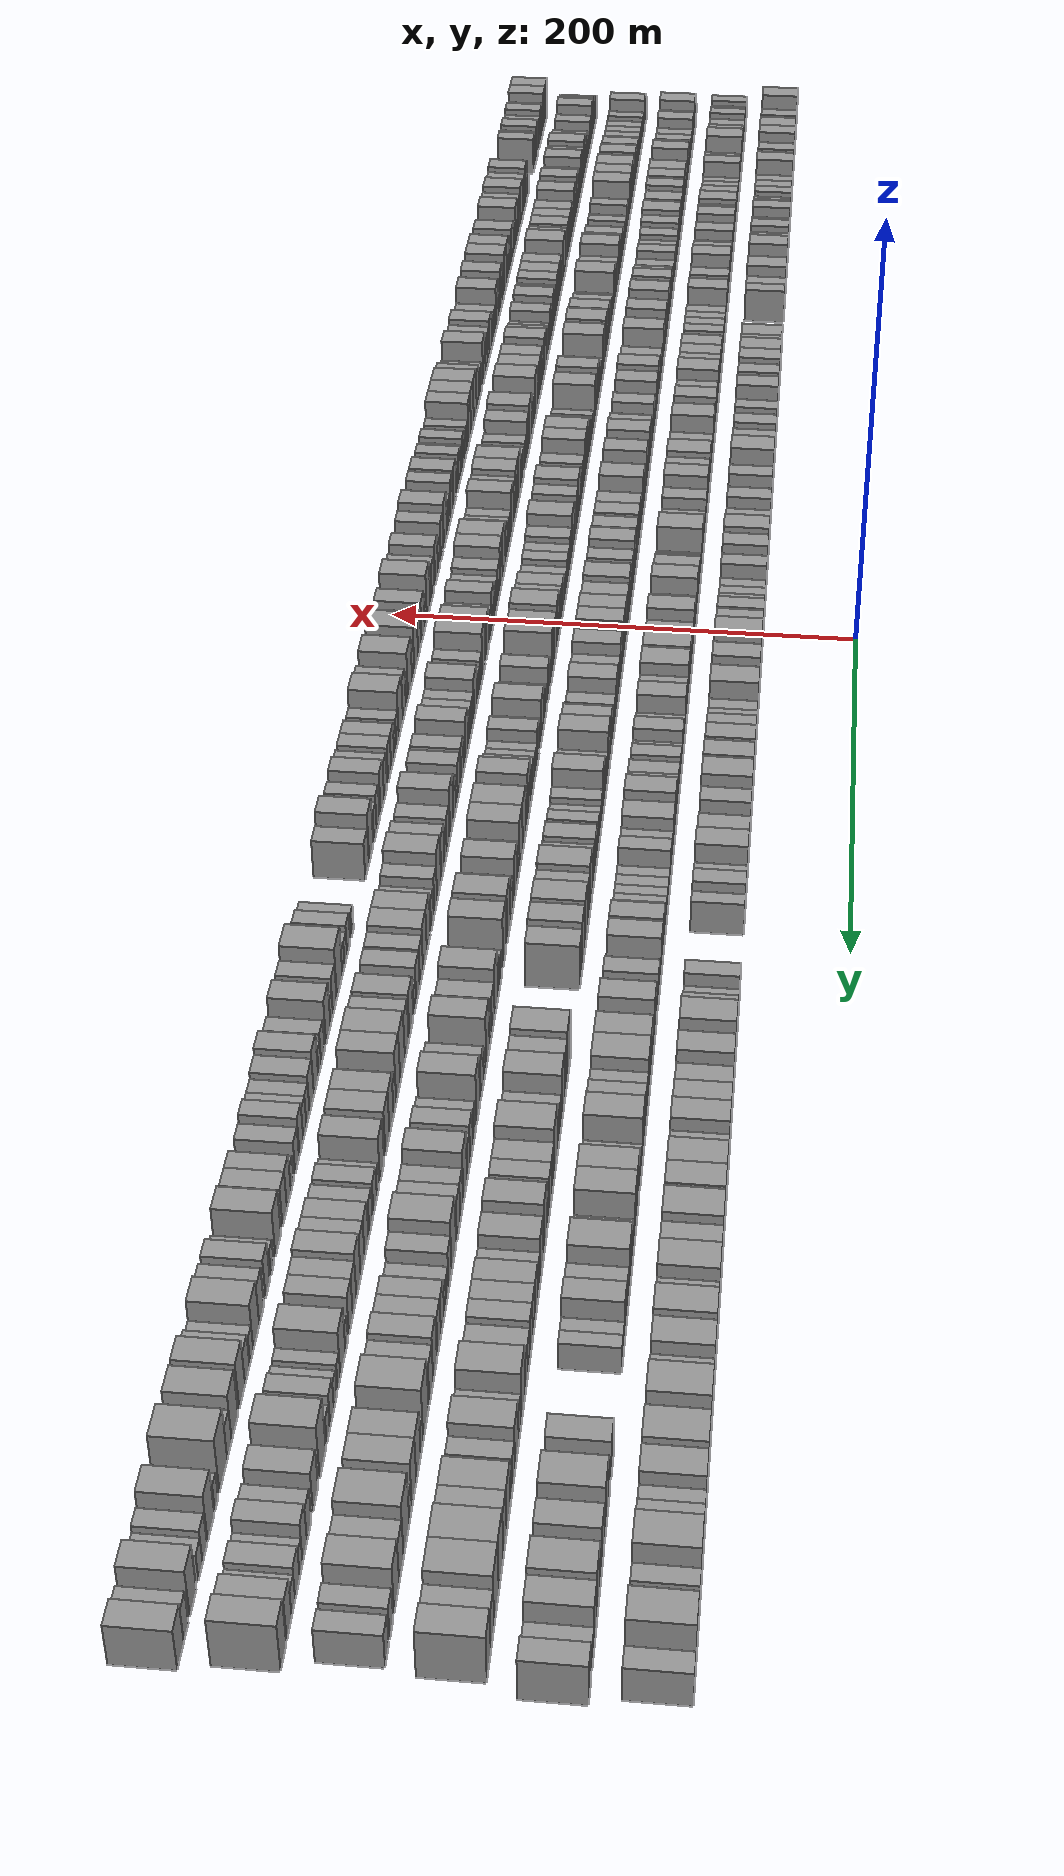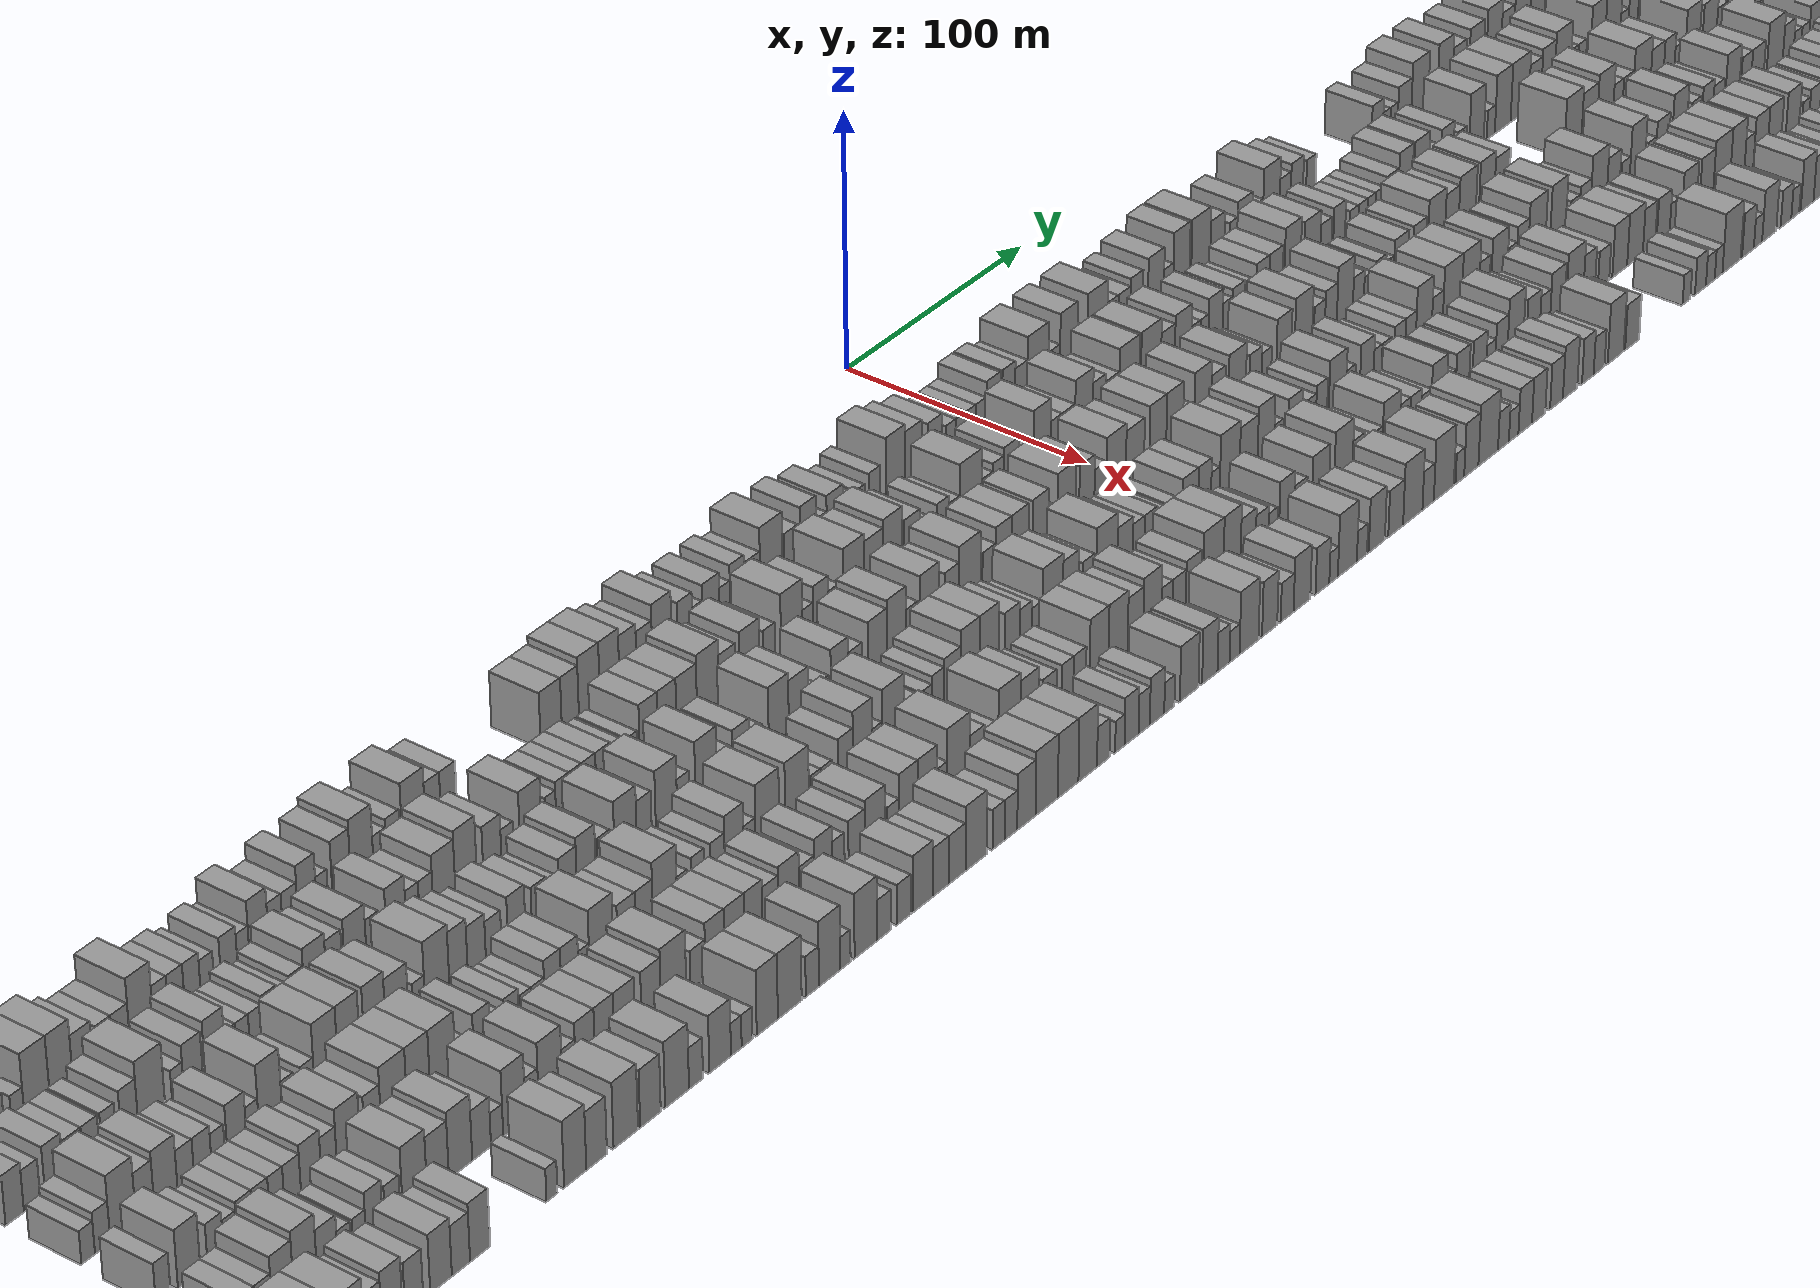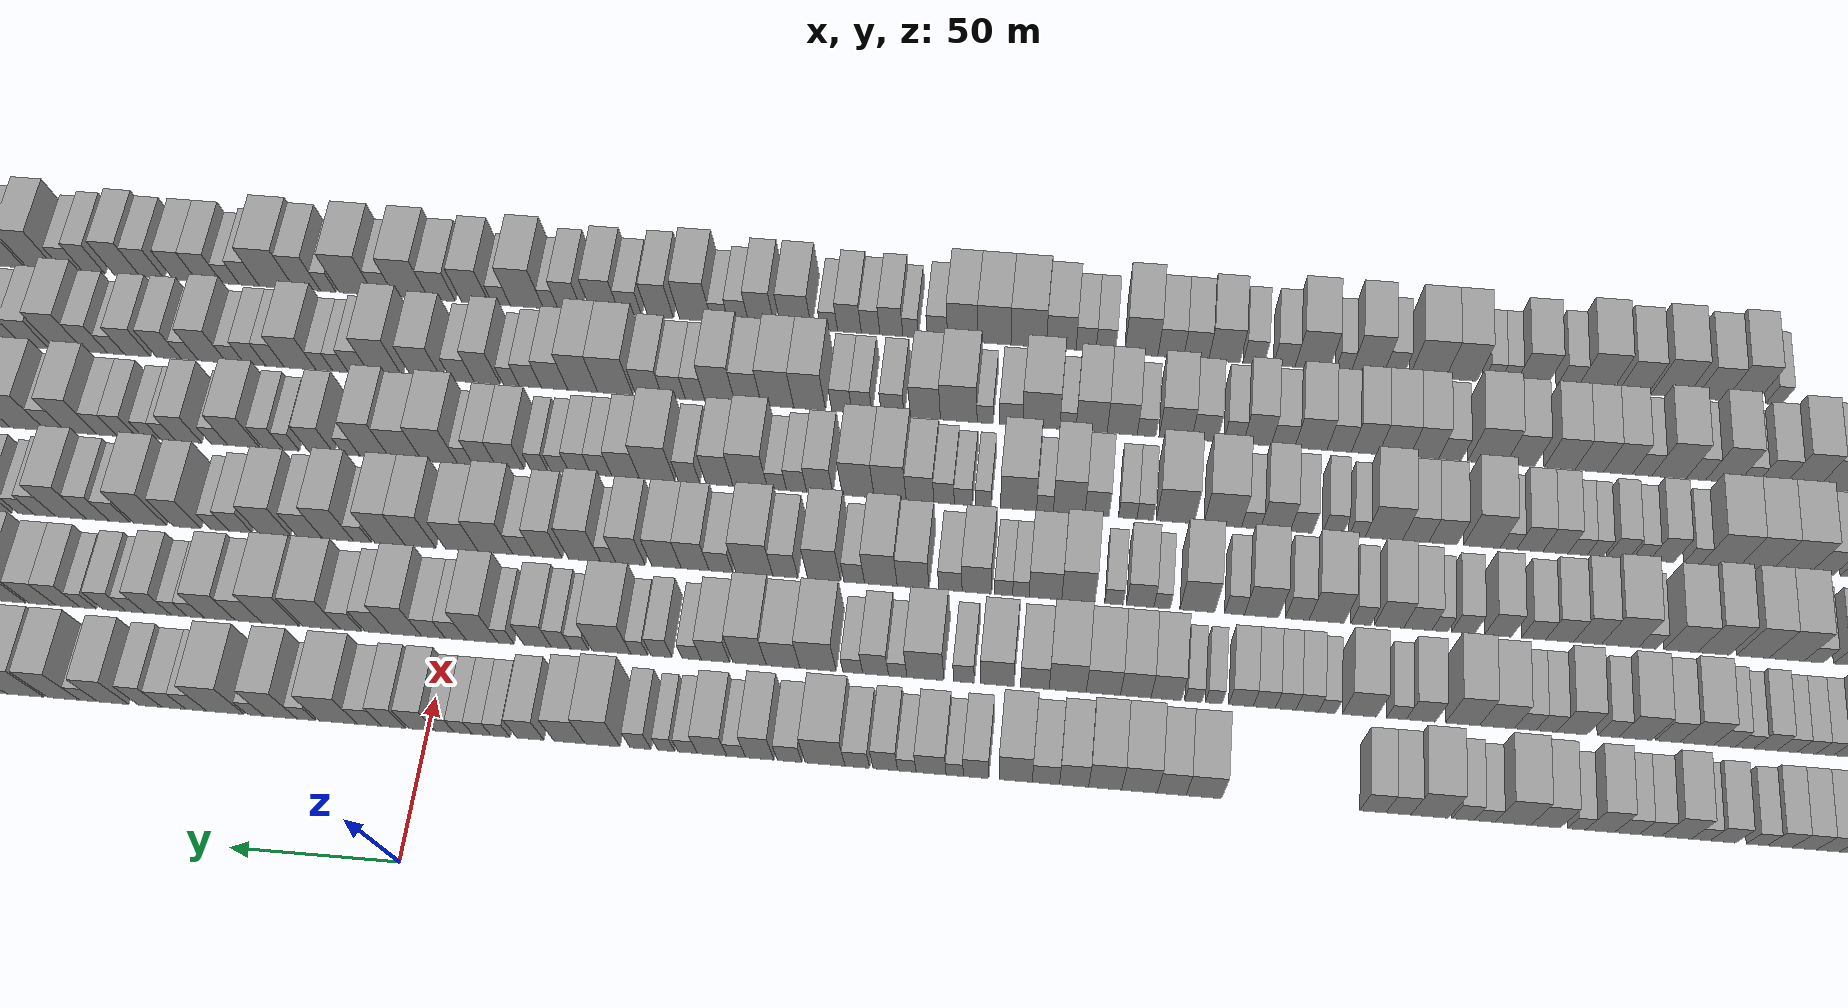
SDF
<sdf version="1.6">
 <world name="default">
  <scene>
   <sky><clouds><speed>12</speed></clouds></sky>
   <ambient>0.4 0.4 0.4 1</ambient>
   <background>0.7 0.7 0.7 1</background>
   <shadows>1</shadows>
  </scene>
  <gravity>0 0 -9.8066</gravity>
  <magnetic_field>6e-06 2.3e-05 -4.2e-05</magnetic_field>
  <physics default="0" name="default_physics" type="ode">
   <ode>
    <solver>
     <type>quick</type>
     <iters>10</iters>
     <sor>1.0</sor>
     <use_dynamic_moi_rescaling>0</use_dynamic_moi_rescaling>
    </solver>
    <constraints>
     <cfm>0</cfm>
     <erp>0.2</erp>
     <contact_max_correcting_vel>100</contact_max_correcting_vel>
     <contact_surface_layer>0.001</contact_surface_layer>
    </constraints>
   </ode>
   <max_step_size>0.004</max_step_size>
   <real_time_factor>1</real_time_factor>
   <real_time_update_rate>250</real_time_update_rate>
  </physics>
  <light name="sun" type="directional">
   <pose>0 0 10 0 0 0</pose>
   <diffuse>0.8 0.8 0.8 1</diffuse>
   <specular>0.2 0.2 0.2 1</specular>
   <attenuation>
    <range>1000</range>
    <constant>0.9</constant>
    <linear>0.01</linear>
    <quadratic>0.001</quadratic>
   </attenuation>
   <direction>-0.5 0.1 -0.9</direction>
  </light>
  <model name="building_1">
   <static>1</static>
   <pose>50.0000 -504.2322 0 0.000000 0.000000 0.000000</pose>
   <link name="link">
    <pose>0 0 12.00 0 0 0</pose>
    <collision name="collision"><geometry><box><size>20.0000 11.5356 24.0000</size></box></geometry></collision>
    <visual name="visual">
     <cast_shadows>0</cast_shadows>
     <geometry><box><size>20.0000 11.5356 24.0000</size></box></geometry>
     <material>
      <script>
       <uri>model://grey_wall/materials/scripts</uri>
       <uri>model://grey_wall/materials/textures</uri>
       <name>vrc/grey_wall</name>
      </script>
     </material>
    </visual>
   </link>
  </model>
  <model name="building_2">
   <static>1</static>
   <pose>50.0000 -495.8121 0 0.000000 0.000000 0.000000</pose>
   <link name="link">
    <pose>0 0 6.00 0 0 0</pose>
    <collision name="collision"><geometry><box><size>20.0000 5.3046 12.0000</size></box></geometry></collision>
    <visual name="visual">
     <cast_shadows>0</cast_shadows>
     <geometry><box><size>20.0000 5.3046 12.0000</size></box></geometry>
     <material>
      <script>
       <uri>model://grey_wall/materials/scripts</uri>
       <uri>model://grey_wall/materials/textures</uri>
       <name>vrc/grey_wall</name>
      </script>
     </material>
    </visual>
   </link>
  </model>
  <model name="building_3">
   <static>1</static>
   <pose>50.0000 -489.0806 0 0.000000 0.000000 0.000000</pose>
   <link name="link">
    <pose>0 0 9.00 0 0 0</pose>
    <collision name="collision"><geometry><box><size>20.0000 8.1584 18.0000</size></box></geometry></collision>
    <visual name="visual">
     <cast_shadows>0</cast_shadows>
     <geometry><box><size>20.0000 8.1584 18.0000</size></box></geometry>
     <material>
      <script>
       <uri>model://grey_wall/materials/scripts</uri>
       <uri>model://grey_wall/materials/textures</uri>
       <name>vrc/grey_wall</name>
      </script>
     </material>
    </visual>
   </link>
  </model>
  <model name="building_4">
   <static>1</static>
   <pose>50.0000 -481.6088 0 0.000000 0.000000 0.000000</pose>
   <link name="link">
    <pose>0 0 7.50 0 0 0</pose>
    <collision name="collision"><geometry><box><size>20.0000 6.7853 15.0000</size></box></geometry></collision>
    <visual name="visual">
     <cast_shadows>0</cast_shadows>
     <geometry><box><size>20.0000 6.7853 15.0000</size></box></geometry>
     <material>
      <script>
       <uri>model://grey_wall/materials/scripts</uri>
       <uri>model://grey_wall/materials/textures</uri>
       <name>vrc/grey_wall</name>
      </script>
     </material>
    </visual>
   </link>
  </model>
  <model name="building_5">
   <static>1</static>
   <pose>50.0000 -472.5507 0 0.000000 0.000000 0.000000</pose>
   <link name="link">
    <pose>0 0 6.00 0 0 0</pose>
    <collision name="collision"><geometry><box><size>20.0000 5.3309 12.0000</size></box></geometry></collision>
    <visual name="visual">
     <cast_shadows>0</cast_shadows>
     <geometry><box><size>20.0000 5.3309 12.0000</size></box></geometry>
     <material>
      <script>
       <uri>model://grey_wall/materials/scripts</uri>
       <uri>model://grey_wall/materials/textures</uri>
       <name>vrc/grey_wall</name>
      </script>
     </material>
    </visual>
   </link>
  </model>
  <model name="building_6">
   <static>1</static>
   <pose>50.0000 -464.5180 0 0.000000 0.000000 0.000000</pose>
   <link name="link">
    <pose>0 0 12.00 0 0 0</pose>
    <collision name="collision"><geometry><box><size>20.0000 10.7343 24.0000</size></box></geometry></collision>
    <visual name="visual">
     <cast_shadows>0</cast_shadows>
     <geometry><box><size>20.0000 10.7343 24.0000</size></box></geometry>
     <material>
      <script>
       <uri>model://grey_wall/materials/scripts</uri>
       <uri>model://grey_wall/materials/textures</uri>
       <name>vrc/grey_wall</name>
      </script>
     </material>
    </visual>
   </link>
  </model>
  <model name="building_7">
   <static>1</static>
   <pose>50.0000 -454.2369 0 0.000000 0.000000 0.000000</pose>
   <link name="link">
    <pose>0 0 12.00 0 0 0</pose>
    <collision name="collision"><geometry><box><size>20.0000 9.8279 24.0000</size></box></geometry></collision>
    <visual name="visual">
     <cast_shadows>0</cast_shadows>
     <geometry><box><size>20.0000 9.8279 24.0000</size></box></geometry>
     <material>
      <script>
       <uri>model://grey_wall/materials/scripts</uri>
       <uri>model://grey_wall/materials/textures</uri>
       <name>vrc/grey_wall</name>
      </script>
     </material>
    </visual>
   </link>
  </model>
  <model name="building_8">
   <static>1</static>
   <pose>50.0000 -445.0070 0 0.000000 0.000000 0.000000</pose>
   <link name="link">
    <pose>0 0 9.00 0 0 0</pose>
    <collision name="collision"><geometry><box><size>20.0000 8.6320 18.0000</size></box></geometry></collision>
    <visual name="visual">
     <cast_shadows>0</cast_shadows>
     <geometry><box><size>20.0000 8.6320 18.0000</size></box></geometry>
     <material>
      <script>
       <uri>model://grey_wall/materials/scripts</uri>
       <uri>model://grey_wall/materials/textures</uri>
       <name>vrc/grey_wall</name>
      </script>
     </material>
    </visual>
   </link>
  </model>
  <model name="building_9">
   <static>1</static>
   <pose>50.0000 -435.4246 0 0.000000 0.000000 0.000000</pose>
   <link name="link">
    <pose>0 0 7.50 0 0 0</pose>
    <collision name="collision"><geometry><box><size>20.0000 6.5329 15.0000</size></box></geometry></collision>
    <visual name="visual">
     <cast_shadows>0</cast_shadows>
     <geometry><box><size>20.0000 6.5329 15.0000</size></box></geometry>
     <material>
      <script>
       <uri>model://grey_wall/materials/scripts</uri>
       <uri>model://grey_wall/materials/textures</uri>
       <name>vrc/grey_wall</name>
      </script>
     </material>
    </visual>
   </link>
  </model>
  <model name="building_10">
   <static>1</static>
   <pose>50.0000 -428.5319 0 0.000000 0.000000 0.000000</pose>
   <link name="link">
    <pose>0 0 7.50 0 0 0</pose>
    <collision name="collision"><geometry><box><size>20.0000 7.2525 15.0000</size></box></geometry></collision>
    <visual name="visual">
     <cast_shadows>0</cast_shadows>
     <geometry><box><size>20.0000 7.2525 15.0000</size></box></geometry>
     <material>
      <script>
       <uri>model://grey_wall/materials/scripts</uri>
       <uri>model://grey_wall/materials/textures</uri>
       <name>vrc/grey_wall</name>
      </script>
     </material>
    </visual>
   </link>
  </model>
  <model name="building_11">
   <static>1</static>
   <pose>50.0000 -419.7696 0 0.000000 0.000000 0.000000</pose>
   <link name="link">
    <pose>0 0 12.00 0 0 0</pose>
    <collision name="collision"><geometry><box><size>20.0000 10.2719 24.0000</size></box></geometry></collision>
    <visual name="visual">
     <cast_shadows>0</cast_shadows>
     <geometry><box><size>20.0000 10.2719 24.0000</size></box></geometry>
     <material>
      <script>
       <uri>model://grey_wall/materials/scripts</uri>
       <uri>model://grey_wall/materials/textures</uri>
       <name>vrc/grey_wall</name>
      </script>
     </material>
    </visual>
   </link>
  </model>
  <model name="building_12">
   <static>1</static>
   <pose>50.0000 -411.3486 0 0.000000 0.000000 0.000000</pose>
   <link name="link">
    <pose>0 0 7.50 0 0 0</pose>
    <collision name="collision"><geometry><box><size>20.0000 6.5702 15.0000</size></box></geometry></collision>
    <visual name="visual">
     <cast_shadows>0</cast_shadows>
     <geometry><box><size>20.0000 6.5702 15.0000</size></box></geometry>
     <material>
      <script>
       <uri>model://grey_wall/materials/scripts</uri>
       <uri>model://grey_wall/materials/textures</uri>
       <name>vrc/grey_wall</name>
      </script>
     </material>
    </visual>
   </link>
  </model>
  <model name="building_13">
   <static>1</static>
   <pose>50.0000 -404.5250 0 0.000000 0.000000 0.000000</pose>
   <link name="link">
    <pose>0 0 7.50 0 0 0</pose>
    <collision name="collision"><geometry><box><size>20.0000 7.0770 15.0000</size></box></geometry></collision>
    <visual name="visual">
     <cast_shadows>0</cast_shadows>
     <geometry><box><size>20.0000 7.0770 15.0000</size></box></geometry>
     <material>
      <script>
       <uri>model://grey_wall/materials/scripts</uri>
       <uri>model://grey_wall/materials/textures</uri>
       <name>vrc/grey_wall</name>
      </script>
     </material>
    </visual>
   </link>
  </model>
  <model name="building_14">
   <static>1</static>
   <pose>50.0000 -397.4608 0 0.000000 0.000000 0.000000</pose>
   <link name="link">
    <pose>0 0 7.50 0 0 0</pose>
    <collision name="collision"><geometry><box><size>20.0000 7.0516 15.0000</size></box></geometry></collision>
    <visual name="visual">
     <cast_shadows>0</cast_shadows>
     <geometry><box><size>20.0000 7.0516 15.0000</size></box></geometry>
     <material>
      <script>
       <uri>model://grey_wall/materials/scripts</uri>
       <uri>model://grey_wall/materials/textures</uri>
       <name>vrc/grey_wall</name>
      </script>
     </material>
    </visual>
   </link>
  </model>
  <model name="building_15">
   <static>1</static>
   <pose>50.0000 -390.9420 0 0.000000 0.000000 0.000000</pose>
   <link name="link">
    <pose>0 0 6.00 0 0 0</pose>
    <collision name="collision"><geometry><box><size>20.0000 5.9859 12.0000</size></box></geometry></collision>
    <visual name="visual">
     <cast_shadows>0</cast_shadows>
     <geometry><box><size>20.0000 5.9859 12.0000</size></box></geometry>
     <material>
      <script>
       <uri>model://grey_wall/materials/scripts</uri>
       <uri>model://grey_wall/materials/textures</uri>
       <name>vrc/grey_wall</name>
      </script>
     </material>
    </visual>
   </link>
  </model>
  <model name="building_16">
   <static>1</static>
   <pose>50.0000 -381.2333 0 0.000000 0.000000 0.000000</pose>
   <link name="link">
    <pose>0 0 7.50 0 0 0</pose>
    <collision name="collision"><geometry><box><size>20.0000 7.4315 15.0000</size></box></geometry></collision>
    <visual name="visual">
     <cast_shadows>0</cast_shadows>
     <geometry><box><size>20.0000 7.4315 15.0000</size></box></geometry>
     <material>
      <script>
       <uri>model://grey_wall/materials/scripts</uri>
       <uri>model://grey_wall/materials/textures</uri>
       <name>vrc/grey_wall</name>
      </script>
     </material>
    </visual>
   </link>
  </model>
  <model name="building_17">
   <static>1</static>
   <pose>50.0000 -374.8296 0 0.000000 0.000000 0.000000</pose>
   <link name="link">
    <pose>0 0 6.00 0 0 0</pose>
    <collision name="collision"><geometry><box><size>20.0000 5.3757 12.0000</size></box></geometry></collision>
    <visual name="visual">
     <cast_shadows>0</cast_shadows>
     <geometry><box><size>20.0000 5.3757 12.0000</size></box></geometry>
     <material>
      <script>
       <uri>model://grey_wall/materials/scripts</uri>
       <uri>model://grey_wall/materials/textures</uri>
       <name>vrc/grey_wall</name>
      </script>
     </material>
    </visual>
   </link>
  </model>
  <model name="building_18">
   <static>1</static>
   <pose>50.0000 -367.8157 0 0.000000 0.000000 0.000000</pose>
   <link name="link">
    <pose>0 0 10.50 0 0 0</pose>
    <collision name="collision"><geometry><box><size>20.0000 8.6522 21.0000</size></box></geometry></collision>
    <visual name="visual">
     <cast_shadows>0</cast_shadows>
     <geometry><box><size>20.0000 8.6522 21.0000</size></box></geometry>
     <material>
      <script>
       <uri>model://grey_wall/materials/scripts</uri>
       <uri>model://grey_wall/materials/textures</uri>
       <name>vrc/grey_wall</name>
      </script>
     </material>
    </visual>
   </link>
  </model>
  <model name="building_19">
   <static>1</static>
   <pose>50.0000 -360.2874 0 0.000000 0.000000 0.000000</pose>
   <link name="link">
    <pose>0 0 7.50 0 0 0</pose>
    <collision name="collision"><geometry><box><size>20.0000 6.4044 15.0000</size></box></geometry></collision>
    <visual name="visual">
     <cast_shadows>0</cast_shadows>
     <geometry><box><size>20.0000 6.4044 15.0000</size></box></geometry>
     <material>
      <script>
       <uri>model://grey_wall/materials/scripts</uri>
       <uri>model://grey_wall/materials/textures</uri>
       <name>vrc/grey_wall</name>
      </script>
     </material>
    </visual>
   </link>
  </model>
  <model name="building_20">
   <static>1</static>
   <pose>50.0000 -353.5778 0 0.000000 0.000000 0.000000</pose>
   <link name="link">
    <pose>0 0 7.50 0 0 0</pose>
    <collision name="collision"><geometry><box><size>20.0000 7.0149 15.0000</size></box></geometry></collision>
    <visual name="visual">
     <cast_shadows>0</cast_shadows>
     <geometry><box><size>20.0000 7.0149 15.0000</size></box></geometry>
     <material>
      <script>
       <uri>model://grey_wall/materials/scripts</uri>
       <uri>model://grey_wall/materials/textures</uri>
       <name>vrc/grey_wall</name>
      </script>
     </material>
    </visual>
   </link>
  </model>
  <model name="building_21">
   <static>1</static>
   <pose>50.0000 -345.8597 0 0.000000 0.000000 0.000000</pose>
   <link name="link">
    <pose>0 0 10.50 0 0 0</pose>
    <collision name="collision"><geometry><box><size>20.0000 8.4212 21.0000</size></box></geometry></collision>
    <visual name="visual">
     <cast_shadows>0</cast_shadows>
     <geometry><box><size>20.0000 8.4212 21.0000</size></box></geometry>
     <material>
      <script>
       <uri>model://grey_wall/materials/scripts</uri>
       <uri>model://grey_wall/materials/textures</uri>
       <name>vrc/grey_wall</name>
      </script>
     </material>
    </visual>
   </link>
  </model>
  <model name="building_22">
   <static>1</static>
   <pose>50.0000 -339.0288 0 0.000000 0.000000 0.000000</pose>
   <link name="link">
    <pose>0 0 6.00 0 0 0</pose>
    <collision name="collision"><geometry><box><size>20.0000 5.2406 12.0000</size></box></geometry></collision>
    <visual name="visual">
     <cast_shadows>0</cast_shadows>
     <geometry><box><size>20.0000 5.2406 12.0000</size></box></geometry>
     <material>
      <script>
       <uri>model://grey_wall/materials/scripts</uri>
       <uri>model://grey_wall/materials/textures</uri>
       <name>vrc/grey_wall</name>
      </script>
     </material>
    </visual>
   </link>
  </model>
  <model name="building_23">
   <static>1</static>
   <pose>50.0000 -330.1326 0 0.000000 0.000000 0.000000</pose>
   <link name="link">
    <pose>0 0 10.50 0 0 0</pose>
    <collision name="collision"><geometry><box><size>20.0000 8.5520 21.0000</size></box></geometry></collision>
    <visual name="visual">
     <cast_shadows>0</cast_shadows>
     <geometry><box><size>20.0000 8.5520 21.0000</size></box></geometry>
     <material>
      <script>
       <uri>model://grey_wall/materials/scripts</uri>
       <uri>model://grey_wall/materials/textures</uri>
       <name>vrc/grey_wall</name>
      </script>
     </material>
    </visual>
   </link>
  </model>
  <model name="building_24">
   <static>1</static>
   <pose>50.0000 -320.6295 0 0.000000 0.000000 0.000000</pose>
   <link name="link">
    <pose>0 0 12.00 0 0 0</pose>
    <collision name="collision"><geometry><box><size>20.0000 10.4542 24.0000</size></box></geometry></collision>
    <visual name="visual">
     <cast_shadows>0</cast_shadows>
     <geometry><box><size>20.0000 10.4542 24.0000</size></box></geometry>
     <material>
      <script>
       <uri>model://grey_wall/materials/scripts</uri>
       <uri>model://grey_wall/materials/textures</uri>
       <name>vrc/grey_wall</name>
      </script>
     </material>
    </visual>
   </link>
  </model>
  <model name="building_25">
   <static>1</static>
   <pose>50.0000 -312.4087 0 0.000000 0.000000 0.000000</pose>
   <link name="link">
    <pose>0 0 6.00 0 0 0</pose>
    <collision name="collision"><geometry><box><size>20.0000 5.9873 12.0000</size></box></geometry></collision>
    <visual name="visual">
     <cast_shadows>0</cast_shadows>
     <geometry><box><size>20.0000 5.9873 12.0000</size></box></geometry>
     <material>
      <script>
       <uri>model://grey_wall/materials/scripts</uri>
       <uri>model://grey_wall/materials/textures</uri>
       <name>vrc/grey_wall</name>
      </script>
     </material>
    </visual>
   </link>
  </model>
  <model name="building_26">
   <static>1</static>
   <pose>50.0000 -306.1453 0 0.000000 0.000000 0.000000</pose>
   <link name="link">
    <pose>0 0 7.50 0 0 0</pose>
    <collision name="collision"><geometry><box><size>20.0000 6.5395 15.0000</size></box></geometry></collision>
    <visual name="visual">
     <cast_shadows>0</cast_shadows>
     <geometry><box><size>20.0000 6.5395 15.0000</size></box></geometry>
     <material>
      <script>
       <uri>model://grey_wall/materials/scripts</uri>
       <uri>model://grey_wall/materials/textures</uri>
       <name>vrc/grey_wall</name>
      </script>
     </material>
    </visual>
   </link>
  </model>
  <model name="building_27">
   <static>1</static>
   <pose>50.0000 -296.4506 0 0.000000 0.000000 0.000000</pose>
   <link name="link">
    <pose>0 0 12.00 0 0 0</pose>
    <collision name="collision"><geometry><box><size>20.0000 10.8500 24.0000</size></box></geometry></collision>
    <visual name="visual">
     <cast_shadows>0</cast_shadows>
     <geometry><box><size>20.0000 10.8500 24.0000</size></box></geometry>
     <material>
      <script>
       <uri>model://grey_wall/materials/scripts</uri>
       <uri>model://grey_wall/materials/textures</uri>
       <name>vrc/grey_wall</name>
      </script>
     </material>
    </visual>
   </link>
  </model>
  <model name="building_28">
   <static>1</static>
   <pose>50.0000 -287.3589 0 0.000000 0.000000 0.000000</pose>
   <link name="link">
    <pose>0 0 9.00 0 0 0</pose>
    <collision name="collision"><geometry><box><size>20.0000 7.3334 18.0000</size></box></geometry></collision>
    <visual name="visual">
     <cast_shadows>0</cast_shadows>
     <geometry><box><size>20.0000 7.3334 18.0000</size></box></geometry>
     <material>
      <script>
       <uri>model://grey_wall/materials/scripts</uri>
       <uri>model://grey_wall/materials/textures</uri>
       <name>vrc/grey_wall</name>
      </script>
     </material>
    </visual>
   </link>
  </model>
  <model name="building_29">
   <static>1</static>
   <pose>50.0000 -279.9059 0 0.000000 0.000000 0.000000</pose>
   <link name="link">
    <pose>0 0 9.00 0 0 0</pose>
    <collision name="collision"><geometry><box><size>20.0000 7.5727 18.0000</size></box></geometry></collision>
    <visual name="visual">
     <cast_shadows>0</cast_shadows>
     <geometry><box><size>20.0000 7.5727 18.0000</size></box></geometry>
     <material>
      <script>
       <uri>model://grey_wall/materials/scripts</uri>
       <uri>model://grey_wall/materials/textures</uri>
       <name>vrc/grey_wall</name>
      </script>
     </material>
    </visual>
   </link>
  </model>
  <model name="building_30">
   <static>1</static>
   <pose>50.0000 -230.5025 0 0.000000 0.000000 0.000000</pose>
   <link name="link">
    <pose>0 0 10.50 0 0 0</pose>
    <collision name="collision"><geometry><box><size>20.0000 10.4114 21.0000</size></box></geometry></collision>
    <visual name="visual">
     <cast_shadows>0</cast_shadows>
     <geometry><box><size>20.0000 10.4114 21.0000</size></box></geometry>
     <material>
      <script>
       <uri>model://grey_wall/materials/scripts</uri>
       <uri>model://grey_wall/materials/textures</uri>
       <name>vrc/grey_wall</name>
      </script>
     </material>
    </visual>
   </link>
  </model>
  <model name="building_31">
   <static>1</static>
   <pose>50.0000 -221.0695 0 0.000000 0.000000 0.000000</pose>
   <link name="link">
    <pose>0 0 10.50 0 0 0</pose>
    <collision name="collision"><geometry><box><size>20.0000 8.4547 21.0000</size></box></geometry></collision>
    <visual name="visual">
     <cast_shadows>0</cast_shadows>
     <geometry><box><size>20.0000 8.4547 21.0000</size></box></geometry>
     <material>
      <script>
       <uri>model://grey_wall/materials/scripts</uri>
       <uri>model://grey_wall/materials/textures</uri>
       <name>vrc/grey_wall</name>
      </script>
     </material>
    </visual>
   </link>
  </model>
  <model name="building_32">
   <static>1</static>
   <pose>50.0000 -211.6235 0 0.000000 0.000000 0.000000</pose>
   <link name="link">
    <pose>0 0 12.00 0 0 0</pose>
    <collision name="collision"><geometry><box><size>20.0000 10.4373 24.0000</size></box></geometry></collision>
    <visual name="visual">
     <cast_shadows>0</cast_shadows>
     <geometry><box><size>20.0000 10.4373 24.0000</size></box></geometry>
     <material>
      <script>
       <uri>model://grey_wall/materials/scripts</uri>
       <uri>model://grey_wall/materials/textures</uri>
       <name>vrc/grey_wall</name>
      </script>
     </material>
    </visual>
   </link>
  </model>
  <model name="building_33">
   <static>1</static>
   <pose>50.0000 -201.5106 0 0.000000 0.000000 0.000000</pose>
   <link name="link">
    <pose>0 0 12.00 0 0 0</pose>
    <collision name="collision"><geometry><box><size>20.0000 9.7884 24.0000</size></box></geometry></collision>
    <visual name="visual">
     <cast_shadows>0</cast_shadows>
     <geometry><box><size>20.0000 9.7884 24.0000</size></box></geometry>
     <material>
      <script>
       <uri>model://grey_wall/materials/scripts</uri>
       <uri>model://grey_wall/materials/textures</uri>
       <name>vrc/grey_wall</name>
      </script>
     </material>
    </visual>
   </link>
  </model>
  <model name="building_34">
   <static>1</static>
   <pose>50.0000 -192.3269 0 0.000000 0.000000 0.000000</pose>
   <link name="link">
    <pose>0 0 10.50 0 0 0</pose>
    <collision name="collision"><geometry><box><size>20.0000 8.5790 21.0000</size></box></geometry></collision>
    <visual name="visual">
     <cast_shadows>0</cast_shadows>
     <geometry><box><size>20.0000 8.5790 21.0000</size></box></geometry>
     <material>
      <script>
       <uri>model://grey_wall/materials/scripts</uri>
       <uri>model://grey_wall/materials/textures</uri>
       <name>vrc/grey_wall</name>
      </script>
     </material>
    </visual>
   </link>
  </model>
  <model name="building_35">
   <static>1</static>
   <pose>50.0000 -184.0494 0 0.000000 0.000000 0.000000</pose>
   <link name="link">
    <pose>0 0 9.00 0 0 0</pose>
    <collision name="collision"><geometry><box><size>20.0000 7.9759 18.0000</size></box></geometry></collision>
    <visual name="visual">
     <cast_shadows>0</cast_shadows>
     <geometry><box><size>20.0000 7.9759 18.0000</size></box></geometry>
     <material>
      <script>
       <uri>model://grey_wall/materials/scripts</uri>
       <uri>model://grey_wall/materials/textures</uri>
       <name>vrc/grey_wall</name>
      </script>
     </material>
    </visual>
   </link>
  </model>
  <model name="building_36">
   <static>1</static>
   <pose>50.0000 -175.1537 0 0.000000 0.000000 0.000000</pose>
   <link name="link">
    <pose>0 0 12.00 0 0 0</pose>
    <collision name="collision"><geometry><box><size>20.0000 9.8156 24.0000</size></box></geometry></collision>
    <visual name="visual">
     <cast_shadows>0</cast_shadows>
     <geometry><box><size>20.0000 9.8156 24.0000</size></box></geometry>
     <material>
      <script>
       <uri>model://grey_wall/materials/scripts</uri>
       <uri>model://grey_wall/materials/textures</uri>
       <name>vrc/grey_wall</name>
      </script>
     </material>
    </visual>
   </link>
  </model>
  <model name="building_37">
   <static>1</static>
   <pose>50.0000 -163.4848 0 0.000000 0.000000 0.000000</pose>
   <link name="link">
    <pose>0 0 9.00 0 0 0</pose>
    <collision name="collision"><geometry><box><size>20.0000 7.5222 18.0000</size></box></geometry></collision>
    <visual name="visual">
     <cast_shadows>0</cast_shadows>
     <geometry><box><size>20.0000 7.5222 18.0000</size></box></geometry>
     <material>
      <script>
       <uri>model://grey_wall/materials/scripts</uri>
       <uri>model://grey_wall/materials/textures</uri>
       <name>vrc/grey_wall</name>
      </script>
     </material>
    </visual>
   </link>
  </model>
  <model name="building_38">
   <static>1</static>
   <pose>50.0000 -157.1644 0 0.000000 0.000000 0.000000</pose>
   <link name="link">
    <pose>0 0 6.00 0 0 0</pose>
    <collision name="collision"><geometry><box><size>20.0000 5.1187 12.0000</size></box></geometry></collision>
    <visual name="visual">
     <cast_shadows>0</cast_shadows>
     <geometry><box><size>20.0000 5.1187 12.0000</size></box></geometry>
     <material>
      <script>
       <uri>model://grey_wall/materials/scripts</uri>
       <uri>model://grey_wall/materials/textures</uri>
       <name>vrc/grey_wall</name>
      </script>
     </material>
    </visual>
   </link>
  </model>
  <model name="building_39">
   <static>1</static>
   <pose>50.0000 -150.1670 0 0.000000 0.000000 0.000000</pose>
   <link name="link">
    <pose>0 0 9.00 0 0 0</pose>
    <collision name="collision"><geometry><box><size>20.0000 8.8761 18.0000</size></box></geometry></collision>
    <visual name="visual">
     <cast_shadows>0</cast_shadows>
     <geometry><box><size>20.0000 8.8761 18.0000</size></box></geometry>
     <material>
      <script>
       <uri>model://grey_wall/materials/scripts</uri>
       <uri>model://grey_wall/materials/textures</uri>
       <name>vrc/grey_wall</name>
      </script>
     </material>
    </visual>
   </link>
  </model>
  <model name="building_40">
   <static>1</static>
   <pose>50.0000 -143.0073 0 0.000000 0.000000 0.000000</pose>
   <link name="link">
    <pose>0 0 6.00 0 0 0</pose>
    <collision name="collision"><geometry><box><size>20.0000 5.4432 12.0000</size></box></geometry></collision>
    <visual name="visual">
     <cast_shadows>0</cast_shadows>
     <geometry><box><size>20.0000 5.4432 12.0000</size></box></geometry>
     <material>
      <script>
       <uri>model://grey_wall/materials/scripts</uri>
       <uri>model://grey_wall/materials/textures</uri>
       <name>vrc/grey_wall</name>
      </script>
     </material>
    </visual>
   </link>
  </model>
  <model name="building_41">
   <static>1</static>
   <pose>50.0000 -136.6264 0 0.000000 0.000000 0.000000</pose>
   <link name="link">
    <pose>0 0 9.00 0 0 0</pose>
    <collision name="collision"><geometry><box><size>20.0000 7.3187 18.0000</size></box></geometry></collision>
    <visual name="visual">
     <cast_shadows>0</cast_shadows>
     <geometry><box><size>20.0000 7.3187 18.0000</size></box></geometry>
     <material>
      <script>
       <uri>model://grey_wall/materials/scripts</uri>
       <uri>model://grey_wall/materials/textures</uri>
       <name>vrc/grey_wall</name>
      </script>
     </material>
    </visual>
   </link>
  </model>
  <model name="building_42">
   <static>1</static>
   <pose>50.0000 -128.3104 0 0.000000 0.000000 0.000000</pose>
   <link name="link">
    <pose>0 0 7.50 0 0 0</pose>
    <collision name="collision"><geometry><box><size>20.0000 7.3132 15.0000</size></box></geometry></collision>
    <visual name="visual">
     <cast_shadows>0</cast_shadows>
     <geometry><box><size>20.0000 7.3132 15.0000</size></box></geometry>
     <material>
      <script>
       <uri>model://grey_wall/materials/scripts</uri>
       <uri>model://grey_wall/materials/textures</uri>
       <name>vrc/grey_wall</name>
      </script>
     </material>
    </visual>
   </link>
  </model>
  <model name="building_43">
   <static>1</static>
   <pose>50.0000 -118.7637 0 0.000000 0.000000 0.000000</pose>
   <link name="link">
    <pose>0 0 12.00 0 0 0</pose>
    <collision name="collision"><geometry><box><size>20.0000 11.7802 24.0000</size></box></geometry></collision>
    <visual name="visual">
     <cast_shadows>0</cast_shadows>
     <geometry><box><size>20.0000 11.7802 24.0000</size></box></geometry>
     <material>
      <script>
       <uri>model://grey_wall/materials/scripts</uri>
       <uri>model://grey_wall/materials/textures</uri>
       <name>vrc/grey_wall</name>
      </script>
     </material>
    </visual>
   </link>
  </model>
  <model name="building_44">
   <static>1</static>
   <pose>50.0000 -108.2134 0 0.000000 0.000000 0.000000</pose>
   <link name="link">
    <pose>0 0 7.50 0 0 0</pose>
    <collision name="collision"><geometry><box><size>20.0000 7.3204 15.0000</size></box></geometry></collision>
    <visual name="visual">
     <cast_shadows>0</cast_shadows>
     <geometry><box><size>20.0000 7.3204 15.0000</size></box></geometry>
     <material>
      <script>
       <uri>model://grey_wall/materials/scripts</uri>
       <uri>model://grey_wall/materials/textures</uri>
       <name>vrc/grey_wall</name>
      </script>
     </material>
    </visual>
   </link>
  </model>
  <model name="building_45">
   <static>1</static>
   <pose>50.0000 -99.3476 0 0.000000 0.000000 0.000000</pose>
   <link name="link">
    <pose>0 0 10.50 0 0 0</pose>
    <collision name="collision"><geometry><box><size>20.0000 8.4114 21.0000</size></box></geometry></collision>
    <visual name="visual">
     <cast_shadows>0</cast_shadows>
     <geometry><box><size>20.0000 8.4114 21.0000</size></box></geometry>
     <material>
      <script>
       <uri>model://grey_wall/materials/scripts</uri>
       <uri>model://grey_wall/materials/textures</uri>
       <name>vrc/grey_wall</name>
      </script>
     </material>
    </visual>
   </link>
  </model>
  <model name="building_46">
   <static>1</static>
   <pose>50.0000 -92.2943 0 0.000000 0.000000 0.000000</pose>
   <link name="link">
    <pose>0 0 6.00 0 0 0</pose>
    <collision name="collision"><geometry><box><size>20.0000 5.6951 12.0000</size></box></geometry></collision>
    <visual name="visual">
     <cast_shadows>0</cast_shadows>
     <geometry><box><size>20.0000 5.6951 12.0000</size></box></geometry>
     <material>
      <script>
       <uri>model://grey_wall/materials/scripts</uri>
       <uri>model://grey_wall/materials/textures</uri>
       <name>vrc/grey_wall</name>
      </script>
     </material>
    </visual>
   </link>
  </model>
  <model name="building_47">
   <static>1</static>
   <pose>50.0000 -85.0545 0 0.000000 0.000000 0.000000</pose>
   <link name="link">
    <pose>0 0 9.00 0 0 0</pose>
    <collision name="collision"><geometry><box><size>20.0000 8.7846 18.0000</size></box></geometry></collision>
    <visual name="visual">
     <cast_shadows>0</cast_shadows>
     <geometry><box><size>20.0000 8.7846 18.0000</size></box></geometry>
     <material>
      <script>
       <uri>model://grey_wall/materials/scripts</uri>
       <uri>model://grey_wall/materials/textures</uri>
       <name>vrc/grey_wall</name>
      </script>
     </material>
    </visual>
   </link>
  </model>
  <model name="building_48">
   <static>1</static>
   <pose>50.0000 -77.7949 0 0.000000 0.000000 0.000000</pose>
   <link name="link">
    <pose>0 0 6.00 0 0 0</pose>
    <collision name="collision"><geometry><box><size>20.0000 5.7346 12.0000</size></box></geometry></collision>
    <visual name="visual">
     <cast_shadows>0</cast_shadows>
     <geometry><box><size>20.0000 5.7346 12.0000</size></box></geometry>
     <material>
      <script>
       <uri>model://grey_wall/materials/scripts</uri>
       <uri>model://grey_wall/materials/textures</uri>
       <name>vrc/grey_wall</name>
      </script>
     </material>
    </visual>
   </link>
  </model>
  <model name="building_49">
   <static>1</static>
   <pose>50.0000 -71.4080 0 0.000000 0.000000 0.000000</pose>
   <link name="link">
    <pose>0 0 6.00 0 0 0</pose>
    <collision name="collision"><geometry><box><size>20.0000 5.0391 12.0000</size></box></geometry></collision>
    <visual name="visual">
     <cast_shadows>0</cast_shadows>
     <geometry><box><size>20.0000 5.0391 12.0000</size></box></geometry>
     <material>
      <script>
       <uri>model://grey_wall/materials/scripts</uri>
       <uri>model://grey_wall/materials/textures</uri>
       <name>vrc/grey_wall</name>
      </script>
     </material>
    </visual>
   </link>
  </model>
  <model name="building_50">
   <static>1</static>
   <pose>50.0000 -63.7196 0 0.000000 0.000000 0.000000</pose>
   <link name="link">
    <pose>0 0 7.50 0 0 0</pose>
    <collision name="collision"><geometry><box><size>20.0000 6.3378 15.0000</size></box></geometry></collision>
    <visual name="visual">
     <cast_shadows>0</cast_shadows>
     <geometry><box><size>20.0000 6.3378 15.0000</size></box></geometry>
     <material>
      <script>
       <uri>model://grey_wall/materials/scripts</uri>
       <uri>model://grey_wall/materials/textures</uri>
       <name>vrc/grey_wall</name>
      </script>
     </material>
    </visual>
   </link>
  </model>
  <model name="building_51">
   <static>1</static>
   <pose>50.0000 -52.3012 0 0.000000 0.000000 0.000000</pose>
   <link name="link">
    <pose>0 0 12.00 0 0 0</pose>
    <collision name="collision"><geometry><box><size>20.0000 10.4989 24.0000</size></box></geometry></collision>
    <visual name="visual">
     <cast_shadows>0</cast_shadows>
     <geometry><box><size>20.0000 10.4989 24.0000</size></box></geometry>
     <material>
      <script>
       <uri>model://grey_wall/materials/scripts</uri>
       <uri>model://grey_wall/materials/textures</uri>
       <name>vrc/grey_wall</name>
      </script>
     </material>
    </visual>
   </link>
  </model>
  <model name="building_52">
   <static>1</static>
   <pose>50.0000 -42.3873 0 0.000000 0.000000 0.000000</pose>
   <link name="link">
    <pose>0 0 10.50 0 0 0</pose>
    <collision name="collision"><geometry><box><size>20.0000 9.3289 21.0000</size></box></geometry></collision>
    <visual name="visual">
     <cast_shadows>0</cast_shadows>
     <geometry><box><size>20.0000 9.3289 21.0000</size></box></geometry>
     <material>
      <script>
       <uri>model://grey_wall/materials/scripts</uri>
       <uri>model://grey_wall/materials/textures</uri>
       <name>vrc/grey_wall</name>
      </script>
     </material>
    </visual>
   </link>
  </model>
  <model name="building_53">
   <static>1</static>
   <pose>50.0000 -30.6553 0 0.000000 0.000000 0.000000</pose>
   <link name="link">
    <pose>0 0 9.00 0 0 0</pose>
    <collision name="collision"><geometry><box><size>20.0000 8.1350 18.0000</size></box></geometry></collision>
    <visual name="visual">
     <cast_shadows>0</cast_shadows>
     <geometry><box><size>20.0000 8.1350 18.0000</size></box></geometry>
     <material>
      <script>
       <uri>model://grey_wall/materials/scripts</uri>
       <uri>model://grey_wall/materials/textures</uri>
       <name>vrc/grey_wall</name>
      </script>
     </material>
    </visual>
   </link>
  </model>
  <model name="building_54">
   <static>1</static>
   <pose>50.0000 -21.7076 0 0.000000 0.000000 0.000000</pose>
   <link name="link">
    <pose>0 0 6.00 0 0 0</pose>
    <collision name="collision"><geometry><box><size>20.0000 5.7605 12.0000</size></box></geometry></collision>
    <visual name="visual">
     <cast_shadows>0</cast_shadows>
     <geometry><box><size>20.0000 5.7605 12.0000</size></box></geometry>
     <material>
      <script>
       <uri>model://grey_wall/materials/scripts</uri>
       <uri>model://grey_wall/materials/textures</uri>
       <name>vrc/grey_wall</name>
      </script>
     </material>
    </visual>
   </link>
  </model>
  <model name="building_55">
   <static>1</static>
   <pose>50.0000 -16.0079 0 0.000000 0.000000 0.000000</pose>
   <link name="link">
    <pose>0 0 6.00 0 0 0</pose>
    <collision name="collision"><geometry><box><size>20.0000 5.6389 12.0000</size></box></geometry></collision>
    <visual name="visual">
     <cast_shadows>0</cast_shadows>
     <geometry><box><size>20.0000 5.6389 12.0000</size></box></geometry>
     <material>
      <script>
       <uri>model://grey_wall/materials/scripts</uri>
       <uri>model://grey_wall/materials/textures</uri>
       <name>vrc/grey_wall</name>
      </script>
     </material>
    </visual>
   </link>
  </model>
  <model name="building_56">
   <static>1</static>
   <pose>50.0000 -10.5080 0 0.000000 0.000000 0.000000</pose>
   <link name="link">
    <pose>0 0 6.00 0 0 0</pose>
    <collision name="collision"><geometry><box><size>20.0000 5.3609 12.0000</size></box></geometry></collision>
    <visual name="visual">
     <cast_shadows>0</cast_shadows>
     <geometry><box><size>20.0000 5.3609 12.0000</size></box></geometry>
     <material>
      <script>
       <uri>model://grey_wall/materials/scripts</uri>
       <uri>model://grey_wall/materials/textures</uri>
       <name>vrc/grey_wall</name>
      </script>
     </material>
    </visual>
   </link>
  </model>
  <model name="building_57">
   <static>1</static>
   <pose>50.0000 -4.9211 0 0.000000 0.000000 0.000000</pose>
   <link name="link">
    <pose>0 0 6.00 0 0 0</pose>
    <collision name="collision"><geometry><box><size>20.0000 5.8130 12.0000</size></box></geometry></collision>
    <visual name="visual">
     <cast_shadows>0</cast_shadows>
     <geometry><box><size>20.0000 5.8130 12.0000</size></box></geometry>
     <material>
      <script>
       <uri>model://grey_wall/materials/scripts</uri>
       <uri>model://grey_wall/materials/textures</uri>
       <name>vrc/grey_wall</name>
      </script>
     </material>
    </visual>
   </link>
  </model>
  <model name="building_58">
   <static>1</static>
   <pose>50.0000 1.9506 0 0.000000 0.000000 0.000000</pose>
   <link name="link">
    <pose>0 0 9.00 0 0 0</pose>
    <collision name="collision"><geometry><box><size>20.0000 7.9304 18.0000</size></box></geometry></collision>
    <visual name="visual">
     <cast_shadows>0</cast_shadows>
     <geometry><box><size>20.0000 7.9304 18.0000</size></box></geometry>
     <material>
      <script>
       <uri>model://grey_wall/materials/scripts</uri>
       <uri>model://grey_wall/materials/textures</uri>
       <name>vrc/grey_wall</name>
      </script>
     </material>
    </visual>
   </link>
  </model>
  <model name="building_59">
   <static>1</static>
   <pose>50.0000 10.5817 0 0.000000 0.000000 0.000000</pose>
   <link name="link">
    <pose>0 0 9.00 0 0 0</pose>
    <collision name="collision"><geometry><box><size>20.0000 7.3317 18.0000</size></box></geometry></collision>
    <visual name="visual">
     <cast_shadows>0</cast_shadows>
     <geometry><box><size>20.0000 7.3317 18.0000</size></box></geometry>
     <material>
      <script>
       <uri>model://grey_wall/materials/scripts</uri>
       <uri>model://grey_wall/materials/textures</uri>
       <name>vrc/grey_wall</name>
      </script>
     </material>
    </visual>
   </link>
  </model>
  <model name="building_60">
   <static>1</static>
   <pose>50.0000 17.8337 0 0.000000 0.000000 0.000000</pose>
   <link name="link">
    <pose>0 0 7.50 0 0 0</pose>
    <collision name="collision"><geometry><box><size>20.0000 7.1722 15.0000</size></box></geometry></collision>
    <visual name="visual">
     <cast_shadows>0</cast_shadows>
     <geometry><box><size>20.0000 7.1722 15.0000</size></box></geometry>
     <material>
      <script>
       <uri>model://grey_wall/materials/scripts</uri>
       <uri>model://grey_wall/materials/textures</uri>
       <name>vrc/grey_wall</name>
      </script>
     </material>
    </visual>
   </link>
  </model>
  <model name="building_61">
   <static>1</static>
   <pose>50.0000 27.3216 0 0.000000 0.000000 0.000000</pose>
   <link name="link">
    <pose>0 0 12.00 0 0 0</pose>
    <collision name="collision"><geometry><box><size>20.0000 11.8038 24.0000</size></box></geometry></collision>
    <visual name="visual">
     <cast_shadows>0</cast_shadows>
     <geometry><box><size>20.0000 11.8038 24.0000</size></box></geometry>
     <material>
      <script>
       <uri>model://grey_wall/materials/scripts</uri>
       <uri>model://grey_wall/materials/textures</uri>
       <name>vrc/grey_wall</name>
      </script>
     </material>
    </visual>
   </link>
  </model>
  <model name="building_62">
   <static>1</static>
   <pose>50.0000 37.0348 0 0.000000 0.000000 0.000000</pose>
   <link name="link">
    <pose>0 0 6.00 0 0 0</pose>
    <collision name="collision"><geometry><box><size>20.0000 5.6224 12.0000</size></box></geometry></collision>
    <visual name="visual">
     <cast_shadows>0</cast_shadows>
     <geometry><box><size>20.0000 5.6224 12.0000</size></box></geometry>
     <material>
      <script>
       <uri>model://grey_wall/materials/scripts</uri>
       <uri>model://grey_wall/materials/textures</uri>
       <name>vrc/grey_wall</name>
      </script>
     </material>
    </visual>
   </link>
  </model>
  <model name="building_63">
   <static>1</static>
   <pose>50.0000 44.8088 0 0.000000 0.000000 0.000000</pose>
   <link name="link">
    <pose>0 0 12.00 0 0 0</pose>
    <collision name="collision"><geometry><box><size>20.0000 9.9257 24.0000</size></box></geometry></collision>
    <visual name="visual">
     <cast_shadows>0</cast_shadows>
     <geometry><box><size>20.0000 9.9257 24.0000</size></box></geometry>
     <material>
      <script>
       <uri>model://grey_wall/materials/scripts</uri>
       <uri>model://grey_wall/materials/textures</uri>
       <name>vrc/grey_wall</name>
      </script>
     </material>
    </visual>
   </link>
  </model>
  <model name="building_64">
   <static>1</static>
   <pose>50.0000 52.3100 0 0.000000 0.000000 0.000000</pose>
   <link name="link">
    <pose>0 0 6.00 0 0 0</pose>
    <collision name="collision"><geometry><box><size>20.0000 5.0767 12.0000</size></box></geometry></collision>
    <visual name="visual">
     <cast_shadows>0</cast_shadows>
     <geometry><box><size>20.0000 5.0767 12.0000</size></box></geometry>
     <material>
      <script>
       <uri>model://grey_wall/materials/scripts</uri>
       <uri>model://grey_wall/materials/textures</uri>
       <name>vrc/grey_wall</name>
      </script>
     </material>
    </visual>
   </link>
  </model>
  <model name="building_65">
   <static>1</static>
   <pose>50.0000 61.5633 0 0.000000 0.000000 0.000000</pose>
   <link name="link">
    <pose>0 0 12.00 0 0 0</pose>
    <collision name="collision"><geometry><box><size>20.0000 11.4299 24.0000</size></box></geometry></collision>
    <visual name="visual">
     <cast_shadows>0</cast_shadows>
     <geometry><box><size>20.0000 11.4299 24.0000</size></box></geometry>
     <material>
      <script>
       <uri>model://grey_wall/materials/scripts</uri>
       <uri>model://grey_wall/materials/textures</uri>
       <name>vrc/grey_wall</name>
      </script>
     </material>
    </visual>
   </link>
  </model>
  <model name="building_66">
   <static>1</static>
   <pose>50.0000 70.4179 0 0.000000 0.000000 0.000000</pose>
   <link name="link">
    <pose>0 0 7.50 0 0 0</pose>
    <collision name="collision"><geometry><box><size>20.0000 6.2793 15.0000</size></box></geometry></collision>
    <visual name="visual">
     <cast_shadows>0</cast_shadows>
     <geometry><box><size>20.0000 6.2793 15.0000</size></box></geometry>
     <material>
      <script>
       <uri>model://grey_wall/materials/scripts</uri>
       <uri>model://grey_wall/materials/textures</uri>
       <name>vrc/grey_wall</name>
      </script>
     </material>
    </visual>
   </link>
  </model>
  <model name="building_67">
   <static>1</static>
   <pose>50.0000 77.2101 0 0.000000 0.000000 0.000000</pose>
   <link name="link">
    <pose>0 0 7.50 0 0 0</pose>
    <collision name="collision"><geometry><box><size>20.0000 7.3051 15.0000</size></box></geometry></collision>
    <visual name="visual">
     <cast_shadows>0</cast_shadows>
     <geometry><box><size>20.0000 7.3051 15.0000</size></box></geometry>
     <material>
      <script>
       <uri>model://grey_wall/materials/scripts</uri>
       <uri>model://grey_wall/materials/textures</uri>
       <name>vrc/grey_wall</name>
      </script>
     </material>
    </visual>
   </link>
  </model>
  <model name="building_68">
   <static>1</static>
   <pose>50.0000 84.4827 0 0.000000 0.000000 0.000000</pose>
   <link name="link">
    <pose>0 0 9.00 0 0 0</pose>
    <collision name="collision"><geometry><box><size>20.0000 7.2401 18.0000</size></box></geometry></collision>
    <visual name="visual">
     <cast_shadows>0</cast_shadows>
     <geometry><box><size>20.0000 7.2401 18.0000</size></box></geometry>
     <material>
      <script>
       <uri>model://grey_wall/materials/scripts</uri>
       <uri>model://grey_wall/materials/textures</uri>
       <name>vrc/grey_wall</name>
      </script>
     </material>
    </visual>
   </link>
  </model>
  <model name="building_69">
   <static>1</static>
   <pose>50.0000 95.8313 0 0.000000 0.000000 0.000000</pose>
   <link name="link">
    <pose>0 0 10.50 0 0 0</pose>
    <collision name="collision"><geometry><box><size>20.0000 9.4570 21.0000</size></box></geometry></collision>
    <visual name="visual">
     <cast_shadows>0</cast_shadows>
     <geometry><box><size>20.0000 9.4570 21.0000</size></box></geometry>
     <material>
      <script>
       <uri>model://grey_wall/materials/scripts</uri>
       <uri>model://grey_wall/materials/textures</uri>
       <name>vrc/grey_wall</name>
      </script>
     </material>
    </visual>
   </link>
  </model>
  <model name="building_70">
   <static>1</static>
   <pose>50.0000 103.3412 0 0.000000 0.000000 0.000000</pose>
   <link name="link">
    <pose>0 0 6.00 0 0 0</pose>
    <collision name="collision"><geometry><box><size>20.0000 5.5629 12.0000</size></box></geometry></collision>
    <visual name="visual">
     <cast_shadows>0</cast_shadows>
     <geometry><box><size>20.0000 5.5629 12.0000</size></box></geometry>
     <material>
      <script>
       <uri>model://grey_wall/materials/scripts</uri>
       <uri>model://grey_wall/materials/textures</uri>
       <name>vrc/grey_wall</name>
      </script>
     </material>
    </visual>
   </link>
  </model>
  <model name="building_71">
   <static>1</static>
   <pose>50.0000 111.0125 0 0.000000 0.000000 0.000000</pose>
   <link name="link">
    <pose>0 0 12.00 0 0 0</pose>
    <collision name="collision"><geometry><box><size>20.0000 9.7797 24.0000</size></box></geometry></collision>
    <visual name="visual">
     <cast_shadows>0</cast_shadows>
     <geometry><box><size>20.0000 9.7797 24.0000</size></box></geometry>
     <material>
      <script>
       <uri>model://grey_wall/materials/scripts</uri>
       <uri>model://grey_wall/materials/textures</uri>
       <name>vrc/grey_wall</name>
      </script>
     </material>
    </visual>
   </link>
  </model>
  <model name="building_72">
   <static>1</static>
   <pose>50.0000 122.6538 0 0.000000 0.000000 0.000000</pose>
   <link name="link">
    <pose>0 0 12.00 0 0 0</pose>
    <collision name="collision"><geometry><box><size>20.0000 11.5030 24.0000</size></box></geometry></collision>
    <visual name="visual">
     <cast_shadows>0</cast_shadows>
     <geometry><box><size>20.0000 11.5030 24.0000</size></box></geometry>
     <material>
      <script>
       <uri>model://grey_wall/materials/scripts</uri>
       <uri>model://grey_wall/materials/textures</uri>
       <name>vrc/grey_wall</name>
      </script>
     </material>
    </visual>
   </link>
  </model>
  <model name="building_73">
   <static>1</static>
   <pose>50.0000 132.6760 0 0.000000 0.000000 0.000000</pose>
   <link name="link">
    <pose>0 0 9.00 0 0 0</pose>
    <collision name="collision"><geometry><box><size>20.0000 8.5412 18.0000</size></box></geometry></collision>
    <visual name="visual">
     <cast_shadows>0</cast_shadows>
     <geometry><box><size>20.0000 8.5412 18.0000</size></box></geometry>
     <material>
      <script>
       <uri>model://grey_wall/materials/scripts</uri>
       <uri>model://grey_wall/materials/textures</uri>
       <name>vrc/grey_wall</name>
      </script>
     </material>
    </visual>
   </link>
  </model>
  <model name="building_74">
   <static>1</static>
   <pose>50.0000 142.4405 0 0.000000 0.000000 0.000000</pose>
   <link name="link">
    <pose>0 0 6.00 0 0 0</pose>
    <collision name="collision"><geometry><box><size>20.0000 4.9879 12.0000</size></box></geometry></collision>
    <visual name="visual">
     <cast_shadows>0</cast_shadows>
     <geometry><box><size>20.0000 4.9879 12.0000</size></box></geometry>
     <material>
      <script>
       <uri>model://grey_wall/materials/scripts</uri>
       <uri>model://grey_wall/materials/textures</uri>
       <name>vrc/grey_wall</name>
      </script>
     </material>
    </visual>
   </link>
  </model>
  <model name="building_75">
   <static>1</static>
   <pose>50.0000 149.3304 0 0.000000 0.000000 0.000000</pose>
   <link name="link">
    <pose>0 0 9.00 0 0 0</pose>
    <collision name="collision"><geometry><box><size>20.0000 8.7917 18.0000</size></box></geometry></collision>
    <visual name="visual">
     <cast_shadows>0</cast_shadows>
     <geometry><box><size>20.0000 8.7917 18.0000</size></box></geometry>
     <material>
      <script>
       <uri>model://grey_wall/materials/scripts</uri>
       <uri>model://grey_wall/materials/textures</uri>
       <name>vrc/grey_wall</name>
      </script>
     </material>
    </visual>
   </link>
  </model>
  <model name="building_76">
   <static>1</static>
   <pose>50.0000 157.5858 0 0.000000 0.000000 0.000000</pose>
   <link name="link">
    <pose>0 0 6.00 0 0 0</pose>
    <collision name="collision"><geometry><box><size>20.0000 5.7190 12.0000</size></box></geometry></collision>
    <visual name="visual">
     <cast_shadows>0</cast_shadows>
     <geometry><box><size>20.0000 5.7190 12.0000</size></box></geometry>
     <material>
      <script>
       <uri>model://grey_wall/materials/scripts</uri>
       <uri>model://grey_wall/materials/textures</uri>
       <name>vrc/grey_wall</name>
      </script>
     </material>
    </visual>
   </link>
  </model>
  <model name="building_77">
   <static>1</static>
   <pose>50.0000 165.6045 0 0.000000 0.000000 0.000000</pose>
   <link name="link">
    <pose>0 0 12.00 0 0 0</pose>
    <collision name="collision"><geometry><box><size>20.0000 10.3185 24.0000</size></box></geometry></collision>
    <visual name="visual">
     <cast_shadows>0</cast_shadows>
     <geometry><box><size>20.0000 10.3185 24.0000</size></box></geometry>
     <material>
      <script>
       <uri>model://grey_wall/materials/scripts</uri>
       <uri>model://grey_wall/materials/textures</uri>
       <name>vrc/grey_wall</name>
      </script>
     </material>
    </visual>
   </link>
  </model>
  <model name="building_78">
   <static>1</static>
   <pose>50.0000 174.1959 0 0.000000 0.000000 0.000000</pose>
   <link name="link">
    <pose>0 0 7.50 0 0 0</pose>
    <collision name="collision"><geometry><box><size>20.0000 6.8643 15.0000</size></box></geometry></collision>
    <visual name="visual">
     <cast_shadows>0</cast_shadows>
     <geometry><box><size>20.0000 6.8643 15.0000</size></box></geometry>
     <material>
      <script>
       <uri>model://grey_wall/materials/scripts</uri>
       <uri>model://grey_wall/materials/textures</uri>
       <name>vrc/grey_wall</name>
      </script>
     </material>
    </visual>
   </link>
  </model>
  <model name="building_79">
   <static>1</static>
   <pose>50.0000 181.4461 0 0.000000 0.000000 0.000000</pose>
   <link name="link">
    <pose>0 0 9.00 0 0 0</pose>
    <collision name="collision"><geometry><box><size>20.0000 7.6361 18.0000</size></box></geometry></collision>
    <visual name="visual">
     <cast_shadows>0</cast_shadows>
     <geometry><box><size>20.0000 7.6361 18.0000</size></box></geometry>
     <material>
      <script>
       <uri>model://grey_wall/materials/scripts</uri>
       <uri>model://grey_wall/materials/textures</uri>
       <name>vrc/grey_wall</name>
      </script>
     </material>
    </visual>
   </link>
  </model>
  <model name="building_80">
   <static>1</static>
   <pose>50.0000 190.2719 0 0.000000 0.000000 0.000000</pose>
   <link name="link">
    <pose>0 0 7.50 0 0 0</pose>
    <collision name="collision"><geometry><box><size>20.0000 6.0155 15.0000</size></box></geometry></collision>
    <visual name="visual">
     <cast_shadows>0</cast_shadows>
     <geometry><box><size>20.0000 6.0155 15.0000</size></box></geometry>
     <material>
      <script>
       <uri>model://grey_wall/materials/scripts</uri>
       <uri>model://grey_wall/materials/textures</uri>
       <name>vrc/grey_wall</name>
      </script>
     </material>
    </visual>
   </link>
  </model>
  <model name="building_81">
   <static>1</static>
   <pose>50.0000 232.0822 0 0.000000 0.000000 0.000000</pose>
   <link name="link">
    <pose>0 0 9.00 0 0 0</pose>
    <collision name="collision"><geometry><box><size>20.0000 7.2018 18.0000</size></box></geometry></collision>
    <visual name="visual">
     <cast_shadows>0</cast_shadows>
     <geometry><box><size>20.0000 7.2018 18.0000</size></box></geometry>
     <material>
      <script>
       <uri>model://grey_wall/materials/scripts</uri>
       <uri>model://grey_wall/materials/textures</uri>
       <name>vrc/grey_wall</name>
      </script>
     </material>
    </visual>
   </link>
  </model>
  <model name="building_82">
   <static>1</static>
   <pose>50.0000 238.1097 0 0.000000 0.000000 0.000000</pose>
   <link name="link">
    <pose>0 0 6.00 0 0 0</pose>
    <collision name="collision"><geometry><box><size>20.0000 4.8532 12.0000</size></box></geometry></collision>
    <visual name="visual">
     <cast_shadows>0</cast_shadows>
     <geometry><box><size>20.0000 4.8532 12.0000</size></box></geometry>
     <material>
      <script>
       <uri>model://grey_wall/materials/scripts</uri>
       <uri>model://grey_wall/materials/textures</uri>
       <name>vrc/grey_wall</name>
      </script>
     </material>
    </visual>
   </link>
  </model>
  <model name="building_83">
   <static>1</static>
   <pose>50.0000 242.9436 0 0.000000 0.000000 0.000000</pose>
   <link name="link">
    <pose>0 0 6.00 0 0 0</pose>
    <collision name="collision"><geometry><box><size>20.0000 4.8146 12.0000</size></box></geometry></collision>
    <visual name="visual">
     <cast_shadows>0</cast_shadows>
     <geometry><box><size>20.0000 4.8146 12.0000</size></box></geometry>
     <material>
      <script>
       <uri>model://grey_wall/materials/scripts</uri>
       <uri>model://grey_wall/materials/textures</uri>
       <name>vrc/grey_wall</name>
      </script>
     </material>
    </visual>
   </link>
  </model>
  <model name="building_84">
   <static>1</static>
   <pose>50.0000 249.7162 0 0.000000 0.000000 0.000000</pose>
   <link name="link">
    <pose>0 0 9.00 0 0 0</pose>
    <collision name="collision"><geometry><box><size>20.0000 8.7304 18.0000</size></box></geometry></collision>
    <visual name="visual">
     <cast_shadows>0</cast_shadows>
     <geometry><box><size>20.0000 8.7304 18.0000</size></box></geometry>
     <material>
      <script>
       <uri>model://grey_wall/materials/scripts</uri>
       <uri>model://grey_wall/materials/textures</uri>
       <name>vrc/grey_wall</name>
      </script>
     </material>
    </visual>
   </link>
  </model>
  <model name="building_85">
   <static>1</static>
   <pose>50.0000 259.5918 0 0.000000 0.000000 0.000000</pose>
   <link name="link">
    <pose>0 0 12.00 0 0 0</pose>
    <collision name="collision"><geometry><box><size>20.0000 11.0208 24.0000</size></box></geometry></collision>
    <visual name="visual">
     <cast_shadows>0</cast_shadows>
     <geometry><box><size>20.0000 11.0208 24.0000</size></box></geometry>
     <material>
      <script>
       <uri>model://grey_wall/materials/scripts</uri>
       <uri>model://grey_wall/materials/textures</uri>
       <name>vrc/grey_wall</name>
      </script>
     </material>
    </visual>
   </link>
  </model>
  <model name="building_86">
   <static>1</static>
   <pose>50.0000 267.6276 0 0.000000 0.000000 0.000000</pose>
   <link name="link">
    <pose>0 0 6.00 0 0 0</pose>
    <collision name="collision"><geometry><box><size>20.0000 5.0508 12.0000</size></box></geometry></collision>
    <visual name="visual">
     <cast_shadows>0</cast_shadows>
     <geometry><box><size>20.0000 5.0508 12.0000</size></box></geometry>
     <material>
      <script>
       <uri>model://grey_wall/materials/scripts</uri>
       <uri>model://grey_wall/materials/textures</uri>
       <name>vrc/grey_wall</name>
      </script>
     </material>
    </visual>
   </link>
  </model>
  <model name="building_87">
   <static>1</static>
   <pose>50.0000 276.0308 0 0.000000 0.000000 0.000000</pose>
   <link name="link">
    <pose>0 0 12.00 0 0 0</pose>
    <collision name="collision"><geometry><box><size>20.0000 9.7556 24.0000</size></box></geometry></collision>
    <visual name="visual">
     <cast_shadows>0</cast_shadows>
     <geometry><box><size>20.0000 9.7556 24.0000</size></box></geometry>
     <material>
      <script>
       <uri>model://grey_wall/materials/scripts</uri>
       <uri>model://grey_wall/materials/textures</uri>
       <name>vrc/grey_wall</name>
      </script>
     </material>
    </visual>
   </link>
  </model>
  <model name="building_88">
   <static>1</static>
   <pose>50.0000 285.3650 0 0.000000 0.000000 0.000000</pose>
   <link name="link">
    <pose>0 0 9.00 0 0 0</pose>
    <collision name="collision"><geometry><box><size>20.0000 8.9129 18.0000</size></box></geometry></collision>
    <visual name="visual">
     <cast_shadows>0</cast_shadows>
     <geometry><box><size>20.0000 8.9129 18.0000</size></box></geometry>
     <material>
      <script>
       <uri>model://grey_wall/materials/scripts</uri>
       <uri>model://grey_wall/materials/textures</uri>
       <name>vrc/grey_wall</name>
      </script>
     </material>
    </visual>
   </link>
  </model>
  <model name="building_89">
   <static>1</static>
   <pose>50.0000 296.5421 0 0.000000 0.000000 0.000000</pose>
   <link name="link">
    <pose>0 0 10.50 0 0 0</pose>
    <collision name="collision"><geometry><box><size>20.0000 9.4413 21.0000</size></box></geometry></collision>
    <visual name="visual">
     <cast_shadows>0</cast_shadows>
     <geometry><box><size>20.0000 9.4413 21.0000</size></box></geometry>
     <material>
      <script>
       <uri>model://grey_wall/materials/scripts</uri>
       <uri>model://grey_wall/materials/textures</uri>
       <name>vrc/grey_wall</name>
      </script>
     </material>
    </visual>
   </link>
  </model>
  <model name="building_90">
   <static>1</static>
   <pose>50.0000 308.1931 0 0.000000 0.000000 0.000000</pose>
   <link name="link">
    <pose>0 0 12.00 0 0 0</pose>
    <collision name="collision"><geometry><box><size>20.0000 9.8607 24.0000</size></box></geometry></collision>
    <visual name="visual">
     <cast_shadows>0</cast_shadows>
     <geometry><box><size>20.0000 9.8607 24.0000</size></box></geometry>
     <material>
      <script>
       <uri>model://grey_wall/materials/scripts</uri>
       <uri>model://grey_wall/materials/textures</uri>
       <name>vrc/grey_wall</name>
      </script>
     </material>
    </visual>
   </link>
  </model>
  <model name="building_91">
   <static>1</static>
   <pose>50.0000 317.3998 0 0.000000 0.000000 0.000000</pose>
   <link name="link">
    <pose>0 0 9.00 0 0 0</pose>
    <collision name="collision"><geometry><box><size>20.0000 8.5527 18.0000</size></box></geometry></collision>
    <visual name="visual">
     <cast_shadows>0</cast_shadows>
     <geometry><box><size>20.0000 8.5527 18.0000</size></box></geometry>
     <material>
      <script>
       <uri>model://grey_wall/materials/scripts</uri>
       <uri>model://grey_wall/materials/textures</uri>
       <name>vrc/grey_wall</name>
      </script>
     </material>
    </visual>
   </link>
  </model>
  <model name="building_92">
   <static>1</static>
   <pose>50.0000 326.9361 0 0.000000 0.000000 0.000000</pose>
   <link name="link">
    <pose>0 0 12.00 0 0 0</pose>
    <collision name="collision"><geometry><box><size>20.0000 10.5198 24.0000</size></box></geometry></collision>
    <visual name="visual">
     <cast_shadows>0</cast_shadows>
     <geometry><box><size>20.0000 10.5198 24.0000</size></box></geometry>
     <material>
      <script>
       <uri>model://grey_wall/materials/scripts</uri>
       <uri>model://grey_wall/materials/textures</uri>
       <name>vrc/grey_wall</name>
      </script>
     </material>
    </visual>
   </link>
  </model>
  <model name="building_93">
   <static>1</static>
   <pose>50.0000 337.2827 0 0.000000 0.000000 0.000000</pose>
   <link name="link">
    <pose>0 0 12.00 0 0 0</pose>
    <collision name="collision"><geometry><box><size>20.0000 10.1734 24.0000</size></box></geometry></collision>
    <visual name="visual">
     <cast_shadows>0</cast_shadows>
     <geometry><box><size>20.0000 10.1734 24.0000</size></box></geometry>
     <material>
      <script>
       <uri>model://grey_wall/materials/scripts</uri>
       <uri>model://grey_wall/materials/textures</uri>
       <name>vrc/grey_wall</name>
      </script>
     </material>
    </visual>
   </link>
  </model>
  <model name="building_94">
   <static>1</static>
   <pose>50.0000 349.2699 0 0.000000 0.000000 0.000000</pose>
   <link name="link">
    <pose>0 0 12.00 0 0 0</pose>
    <collision name="collision"><geometry><box><size>20.0000 11.8011 24.0000</size></box></geometry></collision>
    <visual name="visual">
     <cast_shadows>0</cast_shadows>
     <geometry><box><size>20.0000 11.8011 24.0000</size></box></geometry>
     <material>
      <script>
       <uri>model://grey_wall/materials/scripts</uri>
       <uri>model://grey_wall/materials/textures</uri>
       <name>vrc/grey_wall</name>
      </script>
     </material>
    </visual>
   </link>
  </model>
  <model name="building_95">
   <static>1</static>
   <pose>50.0000 361.1026 0 0.000000 0.000000 0.000000</pose>
   <link name="link">
    <pose>0 0 10.50 0 0 0</pose>
    <collision name="collision"><geometry><box><size>20.0000 9.8641 21.0000</size></box></geometry></collision>
    <visual name="visual">
     <cast_shadows>0</cast_shadows>
     <geometry><box><size>20.0000 9.8641 21.0000</size></box></geometry>
     <material>
      <script>
       <uri>model://grey_wall/materials/scripts</uri>
       <uri>model://grey_wall/materials/textures</uri>
       <name>vrc/grey_wall</name>
      </script>
     </material>
    </visual>
   </link>
  </model>
  <model name="building_96">
   <static>1</static>
   <pose>50.0000 371.5688 0 0.000000 0.000000 0.000000</pose>
   <link name="link">
    <pose>0 0 12.00 0 0 0</pose>
    <collision name="collision"><geometry><box><size>20.0000 11.0684 24.0000</size></box></geometry></collision>
    <visual name="visual">
     <cast_shadows>0</cast_shadows>
     <geometry><box><size>20.0000 11.0684 24.0000</size></box></geometry>
     <material>
      <script>
       <uri>model://grey_wall/materials/scripts</uri>
       <uri>model://grey_wall/materials/textures</uri>
       <name>vrc/grey_wall</name>
      </script>
     </material>
    </visual>
   </link>
  </model>
  <model name="building_97">
   <static>1</static>
   <pose>50.0000 380.7901 0 0.000000 0.000000 0.000000</pose>
   <link name="link">
    <pose>0 0 9.00 0 0 0</pose>
    <collision name="collision"><geometry><box><size>20.0000 7.3742 18.0000</size></box></geometry></collision>
    <visual name="visual">
     <cast_shadows>0</cast_shadows>
     <geometry><box><size>20.0000 7.3742 18.0000</size></box></geometry>
     <material>
      <script>
       <uri>model://grey_wall/materials/scripts</uri>
       <uri>model://grey_wall/materials/textures</uri>
       <name>vrc/grey_wall</name>
      </script>
     </material>
    </visual>
   </link>
  </model>
  <model name="building_98">
   <static>1</static>
   <pose>50.0000 389.7517 0 0.000000 0.000000 0.000000</pose>
   <link name="link">
    <pose>0 0 12.00 0 0 0</pose>
    <collision name="collision"><geometry><box><size>20.0000 10.5489 24.0000</size></box></geometry></collision>
    <visual name="visual">
     <cast_shadows>0</cast_shadows>
     <geometry><box><size>20.0000 10.5489 24.0000</size></box></geometry>
     <material>
      <script>
       <uri>model://grey_wall/materials/scripts</uri>
       <uri>model://grey_wall/materials/textures</uri>
       <name>vrc/grey_wall</name>
      </script>
     </material>
    </visual>
   </link>
  </model>
  <model name="building_99">
   <static>1</static>
   <pose>50.0000 400.0946 0 0.000000 0.000000 0.000000</pose>
   <link name="link">
    <pose>0 0 10.50 0 0 0</pose>
    <collision name="collision"><geometry><box><size>20.0000 10.1369 21.0000</size></box></geometry></collision>
    <visual name="visual">
     <cast_shadows>0</cast_shadows>
     <geometry><box><size>20.0000 10.1369 21.0000</size></box></geometry>
     <material>
      <script>
       <uri>model://grey_wall/materials/scripts</uri>
       <uri>model://grey_wall/materials/textures</uri>
       <name>vrc/grey_wall</name>
      </script>
     </material>
    </visual>
   </link>
  </model>
  <model name="building_100">
   <static>1</static>
   <pose>50.0000 408.4474 0 0.000000 0.000000 0.000000</pose>
   <link name="link">
    <pose>0 0 7.50 0 0 0</pose>
    <collision name="collision"><geometry><box><size>20.0000 6.5687 15.0000</size></box></geometry></collision>
    <visual name="visual">
     <cast_shadows>0</cast_shadows>
     <geometry><box><size>20.0000 6.5687 15.0000</size></box></geometry>
     <material>
      <script>
       <uri>model://grey_wall/materials/scripts</uri>
       <uri>model://grey_wall/materials/textures</uri>
       <name>vrc/grey_wall</name>
      </script>
     </material>
    </visual>
   </link>
  </model>
  <model name="building_101">
   <static>1</static>
   <pose>50.0000 420.7283 0 0.000000 0.000000 0.000000</pose>
   <link name="link">
    <pose>0 0 12.00 0 0 0</pose>
    <collision name="collision"><geometry><box><size>20.0000 11.9931 24.0000</size></box></geometry></collision>
    <visual name="visual">
     <cast_shadows>0</cast_shadows>
     <geometry><box><size>20.0000 11.9931 24.0000</size></box></geometry>
     <material>
      <script>
       <uri>model://grey_wall/materials/scripts</uri>
       <uri>model://grey_wall/materials/textures</uri>
       <name>vrc/grey_wall</name>
      </script>
     </material>
    </visual>
   </link>
  </model>
  <model name="building_102">
   <static>1</static>
   <pose>50.0000 429.2254 0 0.000000 0.000000 0.000000</pose>
   <link name="link">
    <pose>0 0 6.00 0 0 0</pose>
    <collision name="collision"><geometry><box><size>20.0000 5.0011 12.0000</size></box></geometry></collision>
    <visual name="visual">
     <cast_shadows>0</cast_shadows>
     <geometry><box><size>20.0000 5.0011 12.0000</size></box></geometry>
     <material>
      <script>
       <uri>model://grey_wall/materials/scripts</uri>
       <uri>model://grey_wall/materials/textures</uri>
       <name>vrc/grey_wall</name>
      </script>
     </material>
    </visual>
   </link>
  </model>
  <model name="building_103">
   <static>1</static>
   <pose>50.0000 437.6671 0 0.000000 0.000000 0.000000</pose>
   <link name="link">
    <pose>0 0 12.00 0 0 0</pose>
    <collision name="collision"><geometry><box><size>20.0000 11.8823 24.0000</size></box></geometry></collision>
    <visual name="visual">
     <cast_shadows>0</cast_shadows>
     <geometry><box><size>20.0000 11.8823 24.0000</size></box></geometry>
     <material>
      <script>
       <uri>model://grey_wall/materials/scripts</uri>
       <uri>model://grey_wall/materials/textures</uri>
       <name>vrc/grey_wall</name>
      </script>
     </material>
    </visual>
   </link>
  </model>
  <model name="building_104">
   <static>1</static>
   <pose>50.0000 448.6362 0 0.000000 0.000000 0.000000</pose>
   <link name="link">
    <pose>0 0 10.50 0 0 0</pose>
    <collision name="collision"><geometry><box><size>20.0000 10.0559 21.0000</size></box></geometry></collision>
    <visual name="visual">
     <cast_shadows>0</cast_shadows>
     <geometry><box><size>20.0000 10.0559 21.0000</size></box></geometry>
     <material>
      <script>
       <uri>model://grey_wall/materials/scripts</uri>
       <uri>model://grey_wall/materials/textures</uri>
       <name>vrc/grey_wall</name>
      </script>
     </material>
    </visual>
   </link>
  </model>
  <model name="building_105">
   <static>1</static>
   <pose>50.0000 456.7683 0 0.000000 0.000000 0.000000</pose>
   <link name="link">
    <pose>0 0 7.50 0 0 0</pose>
    <collision name="collision"><geometry><box><size>20.0000 6.2082 15.0000</size></box></geometry></collision>
    <visual name="visual">
     <cast_shadows>0</cast_shadows>
     <geometry><box><size>20.0000 6.2082 15.0000</size></box></geometry>
     <material>
      <script>
       <uri>model://grey_wall/materials/scripts</uri>
       <uri>model://grey_wall/materials/textures</uri>
       <name>vrc/grey_wall</name>
      </script>
     </material>
    </visual>
   </link>
  </model>
  <model name="building_106">
   <static>1</static>
   <pose>50.0000 464.4833 0 0.000000 0.000000 0.000000</pose>
   <link name="link">
    <pose>0 0 9.00 0 0 0</pose>
    <collision name="collision"><geometry><box><size>20.0000 7.2217 18.0000</size></box></geometry></collision>
    <visual name="visual">
     <cast_shadows>0</cast_shadows>
     <geometry><box><size>20.0000 7.2217 18.0000</size></box></geometry>
     <material>
      <script>
       <uri>model://grey_wall/materials/scripts</uri>
       <uri>model://grey_wall/materials/textures</uri>
       <name>vrc/grey_wall</name>
      </script>
     </material>
    </visual>
   </link>
  </model>
  <model name="building_107">
   <static>1</static>
   <pose>50.0000 474.8473 0 0.000000 0.000000 0.000000</pose>
   <link name="link">
    <pose>0 0 12.00 0 0 0</pose>
    <collision name="collision"><geometry><box><size>20.0000 11.5063 24.0000</size></box></geometry></collision>
    <visual name="visual">
     <cast_shadows>0</cast_shadows>
     <geometry><box><size>20.0000 11.5063 24.0000</size></box></geometry>
     <material>
      <script>
       <uri>model://grey_wall/materials/scripts</uri>
       <uri>model://grey_wall/materials/textures</uri>
       <name>vrc/grey_wall</name>
      </script>
     </material>
    </visual>
   </link>
  </model>
  <model name="building_108">
   <static>1</static>
   <pose>50.0000 483.6590 0 0.000000 0.000000 0.000000</pose>
   <link name="link">
    <pose>0 0 7.50 0 0 0</pose>
    <collision name="collision"><geometry><box><size>20.0000 6.1172 15.0000</size></box></geometry></collision>
    <visual name="visual">
     <cast_shadows>0</cast_shadows>
     <geometry><box><size>20.0000 6.1172 15.0000</size></box></geometry>
     <material>
      <script>
       <uri>model://grey_wall/materials/scripts</uri>
       <uri>model://grey_wall/materials/textures</uri>
       <name>vrc/grey_wall</name>
      </script>
     </material>
    </visual>
   </link>
  </model>
  <model name="building_109">
   <static>1</static>
   <pose>50.0000 492.1806 0 0.000000 0.000000 0.000000</pose>
   <link name="link">
    <pose>0 0 6.00 0 0 0</pose>
    <collision name="collision"><geometry><box><size>20.0000 4.9259 12.0000</size></box></geometry></collision>
    <visual name="visual">
     <cast_shadows>0</cast_shadows>
     <geometry><box><size>20.0000 4.9259 12.0000</size></box></geometry>
     <material>
      <script>
       <uri>model://grey_wall/materials/scripts</uri>
       <uri>model://grey_wall/materials/textures</uri>
       <name>vrc/grey_wall</name>
      </script>
     </material>
    </visual>
   </link>
  </model>
  <model name="building_110">
   <static>1</static>
   <pose>50.0000 500.1746 0 0.000000 0.000000 0.000000</pose>
   <link name="link">
    <pose>0 0 12.00 0 0 0</pose>
    <collision name="collision"><geometry><box><size>20.0000 11.0621 24.0000</size></box></geometry></collision>
    <visual name="visual">
     <cast_shadows>0</cast_shadows>
     <geometry><box><size>20.0000 11.0621 24.0000</size></box></geometry>
     <material>
      <script>
       <uri>model://grey_wall/materials/scripts</uri>
       <uri>model://grey_wall/materials/textures</uri>
       <name>vrc/grey_wall</name>
      </script>
     </material>
    </visual>
   </link>
  </model>
  <model name="building_111">
   <static>1</static>
   <pose>50.0000 511.2587 0 0.000000 0.000000 0.000000</pose>
   <link name="link">
    <pose>0 0 7.50 0 0 0</pose>
    <collision name="collision"><geometry><box><size>20.0000 7.1062 15.0000</size></box></geometry></collision>
    <visual name="visual">
     <cast_shadows>0</cast_shadows>
     <geometry><box><size>20.0000 7.1062 15.0000</size></box></geometry>
     <material>
      <script>
       <uri>model://grey_wall/materials/scripts</uri>
       <uri>model://grey_wall/materials/textures</uri>
       <name>vrc/grey_wall</name>
      </script>
     </material>
    </visual>
   </link>
  </model>
  <model name="building_112">
   <static>1</static>
   <pose>79.0000 -505.1953 0 0.000000 0.000000 0.000000</pose>
   <link name="link">
    <pose>0 0 9.00 0 0 0</pose>
    <collision name="collision"><geometry><box><size>20.0000 7.6095 18.0000</size></box></geometry></collision>
    <visual name="visual">
     <cast_shadows>0</cast_shadows>
     <geometry><box><size>20.0000 7.6095 18.0000</size></box></geometry>
     <material>
      <script>
       <uri>model://grey_wall/materials/scripts</uri>
       <uri>model://grey_wall/materials/textures</uri>
       <name>vrc/grey_wall</name>
      </script>
     </material>
    </visual>
   </link>
  </model>
  <model name="building_113">
   <static>1</static>
   <pose>79.0000 -497.9632 0 0.000000 0.000000 0.000000</pose>
   <link name="link">
    <pose>0 0 7.50 0 0 0</pose>
    <collision name="collision"><geometry><box><size>20.0000 6.8546 15.0000</size></box></geometry></collision>
    <visual name="visual">
     <cast_shadows>0</cast_shadows>
     <geometry><box><size>20.0000 6.8546 15.0000</size></box></geometry>
     <material>
      <script>
       <uri>model://grey_wall/materials/scripts</uri>
       <uri>model://grey_wall/materials/textures</uri>
       <name>vrc/grey_wall</name>
      </script>
     </material>
    </visual>
   </link>
  </model>
  <model name="building_114">
   <static>1</static>
   <pose>79.0000 -488.6373 0 0.000000 0.000000 0.000000</pose>
   <link name="link">
    <pose>0 0 9.00 0 0 0</pose>
    <collision name="collision"><geometry><box><size>20.0000 7.7972 18.0000</size></box></geometry></collision>
    <visual name="visual">
     <cast_shadows>0</cast_shadows>
     <geometry><box><size>20.0000 7.7972 18.0000</size></box></geometry>
     <material>
      <script>
       <uri>model://grey_wall/materials/scripts</uri>
       <uri>model://grey_wall/materials/textures</uri>
       <name>vrc/grey_wall</name>
      </script>
     </material>
    </visual>
   </link>
  </model>
  <model name="building_115">
   <static>1</static>
   <pose>79.0000 -480.0844 0 0.000000 0.000000 0.000000</pose>
   <link name="link">
    <pose>0 0 7.50 0 0 0</pose>
    <collision name="collision"><geometry><box><size>20.0000 7.3085 15.0000</size></box></geometry></collision>
    <visual name="visual">
     <cast_shadows>0</cast_shadows>
     <geometry><box><size>20.0000 7.3085 15.0000</size></box></geometry>
     <material>
      <script>
       <uri>model://grey_wall/materials/scripts</uri>
       <uri>model://grey_wall/materials/textures</uri>
       <name>vrc/grey_wall</name>
      </script>
     </material>
    </visual>
   </link>
  </model>
  <model name="building_116">
   <static>1</static>
   <pose>79.0000 -472.9844 0 0.000000 0.000000 0.000000</pose>
   <link name="link">
    <pose>0 0 7.50 0 0 0</pose>
    <collision name="collision"><geometry><box><size>20.0000 6.8915 15.0000</size></box></geometry></collision>
    <visual name="visual">
     <cast_shadows>0</cast_shadows>
     <geometry><box><size>20.0000 6.8915 15.0000</size></box></geometry>
     <material>
      <script>
       <uri>model://grey_wall/materials/scripts</uri>
       <uri>model://grey_wall/materials/textures</uri>
       <name>vrc/grey_wall</name>
      </script>
     </material>
    </visual>
   </link>
  </model>
  <model name="building_117">
   <static>1</static>
   <pose>79.0000 -465.4808 0 0.000000 0.000000 0.000000</pose>
   <link name="link">
    <pose>0 0 7.50 0 0 0</pose>
    <collision name="collision"><geometry><box><size>20.0000 6.1158 15.0000</size></box></geometry></collision>
    <visual name="visual">
     <cast_shadows>0</cast_shadows>
     <geometry><box><size>20.0000 6.1158 15.0000</size></box></geometry>
     <material>
      <script>
       <uri>model://grey_wall/materials/scripts</uri>
       <uri>model://grey_wall/materials/textures</uri>
       <name>vrc/grey_wall</name>
      </script>
     </material>
    </visual>
   </link>
  </model>
  <model name="building_118">
   <static>1</static>
   <pose>79.0000 -456.8149 0 0.000000 0.000000 0.000000</pose>
   <link name="link">
    <pose>0 0 9.00 0 0 0</pose>
    <collision name="collision"><geometry><box><size>20.0000 7.2160 18.0000</size></box></geometry></collision>
    <visual name="visual">
     <cast_shadows>0</cast_shadows>
     <geometry><box><size>20.0000 7.2160 18.0000</size></box></geometry>
     <material>
      <script>
       <uri>model://grey_wall/materials/scripts</uri>
       <uri>model://grey_wall/materials/textures</uri>
       <name>vrc/grey_wall</name>
      </script>
     </material>
    </visual>
   </link>
  </model>
  <model name="building_119">
   <static>1</static>
   <pose>79.0000 -447.4675 0 0.000000 0.000000 0.000000</pose>
   <link name="link">
    <pose>0 0 12.00 0 0 0</pose>
    <collision name="collision"><geometry><box><size>20.0000 11.4788 24.0000</size></box></geometry></collision>
    <visual name="visual">
     <cast_shadows>0</cast_shadows>
     <geometry><box><size>20.0000 11.4788 24.0000</size></box></geometry>
     <material>
      <script>
       <uri>model://grey_wall/materials/scripts</uri>
       <uri>model://grey_wall/materials/textures</uri>
       <name>vrc/grey_wall</name>
      </script>
     </material>
    </visual>
   </link>
  </model>
  <model name="building_120">
   <static>1</static>
   <pose>79.0000 -436.1550 0 0.000000 0.000000 0.000000</pose>
   <link name="link">
    <pose>0 0 6.00 0 0 0</pose>
    <collision name="collision"><geometry><box><size>20.0000 5.1464 12.0000</size></box></geometry></collision>
    <visual name="visual">
     <cast_shadows>0</cast_shadows>
     <geometry><box><size>20.0000 5.1464 12.0000</size></box></geometry>
     <material>
      <script>
       <uri>model://grey_wall/materials/scripts</uri>
       <uri>model://grey_wall/materials/textures</uri>
       <name>vrc/grey_wall</name>
      </script>
     </material>
    </visual>
   </link>
  </model>
  <model name="building_121">
   <static>1</static>
   <pose>79.0000 -429.4389 0 0.000000 0.000000 0.000000</pose>
   <link name="link">
    <pose>0 0 9.00 0 0 0</pose>
    <collision name="collision"><geometry><box><size>20.0000 8.2857 18.0000</size></box></geometry></collision>
    <visual name="visual">
     <cast_shadows>0</cast_shadows>
     <geometry><box><size>20.0000 8.2857 18.0000</size></box></geometry>
     <material>
      <script>
       <uri>model://grey_wall/materials/scripts</uri>
       <uri>model://grey_wall/materials/textures</uri>
       <name>vrc/grey_wall</name>
      </script>
     </material>
    </visual>
   </link>
  </model>
  <model name="building_122">
   <static>1</static>
   <pose>79.0000 -419.8780 0 0.000000 0.000000 0.000000</pose>
   <link name="link">
    <pose>0 0 10.50 0 0 0</pose>
    <collision name="collision"><geometry><box><size>20.0000 8.8362 21.0000</size></box></geometry></collision>
    <visual name="visual">
     <cast_shadows>0</cast_shadows>
     <geometry><box><size>20.0000 8.8362 21.0000</size></box></geometry>
     <material>
      <script>
       <uri>model://grey_wall/materials/scripts</uri>
       <uri>model://grey_wall/materials/textures</uri>
       <name>vrc/grey_wall</name>
      </script>
     </material>
    </visual>
   </link>
  </model>
  <model name="building_123">
   <static>1</static>
   <pose>79.0000 -412.9534 0 0.000000 0.000000 0.000000</pose>
   <link name="link">
    <pose>0 0 6.00 0 0 0</pose>
    <collision name="collision"><geometry><box><size>20.0000 5.0129 12.0000</size></box></geometry></collision>
    <visual name="visual">
     <cast_shadows>0</cast_shadows>
     <geometry><box><size>20.0000 5.0129 12.0000</size></box></geometry>
     <material>
      <script>
       <uri>model://grey_wall/materials/scripts</uri>
       <uri>model://grey_wall/materials/textures</uri>
       <name>vrc/grey_wall</name>
      </script>
     </material>
    </visual>
   </link>
  </model>
  <model name="building_124">
   <static>1</static>
   <pose>79.0000 -407.6472 0 0.000000 0.000000 0.000000</pose>
   <link name="link">
    <pose>0 0 6.00 0 0 0</pose>
    <collision name="collision"><geometry><box><size>20.0000 5.5994 12.0000</size></box></geometry></collision>
    <visual name="visual">
     <cast_shadows>0</cast_shadows>
     <geometry><box><size>20.0000 5.5994 12.0000</size></box></geometry>
     <material>
      <script>
       <uri>model://grey_wall/materials/scripts</uri>
       <uri>model://grey_wall/materials/textures</uri>
       <name>vrc/grey_wall</name>
      </script>
     </material>
    </visual>
   </link>
  </model>
  <model name="building_125">
   <static>1</static>
   <pose>79.0000 -401.9061 0 0.000000 0.000000 0.000000</pose>
   <link name="link">
    <pose>0 0 6.00 0 0 0</pose>
    <collision name="collision"><geometry><box><size>20.0000 5.8829 12.0000</size></box></geometry></collision>
    <visual name="visual">
     <cast_shadows>0</cast_shadows>
     <geometry><box><size>20.0000 5.8829 12.0000</size></box></geometry>
     <material>
      <script>
       <uri>model://grey_wall/materials/scripts</uri>
       <uri>model://grey_wall/materials/textures</uri>
       <name>vrc/grey_wall</name>
      </script>
     </material>
    </visual>
   </link>
  </model>
  <model name="building_126">
   <static>1</static>
   <pose>79.0000 -395.5733 0 0.000000 0.000000 0.000000</pose>
   <link name="link">
    <pose>0 0 7.50 0 0 0</pose>
    <collision name="collision"><geometry><box><size>20.0000 6.7826 15.0000</size></box></geometry></collision>
    <visual name="visual">
     <cast_shadows>0</cast_shadows>
     <geometry><box><size>20.0000 6.7826 15.0000</size></box></geometry>
     <material>
      <script>
       <uri>model://grey_wall/materials/scripts</uri>
       <uri>model://grey_wall/materials/textures</uri>
       <name>vrc/grey_wall</name>
      </script>
     </material>
    </visual>
   </link>
  </model>
  <model name="building_127">
   <static>1</static>
   <pose>79.0000 -389.4419 0 0.000000 0.000000 0.000000</pose>
   <link name="link">
    <pose>0 0 6.00 0 0 0</pose>
    <collision name="collision"><geometry><box><size>20.0000 5.4803 12.0000</size></box></geometry></collision>
    <visual name="visual">
     <cast_shadows>0</cast_shadows>
     <geometry><box><size>20.0000 5.4803 12.0000</size></box></geometry>
     <material>
      <script>
       <uri>model://grey_wall/materials/scripts</uri>
       <uri>model://grey_wall/materials/textures</uri>
       <name>vrc/grey_wall</name>
      </script>
     </material>
    </visual>
   </link>
  </model>
  <model name="building_128">
   <static>1</static>
   <pose>79.0000 -383.5154 0 0.000000 0.000000 0.000000</pose>
   <link name="link">
    <pose>0 0 7.50 0 0 0</pose>
    <collision name="collision"><geometry><box><size>20.0000 6.3727 15.0000</size></box></geometry></collision>
    <visual name="visual">
     <cast_shadows>0</cast_shadows>
     <geometry><box><size>20.0000 6.3727 15.0000</size></box></geometry>
     <material>
      <script>
       <uri>model://grey_wall/materials/scripts</uri>
       <uri>model://grey_wall/materials/textures</uri>
       <name>vrc/grey_wall</name>
      </script>
     </material>
    </visual>
   </link>
  </model>
  <model name="building_129">
   <static>1</static>
   <pose>79.0000 -375.3971 0 0.000000 0.000000 0.000000</pose>
   <link name="link">
    <pose>0 0 10.50 0 0 0</pose>
    <collision name="collision"><geometry><box><size>20.0000 9.8639 21.0000</size></box></geometry></collision>
    <visual name="visual">
     <cast_shadows>0</cast_shadows>
     <geometry><box><size>20.0000 9.8639 21.0000</size></box></geometry>
     <material>
      <script>
       <uri>model://grey_wall/materials/scripts</uri>
       <uri>model://grey_wall/materials/textures</uri>
       <name>vrc/grey_wall</name>
      </script>
     </material>
    </visual>
   </link>
  </model>
  <model name="building_130">
   <static>1</static>
   <pose>79.0000 -366.8414 0 0.000000 0.000000 0.000000</pose>
   <link name="link">
    <pose>0 0 9.00 0 0 0</pose>
    <collision name="collision"><geometry><box><size>20.0000 7.2473 18.0000</size></box></geometry></collision>
    <visual name="visual">
     <cast_shadows>0</cast_shadows>
     <geometry><box><size>20.0000 7.2473 18.0000</size></box></geometry>
     <material>
      <script>
       <uri>model://grey_wall/materials/scripts</uri>
       <uri>model://grey_wall/materials/textures</uri>
       <name>vrc/grey_wall</name>
      </script>
     </material>
    </visual>
   </link>
  </model>
  <model name="building_131">
   <static>1</static>
   <pose>79.0000 -357.3132 0 0.000000 0.000000 0.000000</pose>
   <link name="link">
    <pose>0 0 10.50 0 0 0</pose>
    <collision name="collision"><geometry><box><size>20.0000 9.8092 21.0000</size></box></geometry></collision>
    <visual name="visual">
     <cast_shadows>0</cast_shadows>
     <geometry><box><size>20.0000 9.8092 21.0000</size></box></geometry>
     <material>
      <script>
       <uri>model://grey_wall/materials/scripts</uri>
       <uri>model://grey_wall/materials/textures</uri>
       <name>vrc/grey_wall</name>
      </script>
     </material>
    </visual>
   </link>
  </model>
  <model name="building_132">
   <static>1</static>
   <pose>79.0000 -349.2855 0 0.000000 0.000000 0.000000</pose>
   <link name="link">
    <pose>0 0 7.50 0 0 0</pose>
    <collision name="collision"><geometry><box><size>20.0000 6.2462 15.0000</size></box></geometry></collision>
    <visual name="visual">
     <cast_shadows>0</cast_shadows>
     <geometry><box><size>20.0000 6.2462 15.0000</size></box></geometry>
     <material>
      <script>
       <uri>model://grey_wall/materials/scripts</uri>
       <uri>model://grey_wall/materials/textures</uri>
       <name>vrc/grey_wall</name>
      </script>
     </material>
    </visual>
   </link>
  </model>
  <model name="building_133">
   <static>1</static>
   <pose>79.0000 -338.6441 0 0.000000 0.000000 0.000000</pose>
   <link name="link">
    <pose>0 0 10.50 0 0 0</pose>
    <collision name="collision"><geometry><box><size>20.0000 9.0366 21.0000</size></box></geometry></collision>
    <visual name="visual">
     <cast_shadows>0</cast_shadows>
     <geometry><box><size>20.0000 9.0366 21.0000</size></box></geometry>
     <material>
      <script>
       <uri>model://grey_wall/materials/scripts</uri>
       <uri>model://grey_wall/materials/textures</uri>
       <name>vrc/grey_wall</name>
      </script>
     </material>
    </visual>
   </link>
  </model>
  <model name="building_134">
   <static>1</static>
   <pose>79.0000 -331.0800 0 0.000000 0.000000 0.000000</pose>
   <link name="link">
    <pose>0 0 7.50 0 0 0</pose>
    <collision name="collision"><geometry><box><size>20.0000 6.0914 15.0000</size></box></geometry></collision>
    <visual name="visual">
     <cast_shadows>0</cast_shadows>
     <geometry><box><size>20.0000 6.0914 15.0000</size></box></geometry>
     <material>
      <script>
       <uri>model://grey_wall/materials/scripts</uri>
       <uri>model://grey_wall/materials/textures</uri>
       <name>vrc/grey_wall</name>
      </script>
     </material>
    </visual>
   </link>
  </model>
  <model name="building_135">
   <static>1</static>
   <pose>79.0000 -324.8560 0 0.000000 0.000000 0.000000</pose>
   <link name="link">
    <pose>0 0 7.50 0 0 0</pose>
    <collision name="collision"><geometry><box><size>20.0000 6.3568 15.0000</size></box></geometry></collision>
    <visual name="visual">
     <cast_shadows>0</cast_shadows>
     <geometry><box><size>20.0000 6.3568 15.0000</size></box></geometry>
     <material>
      <script>
       <uri>model://grey_wall/materials/scripts</uri>
       <uri>model://grey_wall/materials/textures</uri>
       <name>vrc/grey_wall</name>
      </script>
     </material>
    </visual>
   </link>
  </model>
  <model name="building_136">
   <static>1</static>
   <pose>79.0000 -316.5158 0 0.000000 0.000000 0.000000</pose>
   <link name="link">
    <pose>0 0 10.50 0 0 0</pose>
    <collision name="collision"><geometry><box><size>20.0000 10.3236 21.0000</size></box></geometry></collision>
    <visual name="visual">
     <cast_shadows>0</cast_shadows>
     <geometry><box><size>20.0000 10.3236 21.0000</size></box></geometry>
     <material>
      <script>
       <uri>model://grey_wall/materials/scripts</uri>
       <uri>model://grey_wall/materials/textures</uri>
       <name>vrc/grey_wall</name>
      </script>
     </material>
    </visual>
   </link>
  </model>
  <model name="building_137">
   <static>1</static>
   <pose>79.0000 -306.3123 0 0.000000 0.000000 0.000000</pose>
   <link name="link">
    <pose>0 0 12.00 0 0 0</pose>
    <collision name="collision"><geometry><box><size>20.0000 10.0833 24.0000</size></box></geometry></collision>
    <visual name="visual">
     <cast_shadows>0</cast_shadows>
     <geometry><box><size>20.0000 10.0833 24.0000</size></box></geometry>
     <material>
      <script>
       <uri>model://grey_wall/materials/scripts</uri>
       <uri>model://grey_wall/materials/textures</uri>
       <name>vrc/grey_wall</name>
      </script>
     </material>
    </visual>
   </link>
  </model>
  <model name="building_138">
   <static>1</static>
   <pose>79.0000 -293.9563 0 0.000000 0.000000 0.000000</pose>
   <link name="link">
    <pose>0 0 9.00 0 0 0</pose>
    <collision name="collision"><geometry><box><size>20.0000 8.6289 18.0000</size></box></geometry></collision>
    <visual name="visual">
     <cast_shadows>0</cast_shadows>
     <geometry><box><size>20.0000 8.6289 18.0000</size></box></geometry>
     <material>
      <script>
       <uri>model://grey_wall/materials/scripts</uri>
       <uri>model://grey_wall/materials/textures</uri>
       <name>vrc/grey_wall</name>
      </script>
     </material>
    </visual>
   </link>
  </model>
  <model name="building_139">
   <static>1</static>
   <pose>79.0000 -286.7136 0 0.000000 0.000000 0.000000</pose>
   <link name="link">
    <pose>0 0 6.00 0 0 0</pose>
    <collision name="collision"><geometry><box><size>20.0000 5.8564 12.0000</size></box></geometry></collision>
    <visual name="visual">
     <cast_shadows>0</cast_shadows>
     <geometry><box><size>20.0000 5.8564 12.0000</size></box></geometry>
     <material>
      <script>
       <uri>model://grey_wall/materials/scripts</uri>
       <uri>model://grey_wall/materials/textures</uri>
       <name>vrc/grey_wall</name>
      </script>
     </material>
    </visual>
   </link>
  </model>
  <model name="building_140">
   <static>1</static>
   <pose>79.0000 -275.6720 0 0.000000 0.000000 0.000000</pose>
   <link name="link">
    <pose>0 0 10.50 0 0 0</pose>
    <collision name="collision"><geometry><box><size>20.0000 10.2270 21.0000</size></box></geometry></collision>
    <visual name="visual">
     <cast_shadows>0</cast_shadows>
     <geometry><box><size>20.0000 10.2270 21.0000</size></box></geometry>
     <material>
      <script>
       <uri>model://grey_wall/materials/scripts</uri>
       <uri>model://grey_wall/materials/textures</uri>
       <name>vrc/grey_wall</name>
      </script>
     </material>
    </visual>
   </link>
  </model>
  <model name="building_141">
   <static>1</static>
   <pose>79.0000 -266.0007 0 0.000000 0.000000 0.000000</pose>
   <link name="link">
    <pose>0 0 6.00 0 0 0</pose>
    <collision name="collision"><geometry><box><size>20.0000 5.1156 12.0000</size></box></geometry></collision>
    <visual name="visual">
     <cast_shadows>0</cast_shadows>
     <geometry><box><size>20.0000 5.1156 12.0000</size></box></geometry>
     <material>
      <script>
       <uri>model://grey_wall/materials/scripts</uri>
       <uri>model://grey_wall/materials/textures</uri>
       <name>vrc/grey_wall</name>
      </script>
     </material>
    </visual>
   </link>
  </model>
  <model name="building_142">
   <static>1</static>
   <pose>79.0000 -260.0391 0 0.000000 0.000000 0.000000</pose>
   <link name="link">
    <pose>0 0 7.50 0 0 0</pose>
    <collision name="collision"><geometry><box><size>20.0000 6.8076 15.0000</size></box></geometry></collision>
    <visual name="visual">
     <cast_shadows>0</cast_shadows>
     <geometry><box><size>20.0000 6.8076 15.0000</size></box></geometry>
     <material>
      <script>
       <uri>model://grey_wall/materials/scripts</uri>
       <uri>model://grey_wall/materials/textures</uri>
       <name>vrc/grey_wall</name>
      </script>
     </material>
    </visual>
   </link>
  </model>
  <model name="building_143">
   <static>1</static>
   <pose>79.0000 -253.6130 0 0.000000 0.000000 0.000000</pose>
   <link name="link">
    <pose>0 0 7.50 0 0 0</pose>
    <collision name="collision"><geometry><box><size>20.0000 6.0444 15.0000</size></box></geometry></collision>
    <visual name="visual">
     <cast_shadows>0</cast_shadows>
     <geometry><box><size>20.0000 6.0444 15.0000</size></box></geometry>
     <material>
      <script>
       <uri>model://grey_wall/materials/scripts</uri>
       <uri>model://grey_wall/materials/textures</uri>
       <name>vrc/grey_wall</name>
      </script>
     </material>
    </visual>
   </link>
  </model>
  <model name="building_144">
   <static>1</static>
   <pose>79.0000 -247.2893 0 0.000000 0.000000 0.000000</pose>
   <link name="link">
    <pose>0 0 7.50 0 0 0</pose>
    <collision name="collision"><geometry><box><size>20.0000 6.6030 15.0000</size></box></geometry></collision>
    <visual name="visual">
     <cast_shadows>0</cast_shadows>
     <geometry><box><size>20.0000 6.6030 15.0000</size></box></geometry>
     <material>
      <script>
       <uri>model://grey_wall/materials/scripts</uri>
       <uri>model://grey_wall/materials/textures</uri>
       <name>vrc/grey_wall</name>
      </script>
     </material>
    </visual>
   </link>
  </model>
  <model name="building_145">
   <static>1</static>
   <pose>79.0000 -240.3195 0 0.000000 0.000000 0.000000</pose>
   <link name="link">
    <pose>0 0 7.50 0 0 0</pose>
    <collision name="collision"><geometry><box><size>20.0000 7.3366 15.0000</size></box></geometry></collision>
    <visual name="visual">
     <cast_shadows>0</cast_shadows>
     <geometry><box><size>20.0000 7.3366 15.0000</size></box></geometry>
     <material>
      <script>
       <uri>model://grey_wall/materials/scripts</uri>
       <uri>model://grey_wall/materials/textures</uri>
       <name>vrc/grey_wall</name>
      </script>
     </material>
    </visual>
   </link>
  </model>
  <model name="building_146">
   <static>1</static>
   <pose>79.0000 -232.1491 0 0.000000 0.000000 0.000000</pose>
   <link name="link">
    <pose>0 0 6.00 0 0 0</pose>
    <collision name="collision"><geometry><box><size>20.0000 5.0042 12.0000</size></box></geometry></collision>
    <visual name="visual">
     <cast_shadows>0</cast_shadows>
     <geometry><box><size>20.0000 5.0042 12.0000</size></box></geometry>
     <material>
      <script>
       <uri>model://grey_wall/materials/scripts</uri>
       <uri>model://grey_wall/materials/textures</uri>
       <name>vrc/grey_wall</name>
      </script>
     </material>
    </visual>
   </link>
  </model>
  <model name="building_147">
   <static>1</static>
   <pose>79.0000 -226.0842 0 0.000000 0.000000 0.000000</pose>
   <link name="link">
    <pose>0 0 6.00 0 0 0</pose>
    <collision name="collision"><geometry><box><size>20.0000 5.1255 12.0000</size></box></geometry></collision>
    <visual name="visual">
     <cast_shadows>0</cast_shadows>
     <geometry><box><size>20.0000 5.1255 12.0000</size></box></geometry>
     <material>
      <script>
       <uri>model://grey_wall/materials/scripts</uri>
       <uri>model://grey_wall/materials/textures</uri>
       <name>vrc/grey_wall</name>
      </script>
     </material>
    </visual>
   </link>
  </model>
  <model name="building_148">
   <static>1</static>
   <pose>79.0000 -217.9362 0 0.000000 0.000000 0.000000</pose>
   <link name="link">
    <pose>0 0 10.50 0 0 0</pose>
    <collision name="collision"><geometry><box><size>20.0000 9.1706 21.0000</size></box></geometry></collision>
    <visual name="visual">
     <cast_shadows>0</cast_shadows>
     <geometry><box><size>20.0000 9.1706 21.0000</size></box></geometry>
     <material>
      <script>
       <uri>model://grey_wall/materials/scripts</uri>
       <uri>model://grey_wall/materials/textures</uri>
       <name>vrc/grey_wall</name>
      </script>
     </material>
    </visual>
   </link>
  </model>
  <model name="building_149">
   <static>1</static>
   <pose>79.0000 -208.7786 0 0.000000 0.000000 0.000000</pose>
   <link name="link">
    <pose>0 0 10.50 0 0 0</pose>
    <collision name="collision"><geometry><box><size>20.0000 9.1446 21.0000</size></box></geometry></collision>
    <visual name="visual">
     <cast_shadows>0</cast_shadows>
     <geometry><box><size>20.0000 9.1446 21.0000</size></box></geometry>
     <material>
      <script>
       <uri>model://grey_wall/materials/scripts</uri>
       <uri>model://grey_wall/materials/textures</uri>
       <name>vrc/grey_wall</name>
      </script>
     </material>
    </visual>
   </link>
  </model>
  <model name="building_150">
   <static>1</static>
   <pose>79.0000 -199.0753 0 0.000000 0.000000 0.000000</pose>
   <link name="link">
    <pose>0 0 10.50 0 0 0</pose>
    <collision name="collision"><geometry><box><size>20.0000 10.2621 21.0000</size></box></geometry></collision>
    <visual name="visual">
     <cast_shadows>0</cast_shadows>
     <geometry><box><size>20.0000 10.2621 21.0000</size></box></geometry>
     <material>
      <script>
       <uri>model://grey_wall/materials/scripts</uri>
       <uri>model://grey_wall/materials/textures</uri>
       <name>vrc/grey_wall</name>
      </script>
     </material>
    </visual>
   </link>
  </model>
  <model name="building_151">
   <static>1</static>
   <pose>79.0000 -188.3875 0 0.000000 0.000000 0.000000</pose>
   <link name="link">
    <pose>0 0 12.00 0 0 0</pose>
    <collision name="collision"><geometry><box><size>20.0000 11.1135 24.0000</size></box></geometry></collision>
    <visual name="visual">
     <cast_shadows>0</cast_shadows>
     <geometry><box><size>20.0000 11.1135 24.0000</size></box></geometry>
     <material>
      <script>
       <uri>model://grey_wall/materials/scripts</uri>
       <uri>model://grey_wall/materials/textures</uri>
       <name>vrc/grey_wall</name>
      </script>
     </material>
    </visual>
   </link>
  </model>
  <model name="building_152">
   <static>1</static>
   <pose>79.0000 -178.5233 0 0.000000 0.000000 0.000000</pose>
   <link name="link">
    <pose>0 0 9.00 0 0 0</pose>
    <collision name="collision"><geometry><box><size>20.0000 8.6148 18.0000</size></box></geometry></collision>
    <visual name="visual">
     <cast_shadows>0</cast_shadows>
     <geometry><box><size>20.0000 8.6148 18.0000</size></box></geometry>
     <material>
      <script>
       <uri>model://grey_wall/materials/scripts</uri>
       <uri>model://grey_wall/materials/textures</uri>
       <name>vrc/grey_wall</name>
      </script>
     </material>
    </visual>
   </link>
  </model>
  <model name="building_153">
   <static>1</static>
   <pose>79.0000 -167.2297 0 0.000000 0.000000 0.000000</pose>
   <link name="link">
    <pose>0 0 10.50 0 0 0</pose>
    <collision name="collision"><geometry><box><size>20.0000 9.9723 21.0000</size></box></geometry></collision>
    <visual name="visual">
     <cast_shadows>0</cast_shadows>
     <geometry><box><size>20.0000 9.9723 21.0000</size></box></geometry>
     <material>
      <script>
       <uri>model://grey_wall/materials/scripts</uri>
       <uri>model://grey_wall/materials/textures</uri>
       <name>vrc/grey_wall</name>
      </script>
     </material>
    </visual>
   </link>
  </model>
  <model name="building_154">
   <static>1</static>
   <pose>79.0000 -157.1496 0 0.000000 0.000000 0.000000</pose>
   <link name="link">
    <pose>0 0 7.50 0 0 0</pose>
    <collision name="collision"><geometry><box><size>20.0000 6.1880 15.0000</size></box></geometry></collision>
    <visual name="visual">
     <cast_shadows>0</cast_shadows>
     <geometry><box><size>20.0000 6.1880 15.0000</size></box></geometry>
     <material>
      <script>
       <uri>model://grey_wall/materials/scripts</uri>
       <uri>model://grey_wall/materials/textures</uri>
       <name>vrc/grey_wall</name>
      </script>
     </material>
    </visual>
   </link>
  </model>
  <model name="building_155">
   <static>1</static>
   <pose>79.0000 -145.4756 0 0.000000 0.000000 0.000000</pose>
   <link name="link">
    <pose>0 0 12.00 0 0 0</pose>
    <collision name="collision"><geometry><box><size>20.0000 11.1599 24.0000</size></box></geometry></collision>
    <visual name="visual">
     <cast_shadows>0</cast_shadows>
     <geometry><box><size>20.0000 11.1599 24.0000</size></box></geometry>
     <material>
      <script>
       <uri>model://grey_wall/materials/scripts</uri>
       <uri>model://grey_wall/materials/textures</uri>
       <name>vrc/grey_wall</name>
      </script>
     </material>
    </visual>
   </link>
  </model>
  <model name="building_156">
   <static>1</static>
   <pose>79.0000 -137.1207 0 0.000000 0.000000 0.000000</pose>
   <link name="link">
    <pose>0 0 6.00 0 0 0</pose>
    <collision name="collision"><geometry><box><size>20.0000 5.5499 12.0000</size></box></geometry></collision>
    <visual name="visual">
     <cast_shadows>0</cast_shadows>
     <geometry><box><size>20.0000 5.5499 12.0000</size></box></geometry>
     <material>
      <script>
       <uri>model://grey_wall/materials/scripts</uri>
       <uri>model://grey_wall/materials/textures</uri>
       <name>vrc/grey_wall</name>
      </script>
     </material>
    </visual>
   </link>
  </model>
  <model name="building_157">
   <static>1</static>
   <pose>79.0000 -130.4209 0 0.000000 0.000000 0.000000</pose>
   <link name="link">
    <pose>0 0 9.00 0 0 0</pose>
    <collision name="collision"><geometry><box><size>20.0000 7.8496 18.0000</size></box></geometry></collision>
    <visual name="visual">
     <cast_shadows>0</cast_shadows>
     <geometry><box><size>20.0000 7.8496 18.0000</size></box></geometry>
     <material>
      <script>
       <uri>model://grey_wall/materials/scripts</uri>
       <uri>model://grey_wall/materials/textures</uri>
       <name>vrc/grey_wall</name>
      </script>
     </material>
    </visual>
   </link>
  </model>
  <model name="building_158">
   <static>1</static>
   <pose>79.0000 -123.5038 0 0.000000 0.000000 0.000000</pose>
   <link name="link">
    <pose>0 0 6.00 0 0 0</pose>
    <collision name="collision"><geometry><box><size>20.0000 5.9847 12.0000</size></box></geometry></collision>
    <visual name="visual">
     <cast_shadows>0</cast_shadows>
     <geometry><box><size>20.0000 5.9847 12.0000</size></box></geometry>
     <material>
      <script>
       <uri>model://grey_wall/materials/scripts</uri>
       <uri>model://grey_wall/materials/textures</uri>
       <name>vrc/grey_wall</name>
      </script>
     </material>
    </visual>
   </link>
  </model>
  <model name="building_159">
   <static>1</static>
   <pose>79.0000 -113.0127 0 0.000000 0.000000 0.000000</pose>
   <link name="link">
    <pose>0 0 12.00 0 0 0</pose>
    <collision name="collision"><geometry><box><size>20.0000 10.9976 24.0000</size></box></geometry></collision>
    <visual name="visual">
     <cast_shadows>0</cast_shadows>
     <geometry><box><size>20.0000 10.9976 24.0000</size></box></geometry>
     <material>
      <script>
       <uri>model://grey_wall/materials/scripts</uri>
       <uri>model://grey_wall/materials/textures</uri>
       <name>vrc/grey_wall</name>
      </script>
     </material>
    </visual>
   </link>
  </model>
  <model name="building_160">
   <static>1</static>
   <pose>79.0000 -102.3951 0 0.000000 0.000000 0.000000</pose>
   <link name="link">
    <pose>0 0 10.50 0 0 0</pose>
    <collision name="collision"><geometry><box><size>20.0000 10.2375 21.0000</size></box></geometry></collision>
    <visual name="visual">
     <cast_shadows>0</cast_shadows>
     <geometry><box><size>20.0000 10.2375 21.0000</size></box></geometry>
     <material>
      <script>
       <uri>model://grey_wall/materials/scripts</uri>
       <uri>model://grey_wall/materials/textures</uri>
       <name>vrc/grey_wall</name>
      </script>
     </material>
    </visual>
   </link>
  </model>
  <model name="building_161">
   <static>1</static>
   <pose>79.0000 -92.1810 0 0.000000 0.000000 0.000000</pose>
   <link name="link">
    <pose>0 0 12.00 0 0 0</pose>
    <collision name="collision"><geometry><box><size>20.0000 10.1906 24.0000</size></box></geometry></collision>
    <visual name="visual">
     <cast_shadows>0</cast_shadows>
     <geometry><box><size>20.0000 10.1906 24.0000</size></box></geometry>
     <material>
      <script>
       <uri>model://grey_wall/materials/scripts</uri>
       <uri>model://grey_wall/materials/textures</uri>
       <name>vrc/grey_wall</name>
      </script>
     </material>
    </visual>
   </link>
  </model>
  <model name="building_162">
   <static>1</static>
   <pose>79.0000 -81.7719 0 0.000000 0.000000 0.000000</pose>
   <link name="link">
    <pose>0 0 9.00 0 0 0</pose>
    <collision name="collision"><geometry><box><size>20.0000 8.6277 18.0000</size></box></geometry></collision>
    <visual name="visual">
     <cast_shadows>0</cast_shadows>
     <geometry><box><size>20.0000 8.6277 18.0000</size></box></geometry>
     <material>
      <script>
       <uri>model://grey_wall/materials/scripts</uri>
       <uri>model://grey_wall/materials/textures</uri>
       <name>vrc/grey_wall</name>
      </script>
     </material>
    </visual>
   </link>
  </model>
  <model name="building_163">
   <static>1</static>
   <pose>79.0000 -74.5168 0 0.000000 0.000000 0.000000</pose>
   <link name="link">
    <pose>0 0 6.00 0 0 0</pose>
    <collision name="collision"><geometry><box><size>20.0000 5.8824 12.0000</size></box></geometry></collision>
    <visual name="visual">
     <cast_shadows>0</cast_shadows>
     <geometry><box><size>20.0000 5.8824 12.0000</size></box></geometry>
     <material>
      <script>
       <uri>model://grey_wall/materials/scripts</uri>
       <uri>model://grey_wall/materials/textures</uri>
       <name>vrc/grey_wall</name>
      </script>
     </material>
    </visual>
   </link>
  </model>
  <model name="building_164">
   <static>1</static>
   <pose>79.0000 -65.3250 0 0.000000 0.000000 0.000000</pose>
   <link name="link">
    <pose>0 0 7.50 0 0 0</pose>
    <collision name="collision"><geometry><box><size>20.0000 6.5013 15.0000</size></box></geometry></collision>
    <visual name="visual">
     <cast_shadows>0</cast_shadows>
     <geometry><box><size>20.0000 6.5013 15.0000</size></box></geometry>
     <material>
      <script>
       <uri>model://grey_wall/materials/scripts</uri>
       <uri>model://grey_wall/materials/textures</uri>
       <name>vrc/grey_wall</name>
      </script>
     </material>
    </visual>
   </link>
  </model>
  <model name="building_165">
   <static>1</static>
   <pose>79.0000 -58.5099 0 0.000000 0.000000 0.000000</pose>
   <link name="link">
    <pose>0 0 6.00 0 0 0</pose>
    <collision name="collision"><geometry><box><size>20.0000 5.1288 12.0000</size></box></geometry></collision>
    <visual name="visual">
     <cast_shadows>0</cast_shadows>
     <geometry><box><size>20.0000 5.1288 12.0000</size></box></geometry>
     <material>
      <script>
       <uri>model://grey_wall/materials/scripts</uri>
       <uri>model://grey_wall/materials/textures</uri>
       <name>vrc/grey_wall</name>
      </script>
     </material>
    </visual>
   </link>
  </model>
  <model name="building_166">
   <static>1</static>
   <pose>79.0000 -50.0015 0 0.000000 0.000000 0.000000</pose>
   <link name="link">
    <pose>0 0 12.00 0 0 0</pose>
    <collision name="collision"><geometry><box><size>20.0000 11.8882 24.0000</size></box></geometry></collision>
    <visual name="visual">
     <cast_shadows>0</cast_shadows>
     <geometry><box><size>20.0000 11.8882 24.0000</size></box></geometry>
     <material>
      <script>
       <uri>model://grey_wall/materials/scripts</uri>
       <uri>model://grey_wall/materials/textures</uri>
       <name>vrc/grey_wall</name>
      </script>
     </material>
    </visual>
   </link>
  </model>
  <model name="building_167">
   <static>1</static>
   <pose>79.0000 -40.3662 0 0.000000 0.000000 0.000000</pose>
   <link name="link">
    <pose>0 0 6.00 0 0 0</pose>
    <collision name="collision"><geometry><box><size>20.0000 5.3823 12.0000</size></box></geometry></collision>
    <visual name="visual">
     <cast_shadows>0</cast_shadows>
     <geometry><box><size>20.0000 5.3823 12.0000</size></box></geometry>
     <material>
      <script>
       <uri>model://grey_wall/materials/scripts</uri>
       <uri>model://grey_wall/materials/textures</uri>
       <name>vrc/grey_wall</name>
      </script>
     </material>
    </visual>
   </link>
  </model>
  <model name="building_168">
   <static>1</static>
   <pose>79.0000 -34.6592 0 0.000000 0.000000 0.000000</pose>
   <link name="link">
    <pose>0 0 7.50 0 0 0</pose>
    <collision name="collision"><geometry><box><size>20.0000 6.0317 15.0000</size></box></geometry></collision>
    <visual name="visual">
     <cast_shadows>0</cast_shadows>
     <geometry><box><size>20.0000 6.0317 15.0000</size></box></geometry>
     <material>
      <script>
       <uri>model://grey_wall/materials/scripts</uri>
       <uri>model://grey_wall/materials/textures</uri>
       <name>vrc/grey_wall</name>
      </script>
     </material>
    </visual>
   </link>
  </model>
  <model name="building_169">
   <static>1</static>
   <pose>79.0000 -27.3912 0 0.000000 0.000000 0.000000</pose>
   <link name="link">
    <pose>0 0 9.00 0 0 0</pose>
    <collision name="collision"><geometry><box><size>20.0000 8.5044 18.0000</size></box></geometry></collision>
    <visual name="visual">
     <cast_shadows>0</cast_shadows>
     <geometry><box><size>20.0000 8.5044 18.0000</size></box></geometry>
     <material>
      <script>
       <uri>model://grey_wall/materials/scripts</uri>
       <uri>model://grey_wall/materials/textures</uri>
       <name>vrc/grey_wall</name>
      </script>
     </material>
    </visual>
   </link>
  </model>
  <model name="building_170">
   <static>1</static>
   <pose>79.0000 -17.7043 0 0.000000 0.000000 0.000000</pose>
   <link name="link">
    <pose>0 0 6.00 0 0 0</pose>
    <collision name="collision"><geometry><box><size>20.0000 4.8693 12.0000</size></box></geometry></collision>
    <visual name="visual">
     <cast_shadows>0</cast_shadows>
     <geometry><box><size>20.0000 4.8693 12.0000</size></box></geometry>
     <material>
      <script>
       <uri>model://grey_wall/materials/scripts</uri>
       <uri>model://grey_wall/materials/textures</uri>
       <name>vrc/grey_wall</name>
      </script>
     </material>
    </visual>
   </link>
  </model>
  <model name="building_171">
   <static>1</static>
   <pose>79.0000 -10.3480 0 0.000000 0.000000 0.000000</pose>
   <link name="link">
    <pose>0 0 12.00 0 0 0</pose>
    <collision name="collision"><geometry><box><size>20.0000 9.8434 24.0000</size></box></geometry></collision>
    <visual name="visual">
     <cast_shadows>0</cast_shadows>
     <geometry><box><size>20.0000 9.8434 24.0000</size></box></geometry>
     <material>
      <script>
       <uri>model://grey_wall/materials/scripts</uri>
       <uri>model://grey_wall/materials/textures</uri>
       <name>vrc/grey_wall</name>
      </script>
     </material>
    </visual>
   </link>
  </model>
  <model name="building_172">
   <static>1</static>
   <pose>79.0000 -2.2111 0 0.000000 0.000000 0.000000</pose>
   <link name="link">
    <pose>0 0 7.50 0 0 0</pose>
    <collision name="collision"><geometry><box><size>20.0000 6.4304 15.0000</size></box></geometry></collision>
    <visual name="visual">
     <cast_shadows>0</cast_shadows>
     <geometry><box><size>20.0000 6.4304 15.0000</size></box></geometry>
     <material>
      <script>
       <uri>model://grey_wall/materials/scripts</uri>
       <uri>model://grey_wall/materials/textures</uri>
       <name>vrc/grey_wall</name>
      </script>
     </material>
    </visual>
   </link>
  </model>
  <model name="building_173">
   <static>1</static>
   <pose>79.0000 4.6303 0 0.000000 0.000000 0.000000</pose>
   <link name="link">
    <pose>0 0 7.50 0 0 0</pose>
    <collision name="collision"><geometry><box><size>20.0000 7.2525 15.0000</size></box></geometry></collision>
    <visual name="visual">
     <cast_shadows>0</cast_shadows>
     <geometry><box><size>20.0000 7.2525 15.0000</size></box></geometry>
     <material>
      <script>
       <uri>model://grey_wall/materials/scripts</uri>
       <uri>model://grey_wall/materials/textures</uri>
       <name>vrc/grey_wall</name>
      </script>
     </material>
    </visual>
   </link>
  </model>
  <model name="building_174">
   <static>1</static>
   <pose>79.0000 13.3536 0 0.000000 0.000000 0.000000</pose>
   <link name="link">
    <pose>0 0 12.00 0 0 0</pose>
    <collision name="collision"><geometry><box><size>20.0000 10.1941 24.0000</size></box></geometry></collision>
    <visual name="visual">
     <cast_shadows>0</cast_shadows>
     <geometry><box><size>20.0000 10.1941 24.0000</size></box></geometry>
     <material>
      <script>
       <uri>model://grey_wall/materials/scripts</uri>
       <uri>model://grey_wall/materials/textures</uri>
       <name>vrc/grey_wall</name>
      </script>
     </material>
    </visual>
   </link>
  </model>
  <model name="building_175">
   <static>1</static>
   <pose>79.0000 22.0993 0 0.000000 0.000000 0.000000</pose>
   <link name="link">
    <pose>0 0 9.00 0 0 0</pose>
    <collision name="collision"><geometry><box><size>20.0000 7.2972 18.0000</size></box></geometry></collision>
    <visual name="visual">
     <cast_shadows>0</cast_shadows>
     <geometry><box><size>20.0000 7.2972 18.0000</size></box></geometry>
     <material>
      <script>
       <uri>model://grey_wall/materials/scripts</uri>
       <uri>model://grey_wall/materials/textures</uri>
       <name>vrc/grey_wall</name>
      </script>
     </material>
    </visual>
   </link>
  </model>
  <model name="building_176">
   <static>1</static>
   <pose>79.0000 30.0986 0 0.000000 0.000000 0.000000</pose>
   <link name="link">
    <pose>0 0 7.50 0 0 0</pose>
    <collision name="collision"><geometry><box><size>20.0000 6.7013 15.0000</size></box></geometry></collision>
    <visual name="visual">
     <cast_shadows>0</cast_shadows>
     <geometry><box><size>20.0000 6.7013 15.0000</size></box></geometry>
     <material>
      <script>
       <uri>model://grey_wall/materials/scripts</uri>
       <uri>model://grey_wall/materials/textures</uri>
       <name>vrc/grey_wall</name>
      </script>
     </material>
    </visual>
   </link>
  </model>
  <model name="building_177">
   <static>1</static>
   <pose>79.0000 39.2421 0 0.000000 0.000000 0.000000</pose>
   <link name="link">
    <pose>0 0 12.00 0 0 0</pose>
    <collision name="collision"><geometry><box><size>20.0000 11.5858 24.0000</size></box></geometry></collision>
    <visual name="visual">
     <cast_shadows>0</cast_shadows>
     <geometry><box><size>20.0000 11.5858 24.0000</size></box></geometry>
     <material>
      <script>
       <uri>model://grey_wall/materials/scripts</uri>
       <uri>model://grey_wall/materials/textures</uri>
       <name>vrc/grey_wall</name>
      </script>
     </material>
    </visual>
   </link>
  </model>
  <model name="building_178">
   <static>1</static>
   <pose>79.0000 51.8660 0 0.000000 0.000000 0.000000</pose>
   <link name="link">
    <pose>0 0 12.00 0 0 0</pose>
    <collision name="collision"><geometry><box><size>20.0000 11.6620 24.0000</size></box></geometry></collision>
    <visual name="visual">
     <cast_shadows>0</cast_shadows>
     <geometry><box><size>20.0000 11.6620 24.0000</size></box></geometry>
     <material>
      <script>
       <uri>model://grey_wall/materials/scripts</uri>
       <uri>model://grey_wall/materials/textures</uri>
       <name>vrc/grey_wall</name>
      </script>
     </material>
    </visual>
   </link>
  </model>
  <model name="building_179">
   <static>1</static>
   <pose>79.0000 61.7775 0 0.000000 0.000000 0.000000</pose>
   <link name="link">
    <pose>0 0 9.00 0 0 0</pose>
    <collision name="collision"><geometry><box><size>20.0000 8.1610 18.0000</size></box></geometry></collision>
    <visual name="visual">
     <cast_shadows>0</cast_shadows>
     <geometry><box><size>20.0000 8.1610 18.0000</size></box></geometry>
     <material>
      <script>
       <uri>model://grey_wall/materials/scripts</uri>
       <uri>model://grey_wall/materials/textures</uri>
       <name>vrc/grey_wall</name>
      </script>
     </material>
    </visual>
   </link>
  </model>
  <model name="building_180">
   <static>1</static>
   <pose>79.0000 70.7115 0 0.000000 0.000000 0.000000</pose>
   <link name="link">
    <pose>0 0 10.50 0 0 0</pose>
    <collision name="collision"><geometry><box><size>20.0000 9.7070 21.0000</size></box></geometry></collision>
    <visual name="visual">
     <cast_shadows>0</cast_shadows>
     <geometry><box><size>20.0000 9.7070 21.0000</size></box></geometry>
     <material>
      <script>
       <uri>model://grey_wall/materials/scripts</uri>
       <uri>model://grey_wall/materials/textures</uri>
       <name>vrc/grey_wall</name>
      </script>
     </material>
    </visual>
   </link>
  </model>
  <model name="building_181">
   <static>1</static>
   <pose>79.0000 78.2167 0 0.000000 0.000000 0.000000</pose>
   <link name="link">
    <pose>0 0 6.00 0 0 0</pose>
    <collision name="collision"><geometry><box><size>20.0000 5.3035 12.0000</size></box></geometry></collision>
    <visual name="visual">
     <cast_shadows>0</cast_shadows>
     <geometry><box><size>20.0000 5.3035 12.0000</size></box></geometry>
     <material>
      <script>
       <uri>model://grey_wall/materials/scripts</uri>
       <uri>model://grey_wall/materials/textures</uri>
       <name>vrc/grey_wall</name>
      </script>
     </material>
    </visual>
   </link>
  </model>
  <model name="building_182">
   <static>1</static>
   <pose>79.0000 83.3363 0 0.000000 0.000000 0.000000</pose>
   <link name="link">
    <pose>0 0 6.00 0 0 0</pose>
    <collision name="collision"><geometry><box><size>20.0000 4.9357 12.0000</size></box></geometry></collision>
    <visual name="visual">
     <cast_shadows>0</cast_shadows>
     <geometry><box><size>20.0000 4.9357 12.0000</size></box></geometry>
     <material>
      <script>
       <uri>model://grey_wall/materials/scripts</uri>
       <uri>model://grey_wall/materials/textures</uri>
       <name>vrc/grey_wall</name>
      </script>
     </material>
    </visual>
   </link>
  </model>
  <model name="building_183">
   <static>1</static>
   <pose>79.0000 89.9729 0 0.000000 0.000000 0.000000</pose>
   <link name="link">
    <pose>0 0 9.00 0 0 0</pose>
    <collision name="collision"><geometry><box><size>20.0000 8.3376 18.0000</size></box></geometry></collision>
    <visual name="visual">
     <cast_shadows>0</cast_shadows>
     <geometry><box><size>20.0000 8.3376 18.0000</size></box></geometry>
     <material>
      <script>
       <uri>model://grey_wall/materials/scripts</uri>
       <uri>model://grey_wall/materials/textures</uri>
       <name>vrc/grey_wall</name>
      </script>
     </material>
    </visual>
   </link>
  </model>
  <model name="building_184">
   <static>1</static>
   <pose>79.0000 97.0277 0 0.000000 0.000000 0.000000</pose>
   <link name="link">
    <pose>0 0 6.00 0 0 0</pose>
    <collision name="collision"><geometry><box><size>20.0000 5.7720 12.0000</size></box></geometry></collision>
    <visual name="visual">
     <cast_shadows>0</cast_shadows>
     <geometry><box><size>20.0000 5.7720 12.0000</size></box></geometry>
     <material>
      <script>
       <uri>model://grey_wall/materials/scripts</uri>
       <uri>model://grey_wall/materials/textures</uri>
       <name>vrc/grey_wall</name>
      </script>
     </material>
    </visual>
   </link>
  </model>
  <model name="building_185">
   <static>1</static>
   <pose>79.0000 103.5870 0 0.000000 0.000000 0.000000</pose>
   <link name="link">
    <pose>0 0 7.50 0 0 0</pose>
    <collision name="collision"><geometry><box><size>20.0000 7.3466 15.0000</size></box></geometry></collision>
    <visual name="visual">
     <cast_shadows>0</cast_shadows>
     <geometry><box><size>20.0000 7.3466 15.0000</size></box></geometry>
     <material>
      <script>
       <uri>model://grey_wall/materials/scripts</uri>
       <uri>model://grey_wall/materials/textures</uri>
       <name>vrc/grey_wall</name>
      </script>
     </material>
    </visual>
   </link>
  </model>
  <model name="building_186">
   <static>1</static>
   <pose>79.0000 111.7428 0 0.000000 0.000000 0.000000</pose>
   <link name="link">
    <pose>0 0 6.00 0 0 0</pose>
    <collision name="collision"><geometry><box><size>20.0000 4.9650 12.0000</size></box></geometry></collision>
    <visual name="visual">
     <cast_shadows>0</cast_shadows>
     <geometry><box><size>20.0000 4.9650 12.0000</size></box></geometry>
     <material>
      <script>
       <uri>model://grey_wall/materials/scripts</uri>
       <uri>model://grey_wall/materials/textures</uri>
       <name>vrc/grey_wall</name>
      </script>
     </material>
    </visual>
   </link>
  </model>
  <model name="building_187">
   <static>1</static>
   <pose>79.0000 118.0850 0 0.000000 0.000000 0.000000</pose>
   <link name="link">
    <pose>0 0 9.00 0 0 0</pose>
    <collision name="collision"><geometry><box><size>20.0000 7.7194 18.0000</size></box></geometry></collision>
    <visual name="visual">
     <cast_shadows>0</cast_shadows>
     <geometry><box><size>20.0000 7.7194 18.0000</size></box></geometry>
     <material>
      <script>
       <uri>model://grey_wall/materials/scripts</uri>
       <uri>model://grey_wall/materials/textures</uri>
       <name>vrc/grey_wall</name>
      </script>
     </material>
    </visual>
   </link>
  </model>
  <model name="building_188">
   <static>1</static>
   <pose>79.0000 126.1168 0 0.000000 0.000000 0.000000</pose>
   <link name="link">
    <pose>0 0 9.00 0 0 0</pose>
    <collision name="collision"><geometry><box><size>20.0000 8.3440 18.0000</size></box></geometry></collision>
    <visual name="visual">
     <cast_shadows>0</cast_shadows>
     <geometry><box><size>20.0000 8.3440 18.0000</size></box></geometry>
     <material>
      <script>
       <uri>model://grey_wall/materials/scripts</uri>
       <uri>model://grey_wall/materials/textures</uri>
       <name>vrc/grey_wall</name>
      </script>
     </material>
    </visual>
   </link>
  </model>
  <model name="building_189">
   <static>1</static>
   <pose>79.0000 136.2291 0 0.000000 0.000000 0.000000</pose>
   <link name="link">
    <pose>0 0 12.00 0 0 0</pose>
    <collision name="collision"><geometry><box><size>20.0000 9.8807 24.0000</size></box></geometry></collision>
    <visual name="visual">
     <cast_shadows>0</cast_shadows>
     <geometry><box><size>20.0000 9.8807 24.0000</size></box></geometry>
     <material>
      <script>
       <uri>model://grey_wall/materials/scripts</uri>
       <uri>model://grey_wall/materials/textures</uri>
       <name>vrc/grey_wall</name>
      </script>
     </material>
    </visual>
   </link>
  </model>
  <model name="building_190">
   <static>1</static>
   <pose>79.0000 148.2084 0 0.000000 0.000000 0.000000</pose>
   <link name="link">
    <pose>0 0 10.50 0 0 0</pose>
    <collision name="collision"><geometry><box><size>20.0000 10.0779 21.0000</size></box></geometry></collision>
    <visual name="visual">
     <cast_shadows>0</cast_shadows>
     <geometry><box><size>20.0000 10.0779 21.0000</size></box></geometry>
     <material>
      <script>
       <uri>model://grey_wall/materials/scripts</uri>
       <uri>model://grey_wall/materials/textures</uri>
       <name>vrc/grey_wall</name>
      </script>
     </material>
    </visual>
   </link>
  </model>
  <model name="building_191">
   <static>1</static>
   <pose>79.0000 156.7729 0 0.000000 0.000000 0.000000</pose>
   <link name="link">
    <pose>0 0 7.50 0 0 0</pose>
    <collision name="collision"><geometry><box><size>20.0000 7.0511 15.0000</size></box></geometry></collision>
    <visual name="visual">
     <cast_shadows>0</cast_shadows>
     <geometry><box><size>20.0000 7.0511 15.0000</size></box></geometry>
     <material>
      <script>
       <uri>model://grey_wall/materials/scripts</uri>
       <uri>model://grey_wall/materials/textures</uri>
       <name>vrc/grey_wall</name>
      </script>
     </material>
    </visual>
   </link>
  </model>
  <model name="building_192">
   <static>1</static>
   <pose>79.0000 164.9574 0 0.000000 0.000000 0.000000</pose>
   <link name="link">
    <pose>0 0 9.00 0 0 0</pose>
    <collision name="collision"><geometry><box><size>20.0000 7.3178 18.0000</size></box></geometry></collision>
    <visual name="visual">
     <cast_shadows>0</cast_shadows>
     <geometry><box><size>20.0000 7.3178 18.0000</size></box></geometry>
     <material>
      <script>
       <uri>model://grey_wall/materials/scripts</uri>
       <uri>model://grey_wall/materials/textures</uri>
       <name>vrc/grey_wall</name>
      </script>
     </material>
    </visual>
   </link>
  </model>
  <model name="building_193">
   <static>1</static>
   <pose>79.0000 174.2187 0 0.000000 0.000000 0.000000</pose>
   <link name="link">
    <pose>0 0 6.00 0 0 0</pose>
    <collision name="collision"><geometry><box><size>20.0000 5.2048 12.0000</size></box></geometry></collision>
    <visual name="visual">
     <cast_shadows>0</cast_shadows>
     <geometry><box><size>20.0000 5.2048 12.0000</size></box></geometry>
     <material>
      <script>
       <uri>model://grey_wall/materials/scripts</uri>
       <uri>model://grey_wall/materials/textures</uri>
       <name>vrc/grey_wall</name>
      </script>
     </material>
    </visual>
   </link>
  </model>
  <model name="building_194">
   <static>1</static>
   <pose>79.0000 179.6935 0 0.000000 0.000000 0.000000</pose>
   <link name="link">
    <pose>0 0 6.00 0 0 0</pose>
    <collision name="collision"><geometry><box><size>20.0000 5.7448 12.0000</size></box></geometry></collision>
    <visual name="visual">
     <cast_shadows>0</cast_shadows>
     <geometry><box><size>20.0000 5.7448 12.0000</size></box></geometry>
     <material>
      <script>
       <uri>model://grey_wall/materials/scripts</uri>
       <uri>model://grey_wall/materials/textures</uri>
       <name>vrc/grey_wall</name>
      </script>
     </material>
    </visual>
   </link>
  </model>
  <model name="building_195">
   <static>1</static>
   <pose>79.0000 185.0749 0 0.000000 0.000000 0.000000</pose>
   <link name="link">
    <pose>0 0 6.00 0 0 0</pose>
    <collision name="collision"><geometry><box><size>20.0000 5.0181 12.0000</size></box></geometry></collision>
    <visual name="visual">
     <cast_shadows>0</cast_shadows>
     <geometry><box><size>20.0000 5.0181 12.0000</size></box></geometry>
     <material>
      <script>
       <uri>model://grey_wall/materials/scripts</uri>
       <uri>model://grey_wall/materials/textures</uri>
       <name>vrc/grey_wall</name>
      </script>
     </material>
    </visual>
   </link>
  </model>
  <model name="building_196">
   <static>1</static>
   <pose>79.0000 190.1795 0 0.000000 0.000000 0.000000</pose>
   <link name="link">
    <pose>0 0 6.00 0 0 0</pose>
    <collision name="collision"><geometry><box><size>20.0000 5.1911 12.0000</size></box></geometry></collision>
    <visual name="visual">
     <cast_shadows>0</cast_shadows>
     <geometry><box><size>20.0000 5.1911 12.0000</size></box></geometry>
     <material>
      <script>
       <uri>model://grey_wall/materials/scripts</uri>
       <uri>model://grey_wall/materials/textures</uri>
       <name>vrc/grey_wall</name>
      </script>
     </material>
    </visual>
   </link>
  </model>
  <model name="building_197">
   <static>1</static>
   <pose>79.0000 198.4437 0 0.000000 0.000000 0.000000</pose>
   <link name="link">
    <pose>0 0 7.50 0 0 0</pose>
    <collision name="collision"><geometry><box><size>20.0000 7.3373 15.0000</size></box></geometry></collision>
    <visual name="visual">
     <cast_shadows>0</cast_shadows>
     <geometry><box><size>20.0000 7.3373 15.0000</size></box></geometry>
     <material>
      <script>
       <uri>model://grey_wall/materials/scripts</uri>
       <uri>model://grey_wall/materials/textures</uri>
       <name>vrc/grey_wall</name>
      </script>
     </material>
    </visual>
   </link>
  </model>
  <model name="building_198">
   <static>1</static>
   <pose>79.0000 206.5145 0 0.000000 0.000000 0.000000</pose>
   <link name="link">
    <pose>0 0 10.50 0 0 0</pose>
    <collision name="collision"><geometry><box><size>20.0000 8.8042 21.0000</size></box></geometry></collision>
    <visual name="visual">
     <cast_shadows>0</cast_shadows>
     <geometry><box><size>20.0000 8.8042 21.0000</size></box></geometry>
     <material>
      <script>
       <uri>model://grey_wall/materials/scripts</uri>
       <uri>model://grey_wall/materials/textures</uri>
       <name>vrc/grey_wall</name>
      </script>
     </material>
    </visual>
   </link>
  </model>
  <model name="building_199">
   <static>1</static>
   <pose>79.0000 216.6634 0 0.000000 0.000000 0.000000</pose>
   <link name="link">
    <pose>0 0 10.50 0 0 0</pose>
    <collision name="collision"><geometry><box><size>20.0000 9.4935 21.0000</size></box></geometry></collision>
    <visual name="visual">
     <cast_shadows>0</cast_shadows>
     <geometry><box><size>20.0000 9.4935 21.0000</size></box></geometry>
     <material>
      <script>
       <uri>model://grey_wall/materials/scripts</uri>
       <uri>model://grey_wall/materials/textures</uri>
       <name>vrc/grey_wall</name>
      </script>
     </material>
    </visual>
   </link>
  </model>
  <model name="building_200">
   <static>1</static>
   <pose>79.0000 226.3598 0 0.000000 0.000000 0.000000</pose>
   <link name="link">
    <pose>0 0 6.00 0 0 0</pose>
    <collision name="collision"><geometry><box><size>20.0000 5.8993 12.0000</size></box></geometry></collision>
    <visual name="visual">
     <cast_shadows>0</cast_shadows>
     <geometry><box><size>20.0000 5.8993 12.0000</size></box></geometry>
     <material>
      <script>
       <uri>model://grey_wall/materials/scripts</uri>
       <uri>model://grey_wall/materials/textures</uri>
       <name>vrc/grey_wall</name>
      </script>
     </material>
    </visual>
   </link>
  </model>
  <model name="building_201">
   <static>1</static>
   <pose>79.0000 233.2554 0 0.000000 0.000000 0.000000</pose>
   <link name="link">
    <pose>0 0 9.00 0 0 0</pose>
    <collision name="collision"><geometry><box><size>20.0000 7.8919 18.0000</size></box></geometry></collision>
    <visual name="visual">
     <cast_shadows>0</cast_shadows>
     <geometry><box><size>20.0000 7.8919 18.0000</size></box></geometry>
     <material>
      <script>
       <uri>model://grey_wall/materials/scripts</uri>
       <uri>model://grey_wall/materials/textures</uri>
       <name>vrc/grey_wall</name>
      </script>
     </material>
    </visual>
   </link>
  </model>
  <model name="building_202">
   <static>1</static>
   <pose>79.0000 242.8614 0 0.000000 0.000000 0.000000</pose>
   <link name="link">
    <pose>0 0 6.00 0 0 0</pose>
    <collision name="collision"><geometry><box><size>20.0000 5.3201 12.0000</size></box></geometry></collision>
    <visual name="visual">
     <cast_shadows>0</cast_shadows>
     <geometry><box><size>20.0000 5.3201 12.0000</size></box></geometry>
     <material>
      <script>
       <uri>model://grey_wall/materials/scripts</uri>
       <uri>model://grey_wall/materials/textures</uri>
       <name>vrc/grey_wall</name>
      </script>
     </material>
    </visual>
   </link>
  </model>
  <model name="building_203">
   <static>1</static>
   <pose>79.0000 252.3346 0 0.000000 0.000000 0.000000</pose>
   <link name="link">
    <pose>0 0 12.00 0 0 0</pose>
    <collision name="collision"><geometry><box><size>20.0000 9.6264 24.0000</size></box></geometry></collision>
    <visual name="visual">
     <cast_shadows>0</cast_shadows>
     <geometry><box><size>20.0000 9.6264 24.0000</size></box></geometry>
     <material>
      <script>
       <uri>model://grey_wall/materials/scripts</uri>
       <uri>model://grey_wall/materials/textures</uri>
       <name>vrc/grey_wall</name>
      </script>
     </material>
    </visual>
   </link>
  </model>
  <model name="building_204">
   <static>1</static>
   <pose>79.0000 261.7977 0 0.000000 0.000000 0.000000</pose>
   <link name="link">
    <pose>0 0 6.00 0 0 0</pose>
    <collision name="collision"><geometry><box><size>20.0000 5.2998 12.0000</size></box></geometry></collision>
    <visual name="visual">
     <cast_shadows>0</cast_shadows>
     <geometry><box><size>20.0000 5.2998 12.0000</size></box></geometry>
     <material>
      <script>
       <uri>model://grey_wall/materials/scripts</uri>
       <uri>model://grey_wall/materials/textures</uri>
       <name>vrc/grey_wall</name>
      </script>
     </material>
    </visual>
   </link>
  </model>
  <model name="building_205">
   <static>1</static>
   <pose>79.0000 269.6267 0 0.000000 0.000000 0.000000</pose>
   <link name="link">
    <pose>0 0 12.00 0 0 0</pose>
    <collision name="collision"><geometry><box><size>20.0000 10.3583 24.0000</size></box></geometry></collision>
    <visual name="visual">
     <cast_shadows>0</cast_shadows>
     <geometry><box><size>20.0000 10.3583 24.0000</size></box></geometry>
     <material>
      <script>
       <uri>model://grey_wall/materials/scripts</uri>
       <uri>model://grey_wall/materials/textures</uri>
       <name>vrc/grey_wall</name>
      </script>
     </material>
    </visual>
   </link>
  </model>
  <model name="building_206">
   <static>1</static>
   <pose>79.0000 280.7469 0 0.000000 0.000000 0.000000</pose>
   <link name="link">
    <pose>0 0 12.00 0 0 0</pose>
    <collision name="collision"><geometry><box><size>20.0000 11.8820 24.0000</size></box></geometry></collision>
    <visual name="visual">
     <cast_shadows>0</cast_shadows>
     <geometry><box><size>20.0000 11.8820 24.0000</size></box></geometry>
     <material>
      <script>
       <uri>model://grey_wall/materials/scripts</uri>
       <uri>model://grey_wall/materials/textures</uri>
       <name>vrc/grey_wall</name>
      </script>
     </material>
    </visual>
   </link>
  </model>
  <model name="building_207">
   <static>1</static>
   <pose>79.0000 290.7935 0 0.000000 0.000000 0.000000</pose>
   <link name="link">
    <pose>0 0 9.00 0 0 0</pose>
    <collision name="collision"><geometry><box><size>20.0000 8.2112 18.0000</size></box></geometry></collision>
    <visual name="visual">
     <cast_shadows>0</cast_shadows>
     <geometry><box><size>20.0000 8.2112 18.0000</size></box></geometry>
     <material>
      <script>
       <uri>model://grey_wall/materials/scripts</uri>
       <uri>model://grey_wall/materials/textures</uri>
       <name>vrc/grey_wall</name>
      </script>
     </material>
    </visual>
   </link>
  </model>
  <model name="building_208">
   <static>1</static>
   <pose>79.0000 299.3038 0 0.000000 0.000000 0.000000</pose>
   <link name="link">
    <pose>0 0 10.50 0 0 0</pose>
    <collision name="collision"><geometry><box><size>20.0000 8.8093 21.0000</size></box></geometry></collision>
    <visual name="visual">
     <cast_shadows>0</cast_shadows>
     <geometry><box><size>20.0000 8.8093 21.0000</size></box></geometry>
     <material>
      <script>
       <uri>model://grey_wall/materials/scripts</uri>
       <uri>model://grey_wall/materials/textures</uri>
       <name>vrc/grey_wall</name>
      </script>
     </material>
    </visual>
   </link>
  </model>
  <model name="building_209">
   <static>1</static>
   <pose>79.0000 309.1267 0 0.000000 0.000000 0.000000</pose>
   <link name="link">
    <pose>0 0 12.00 0 0 0</pose>
    <collision name="collision"><geometry><box><size>20.0000 10.8365 24.0000</size></box></geometry></collision>
    <visual name="visual">
     <cast_shadows>0</cast_shadows>
     <geometry><box><size>20.0000 10.8365 24.0000</size></box></geometry>
     <material>
      <script>
       <uri>model://grey_wall/materials/scripts</uri>
       <uri>model://grey_wall/materials/textures</uri>
       <name>vrc/grey_wall</name>
      </script>
     </material>
    </visual>
   </link>
  </model>
  <model name="building_210">
   <static>1</static>
   <pose>79.0000 316.9515 0 0.000000 0.000000 0.000000</pose>
   <link name="link">
    <pose>0 0 6.00 0 0 0</pose>
    <collision name="collision"><geometry><box><size>20.0000 4.8131 12.0000</size></box></geometry></collision>
    <visual name="visual">
     <cast_shadows>0</cast_shadows>
     <geometry><box><size>20.0000 4.8131 12.0000</size></box></geometry>
     <material>
      <script>
       <uri>model://grey_wall/materials/scripts</uri>
       <uri>model://grey_wall/materials/textures</uri>
       <name>vrc/grey_wall</name>
      </script>
     </material>
    </visual>
   </link>
  </model>
  <model name="building_211">
   <static>1</static>
   <pose>79.0000 322.1248 0 0.000000 0.000000 0.000000</pose>
   <link name="link">
    <pose>0 0 6.00 0 0 0</pose>
    <collision name="collision"><geometry><box><size>20.0000 5.5335 12.0000</size></box></geometry></collision>
    <visual name="visual">
     <cast_shadows>0</cast_shadows>
     <geometry><box><size>20.0000 5.5335 12.0000</size></box></geometry>
     <material>
      <script>
       <uri>model://grey_wall/materials/scripts</uri>
       <uri>model://grey_wall/materials/textures</uri>
       <name>vrc/grey_wall</name>
      </script>
     </material>
    </visual>
   </link>
  </model>
  <model name="building_212">
   <static>1</static>
   <pose>79.0000 332.7731 0 0.000000 0.000000 0.000000</pose>
   <link name="link">
    <pose>0 0 12.00 0 0 0</pose>
    <collision name="collision"><geometry><box><size>20.0000 9.7631 24.0000</size></box></geometry></collision>
    <visual name="visual">
     <cast_shadows>0</cast_shadows>
     <geometry><box><size>20.0000 9.7631 24.0000</size></box></geometry>
     <material>
      <script>
       <uri>model://grey_wall/materials/scripts</uri>
       <uri>model://grey_wall/materials/textures</uri>
       <name>vrc/grey_wall</name>
      </script>
     </material>
    </visual>
   </link>
  </model>
  <model name="building_213">
   <static>1</static>
   <pose>79.0000 342.9310 0 0.000000 0.000000 0.000000</pose>
   <link name="link">
    <pose>0 0 12.00 0 0 0</pose>
    <collision name="collision"><geometry><box><size>20.0000 10.5527 24.0000</size></box></geometry></collision>
    <visual name="visual">
     <cast_shadows>0</cast_shadows>
     <geometry><box><size>20.0000 10.5527 24.0000</size></box></geometry>
     <material>
      <script>
       <uri>model://grey_wall/materials/scripts</uri>
       <uri>model://grey_wall/materials/textures</uri>
       <name>vrc/grey_wall</name>
      </script>
     </material>
    </visual>
   </link>
  </model>
  <model name="building_214">
   <static>1</static>
   <pose>79.0000 350.9197 0 0.000000 0.000000 0.000000</pose>
   <link name="link">
    <pose>0 0 6.00 0 0 0</pose>
    <collision name="collision"><geometry><box><size>20.0000 5.4247 12.0000</size></box></geometry></collision>
    <visual name="visual">
     <cast_shadows>0</cast_shadows>
     <geometry><box><size>20.0000 5.4247 12.0000</size></box></geometry>
     <material>
      <script>
       <uri>model://grey_wall/materials/scripts</uri>
       <uri>model://grey_wall/materials/textures</uri>
       <name>vrc/grey_wall</name>
      </script>
     </material>
    </visual>
   </link>
  </model>
  <model name="building_215">
   <static>1</static>
   <pose>79.0000 356.9123 0 0.000000 0.000000 0.000000</pose>
   <link name="link">
    <pose>0 0 7.50 0 0 0</pose>
    <collision name="collision"><geometry><box><size>20.0000 6.5605 15.0000</size></box></geometry></collision>
    <visual name="visual">
     <cast_shadows>0</cast_shadows>
     <geometry><box><size>20.0000 6.5605 15.0000</size></box></geometry>
     <material>
      <script>
       <uri>model://grey_wall/materials/scripts</uri>
       <uri>model://grey_wall/materials/textures</uri>
       <name>vrc/grey_wall</name>
      </script>
     </material>
    </visual>
   </link>
  </model>
  <model name="building_216">
   <static>1</static>
   <pose>79.0000 366.0514 0 0.000000 0.000000 0.000000</pose>
   <link name="link">
    <pose>0 0 12.00 0 0 0</pose>
    <collision name="collision"><geometry><box><size>20.0000 11.7177 24.0000</size></box></geometry></collision>
    <visual name="visual">
     <cast_shadows>0</cast_shadows>
     <geometry><box><size>20.0000 11.7177 24.0000</size></box></geometry>
     <material>
      <script>
       <uri>model://grey_wall/materials/scripts</uri>
       <uri>model://grey_wall/materials/textures</uri>
       <name>vrc/grey_wall</name>
      </script>
     </material>
    </visual>
   </link>
  </model>
  <model name="building_217">
   <static>1</static>
   <pose>79.0000 377.6066 0 0.000000 0.000000 0.000000</pose>
   <link name="link">
    <pose>0 0 9.00 0 0 0</pose>
    <collision name="collision"><geometry><box><size>20.0000 7.3928 18.0000</size></box></geometry></collision>
    <visual name="visual">
     <cast_shadows>0</cast_shadows>
     <geometry><box><size>20.0000 7.3928 18.0000</size></box></geometry>
     <material>
      <script>
       <uri>model://grey_wall/materials/scripts</uri>
       <uri>model://grey_wall/materials/textures</uri>
       <name>vrc/grey_wall</name>
      </script>
     </material>
    </visual>
   </link>
  </model>
  <model name="building_218">
   <static>1</static>
   <pose>79.0000 386.5895 0 0.000000 0.000000 0.000000</pose>
   <link name="link">
    <pose>0 0 10.50 0 0 0</pose>
    <collision name="collision"><geometry><box><size>20.0000 8.5730 21.0000</size></box></geometry></collision>
    <visual name="visual">
     <cast_shadows>0</cast_shadows>
     <geometry><box><size>20.0000 8.5730 21.0000</size></box></geometry>
     <material>
      <script>
       <uri>model://grey_wall/materials/scripts</uri>
       <uri>model://grey_wall/materials/textures</uri>
       <name>vrc/grey_wall</name>
      </script>
     </material>
    </visual>
   </link>
  </model>
  <model name="building_219">
   <static>1</static>
   <pose>79.0000 393.4335 0 0.000000 0.000000 0.000000</pose>
   <link name="link">
    <pose>0 0 6.00 0 0 0</pose>
    <collision name="collision"><geometry><box><size>20.0000 5.1151 12.0000</size></box></geometry></collision>
    <visual name="visual">
     <cast_shadows>0</cast_shadows>
     <geometry><box><size>20.0000 5.1151 12.0000</size></box></geometry>
     <material>
      <script>
       <uri>model://grey_wall/materials/scripts</uri>
       <uri>model://grey_wall/materials/textures</uri>
       <name>vrc/grey_wall</name>
      </script>
     </material>
    </visual>
   </link>
  </model>
  <model name="building_220">
   <static>1</static>
   <pose>79.0000 398.6541 0 0.000000 0.000000 0.000000</pose>
   <link name="link">
    <pose>0 0 6.00 0 0 0</pose>
    <collision name="collision"><geometry><box><size>20.0000 5.3261 12.0000</size></box></geometry></collision>
    <visual name="visual">
     <cast_shadows>0</cast_shadows>
     <geometry><box><size>20.0000 5.3261 12.0000</size></box></geometry>
     <material>
      <script>
       <uri>model://grey_wall/materials/scripts</uri>
       <uri>model://grey_wall/materials/textures</uri>
       <name>vrc/grey_wall</name>
      </script>
     </material>
    </visual>
   </link>
  </model>
  <model name="building_221">
   <static>1</static>
   <pose>79.0000 437.3411 0 0.000000 0.000000 0.000000</pose>
   <link name="link">
    <pose>0 0 9.00 0 0 0</pose>
    <collision name="collision"><geometry><box><size>20.0000 8.6827 18.0000</size></box></geometry></collision>
    <visual name="visual">
     <cast_shadows>0</cast_shadows>
     <geometry><box><size>20.0000 8.6827 18.0000</size></box></geometry>
     <material>
      <script>
       <uri>model://grey_wall/materials/scripts</uri>
       <uri>model://grey_wall/materials/textures</uri>
       <name>vrc/grey_wall</name>
      </script>
     </material>
    </visual>
   </link>
  </model>
  <model name="building_222">
   <static>1</static>
   <pose>79.0000 447.9605 0 0.000000 0.000000 0.000000</pose>
   <link name="link">
    <pose>0 0 7.50 0 0 0</pose>
    <collision name="collision"><geometry><box><size>20.0000 6.5560 15.0000</size></box></geometry></collision>
    <visual name="visual">
     <cast_shadows>0</cast_shadows>
     <geometry><box><size>20.0000 6.5560 15.0000</size></box></geometry>
     <material>
      <script>
       <uri>model://grey_wall/materials/scripts</uri>
       <uri>model://grey_wall/materials/textures</uri>
       <name>vrc/grey_wall</name>
      </script>
     </material>
    </visual>
   </link>
  </model>
  <model name="building_223">
   <static>1</static>
   <pose>79.0000 456.9536 0 0.000000 0.000000 0.000000</pose>
   <link name="link">
    <pose>0 0 12.00 0 0 0</pose>
    <collision name="collision"><geometry><box><size>20.0000 11.4301 24.0000</size></box></geometry></collision>
    <visual name="visual">
     <cast_shadows>0</cast_shadows>
     <geometry><box><size>20.0000 11.4301 24.0000</size></box></geometry>
     <material>
      <script>
       <uri>model://grey_wall/materials/scripts</uri>
       <uri>model://grey_wall/materials/textures</uri>
       <name>vrc/grey_wall</name>
      </script>
     </material>
    </visual>
   </link>
  </model>
  <model name="building_224">
   <static>1</static>
   <pose>79.0000 470.0552 0 0.000000 0.000000 0.000000</pose>
   <link name="link">
    <pose>0 0 10.50 0 0 0</pose>
    <collision name="collision"><geometry><box><size>20.0000 8.7731 21.0000</size></box></geometry></collision>
    <visual name="visual">
     <cast_shadows>0</cast_shadows>
     <geometry><box><size>20.0000 8.7731 21.0000</size></box></geometry>
     <material>
      <script>
       <uri>model://grey_wall/materials/scripts</uri>
       <uri>model://grey_wall/materials/textures</uri>
       <name>vrc/grey_wall</name>
      </script>
     </material>
    </visual>
   </link>
  </model>
  <model name="building_225">
   <static>1</static>
   <pose>79.0000 477.6667 0 0.000000 0.000000 0.000000</pose>
   <link name="link">
    <pose>0 0 7.50 0 0 0</pose>
    <collision name="collision"><geometry><box><size>20.0000 6.4498 15.0000</size></box></geometry></collision>
    <visual name="visual">
     <cast_shadows>0</cast_shadows>
     <geometry><box><size>20.0000 6.4498 15.0000</size></box></geometry>
     <material>
      <script>
       <uri>model://grey_wall/materials/scripts</uri>
       <uri>model://grey_wall/materials/textures</uri>
       <name>vrc/grey_wall</name>
      </script>
     </material>
    </visual>
   </link>
  </model>
  <model name="building_226">
   <static>1</static>
   <pose>79.0000 486.2856 0 0.000000 0.000000 0.000000</pose>
   <link name="link">
    <pose>0 0 12.00 0 0 0</pose>
    <collision name="collision"><geometry><box><size>20.0000 10.7881 24.0000</size></box></geometry></collision>
    <visual name="visual">
     <cast_shadows>0</cast_shadows>
     <geometry><box><size>20.0000 10.7881 24.0000</size></box></geometry>
     <material>
      <script>
       <uri>model://grey_wall/materials/scripts</uri>
       <uri>model://grey_wall/materials/textures</uri>
       <name>vrc/grey_wall</name>
      </script>
     </material>
    </visual>
   </link>
  </model>
  <model name="building_227">
   <static>1</static>
   <pose>79.0000 496.1468 0 0.000000 0.000000 0.000000</pose>
   <link name="link">
    <pose>0 0 10.50 0 0 0</pose>
    <collision name="collision"><geometry><box><size>20.0000 8.9344 21.0000</size></box></geometry></collision>
    <visual name="visual">
     <cast_shadows>0</cast_shadows>
     <geometry><box><size>20.0000 8.9344 21.0000</size></box></geometry>
     <material>
      <script>
       <uri>model://grey_wall/materials/scripts</uri>
       <uri>model://grey_wall/materials/textures</uri>
       <name>vrc/grey_wall</name>
      </script>
     </material>
    </visual>
   </link>
  </model>
  <model name="building_228">
   <static>1</static>
   <pose>79.0000 503.5847 0 0.000000 0.000000 0.000000</pose>
   <link name="link">
    <pose>0 0 6.00 0 0 0</pose>
    <collision name="collision"><geometry><box><size>20.0000 5.9413 12.0000</size></box></geometry></collision>
    <visual name="visual">
     <cast_shadows>0</cast_shadows>
     <geometry><box><size>20.0000 5.9413 12.0000</size></box></geometry>
     <material>
      <script>
       <uri>model://grey_wall/materials/scripts</uri>
       <uri>model://grey_wall/materials/textures</uri>
       <name>vrc/grey_wall</name>
      </script>
     </material>
    </visual>
   </link>
  </model>
  <model name="building_229">
   <static>1</static>
   <pose>79.0000 513.4281 0 0.000000 0.000000 0.000000</pose>
   <link name="link">
    <pose>0 0 9.00 0 0 0</pose>
    <collision name="collision"><geometry><box><size>20.0000 7.7455 18.0000</size></box></geometry></collision>
    <visual name="visual">
     <cast_shadows>0</cast_shadows>
     <geometry><box><size>20.0000 7.7455 18.0000</size></box></geometry>
     <material>
      <script>
       <uri>model://grey_wall/materials/scripts</uri>
       <uri>model://grey_wall/materials/textures</uri>
       <name>vrc/grey_wall</name>
      </script>
     </material>
    </visual>
   </link>
  </model>
  <model name="building_230">
   <static>1</static>
   <pose>108.0000 -506.1932 0 0.000000 0.000000 0.000000</pose>
   <link name="link">
    <pose>0 0 6.00 0 0 0</pose>
    <collision name="collision"><geometry><box><size>20.0000 5.6136 12.0000</size></box></geometry></collision>
    <visual name="visual">
     <cast_shadows>0</cast_shadows>
     <geometry><box><size>20.0000 5.6136 12.0000</size></box></geometry>
     <material>
      <script>
       <uri>model://grey_wall/materials/scripts</uri>
       <uri>model://grey_wall/materials/textures</uri>
       <name>vrc/grey_wall</name>
      </script>
     </material>
    </visual>
   </link>
  </model>
  <model name="building_231">
   <static>1</static>
   <pose>108.0000 -500.1735 0 0.000000 0.000000 0.000000</pose>
   <link name="link">
    <pose>0 0 7.50 0 0 0</pose>
    <collision name="collision"><geometry><box><size>20.0000 6.4257 15.0000</size></box></geometry></collision>
    <visual name="visual">
     <cast_shadows>0</cast_shadows>
     <geometry><box><size>20.0000 6.4257 15.0000</size></box></geometry>
     <material>
      <script>
       <uri>model://grey_wall/materials/scripts</uri>
       <uri>model://grey_wall/materials/textures</uri>
       <name>vrc/grey_wall</name>
      </script>
     </material>
    </visual>
   </link>
  </model>
  <model name="building_232">
   <static>1</static>
   <pose>108.0000 -491.5566 0 0.000000 0.000000 0.000000</pose>
   <link name="link">
    <pose>0 0 12.00 0 0 0</pose>
    <collision name="collision"><geometry><box><size>20.0000 10.8080 24.0000</size></box></geometry></collision>
    <visual name="visual">
     <cast_shadows>0</cast_shadows>
     <geometry><box><size>20.0000 10.8080 24.0000</size></box></geometry>
     <material>
      <script>
       <uri>model://grey_wall/materials/scripts</uri>
       <uri>model://grey_wall/materials/textures</uri>
       <name>vrc/grey_wall</name>
      </script>
     </material>
    </visual>
   </link>
  </model>
  <model name="building_233">
   <static>1</static>
   <pose>108.0000 -482.3152 0 0.000000 0.000000 0.000000</pose>
   <link name="link">
    <pose>0 0 9.00 0 0 0</pose>
    <collision name="collision"><geometry><box><size>20.0000 7.6750 18.0000</size></box></geometry></collision>
    <visual name="visual">
     <cast_shadows>0</cast_shadows>
     <geometry><box><size>20.0000 7.6750 18.0000</size></box></geometry>
     <material>
      <script>
       <uri>model://grey_wall/materials/scripts</uri>
       <uri>model://grey_wall/materials/textures</uri>
       <name>vrc/grey_wall</name>
      </script>
     </material>
    </visual>
   </link>
  </model>
  <model name="building_234">
   <static>1</static>
   <pose>108.0000 -473.5606 0 0.000000 0.000000 0.000000</pose>
   <link name="link">
    <pose>0 0 10.50 0 0 0</pose>
    <collision name="collision"><geometry><box><size>20.0000 9.8342 21.0000</size></box></geometry></collision>
    <visual name="visual">
     <cast_shadows>0</cast_shadows>
     <geometry><box><size>20.0000 9.8342 21.0000</size></box></geometry>
     <material>
      <script>
       <uri>model://grey_wall/materials/scripts</uri>
       <uri>model://grey_wall/materials/textures</uri>
       <name>vrc/grey_wall</name>
      </script>
     </material>
    </visual>
   </link>
  </model>
  <model name="building_235">
   <static>1</static>
   <pose>108.0000 -465.1092 0 0.000000 0.000000 0.000000</pose>
   <link name="link">
    <pose>0 0 7.50 0 0 0</pose>
    <collision name="collision"><geometry><box><size>20.0000 7.0687 15.0000</size></box></geometry></collision>
    <visual name="visual">
     <cast_shadows>0</cast_shadows>
     <geometry><box><size>20.0000 7.0687 15.0000</size></box></geometry>
     <material>
      <script>
       <uri>model://grey_wall/materials/scripts</uri>
       <uri>model://grey_wall/materials/textures</uri>
       <name>vrc/grey_wall</name>
      </script>
     </material>
    </visual>
   </link>
  </model>
  <model name="building_236">
   <static>1</static>
   <pose>108.0000 -457.8541 0 0.000000 0.000000 0.000000</pose>
   <link name="link">
    <pose>0 0 7.50 0 0 0</pose>
    <collision name="collision"><geometry><box><size>20.0000 7.4415 15.0000</size></box></geometry></collision>
    <visual name="visual">
     <cast_shadows>0</cast_shadows>
     <geometry><box><size>20.0000 7.4415 15.0000</size></box></geometry>
     <material>
      <script>
       <uri>model://grey_wall/materials/scripts</uri>
       <uri>model://grey_wall/materials/textures</uri>
       <name>vrc/grey_wall</name>
      </script>
     </material>
    </visual>
   </link>
  </model>
  <model name="building_237">
   <static>1</static>
   <pose>108.0000 -451.2438 0 0.000000 0.000000 0.000000</pose>
   <link name="link">
    <pose>0 0 6.00 0 0 0</pose>
    <collision name="collision"><geometry><box><size>20.0000 5.7790 12.0000</size></box></geometry></collision>
    <visual name="visual">
     <cast_shadows>0</cast_shadows>
     <geometry><box><size>20.0000 5.7790 12.0000</size></box></geometry>
     <material>
      <script>
       <uri>model://grey_wall/materials/scripts</uri>
       <uri>model://grey_wall/materials/textures</uri>
       <name>vrc/grey_wall</name>
      </script>
     </material>
    </visual>
   </link>
  </model>
  <model name="building_238">
   <static>1</static>
   <pose>108.0000 -443.1969 0 0.000000 0.000000 0.000000</pose>
   <link name="link">
    <pose>0 0 9.00 0 0 0</pose>
    <collision name="collision"><geometry><box><size>20.0000 8.3149 18.0000</size></box></geometry></collision>
    <visual name="visual">
     <cast_shadows>0</cast_shadows>
     <geometry><box><size>20.0000 8.3149 18.0000</size></box></geometry>
     <material>
      <script>
       <uri>model://grey_wall/materials/scripts</uri>
       <uri>model://grey_wall/materials/textures</uri>
       <name>vrc/grey_wall</name>
      </script>
     </material>
    </visual>
   </link>
  </model>
  <model name="building_239">
   <static>1</static>
   <pose>108.0000 -436.3360 0 0.000000 0.000000 0.000000</pose>
   <link name="link">
    <pose>0 0 6.00 0 0 0</pose>
    <collision name="collision"><geometry><box><size>20.0000 5.4069 12.0000</size></box></geometry></collision>
    <visual name="visual">
     <cast_shadows>0</cast_shadows>
     <geometry><box><size>20.0000 5.4069 12.0000</size></box></geometry>
     <material>
      <script>
       <uri>model://grey_wall/materials/scripts</uri>
       <uri>model://grey_wall/materials/textures</uri>
       <name>vrc/grey_wall</name>
      </script>
     </material>
    </visual>
   </link>
  </model>
  <model name="building_240">
   <static>1</static>
   <pose>108.0000 -428.6167 0 0.000000 0.000000 0.000000</pose>
   <link name="link">
    <pose>0 0 12.00 0 0 0</pose>
    <collision name="collision"><geometry><box><size>20.0000 10.0317 24.0000</size></box></geometry></collision>
    <visual name="visual">
     <cast_shadows>0</cast_shadows>
     <geometry><box><size>20.0000 10.0317 24.0000</size></box></geometry>
     <material>
      <script>
       <uri>model://grey_wall/materials/scripts</uri>
       <uri>model://grey_wall/materials/textures</uri>
       <name>vrc/grey_wall</name>
      </script>
     </material>
    </visual>
   </link>
  </model>
  <model name="building_241">
   <static>1</static>
   <pose>108.0000 -420.8690 0 0.000000 0.000000 0.000000</pose>
   <link name="link">
    <pose>0 0 6.00 0 0 0</pose>
    <collision name="collision"><geometry><box><size>20.0000 5.4638 12.0000</size></box></geometry></collision>
    <visual name="visual">
     <cast_shadows>0</cast_shadows>
     <geometry><box><size>20.0000 5.4638 12.0000</size></box></geometry>
     <material>
      <script>
       <uri>model://grey_wall/materials/scripts</uri>
       <uri>model://grey_wall/materials/textures</uri>
       <name>vrc/grey_wall</name>
      </script>
     </material>
    </visual>
   </link>
  </model>
  <model name="building_242">
   <static>1</static>
   <pose>108.0000 -412.2300 0 0.000000 0.000000 0.000000</pose>
   <link name="link">
    <pose>0 0 6.00 0 0 0</pose>
    <collision name="collision"><geometry><box><size>20.0000 5.8140 12.0000</size></box></geometry></collision>
    <visual name="visual">
     <cast_shadows>0</cast_shadows>
     <geometry><box><size>20.0000 5.8140 12.0000</size></box></geometry>
     <material>
      <script>
       <uri>model://grey_wall/materials/scripts</uri>
       <uri>model://grey_wall/materials/textures</uri>
       <name>vrc/grey_wall</name>
      </script>
     </material>
    </visual>
   </link>
  </model>
  <model name="building_243">
   <static>1</static>
   <pose>108.0000 -404.1039 0 0.000000 0.000000 0.000000</pose>
   <link name="link">
    <pose>0 0 12.00 0 0 0</pose>
    <collision name="collision"><geometry><box><size>20.0000 10.4382 24.0000</size></box></geometry></collision>
    <visual name="visual">
     <cast_shadows>0</cast_shadows>
     <geometry><box><size>20.0000 10.4382 24.0000</size></box></geometry>
     <material>
      <script>
       <uri>model://grey_wall/materials/scripts</uri>
       <uri>model://grey_wall/materials/textures</uri>
       <name>vrc/grey_wall</name>
      </script>
     </material>
    </visual>
   </link>
  </model>
  <model name="building_244">
   <static>1</static>
   <pose>108.0000 -393.9893 0 0.000000 0.000000 0.000000</pose>
   <link name="link">
    <pose>0 0 12.00 0 0 0</pose>
    <collision name="collision"><geometry><box><size>20.0000 9.7911 24.0000</size></box></geometry></collision>
    <visual name="visual">
     <cast_shadows>0</cast_shadows>
     <geometry><box><size>20.0000 9.7911 24.0000</size></box></geometry>
     <material>
      <script>
       <uri>model://grey_wall/materials/scripts</uri>
       <uri>model://grey_wall/materials/textures</uri>
       <name>vrc/grey_wall</name>
      </script>
     </material>
    </visual>
   </link>
  </model>
  <model name="building_245">
   <static>1</static>
   <pose>108.0000 -382.2845 0 0.000000 0.000000 0.000000</pose>
   <link name="link">
    <pose>0 0 12.00 0 0 0</pose>
    <collision name="collision"><geometry><box><size>20.0000 9.6186 24.0000</size></box></geometry></collision>
    <visual name="visual">
     <cast_shadows>0</cast_shadows>
     <geometry><box><size>20.0000 9.6186 24.0000</size></box></geometry>
     <material>
      <script>
       <uri>model://grey_wall/materials/scripts</uri>
       <uri>model://grey_wall/materials/textures</uri>
       <name>vrc/grey_wall</name>
      </script>
     </material>
    </visual>
   </link>
  </model>
  <model name="building_246">
   <static>1</static>
   <pose>108.0000 -372.3496 0 0.000000 0.000000 0.000000</pose>
   <link name="link">
    <pose>0 0 10.50 0 0 0</pose>
    <collision name="collision"><geometry><box><size>20.0000 10.2512 21.0000</size></box></geometry></collision>
    <visual name="visual">
     <cast_shadows>0</cast_shadows>
     <geometry><box><size>20.0000 10.2512 21.0000</size></box></geometry>
     <material>
      <script>
       <uri>model://grey_wall/materials/scripts</uri>
       <uri>model://grey_wall/materials/textures</uri>
       <name>vrc/grey_wall</name>
      </script>
     </material>
    </visual>
   </link>
  </model>
  <model name="building_247">
   <static>1</static>
   <pose>108.0000 -362.4844 0 0.000000 0.000000 0.000000</pose>
   <link name="link">
    <pose>0 0 6.00 0 0 0</pose>
    <collision name="collision"><geometry><box><size>20.0000 5.4791 12.0000</size></box></geometry></collision>
    <visual name="visual">
     <cast_shadows>0</cast_shadows>
     <geometry><box><size>20.0000 5.4791 12.0000</size></box></geometry>
     <material>
      <script>
       <uri>model://grey_wall/materials/scripts</uri>
       <uri>model://grey_wall/materials/textures</uri>
       <name>vrc/grey_wall</name>
      </script>
     </material>
    </visual>
   </link>
  </model>
  <model name="building_248">
   <static>1</static>
   <pose>108.0000 -354.1756 0 0.000000 0.000000 0.000000</pose>
   <link name="link">
    <pose>0 0 12.00 0 0 0</pose>
    <collision name="collision"><geometry><box><size>20.0000 11.1385 24.0000</size></box></geometry></collision>
    <visual name="visual">
     <cast_shadows>0</cast_shadows>
     <geometry><box><size>20.0000 11.1385 24.0000</size></box></geometry>
     <material>
      <script>
       <uri>model://grey_wall/materials/scripts</uri>
       <uri>model://grey_wall/materials/textures</uri>
       <name>vrc/grey_wall</name>
      </script>
     </material>
    </visual>
   </link>
  </model>
  <model name="building_249">
   <static>1</static>
   <pose>108.0000 -344.3941 0 0.000000 0.000000 0.000000</pose>
   <link name="link">
    <pose>0 0 10.50 0 0 0</pose>
    <collision name="collision"><geometry><box><size>20.0000 8.4247 21.0000</size></box></geometry></collision>
    <visual name="visual">
     <cast_shadows>0</cast_shadows>
     <geometry><box><size>20.0000 8.4247 21.0000</size></box></geometry>
     <material>
      <script>
       <uri>model://grey_wall/materials/scripts</uri>
       <uri>model://grey_wall/materials/textures</uri>
       <name>vrc/grey_wall</name>
      </script>
     </material>
    </visual>
   </link>
  </model>
  <model name="building_250">
   <static>1</static>
   <pose>108.0000 -335.9881 0 0.000000 0.000000 0.000000</pose>
   <link name="link">
    <pose>0 0 9.00 0 0 0</pose>
    <collision name="collision"><geometry><box><size>20.0000 8.3873 18.0000</size></box></geometry></collision>
    <visual name="visual">
     <cast_shadows>0</cast_shadows>
     <geometry><box><size>20.0000 8.3873 18.0000</size></box></geometry>
     <material>
      <script>
       <uri>model://grey_wall/materials/scripts</uri>
       <uri>model://grey_wall/materials/textures</uri>
       <name>vrc/grey_wall</name>
      </script>
     </material>
    </visual>
   </link>
  </model>
  <model name="building_251">
   <static>1</static>
   <pose>108.0000 -328.1311 0 0.000000 0.000000 0.000000</pose>
   <link name="link">
    <pose>0 0 7.50 0 0 0</pose>
    <collision name="collision"><geometry><box><size>20.0000 7.3266 15.0000</size></box></geometry></collision>
    <visual name="visual">
     <cast_shadows>0</cast_shadows>
     <geometry><box><size>20.0000 7.3266 15.0000</size></box></geometry>
     <material>
      <script>
       <uri>model://grey_wall/materials/scripts</uri>
       <uri>model://grey_wall/materials/textures</uri>
       <name>vrc/grey_wall</name>
      </script>
     </material>
    </visual>
   </link>
  </model>
  <model name="building_252">
   <static>1</static>
   <pose>108.0000 -317.3783 0 0.000000 0.000000 0.000000</pose>
   <link name="link">
    <pose>0 0 9.00 0 0 0</pose>
    <collision name="collision"><geometry><box><size>20.0000 8.1790 18.0000</size></box></geometry></collision>
    <visual name="visual">
     <cast_shadows>0</cast_shadows>
     <geometry><box><size>20.0000 8.1790 18.0000</size></box></geometry>
     <material>
      <script>
       <uri>model://grey_wall/materials/scripts</uri>
       <uri>model://grey_wall/materials/textures</uri>
       <name>vrc/grey_wall</name>
      </script>
     </material>
    </visual>
   </link>
  </model>
  <model name="building_253">
   <static>1</static>
   <pose>108.0000 -306.7581 0 0.000000 0.000000 0.000000</pose>
   <link name="link">
    <pose>0 0 7.50 0 0 0</pose>
    <collision name="collision"><geometry><box><size>20.0000 7.0614 15.0000</size></box></geometry></collision>
    <visual name="visual">
     <cast_shadows>0</cast_shadows>
     <geometry><box><size>20.0000 7.0614 15.0000</size></box></geometry>
     <material>
      <script>
       <uri>model://grey_wall/materials/scripts</uri>
       <uri>model://grey_wall/materials/textures</uri>
       <name>vrc/grey_wall</name>
      </script>
     </material>
    </visual>
   </link>
  </model>
  <model name="building_254">
   <static>1</static>
   <pose>108.0000 -299.8050 0 0.000000 0.000000 0.000000</pose>
   <link name="link">
    <pose>0 0 6.00 0 0 0</pose>
    <collision name="collision"><geometry><box><size>20.0000 4.8448 12.0000</size></box></geometry></collision>
    <visual name="visual">
     <cast_shadows>0</cast_shadows>
     <geometry><box><size>20.0000 4.8448 12.0000</size></box></geometry>
     <material>
      <script>
       <uri>model://grey_wall/materials/scripts</uri>
       <uri>model://grey_wall/materials/textures</uri>
       <name>vrc/grey_wall</name>
      </script>
     </material>
    </visual>
   </link>
  </model>
  <model name="building_255">
   <static>1</static>
   <pose>108.0000 -293.1273 0 0.000000 0.000000 0.000000</pose>
   <link name="link">
    <pose>0 0 9.00 0 0 0</pose>
    <collision name="collision"><geometry><box><size>20.0000 8.5107 18.0000</size></box></geometry></collision>
    <visual name="visual">
     <cast_shadows>0</cast_shadows>
     <geometry><box><size>20.0000 8.5107 18.0000</size></box></geometry>
     <material>
      <script>
       <uri>model://grey_wall/materials/scripts</uri>
       <uri>model://grey_wall/materials/textures</uri>
       <name>vrc/grey_wall</name>
      </script>
     </material>
    </visual>
   </link>
  </model>
  <model name="building_256">
   <static>1</static>
   <pose>108.0000 -284.3667 0 0.000000 0.000000 0.000000</pose>
   <link name="link">
    <pose>0 0 10.50 0 0 0</pose>
    <collision name="collision"><geometry><box><size>20.0000 9.0104 21.0000</size></box></geometry></collision>
    <visual name="visual">
     <cast_shadows>0</cast_shadows>
     <geometry><box><size>20.0000 9.0104 21.0000</size></box></geometry>
     <material>
      <script>
       <uri>model://grey_wall/materials/scripts</uri>
       <uri>model://grey_wall/materials/textures</uri>
       <name>vrc/grey_wall</name>
      </script>
     </material>
    </visual>
   </link>
  </model>
  <model name="building_257">
   <static>1</static>
   <pose>108.0000 -275.8055 0 0.000000 0.000000 0.000000</pose>
   <link name="link">
    <pose>0 0 7.50 0 0 0</pose>
    <collision name="collision"><geometry><box><size>20.0000 6.1119 15.0000</size></box></geometry></collision>
    <visual name="visual">
     <cast_shadows>0</cast_shadows>
     <geometry><box><size>20.0000 6.1119 15.0000</size></box></geometry>
     <material>
      <script>
       <uri>model://grey_wall/materials/scripts</uri>
       <uri>model://grey_wall/materials/textures</uri>
       <name>vrc/grey_wall</name>
      </script>
     </material>
    </visual>
   </link>
  </model>
  <model name="building_258">
   <static>1</static>
   <pose>108.0000 -265.3859 0 0.000000 0.000000 0.000000</pose>
   <link name="link">
    <pose>0 0 12.00 0 0 0</pose>
    <collision name="collision"><geometry><box><size>20.0000 10.7272 24.0000</size></box></geometry></collision>
    <visual name="visual">
     <cast_shadows>0</cast_shadows>
     <geometry><box><size>20.0000 10.7272 24.0000</size></box></geometry>
     <material>
      <script>
       <uri>model://grey_wall/materials/scripts</uri>
       <uri>model://grey_wall/materials/textures</uri>
       <name>vrc/grey_wall</name>
      </script>
     </material>
    </visual>
   </link>
  </model>
  <model name="building_259">
   <static>1</static>
   <pose>108.0000 -256.4051 0 0.000000 0.000000 0.000000</pose>
   <link name="link">
    <pose>0 0 9.00 0 0 0</pose>
    <collision name="collision"><geometry><box><size>20.0000 7.2345 18.0000</size></box></geometry></collision>
    <visual name="visual">
     <cast_shadows>0</cast_shadows>
     <geometry><box><size>20.0000 7.2345 18.0000</size></box></geometry>
     <material>
      <script>
       <uri>model://grey_wall/materials/scripts</uri>
       <uri>model://grey_wall/materials/textures</uri>
       <name>vrc/grey_wall</name>
      </script>
     </material>
    </visual>
   </link>
  </model>
  <model name="building_260">
   <static>1</static>
   <pose>108.0000 -245.5613 0 0.000000 0.000000 0.000000</pose>
   <link name="link">
    <pose>0 0 12.00 0 0 0</pose>
    <collision name="collision"><geometry><box><size>20.0000 10.4530 24.0000</size></box></geometry></collision>
    <visual name="visual">
     <cast_shadows>0</cast_shadows>
     <geometry><box><size>20.0000 10.4530 24.0000</size></box></geometry>
     <material>
      <script>
       <uri>model://grey_wall/materials/scripts</uri>
       <uri>model://grey_wall/materials/textures</uri>
       <name>vrc/grey_wall</name>
      </script>
     </material>
    </visual>
   </link>
  </model>
  <model name="building_261">
   <static>1</static>
   <pose>108.0000 -237.3076 0 0.000000 0.000000 0.000000</pose>
   <link name="link">
    <pose>0 0 7.50 0 0 0</pose>
    <collision name="collision"><geometry><box><size>20.0000 6.0543 15.0000</size></box></geometry></collision>
    <visual name="visual">
     <cast_shadows>0</cast_shadows>
     <geometry><box><size>20.0000 6.0543 15.0000</size></box></geometry>
     <material>
      <script>
       <uri>model://grey_wall/materials/scripts</uri>
       <uri>model://grey_wall/materials/textures</uri>
       <name>vrc/grey_wall</name>
      </script>
     </material>
    </visual>
   </link>
  </model>
  <model name="building_262">
   <static>1</static>
   <pose>108.0000 -225.9643 0 0.000000 0.000000 0.000000</pose>
   <link name="link">
    <pose>0 0 12.00 0 0 0</pose>
    <collision name="collision"><geometry><box><size>20.0000 10.6322 24.0000</size></box></geometry></collision>
    <visual name="visual">
     <cast_shadows>0</cast_shadows>
     <geometry><box><size>20.0000 10.6322 24.0000</size></box></geometry>
     <material>
      <script>
       <uri>model://grey_wall/materials/scripts</uri>
       <uri>model://grey_wall/materials/textures</uri>
       <name>vrc/grey_wall</name>
      </script>
     </material>
    </visual>
   </link>
  </model>
  <model name="building_263">
   <static>1</static>
   <pose>108.0000 -215.1701 0 0.000000 0.000000 0.000000</pose>
   <link name="link">
    <pose>0 0 6.00 0 0 0</pose>
    <collision name="collision"><geometry><box><size>20.0000 4.9564 12.0000</size></box></geometry></collision>
    <visual name="visual">
     <cast_shadows>0</cast_shadows>
     <geometry><box><size>20.0000 4.9564 12.0000</size></box></geometry>
     <material>
      <script>
       <uri>model://grey_wall/materials/scripts</uri>
       <uri>model://grey_wall/materials/textures</uri>
       <name>vrc/grey_wall</name>
      </script>
     </material>
    </visual>
   </link>
  </model>
  <model name="building_264">
   <static>1</static>
   <pose>108.0000 -208.4828 0 0.000000 0.000000 0.000000</pose>
   <link name="link">
    <pose>0 0 9.00 0 0 0</pose>
    <collision name="collision"><geometry><box><size>20.0000 8.4181 18.0000</size></box></geometry></collision>
    <visual name="visual">
     <cast_shadows>0</cast_shadows>
     <geometry><box><size>20.0000 8.4181 18.0000</size></box></geometry>
     <material>
      <script>
       <uri>model://grey_wall/materials/scripts</uri>
       <uri>model://grey_wall/materials/textures</uri>
       <name>vrc/grey_wall</name>
      </script>
     </material>
    </visual>
   </link>
  </model>
  <model name="building_265">
   <static>1</static>
   <pose>108.0000 -200.4489 0 0.000000 0.000000 0.000000</pose>
   <link name="link">
    <pose>0 0 6.00 0 0 0</pose>
    <collision name="collision"><geometry><box><size>20.0000 5.6499 12.0000</size></box></geometry></collision>
    <visual name="visual">
     <cast_shadows>0</cast_shadows>
     <geometry><box><size>20.0000 5.6499 12.0000</size></box></geometry>
     <material>
      <script>
       <uri>model://grey_wall/materials/scripts</uri>
       <uri>model://grey_wall/materials/textures</uri>
       <name>vrc/grey_wall</name>
      </script>
     </material>
    </visual>
   </link>
  </model>
  <model name="building_266">
   <static>1</static>
   <pose>108.0000 -189.5399 0 0.000000 0.000000 0.000000</pose>
   <link name="link">
    <pose>0 0 12.00 0 0 0</pose>
    <collision name="collision"><geometry><box><size>20.0000 10.1680 24.0000</size></box></geometry></collision>
    <visual name="visual">
     <cast_shadows>0</cast_shadows>
     <geometry><box><size>20.0000 10.1680 24.0000</size></box></geometry>
     <material>
      <script>
       <uri>model://grey_wall/materials/scripts</uri>
       <uri>model://grey_wall/materials/textures</uri>
       <name>vrc/grey_wall</name>
      </script>
     </material>
    </visual>
   </link>
  </model>
  <model name="building_267">
   <static>1</static>
   <pose>108.0000 -179.4503 0 0.000000 0.000000 0.000000</pose>
   <link name="link">
    <pose>0 0 10.50 0 0 0</pose>
    <collision name="collision"><geometry><box><size>20.0000 10.0112 21.0000</size></box></geometry></collision>
    <visual name="visual">
     <cast_shadows>0</cast_shadows>
     <geometry><box><size>20.0000 10.0112 21.0000</size></box></geometry>
     <material>
      <script>
       <uri>model://grey_wall/materials/scripts</uri>
       <uri>model://grey_wall/materials/textures</uri>
       <name>vrc/grey_wall</name>
      </script>
     </material>
    </visual>
   </link>
  </model>
  <model name="building_268">
   <static>1</static>
   <pose>108.0000 -171.9174 0 0.000000 0.000000 0.000000</pose>
   <link name="link">
    <pose>0 0 6.00 0 0 0</pose>
    <collision name="collision"><geometry><box><size>20.0000 5.0546 12.0000</size></box></geometry></collision>
    <visual name="visual">
     <cast_shadows>0</cast_shadows>
     <geometry><box><size>20.0000 5.0546 12.0000</size></box></geometry>
     <material>
      <script>
       <uri>model://grey_wall/materials/scripts</uri>
       <uri>model://grey_wall/materials/textures</uri>
       <name>vrc/grey_wall</name>
      </script>
     </material>
    </visual>
   </link>
  </model>
  <model name="building_269">
   <static>1</static>
   <pose>108.0000 -166.6346 0 0.000000 0.000000 0.000000</pose>
   <link name="link">
    <pose>0 0 6.00 0 0 0</pose>
    <collision name="collision"><geometry><box><size>20.0000 5.5110 12.0000</size></box></geometry></collision>
    <visual name="visual">
     <cast_shadows>0</cast_shadows>
     <geometry><box><size>20.0000 5.5110 12.0000</size></box></geometry>
     <material>
      <script>
       <uri>model://grey_wall/materials/scripts</uri>
       <uri>model://grey_wall/materials/textures</uri>
       <name>vrc/grey_wall</name>
      </script>
     </material>
    </visual>
   </link>
  </model>
  <model name="building_270">
   <static>1</static>
   <pose>108.0000 -158.3433 0 0.000000 0.000000 0.000000</pose>
   <link name="link">
    <pose>0 0 10.50 0 0 0</pose>
    <collision name="collision"><geometry><box><size>20.0000 9.0716 21.0000</size></box></geometry></collision>
    <visual name="visual">
     <cast_shadows>0</cast_shadows>
     <geometry><box><size>20.0000 9.0716 21.0000</size></box></geometry>
     <material>
      <script>
       <uri>model://grey_wall/materials/scripts</uri>
       <uri>model://grey_wall/materials/textures</uri>
       <name>vrc/grey_wall</name>
      </script>
     </material>
    </visual>
   </link>
  </model>
  <model name="building_271">
   <static>1</static>
   <pose>108.0000 -150.2254 0 0.000000 0.000000 0.000000</pose>
   <link name="link">
    <pose>0 0 7.50 0 0 0</pose>
    <collision name="collision"><geometry><box><size>20.0000 7.1643 15.0000</size></box></geometry></collision>
    <visual name="visual">
     <cast_shadows>0</cast_shadows>
     <geometry><box><size>20.0000 7.1643 15.0000</size></box></geometry>
     <material>
      <script>
       <uri>model://grey_wall/materials/scripts</uri>
       <uri>model://grey_wall/materials/textures</uri>
       <name>vrc/grey_wall</name>
      </script>
     </material>
    </visual>
   </link>
  </model>
  <model name="building_272">
   <static>1</static>
   <pose>108.0000 -138.7220 0 0.000000 0.000000 0.000000</pose>
   <link name="link">
    <pose>0 0 10.50 0 0 0</pose>
    <collision name="collision"><geometry><box><size>20.0000 9.8425 21.0000</size></box></geometry></collision>
    <visual name="visual">
     <cast_shadows>0</cast_shadows>
     <geometry><box><size>20.0000 9.8425 21.0000</size></box></geometry>
     <material>
      <script>
       <uri>model://grey_wall/materials/scripts</uri>
       <uri>model://grey_wall/materials/textures</uri>
       <name>vrc/grey_wall</name>
      </script>
     </material>
    </visual>
   </link>
  </model>
  <model name="building_273">
   <static>1</static>
   <pose>108.0000 -128.7483 0 0.000000 0.000000 0.000000</pose>
   <link name="link">
    <pose>0 0 12.00 0 0 0</pose>
    <collision name="collision"><geometry><box><size>20.0000 10.1050 24.0000</size></box></geometry></collision>
    <visual name="visual">
     <cast_shadows>0</cast_shadows>
     <geometry><box><size>20.0000 10.1050 24.0000</size></box></geometry>
     <material>
      <script>
       <uri>model://grey_wall/materials/scripts</uri>
       <uri>model://grey_wall/materials/textures</uri>
       <name>vrc/grey_wall</name>
      </script>
     </material>
    </visual>
   </link>
  </model>
  <model name="building_274">
   <static>1</static>
   <pose>108.0000 -120.4995 0 0.000000 0.000000 0.000000</pose>
   <link name="link">
    <pose>0 0 7.50 0 0 0</pose>
    <collision name="collision"><geometry><box><size>20.0000 6.3925 15.0000</size></box></geometry></collision>
    <visual name="visual">
     <cast_shadows>0</cast_shadows>
     <geometry><box><size>20.0000 6.3925 15.0000</size></box></geometry>
     <material>
      <script>
       <uri>model://grey_wall/materials/scripts</uri>
       <uri>model://grey_wall/materials/textures</uri>
       <name>vrc/grey_wall</name>
      </script>
     </material>
    </visual>
   </link>
  </model>
  <model name="building_275">
   <static>1</static>
   <pose>108.0000 -111.2055 0 0.000000 0.000000 0.000000</pose>
   <link name="link">
    <pose>0 0 12.00 0 0 0</pose>
    <collision name="collision"><geometry><box><size>20.0000 10.1956 24.0000</size></box></geometry></collision>
    <visual name="visual">
     <cast_shadows>0</cast_shadows>
     <geometry><box><size>20.0000 10.1956 24.0000</size></box></geometry>
     <material>
      <script>
       <uri>model://grey_wall/materials/scripts</uri>
       <uri>model://grey_wall/materials/textures</uri>
       <name>vrc/grey_wall</name>
      </script>
     </material>
    </visual>
   </link>
  </model>
  <model name="building_276">
   <static>1</static>
   <pose>108.0000 -99.1870 0 0.000000 0.000000 0.000000</pose>
   <link name="link">
    <pose>0 0 9.00 0 0 0</pose>
    <collision name="collision"><geometry><box><size>20.0000 7.8413 18.0000</size></box></geometry></collision>
    <visual name="visual">
     <cast_shadows>0</cast_shadows>
     <geometry><box><size>20.0000 7.8413 18.0000</size></box></geometry>
     <material>
      <script>
       <uri>model://grey_wall/materials/scripts</uri>
       <uri>model://grey_wall/materials/textures</uri>
       <name>vrc/grey_wall</name>
      </script>
     </material>
    </visual>
   </link>
  </model>
  <model name="building_277">
   <static>1</static>
   <pose>108.0000 -89.5492 0 0.000000 0.000000 0.000000</pose>
   <link name="link">
    <pose>0 0 12.00 0 0 0</pose>
    <collision name="collision"><geometry><box><size>20.0000 11.4343 24.0000</size></box></geometry></collision>
    <visual name="visual">
     <cast_shadows>0</cast_shadows>
     <geometry><box><size>20.0000 11.4343 24.0000</size></box></geometry>
     <material>
      <script>
       <uri>model://grey_wall/materials/scripts</uri>
       <uri>model://grey_wall/materials/textures</uri>
       <name>vrc/grey_wall</name>
      </script>
     </material>
    </visual>
   </link>
  </model>
  <model name="building_278">
   <static>1</static>
   <pose>108.0000 -79.1526 0 0.000000 0.000000 0.000000</pose>
   <link name="link">
    <pose>0 0 7.50 0 0 0</pose>
    <collision name="collision"><geometry><box><size>20.0000 7.3588 15.0000</size></box></geometry></collision>
    <visual name="visual">
     <cast_shadows>0</cast_shadows>
     <geometry><box><size>20.0000 7.3588 15.0000</size></box></geometry>
     <material>
      <script>
       <uri>model://grey_wall/materials/scripts</uri>
       <uri>model://grey_wall/materials/textures</uri>
       <name>vrc/grey_wall</name>
      </script>
     </material>
    </visual>
   </link>
  </model>
  <model name="building_279">
   <static>1</static>
   <pose>108.0000 -71.1262 0 0.000000 0.000000 0.000000</pose>
   <link name="link">
    <pose>0 0 10.50 0 0 0</pose>
    <collision name="collision"><geometry><box><size>20.0000 8.6941 21.0000</size></box></geometry></collision>
    <visual name="visual">
     <cast_shadows>0</cast_shadows>
     <geometry><box><size>20.0000 8.6941 21.0000</size></box></geometry>
     <material>
      <script>
       <uri>model://grey_wall/materials/scripts</uri>
       <uri>model://grey_wall/materials/textures</uri>
       <name>vrc/grey_wall</name>
      </script>
     </material>
    </visual>
   </link>
  </model>
  <model name="building_280">
   <static>1</static>
   <pose>108.0000 -62.1736 0 0.000000 0.000000 0.000000</pose>
   <link name="link">
    <pose>0 0 10.50 0 0 0</pose>
    <collision name="collision"><geometry><box><size>20.0000 9.2110 21.0000</size></box></geometry></collision>
    <visual name="visual">
     <cast_shadows>0</cast_shadows>
     <geometry><box><size>20.0000 9.2110 21.0000</size></box></geometry>
     <material>
      <script>
       <uri>model://grey_wall/materials/scripts</uri>
       <uri>model://grey_wall/materials/textures</uri>
       <name>vrc/grey_wall</name>
      </script>
     </material>
    </visual>
   </link>
  </model>
  <model name="building_281">
   <static>1</static>
   <pose>108.0000 -51.0351 0 0.000000 0.000000 0.000000</pose>
   <link name="link">
    <pose>0 0 10.50 0 0 0</pose>
    <collision name="collision"><geometry><box><size>20.0000 9.0660 21.0000</size></box></geometry></collision>
    <visual name="visual">
     <cast_shadows>0</cast_shadows>
     <geometry><box><size>20.0000 9.0660 21.0000</size></box></geometry>
     <material>
      <script>
       <uri>model://grey_wall/materials/scripts</uri>
       <uri>model://grey_wall/materials/textures</uri>
       <name>vrc/grey_wall</name>
      </script>
     </material>
    </visual>
   </link>
  </model>
  <model name="building_282">
   <static>1</static>
   <pose>108.0000 -44.0360 0 0.000000 0.000000 0.000000</pose>
   <link name="link">
    <pose>0 0 6.00 0 0 0</pose>
    <collision name="collision"><geometry><box><size>20.0000 4.9323 12.0000</size></box></geometry></collision>
    <visual name="visual">
     <cast_shadows>0</cast_shadows>
     <geometry><box><size>20.0000 4.9323 12.0000</size></box></geometry>
     <material>
      <script>
       <uri>model://grey_wall/materials/scripts</uri>
       <uri>model://grey_wall/materials/textures</uri>
       <name>vrc/grey_wall</name>
      </script>
     </material>
    </visual>
   </link>
  </model>
  <model name="building_283">
   <static>1</static>
   <pose>108.0000 -36.5910 0 0.000000 0.000000 0.000000</pose>
   <link name="link">
    <pose>0 0 12.00 0 0 0</pose>
    <collision name="collision"><geometry><box><size>20.0000 9.9577 24.0000</size></box></geometry></collision>
    <visual name="visual">
     <cast_shadows>0</cast_shadows>
     <geometry><box><size>20.0000 9.9577 24.0000</size></box></geometry>
     <material>
      <script>
       <uri>model://grey_wall/materials/scripts</uri>
       <uri>model://grey_wall/materials/textures</uri>
       <name>vrc/grey_wall</name>
      </script>
     </material>
    </visual>
   </link>
  </model>
  <model name="building_284">
   <static>1</static>
   <pose>108.0000 -25.3706 0 0.000000 0.000000 0.000000</pose>
   <link name="link">
    <pose>0 0 10.50 0 0 0</pose>
    <collision name="collision"><geometry><box><size>20.0000 8.4831 21.0000</size></box></geometry></collision>
    <visual name="visual">
     <cast_shadows>0</cast_shadows>
     <geometry><box><size>20.0000 8.4831 21.0000</size></box></geometry>
     <material>
      <script>
       <uri>model://grey_wall/materials/scripts</uri>
       <uri>model://grey_wall/materials/textures</uri>
       <name>vrc/grey_wall</name>
      </script>
     </material>
    </visual>
   </link>
  </model>
  <model name="building_285">
   <static>1</static>
   <pose>108.0000 -17.6736 0 0.000000 0.000000 0.000000</pose>
   <link name="link">
    <pose>0 0 7.50 0 0 0</pose>
    <collision name="collision"><geometry><box><size>20.0000 6.9109 15.0000</size></box></geometry></collision>
    <visual name="visual">
     <cast_shadows>0</cast_shadows>
     <geometry><box><size>20.0000 6.9109 15.0000</size></box></geometry>
     <material>
      <script>
       <uri>model://grey_wall/materials/scripts</uri>
       <uri>model://grey_wall/materials/textures</uri>
       <name>vrc/grey_wall</name>
      </script>
     </material>
    </visual>
   </link>
  </model>
  <model name="building_286">
   <static>1</static>
   <pose>108.0000 -8.7794 0 0.000000 0.000000 0.000000</pose>
   <link name="link">
    <pose>0 0 12.00 0 0 0</pose>
    <collision name="collision"><geometry><box><size>20.0000 10.8776 24.0000</size></box></geometry></collision>
    <visual name="visual">
     <cast_shadows>0</cast_shadows>
     <geometry><box><size>20.0000 10.8776 24.0000</size></box></geometry>
     <material>
      <script>
       <uri>model://grey_wall/materials/scripts</uri>
       <uri>model://grey_wall/materials/textures</uri>
       <name>vrc/grey_wall</name>
      </script>
     </material>
    </visual>
   </link>
  </model>
  <model name="building_287">
   <static>1</static>
   <pose>108.0000 1.8354 0 0.000000 0.000000 0.000000</pose>
   <link name="link">
    <pose>0 0 10.50 0 0 0</pose>
    <collision name="collision"><geometry><box><size>20.0000 10.3521 21.0000</size></box></geometry></collision>
    <visual name="visual">
     <cast_shadows>0</cast_shadows>
     <geometry><box><size>20.0000 10.3521 21.0000</size></box></geometry>
     <material>
      <script>
       <uri>model://grey_wall/materials/scripts</uri>
       <uri>model://grey_wall/materials/textures</uri>
       <name>vrc/grey_wall</name>
      </script>
     </material>
    </visual>
   </link>
  </model>
  <model name="building_288">
   <static>1</static>
   <pose>108.0000 14.8336 0 0.000000 0.000000 0.000000</pose>
   <link name="link">
    <pose>0 0 12.00 0 0 0</pose>
    <collision name="collision"><geometry><box><size>20.0000 9.6443 24.0000</size></box></geometry></collision>
    <visual name="visual">
     <cast_shadows>0</cast_shadows>
     <geometry><box><size>20.0000 9.6443 24.0000</size></box></geometry>
     <material>
      <script>
       <uri>model://grey_wall/materials/scripts</uri>
       <uri>model://grey_wall/materials/textures</uri>
       <name>vrc/grey_wall</name>
      </script>
     </material>
    </visual>
   </link>
  </model>
  <model name="building_289">
   <static>1</static>
   <pose>108.0000 24.4687 0 0.000000 0.000000 0.000000</pose>
   <link name="link">
    <pose>0 0 12.00 0 0 0</pose>
    <collision name="collision"><geometry><box><size>20.0000 9.6258 24.0000</size></box></geometry></collision>
    <visual name="visual">
     <cast_shadows>0</cast_shadows>
     <geometry><box><size>20.0000 9.6258 24.0000</size></box></geometry>
     <material>
      <script>
       <uri>model://grey_wall/materials/scripts</uri>
       <uri>model://grey_wall/materials/textures</uri>
       <name>vrc/grey_wall</name>
      </script>
     </material>
    </visual>
   </link>
  </model>
  <model name="building_290">
   <static>1</static>
   <pose>108.0000 33.1079 0 0.000000 0.000000 0.000000</pose>
   <link name="link">
    <pose>0 0 6.00 0 0 0</pose>
    <collision name="collision"><geometry><box><size>20.0000 5.6525 12.0000</size></box></geometry></collision>
    <visual name="visual">
     <cast_shadows>0</cast_shadows>
     <geometry><box><size>20.0000 5.6525 12.0000</size></box></geometry>
     <material>
      <script>
       <uri>model://grey_wall/materials/scripts</uri>
       <uri>model://grey_wall/materials/textures</uri>
       <name>vrc/grey_wall</name>
      </script>
     </material>
    </visual>
   </link>
  </model>
  <model name="building_291">
   <static>1</static>
   <pose>108.0000 40.8225 0 0.000000 0.000000 0.000000</pose>
   <link name="link">
    <pose>0 0 12.00 0 0 0</pose>
    <collision name="collision"><geometry><box><size>20.0000 9.7766 24.0000</size></box></geometry></collision>
    <visual name="visual">
     <cast_shadows>0</cast_shadows>
     <geometry><box><size>20.0000 9.7766 24.0000</size></box></geometry>
     <material>
      <script>
       <uri>model://grey_wall/materials/scripts</uri>
       <uri>model://grey_wall/materials/textures</uri>
       <name>vrc/grey_wall</name>
      </script>
     </material>
    </visual>
   </link>
  </model>
  <model name="building_292">
   <static>1</static>
   <pose>108.0000 49.7684 0 0.000000 0.000000 0.000000</pose>
   <link name="link">
    <pose>0 0 9.00 0 0 0</pose>
    <collision name="collision"><geometry><box><size>20.0000 8.1152 18.0000</size></box></geometry></collision>
    <visual name="visual">
     <cast_shadows>0</cast_shadows>
     <geometry><box><size>20.0000 8.1152 18.0000</size></box></geometry>
     <material>
      <script>
       <uri>model://grey_wall/materials/scripts</uri>
       <uri>model://grey_wall/materials/textures</uri>
       <name>vrc/grey_wall</name>
      </script>
     </material>
    </visual>
   </link>
  </model>
  <model name="building_293">
   <static>1</static>
   <pose>108.0000 60.9286 0 0.000000 0.000000 0.000000</pose>
   <link name="link">
    <pose>0 0 10.50 0 0 0</pose>
    <collision name="collision"><geometry><box><size>20.0000 10.2053 21.0000</size></box></geometry></collision>
    <visual name="visual">
     <cast_shadows>0</cast_shadows>
     <geometry><box><size>20.0000 10.2053 21.0000</size></box></geometry>
     <material>
      <script>
       <uri>model://grey_wall/materials/scripts</uri>
       <uri>model://grey_wall/materials/textures</uri>
       <name>vrc/grey_wall</name>
      </script>
     </material>
    </visual>
   </link>
  </model>
  <model name="building_294">
   <static>1</static>
   <pose>108.0000 71.7322 0 0.000000 0.000000 0.000000</pose>
   <link name="link">
    <pose>0 0 7.50 0 0 0</pose>
    <collision name="collision"><geometry><box><size>20.0000 7.4018 15.0000</size></box></geometry></collision>
    <visual name="visual">
     <cast_shadows>0</cast_shadows>
     <geometry><box><size>20.0000 7.4018 15.0000</size></box></geometry>
     <material>
      <script>
       <uri>model://grey_wall/materials/scripts</uri>
       <uri>model://grey_wall/materials/textures</uri>
       <name>vrc/grey_wall</name>
      </script>
     </material>
    </visual>
   </link>
  </model>
  <model name="building_295">
   <static>1</static>
   <pose>108.0000 78.3007 0 0.000000 0.000000 0.000000</pose>
   <link name="link">
    <pose>0 0 6.00 0 0 0</pose>
    <collision name="collision"><geometry><box><size>20.0000 5.7353 12.0000</size></box></geometry></collision>
    <visual name="visual">
     <cast_shadows>0</cast_shadows>
     <geometry><box><size>20.0000 5.7353 12.0000</size></box></geometry>
     <material>
      <script>
       <uri>model://grey_wall/materials/scripts</uri>
       <uri>model://grey_wall/materials/textures</uri>
       <name>vrc/grey_wall</name>
      </script>
     </material>
    </visual>
   </link>
  </model>
  <model name="building_296">
   <static>1</static>
   <pose>108.0000 88.6247 0 0.000000 0.000000 0.000000</pose>
   <link name="link">
    <pose>0 0 10.50 0 0 0</pose>
    <collision name="collision"><geometry><box><size>20.0000 8.9126 21.0000</size></box></geometry></collision>
    <visual name="visual">
     <cast_shadows>0</cast_shadows>
     <geometry><box><size>20.0000 8.9126 21.0000</size></box></geometry>
     <material>
      <script>
       <uri>model://grey_wall/materials/scripts</uri>
       <uri>model://grey_wall/materials/textures</uri>
       <name>vrc/grey_wall</name>
      </script>
     </material>
    </visual>
   </link>
  </model>
  <model name="building_297">
   <static>1</static>
   <pose>108.0000 100.3566 0 0.000000 0.000000 0.000000</pose>
   <link name="link">
    <pose>0 0 12.00 0 0 0</pose>
    <collision name="collision"><geometry><box><size>20.0000 10.5513 24.0000</size></box></geometry></collision>
    <visual name="visual">
     <cast_shadows>0</cast_shadows>
     <geometry><box><size>20.0000 10.5513 24.0000</size></box></geometry>
     <material>
      <script>
       <uri>model://grey_wall/materials/scripts</uri>
       <uri>model://grey_wall/materials/textures</uri>
       <name>vrc/grey_wall</name>
      </script>
     </material>
    </visual>
   </link>
  </model>
  <model name="building_298">
   <static>1</static>
   <pose>108.0000 109.9834 0 0.000000 0.000000 0.000000</pose>
   <link name="link">
    <pose>0 0 7.50 0 0 0</pose>
    <collision name="collision"><geometry><box><size>20.0000 6.7023 15.0000</size></box></geometry></collision>
    <visual name="visual">
     <cast_shadows>0</cast_shadows>
     <geometry><box><size>20.0000 6.7023 15.0000</size></box></geometry>
     <material>
      <script>
       <uri>model://grey_wall/materials/scripts</uri>
       <uri>model://grey_wall/materials/textures</uri>
       <name>vrc/grey_wall</name>
      </script>
     </material>
    </visual>
   </link>
  </model>
  <model name="building_299">
   <static>1</static>
   <pose>108.0000 116.9895 0 0.000000 0.000000 0.000000</pose>
   <link name="link">
    <pose>0 0 9.00 0 0 0</pose>
    <collision name="collision"><geometry><box><size>20.0000 7.3099 18.0000</size></box></geometry></collision>
    <visual name="visual">
     <cast_shadows>0</cast_shadows>
     <geometry><box><size>20.0000 7.3099 18.0000</size></box></geometry>
     <material>
      <script>
       <uri>model://grey_wall/materials/scripts</uri>
       <uri>model://grey_wall/materials/textures</uri>
       <name>vrc/grey_wall</name>
      </script>
     </material>
    </visual>
   </link>
  </model>
  <model name="building_300">
   <static>1</static>
   <pose>108.0000 125.5392 0 0.000000 0.000000 0.000000</pose>
   <link name="link">
    <pose>0 0 12.00 0 0 0</pose>
    <collision name="collision"><geometry><box><size>20.0000 9.7895 24.0000</size></box></geometry></collision>
    <visual name="visual">
     <cast_shadows>0</cast_shadows>
     <geometry><box><size>20.0000 9.7895 24.0000</size></box></geometry>
     <material>
      <script>
       <uri>model://grey_wall/materials/scripts</uri>
       <uri>model://grey_wall/materials/textures</uri>
       <name>vrc/grey_wall</name>
      </script>
     </material>
    </visual>
   </link>
  </model>
  <model name="building_301">
   <static>1</static>
   <pose>108.0000 133.8092 0 0.000000 0.000000 0.000000</pose>
   <link name="link">
    <pose>0 0 7.50 0 0 0</pose>
    <collision name="collision"><geometry><box><size>20.0000 6.7504 15.0000</size></box></geometry></collision>
    <visual name="visual">
     <cast_shadows>0</cast_shadows>
     <geometry><box><size>20.0000 6.7504 15.0000</size></box></geometry>
     <material>
      <script>
       <uri>model://grey_wall/materials/scripts</uri>
       <uri>model://grey_wall/materials/textures</uri>
       <name>vrc/grey_wall</name>
      </script>
     </material>
    </visual>
   </link>
  </model>
  <model name="building_302">
   <static>1</static>
   <pose>108.0000 139.8269 0 0.000000 0.000000 0.000000</pose>
   <link name="link">
    <pose>0 0 6.00 0 0 0</pose>
    <collision name="collision"><geometry><box><size>20.0000 5.2850 12.0000</size></box></geometry></collision>
    <visual name="visual">
     <cast_shadows>0</cast_shadows>
     <geometry><box><size>20.0000 5.2850 12.0000</size></box></geometry>
     <material>
      <script>
       <uri>model://grey_wall/materials/scripts</uri>
       <uri>model://grey_wall/materials/textures</uri>
       <name>vrc/grey_wall</name>
      </script>
     </material>
    </visual>
   </link>
  </model>
  <model name="building_303">
   <static>1</static>
   <pose>108.0000 147.4856 0 0.000000 0.000000 0.000000</pose>
   <link name="link">
    <pose>0 0 7.50 0 0 0</pose>
    <collision name="collision"><geometry><box><size>20.0000 6.0324 15.0000</size></box></geometry></collision>
    <visual name="visual">
     <cast_shadows>0</cast_shadows>
     <geometry><box><size>20.0000 6.0324 15.0000</size></box></geometry>
     <material>
      <script>
       <uri>model://grey_wall/materials/scripts</uri>
       <uri>model://grey_wall/materials/textures</uri>
       <name>vrc/grey_wall</name>
      </script>
     </material>
    </visual>
   </link>
  </model>
  <model name="building_304">
   <static>1</static>
   <pose>108.0000 153.0386 0 0.000000 0.000000 0.000000</pose>
   <link name="link">
    <pose>0 0 6.00 0 0 0</pose>
    <collision name="collision"><geometry><box><size>20.0000 5.0736 12.0000</size></box></geometry></collision>
    <visual name="visual">
     <cast_shadows>0</cast_shadows>
     <geometry><box><size>20.0000 5.0736 12.0000</size></box></geometry>
     <material>
      <script>
       <uri>model://grey_wall/materials/scripts</uri>
       <uri>model://grey_wall/materials/textures</uri>
       <name>vrc/grey_wall</name>
      </script>
     </material>
    </visual>
   </link>
  </model>
  <model name="building_305">
   <static>1</static>
   <pose>108.0000 160.0466 0 0.000000 0.000000 0.000000</pose>
   <link name="link">
    <pose>0 0 9.00 0 0 0</pose>
    <collision name="collision"><geometry><box><size>20.0000 8.9423 18.0000</size></box></geometry></collision>
    <visual name="visual">
     <cast_shadows>0</cast_shadows>
     <geometry><box><size>20.0000 8.9423 18.0000</size></box></geometry>
     <material>
      <script>
       <uri>model://grey_wall/materials/scripts</uri>
       <uri>model://grey_wall/materials/textures</uri>
       <name>vrc/grey_wall</name>
      </script>
     </material>
    </visual>
   </link>
  </model>
  <model name="building_306">
   <static>1</static>
   <pose>108.0000 171.6162 0 0.000000 0.000000 0.000000</pose>
   <link name="link">
    <pose>0 0 9.00 0 0 0</pose>
    <collision name="collision"><geometry><box><size>20.0000 8.1971 18.0000</size></box></geometry></collision>
    <visual name="visual">
     <cast_shadows>0</cast_shadows>
     <geometry><box><size>20.0000 8.1971 18.0000</size></box></geometry>
     <material>
      <script>
       <uri>model://grey_wall/materials/scripts</uri>
       <uri>model://grey_wall/materials/textures</uri>
       <name>vrc/grey_wall</name>
      </script>
     </material>
    </visual>
   </link>
  </model>
  <model name="building_307">
   <static>1</static>
   <pose>108.0000 182.1456 0 0.000000 0.000000 0.000000</pose>
   <link name="link">
    <pose>0 0 12.00 0 0 0</pose>
    <collision name="collision"><geometry><box><size>20.0000 10.8616 24.0000</size></box></geometry></collision>
    <visual name="visual">
     <cast_shadows>0</cast_shadows>
     <geometry><box><size>20.0000 10.8616 24.0000</size></box></geometry>
     <material>
      <script>
       <uri>model://grey_wall/materials/scripts</uri>
       <uri>model://grey_wall/materials/textures</uri>
       <name>vrc/grey_wall</name>
      </script>
     </material>
    </visual>
   </link>
  </model>
  <model name="building_308">
   <static>1</static>
   <pose>108.0000 191.8840 0 0.000000 0.000000 0.000000</pose>
   <link name="link">
    <pose>0 0 10.50 0 0 0</pose>
    <collision name="collision"><geometry><box><size>20.0000 8.6152 21.0000</size></box></geometry></collision>
    <visual name="visual">
     <cast_shadows>0</cast_shadows>
     <geometry><box><size>20.0000 8.6152 21.0000</size></box></geometry>
     <material>
      <script>
       <uri>model://grey_wall/materials/scripts</uri>
       <uri>model://grey_wall/materials/textures</uri>
       <name>vrc/grey_wall</name>
      </script>
     </material>
    </visual>
   </link>
  </model>
  <model name="building_309">
   <static>1</static>
   <pose>108.0000 201.6626 0 0.000000 0.000000 0.000000</pose>
   <link name="link">
    <pose>0 0 12.00 0 0 0</pose>
    <collision name="collision"><geometry><box><size>20.0000 10.9420 24.0000</size></box></geometry></collision>
    <visual name="visual">
     <cast_shadows>0</cast_shadows>
     <geometry><box><size>20.0000 10.9420 24.0000</size></box></geometry>
     <material>
      <script>
       <uri>model://grey_wall/materials/scripts</uri>
       <uri>model://grey_wall/materials/textures</uri>
       <name>vrc/grey_wall</name>
      </script>
     </material>
    </visual>
   </link>
  </model>
  <model name="building_310">
   <static>1</static>
   <pose>108.0000 214.0569 0 0.000000 0.000000 0.000000</pose>
   <link name="link">
    <pose>0 0 12.00 0 0 0</pose>
    <collision name="collision"><geometry><box><size>20.0000 9.8467 24.0000</size></box></geometry></collision>
    <visual name="visual">
     <cast_shadows>0</cast_shadows>
     <geometry><box><size>20.0000 9.8467 24.0000</size></box></geometry>
     <material>
      <script>
       <uri>model://grey_wall/materials/scripts</uri>
       <uri>model://grey_wall/materials/textures</uri>
       <name>vrc/grey_wall</name>
      </script>
     </material>
    </visual>
   </link>
  </model>
  <model name="building_311">
   <static>1</static>
   <pose>108.0000 223.7690 0 0.000000 0.000000 0.000000</pose>
   <link name="link">
    <pose>0 0 10.50 0 0 0</pose>
    <collision name="collision"><geometry><box><size>20.0000 9.5775 21.0000</size></box></geometry></collision>
    <visual name="visual">
     <cast_shadows>0</cast_shadows>
     <geometry><box><size>20.0000 9.5775 21.0000</size></box></geometry>
     <material>
      <script>
       <uri>model://grey_wall/materials/scripts</uri>
       <uri>model://grey_wall/materials/textures</uri>
       <name>vrc/grey_wall</name>
      </script>
     </material>
    </visual>
   </link>
  </model>
  <model name="building_312">
   <static>1</static>
   <pose>108.0000 270.4684 0 0.000000 0.000000 0.000000</pose>
   <link name="link">
    <pose>0 0 12.00 0 0 0</pose>
    <collision name="collision"><geometry><box><size>20.0000 11.2738 24.0000</size></box></geometry></collision>
    <visual name="visual">
     <cast_shadows>0</cast_shadows>
     <geometry><box><size>20.0000 11.2738 24.0000</size></box></geometry>
     <material>
      <script>
       <uri>model://grey_wall/materials/scripts</uri>
       <uri>model://grey_wall/materials/textures</uri>
       <name>vrc/grey_wall</name>
      </script>
     </material>
    </visual>
   </link>
  </model>
  <model name="building_313">
   <static>1</static>
   <pose>108.0000 281.2493 0 0.000000 0.000000 0.000000</pose>
   <link name="link">
    <pose>0 0 10.50 0 0 0</pose>
    <collision name="collision"><geometry><box><size>20.0000 10.2880 21.0000</size></box></geometry></collision>
    <visual name="visual">
     <cast_shadows>0</cast_shadows>
     <geometry><box><size>20.0000 10.2880 21.0000</size></box></geometry>
     <material>
      <script>
       <uri>model://grey_wall/materials/scripts</uri>
       <uri>model://grey_wall/materials/textures</uri>
       <name>vrc/grey_wall</name>
      </script>
     </material>
    </visual>
   </link>
  </model>
  <model name="building_314">
   <static>1</static>
   <pose>108.0000 291.7697 0 0.000000 0.000000 0.000000</pose>
   <link name="link">
    <pose>0 0 12.00 0 0 0</pose>
    <collision name="collision"><geometry><box><size>20.0000 10.7527 24.0000</size></box></geometry></collision>
    <visual name="visual">
     <cast_shadows>0</cast_shadows>
     <geometry><box><size>20.0000 10.7527 24.0000</size></box></geometry>
     <material>
      <script>
       <uri>model://grey_wall/materials/scripts</uri>
       <uri>model://grey_wall/materials/textures</uri>
       <name>vrc/grey_wall</name>
      </script>
     </material>
    </visual>
   </link>
  </model>
  <model name="building_315">
   <static>1</static>
   <pose>108.0000 300.3325 0 0.000000 0.000000 0.000000</pose>
   <link name="link">
    <pose>0 0 7.50 0 0 0</pose>
    <collision name="collision"><geometry><box><size>20.0000 6.3730 15.0000</size></box></geometry></collision>
    <visual name="visual">
     <cast_shadows>0</cast_shadows>
     <geometry><box><size>20.0000 6.3730 15.0000</size></box></geometry>
     <material>
      <script>
       <uri>model://grey_wall/materials/scripts</uri>
       <uri>model://grey_wall/materials/textures</uri>
       <name>vrc/grey_wall</name>
      </script>
     </material>
    </visual>
   </link>
  </model>
  <model name="building_316">
   <static>1</static>
   <pose>108.0000 307.0119 0 0.000000 0.000000 0.000000</pose>
   <link name="link">
    <pose>0 0 7.50 0 0 0</pose>
    <collision name="collision"><geometry><box><size>20.0000 6.9856 15.0000</size></box></geometry></collision>
    <visual name="visual">
     <cast_shadows>0</cast_shadows>
     <geometry><box><size>20.0000 6.9856 15.0000</size></box></geometry>
     <material>
      <script>
       <uri>model://grey_wall/materials/scripts</uri>
       <uri>model://grey_wall/materials/textures</uri>
       <name>vrc/grey_wall</name>
      </script>
     </material>
    </visual>
   </link>
  </model>
  <model name="building_317">
   <static>1</static>
   <pose>108.0000 316.4396 0 0.000000 0.000000 0.000000</pose>
   <link name="link">
    <pose>0 0 12.00 0 0 0</pose>
    <collision name="collision"><geometry><box><size>20.0000 11.8699 24.0000</size></box></geometry></collision>
    <visual name="visual">
     <cast_shadows>0</cast_shadows>
     <geometry><box><size>20.0000 11.8699 24.0000</size></box></geometry>
     <material>
      <script>
       <uri>model://grey_wall/materials/scripts</uri>
       <uri>model://grey_wall/materials/textures</uri>
       <name>vrc/grey_wall</name>
      </script>
     </material>
    </visual>
   </link>
  </model>
  <model name="building_318">
   <static>1</static>
   <pose>108.0000 326.8194 0 0.000000 0.000000 0.000000</pose>
   <link name="link">
    <pose>0 0 9.00 0 0 0</pose>
    <collision name="collision"><geometry><box><size>20.0000 8.8897 18.0000</size></box></geometry></collision>
    <visual name="visual">
     <cast_shadows>0</cast_shadows>
     <geometry><box><size>20.0000 8.8897 18.0000</size></box></geometry>
     <material>
      <script>
       <uri>model://grey_wall/materials/scripts</uri>
       <uri>model://grey_wall/materials/textures</uri>
       <name>vrc/grey_wall</name>
      </script>
     </material>
    </visual>
   </link>
  </model>
  <model name="building_319">
   <static>1</static>
   <pose>108.0000 335.0189 0 0.000000 0.000000 0.000000</pose>
   <link name="link">
    <pose>0 0 9.00 0 0 0</pose>
    <collision name="collision"><geometry><box><size>20.0000 7.5093 18.0000</size></box></geometry></collision>
    <visual name="visual">
     <cast_shadows>0</cast_shadows>
     <geometry><box><size>20.0000 7.5093 18.0000</size></box></geometry>
     <material>
      <script>
       <uri>model://grey_wall/materials/scripts</uri>
       <uri>model://grey_wall/materials/textures</uri>
       <name>vrc/grey_wall</name>
      </script>
     </material>
    </visual>
   </link>
  </model>
  <model name="building_320">
   <static>1</static>
   <pose>108.0000 341.3200 0 0.000000 0.000000 0.000000</pose>
   <link name="link">
    <pose>0 0 6.00 0 0 0</pose>
    <collision name="collision"><geometry><box><size>20.0000 5.0930 12.0000</size></box></geometry></collision>
    <visual name="visual">
     <cast_shadows>0</cast_shadows>
     <geometry><box><size>20.0000 5.0930 12.0000</size></box></geometry>
     <material>
      <script>
       <uri>model://grey_wall/materials/scripts</uri>
       <uri>model://grey_wall/materials/textures</uri>
       <name>vrc/grey_wall</name>
      </script>
     </material>
    </visual>
   </link>
  </model>
  <model name="building_321">
   <static>1</static>
   <pose>108.0000 350.8098 0 0.000000 0.000000 0.000000</pose>
   <link name="link">
    <pose>0 0 12.00 0 0 0</pose>
    <collision name="collision"><geometry><box><size>20.0000 9.8867 24.0000</size></box></geometry></collision>
    <visual name="visual">
     <cast_shadows>0</cast_shadows>
     <geometry><box><size>20.0000 9.8867 24.0000</size></box></geometry>
     <material>
      <script>
       <uri>model://grey_wall/materials/scripts</uri>
       <uri>model://grey_wall/materials/textures</uri>
       <name>vrc/grey_wall</name>
      </script>
     </material>
    </visual>
   </link>
  </model>
  <model name="building_322">
   <static>1</static>
   <pose>108.0000 362.7203 0 0.000000 0.000000 0.000000</pose>
   <link name="link">
    <pose>0 0 10.50 0 0 0</pose>
    <collision name="collision"><geometry><box><size>20.0000 9.9343 21.0000</size></box></geometry></collision>
    <visual name="visual">
     <cast_shadows>0</cast_shadows>
     <geometry><box><size>20.0000 9.9343 21.0000</size></box></geometry>
     <material>
      <script>
       <uri>model://grey_wall/materials/scripts</uri>
       <uri>model://grey_wall/materials/textures</uri>
       <name>vrc/grey_wall</name>
      </script>
     </material>
    </visual>
   </link>
  </model>
  <model name="building_323">
   <static>1</static>
   <pose>108.0000 371.0617 0 0.000000 0.000000 0.000000</pose>
   <link name="link">
    <pose>0 0 7.50 0 0 0</pose>
    <collision name="collision"><geometry><box><size>20.0000 6.7485 15.0000</size></box></geometry></collision>
    <visual name="visual">
     <cast_shadows>0</cast_shadows>
     <geometry><box><size>20.0000 6.7485 15.0000</size></box></geometry>
     <material>
      <script>
       <uri>model://grey_wall/materials/scripts</uri>
       <uri>model://grey_wall/materials/textures</uri>
       <name>vrc/grey_wall</name>
      </script>
     </material>
    </visual>
   </link>
  </model>
  <model name="building_324">
   <static>1</static>
   <pose>108.0000 378.8462 0 0.000000 0.000000 0.000000</pose>
   <link name="link">
    <pose>0 0 9.00 0 0 0</pose>
    <collision name="collision"><geometry><box><size>20.0000 8.8206 18.0000</size></box></geometry></collision>
    <visual name="visual">
     <cast_shadows>0</cast_shadows>
     <geometry><box><size>20.0000 8.8206 18.0000</size></box></geometry>
     <material>
      <script>
       <uri>model://grey_wall/materials/scripts</uri>
       <uri>model://grey_wall/materials/textures</uri>
       <name>vrc/grey_wall</name>
      </script>
     </material>
    </visual>
   </link>
  </model>
  <model name="building_325">
   <static>1</static>
   <pose>108.0000 387.2092 0 0.000000 0.000000 0.000000</pose>
   <link name="link">
    <pose>0 0 9.00 0 0 0</pose>
    <collision name="collision"><geometry><box><size>20.0000 7.9053 18.0000</size></box></geometry></collision>
    <visual name="visual">
     <cast_shadows>0</cast_shadows>
     <geometry><box><size>20.0000 7.9053 18.0000</size></box></geometry>
     <material>
      <script>
       <uri>model://grey_wall/materials/scripts</uri>
       <uri>model://grey_wall/materials/textures</uri>
       <name>vrc/grey_wall</name>
      </script>
     </material>
    </visual>
   </link>
  </model>
  <model name="building_326">
   <static>1</static>
   <pose>108.0000 394.9001 0 0.000000 0.000000 0.000000</pose>
   <link name="link">
    <pose>0 0 9.00 0 0 0</pose>
    <collision name="collision"><geometry><box><size>20.0000 7.4767 18.0000</size></box></geometry></collision>
    <visual name="visual">
     <cast_shadows>0</cast_shadows>
     <geometry><box><size>20.0000 7.4767 18.0000</size></box></geometry>
     <material>
      <script>
       <uri>model://grey_wall/materials/scripts</uri>
       <uri>model://grey_wall/materials/textures</uri>
       <name>vrc/grey_wall</name>
      </script>
     </material>
    </visual>
   </link>
  </model>
  <model name="building_327">
   <static>1</static>
   <pose>108.0000 402.2523 0 0.000000 0.000000 0.000000</pose>
   <link name="link">
    <pose>0 0 7.50 0 0 0</pose>
    <collision name="collision"><geometry><box><size>20.0000 7.2276 15.0000</size></box></geometry></collision>
    <visual name="visual">
     <cast_shadows>0</cast_shadows>
     <geometry><box><size>20.0000 7.2276 15.0000</size></box></geometry>
     <material>
      <script>
       <uri>model://grey_wall/materials/scripts</uri>
       <uri>model://grey_wall/materials/textures</uri>
       <name>vrc/grey_wall</name>
      </script>
     </material>
    </visual>
   </link>
  </model>
  <model name="building_328">
   <static>1</static>
   <pose>108.0000 409.5219 0 0.000000 0.000000 0.000000</pose>
   <link name="link">
    <pose>0 0 7.50 0 0 0</pose>
    <collision name="collision"><geometry><box><size>20.0000 7.3117 15.0000</size></box></geometry></collision>
    <visual name="visual">
     <cast_shadows>0</cast_shadows>
     <geometry><box><size>20.0000 7.3117 15.0000</size></box></geometry>
     <material>
      <script>
       <uri>model://grey_wall/materials/scripts</uri>
       <uri>model://grey_wall/materials/textures</uri>
       <name>vrc/grey_wall</name>
      </script>
     </material>
    </visual>
   </link>
  </model>
  <model name="building_329">
   <static>1</static>
   <pose>108.0000 418.7016 0 0.000000 0.000000 0.000000</pose>
   <link name="link">
    <pose>0 0 12.00 0 0 0</pose>
    <collision name="collision"><geometry><box><size>20.0000 11.0476 24.0000</size></box></geometry></collision>
    <visual name="visual">
     <cast_shadows>0</cast_shadows>
     <geometry><box><size>20.0000 11.0476 24.0000</size></box></geometry>
     <material>
      <script>
       <uri>model://grey_wall/materials/scripts</uri>
       <uri>model://grey_wall/materials/textures</uri>
       <name>vrc/grey_wall</name>
      </script>
     </material>
    </visual>
   </link>
  </model>
  <model name="building_330">
   <static>1</static>
   <pose>108.0000 427.8546 0 0.000000 0.000000 0.000000</pose>
   <link name="link">
    <pose>0 0 7.50 0 0 0</pose>
    <collision name="collision"><geometry><box><size>20.0000 7.2585 15.0000</size></box></geometry></collision>
    <visual name="visual">
     <cast_shadows>0</cast_shadows>
     <geometry><box><size>20.0000 7.2585 15.0000</size></box></geometry>
     <material>
      <script>
       <uri>model://grey_wall/materials/scripts</uri>
       <uri>model://grey_wall/materials/textures</uri>
       <name>vrc/grey_wall</name>
      </script>
     </material>
    </visual>
   </link>
  </model>
  <model name="building_331">
   <static>1</static>
   <pose>108.0000 436.6164 0 0.000000 0.000000 0.000000</pose>
   <link name="link">
    <pose>0 0 10.50 0 0 0</pose>
    <collision name="collision"><geometry><box><size>20.0000 10.2651 21.0000</size></box></geometry></collision>
    <visual name="visual">
     <cast_shadows>0</cast_shadows>
     <geometry><box><size>20.0000 10.2651 21.0000</size></box></geometry>
     <material>
      <script>
       <uri>model://grey_wall/materials/scripts</uri>
       <uri>model://grey_wall/materials/textures</uri>
       <name>vrc/grey_wall</name>
      </script>
     </material>
    </visual>
   </link>
  </model>
  <model name="building_332">
   <static>1</static>
   <pose>108.0000 445.0674 0 0.000000 0.000000 0.000000</pose>
   <link name="link">
    <pose>0 0 7.50 0 0 0</pose>
    <collision name="collision"><geometry><box><size>20.0000 6.6370 15.0000</size></box></geometry></collision>
    <visual name="visual">
     <cast_shadows>0</cast_shadows>
     <geometry><box><size>20.0000 6.6370 15.0000</size></box></geometry>
     <material>
      <script>
       <uri>model://grey_wall/materials/scripts</uri>
       <uri>model://grey_wall/materials/textures</uri>
       <name>vrc/grey_wall</name>
      </script>
     </material>
    </visual>
   </link>
  </model>
  <model name="building_333">
   <static>1</static>
   <pose>108.0000 451.0338 0 0.000000 0.000000 0.000000</pose>
   <link name="link">
    <pose>0 0 6.00 0 0 0</pose>
    <collision name="collision"><geometry><box><size>20.0000 5.2958 12.0000</size></box></geometry></collision>
    <visual name="visual">
     <cast_shadows>0</cast_shadows>
     <geometry><box><size>20.0000 5.2958 12.0000</size></box></geometry>
     <material>
      <script>
       <uri>model://grey_wall/materials/scripts</uri>
       <uri>model://grey_wall/materials/textures</uri>
       <name>vrc/grey_wall</name>
      </script>
     </material>
    </visual>
   </link>
  </model>
  <model name="building_334">
   <static>1</static>
   <pose>108.0000 458.7897 0 0.000000 0.000000 0.000000</pose>
   <link name="link">
    <pose>0 0 10.50 0 0 0</pose>
    <collision name="collision"><geometry><box><size>20.0000 10.2161 21.0000</size></box></geometry></collision>
    <visual name="visual">
     <cast_shadows>0</cast_shadows>
     <geometry><box><size>20.0000 10.2161 21.0000</size></box></geometry>
     <material>
      <script>
       <uri>model://grey_wall/materials/scripts</uri>
       <uri>model://grey_wall/materials/textures</uri>
       <name>vrc/grey_wall</name>
      </script>
     </material>
    </visual>
   </link>
  </model>
  <model name="building_335">
   <static>1</static>
   <pose>108.0000 468.2297 0 0.000000 0.000000 0.000000</pose>
   <link name="link">
    <pose>0 0 10.50 0 0 0</pose>
    <collision name="collision"><geometry><box><size>20.0000 8.6639 21.0000</size></box></geometry></collision>
    <visual name="visual">
     <cast_shadows>0</cast_shadows>
     <geometry><box><size>20.0000 8.6639 21.0000</size></box></geometry>
     <material>
      <script>
       <uri>model://grey_wall/materials/scripts</uri>
       <uri>model://grey_wall/materials/textures</uri>
       <name>vrc/grey_wall</name>
      </script>
     </material>
    </visual>
   </link>
  </model>
  <model name="building_336">
   <static>1</static>
   <pose>108.0000 478.2701 0 0.000000 0.000000 0.000000</pose>
   <link name="link">
    <pose>0 0 12.00 0 0 0</pose>
    <collision name="collision"><geometry><box><size>20.0000 11.4169 24.0000</size></box></geometry></collision>
    <visual name="visual">
     <cast_shadows>0</cast_shadows>
     <geometry><box><size>20.0000 11.4169 24.0000</size></box></geometry>
     <material>
      <script>
       <uri>model://grey_wall/materials/scripts</uri>
       <uri>model://grey_wall/materials/textures</uri>
       <name>vrc/grey_wall</name>
      </script>
     </material>
    </visual>
   </link>
  </model>
  <model name="building_337">
   <static>1</static>
   <pose>108.0000 489.6992 0 0.000000 0.000000 0.000000</pose>
   <link name="link">
    <pose>0 0 12.00 0 0 0</pose>
    <collision name="collision"><geometry><box><size>20.0000 11.4413 24.0000</size></box></geometry></collision>
    <visual name="visual">
     <cast_shadows>0</cast_shadows>
     <geometry><box><size>20.0000 11.4413 24.0000</size></box></geometry>
     <material>
      <script>
       <uri>model://grey_wall/materials/scripts</uri>
       <uri>model://grey_wall/materials/textures</uri>
       <name>vrc/grey_wall</name>
      </script>
     </material>
    </visual>
   </link>
  </model>
  <model name="building_338">
   <static>1</static>
   <pose>108.0000 499.5486 0 0.000000 0.000000 0.000000</pose>
   <link name="link">
    <pose>0 0 9.00 0 0 0</pose>
    <collision name="collision"><geometry><box><size>20.0000 8.2576 18.0000</size></box></geometry></collision>
    <visual name="visual">
     <cast_shadows>0</cast_shadows>
     <geometry><box><size>20.0000 8.2576 18.0000</size></box></geometry>
     <material>
      <script>
       <uri>model://grey_wall/materials/scripts</uri>
       <uri>model://grey_wall/materials/textures</uri>
       <name>vrc/grey_wall</name>
      </script>
     </material>
    </visual>
   </link>
  </model>
  <model name="building_339">
   <static>1</static>
   <pose>108.0000 508.3680 0 0.000000 0.000000 0.000000</pose>
   <link name="link">
    <pose>0 0 10.50 0 0 0</pose>
    <collision name="collision"><geometry><box><size>20.0000 9.3811 21.0000</size></box></geometry></collision>
    <visual name="visual">
     <cast_shadows>0</cast_shadows>
     <geometry><box><size>20.0000 9.3811 21.0000</size></box></geometry>
     <material>
      <script>
       <uri>model://grey_wall/materials/scripts</uri>
       <uri>model://grey_wall/materials/textures</uri>
       <name>vrc/grey_wall</name>
      </script>
     </material>
    </visual>
   </link>
  </model>
  <model name="building_340">
   <static>1</static>
   <pose>137.0000 -506.9324 0 0.000000 0.000000 0.000000</pose>
   <link name="link">
    <pose>0 0 7.50 0 0 0</pose>
    <collision name="collision"><geometry><box><size>20.0000 6.1353 15.0000</size></box></geometry></collision>
    <visual name="visual">
     <cast_shadows>0</cast_shadows>
     <geometry><box><size>20.0000 6.1353 15.0000</size></box></geometry>
     <material>
      <script>
       <uri>model://grey_wall/materials/scripts</uri>
       <uri>model://grey_wall/materials/textures</uri>
       <name>vrc/grey_wall</name>
      </script>
     </material>
    </visual>
   </link>
  </model>
  <model name="building_341">
   <static>1</static>
   <pose>137.0000 -496.1357 0 0.000000 0.000000 0.000000</pose>
   <link name="link">
    <pose>0 0 10.50 0 0 0</pose>
    <collision name="collision"><geometry><box><size>20.0000 9.4581 21.0000</size></box></geometry></collision>
    <visual name="visual">
     <cast_shadows>0</cast_shadows>
     <geometry><box><size>20.0000 9.4581 21.0000</size></box></geometry>
     <material>
      <script>
       <uri>model://grey_wall/materials/scripts</uri>
       <uri>model://grey_wall/materials/textures</uri>
       <name>vrc/grey_wall</name>
      </script>
     </material>
    </visual>
   </link>
  </model>
  <model name="building_342">
   <static>1</static>
   <pose>137.0000 -485.0158 0 0.000000 0.000000 0.000000</pose>
   <link name="link">
    <pose>0 0 7.50 0 0 0</pose>
    <collision name="collision"><geometry><box><size>20.0000 6.7816 15.0000</size></box></geometry></collision>
    <visual name="visual">
     <cast_shadows>0</cast_shadows>
     <geometry><box><size>20.0000 6.7816 15.0000</size></box></geometry>
     <material>
      <script>
       <uri>model://grey_wall/materials/scripts</uri>
       <uri>model://grey_wall/materials/textures</uri>
       <name>vrc/grey_wall</name>
      </script>
     </material>
    </visual>
   </link>
  </model>
  <model name="building_343">
   <static>1</static>
   <pose>137.0000 -478.7551 0 0.000000 0.000000 0.000000</pose>
   <link name="link">
    <pose>0 0 6.00 0 0 0</pose>
    <collision name="collision"><geometry><box><size>20.0000 5.7399 12.0000</size></box></geometry></collision>
    <visual name="visual">
     <cast_shadows>0</cast_shadows>
     <geometry><box><size>20.0000 5.7399 12.0000</size></box></geometry>
     <material>
      <script>
       <uri>model://grey_wall/materials/scripts</uri>
       <uri>model://grey_wall/materials/textures</uri>
       <name>vrc/grey_wall</name>
      </script>
     </material>
    </visual>
   </link>
  </model>
  <model name="building_344">
   <static>1</static>
   <pose>137.0000 -472.4056 0 0.000000 0.000000 0.000000</pose>
   <link name="link">
    <pose>0 0 7.50 0 0 0</pose>
    <collision name="collision"><geometry><box><size>20.0000 6.9592 15.0000</size></box></geometry></collision>
    <visual name="visual">
     <cast_shadows>0</cast_shadows>
     <geometry><box><size>20.0000 6.9592 15.0000</size></box></geometry>
     <material>
      <script>
       <uri>model://grey_wall/materials/scripts</uri>
       <uri>model://grey_wall/materials/textures</uri>
       <name>vrc/grey_wall</name>
      </script>
     </material>
    </visual>
   </link>
  </model>
  <model name="building_345">
   <static>1</static>
   <pose>137.0000 -465.4947 0 0.000000 0.000000 0.000000</pose>
   <link name="link">
    <pose>0 0 7.50 0 0 0</pose>
    <collision name="collision"><geometry><box><size>20.0000 6.8625 15.0000</size></box></geometry></collision>
    <visual name="visual">
     <cast_shadows>0</cast_shadows>
     <geometry><box><size>20.0000 6.8625 15.0000</size></box></geometry>
     <material>
      <script>
       <uri>model://grey_wall/materials/scripts</uri>
       <uri>model://grey_wall/materials/textures</uri>
       <name>vrc/grey_wall</name>
      </script>
     </material>
    </visual>
   </link>
  </model>
  <model name="building_346">
   <static>1</static>
   <pose>137.0000 -458.8822 0 0.000000 0.000000 0.000000</pose>
   <link name="link">
    <pose>0 0 7.50 0 0 0</pose>
    <collision name="collision"><geometry><box><size>20.0000 6.3625 15.0000</size></box></geometry></collision>
    <visual name="visual">
     <cast_shadows>0</cast_shadows>
     <geometry><box><size>20.0000 6.3625 15.0000</size></box></geometry>
     <material>
      <script>
       <uri>model://grey_wall/materials/scripts</uri>
       <uri>model://grey_wall/materials/textures</uri>
       <name>vrc/grey_wall</name>
      </script>
     </material>
    </visual>
   </link>
  </model>
  <model name="building_347">
   <static>1</static>
   <pose>137.0000 -452.1456 0 0.000000 0.000000 0.000000</pose>
   <link name="link">
    <pose>0 0 7.50 0 0 0</pose>
    <collision name="collision"><geometry><box><size>20.0000 7.1107 15.0000</size></box></geometry></collision>
    <visual name="visual">
     <cast_shadows>0</cast_shadows>
     <geometry><box><size>20.0000 7.1107 15.0000</size></box></geometry>
     <material>
      <script>
       <uri>model://grey_wall/materials/scripts</uri>
       <uri>model://grey_wall/materials/textures</uri>
       <name>vrc/grey_wall</name>
      </script>
     </material>
    </visual>
   </link>
  </model>
  <model name="building_348">
   <static>1</static>
   <pose>137.0000 -444.1709 0 0.000000 0.000000 0.000000</pose>
   <link name="link">
    <pose>0 0 9.00 0 0 0</pose>
    <collision name="collision"><geometry><box><size>20.0000 8.8388 18.0000</size></box></geometry></collision>
    <visual name="visual">
     <cast_shadows>0</cast_shadows>
     <geometry><box><size>20.0000 8.8388 18.0000</size></box></geometry>
     <material>
      <script>
       <uri>model://grey_wall/materials/scripts</uri>
       <uri>model://grey_wall/materials/textures</uri>
       <name>vrc/grey_wall</name>
      </script>
     </material>
    </visual>
   </link>
  </model>
  <model name="building_349">
   <static>1</static>
   <pose>137.0000 -436.3668 0 0.000000 0.000000 0.000000</pose>
   <link name="link">
    <pose>0 0 7.50 0 0 0</pose>
    <collision name="collision"><geometry><box><size>20.0000 6.7695 15.0000</size></box></geometry></collision>
    <visual name="visual">
     <cast_shadows>0</cast_shadows>
     <geometry><box><size>20.0000 6.7695 15.0000</size></box></geometry>
     <material>
      <script>
       <uri>model://grey_wall/materials/scripts</uri>
       <uri>model://grey_wall/materials/textures</uri>
       <name>vrc/grey_wall</name>
      </script>
     </material>
    </visual>
   </link>
  </model>
  <model name="building_350">
   <static>1</static>
   <pose>137.0000 -427.8691 0 0.000000 0.000000 0.000000</pose>
   <link name="link">
    <pose>0 0 10.50 0 0 0</pose>
    <collision name="collision"><geometry><box><size>20.0000 10.2257 21.0000</size></box></geometry></collision>
    <visual name="visual">
     <cast_shadows>0</cast_shadows>
     <geometry><box><size>20.0000 10.2257 21.0000</size></box></geometry>
     <material>
      <script>
       <uri>model://grey_wall/materials/scripts</uri>
       <uri>model://grey_wall/materials/textures</uri>
       <name>vrc/grey_wall</name>
      </script>
     </material>
    </visual>
   </link>
  </model>
  <model name="building_351">
   <static>1</static>
   <pose>137.0000 -417.0870 0 0.000000 0.000000 0.000000</pose>
   <link name="link">
    <pose>0 0 9.00 0 0 0</pose>
    <collision name="collision"><geometry><box><size>20.0000 7.3386 18.0000</size></box></geometry></collision>
    <visual name="visual">
     <cast_shadows>0</cast_shadows>
     <geometry><box><size>20.0000 7.3386 18.0000</size></box></geometry>
     <material>
      <script>
       <uri>model://grey_wall/materials/scripts</uri>
       <uri>model://grey_wall/materials/textures</uri>
       <name>vrc/grey_wall</name>
      </script>
     </material>
    </visual>
   </link>
  </model>
  <model name="building_352">
   <static>1</static>
   <pose>137.0000 -407.6745 0 0.000000 0.000000 0.000000</pose>
   <link name="link">
    <pose>0 0 12.00 0 0 0</pose>
    <collision name="collision"><geometry><box><size>20.0000 11.4864 24.0000</size></box></geometry></collision>
    <visual name="visual">
     <cast_shadows>0</cast_shadows>
     <geometry><box><size>20.0000 11.4864 24.0000</size></box></geometry>
     <material>
      <script>
       <uri>model://grey_wall/materials/scripts</uri>
       <uri>model://grey_wall/materials/textures</uri>
       <name>vrc/grey_wall</name>
      </script>
     </material>
    </visual>
   </link>
  </model>
  <model name="building_353">
   <static>1</static>
   <pose>137.0000 -396.7987 0 0.000000 0.000000 0.000000</pose>
   <link name="link">
    <pose>0 0 12.00 0 0 0</pose>
    <collision name="collision"><geometry><box><size>20.0000 10.2651 24.0000</size></box></geometry></collision>
    <visual name="visual">
     <cast_shadows>0</cast_shadows>
     <geometry><box><size>20.0000 10.2651 24.0000</size></box></geometry>
     <material>
      <script>
       <uri>model://grey_wall/materials/scripts</uri>
       <uri>model://grey_wall/materials/textures</uri>
       <name>vrc/grey_wall</name>
      </script>
     </material>
    </visual>
   </link>
  </model>
  <model name="building_354">
   <static>1</static>
   <pose>137.0000 -385.9045 0 0.000000 0.000000 0.000000</pose>
   <link name="link">
    <pose>0 0 12.00 0 0 0</pose>
    <collision name="collision"><geometry><box><size>20.0000 11.5234 24.0000</size></box></geometry></collision>
    <visual name="visual">
     <cast_shadows>0</cast_shadows>
     <geometry><box><size>20.0000 11.5234 24.0000</size></box></geometry>
     <material>
      <script>
       <uri>model://grey_wall/materials/scripts</uri>
       <uri>model://grey_wall/materials/textures</uri>
       <name>vrc/grey_wall</name>
      </script>
     </material>
    </visual>
   </link>
  </model>
  <model name="building_355">
   <static>1</static>
   <pose>137.0000 -377.5384 0 0.000000 0.000000 0.000000</pose>
   <link name="link">
    <pose>0 0 6.00 0 0 0</pose>
    <collision name="collision"><geometry><box><size>20.0000 5.2086 12.0000</size></box></geometry></collision>
    <visual name="visual">
     <cast_shadows>0</cast_shadows>
     <geometry><box><size>20.0000 5.2086 12.0000</size></box></geometry>
     <material>
      <script>
       <uri>model://grey_wall/materials/scripts</uri>
       <uri>model://grey_wall/materials/textures</uri>
       <name>vrc/grey_wall</name>
      </script>
     </material>
    </visual>
   </link>
  </model>
  <model name="building_356">
   <static>1</static>
   <pose>137.0000 -368.1940 0 0.000000 0.000000 0.000000</pose>
   <link name="link">
    <pose>0 0 9.00 0 0 0</pose>
    <collision name="collision"><geometry><box><size>20.0000 7.4802 18.0000</size></box></geometry></collision>
    <visual name="visual">
     <cast_shadows>0</cast_shadows>
     <geometry><box><size>20.0000 7.4802 18.0000</size></box></geometry>
     <material>
      <script>
       <uri>model://grey_wall/materials/scripts</uri>
       <uri>model://grey_wall/materials/textures</uri>
       <name>vrc/grey_wall</name>
      </script>
     </material>
    </visual>
   </link>
  </model>
  <model name="building_357">
   <static>1</static>
   <pose>137.0000 -361.7724 0 0.000000 0.000000 0.000000</pose>
   <link name="link">
    <pose>0 0 6.00 0 0 0</pose>
    <collision name="collision"><geometry><box><size>20.0000 5.3631 12.0000</size></box></geometry></collision>
    <visual name="visual">
     <cast_shadows>0</cast_shadows>
     <geometry><box><size>20.0000 5.3631 12.0000</size></box></geometry>
     <material>
      <script>
       <uri>model://grey_wall/materials/scripts</uri>
       <uri>model://grey_wall/materials/textures</uri>
       <name>vrc/grey_wall</name>
      </script>
     </material>
    </visual>
   </link>
  </model>
  <model name="building_358">
   <static>1</static>
   <pose>137.0000 -354.7178 0 0.000000 0.000000 0.000000</pose>
   <link name="link">
    <pose>0 0 7.50 0 0 0</pose>
    <collision name="collision"><geometry><box><size>20.0000 6.7460 15.0000</size></box></geometry></collision>
    <visual name="visual">
     <cast_shadows>0</cast_shadows>
     <geometry><box><size>20.0000 6.7460 15.0000</size></box></geometry>
     <material>
      <script>
       <uri>model://grey_wall/materials/scripts</uri>
       <uri>model://grey_wall/materials/textures</uri>
       <name>vrc/grey_wall</name>
      </script>
     </material>
    </visual>
   </link>
  </model>
  <model name="building_359">
   <static>1</static>
   <pose>137.0000 -347.8569 0 0.000000 0.000000 0.000000</pose>
   <link name="link">
    <pose>0 0 6.00 0 0 0</pose>
    <collision name="collision"><geometry><box><size>20.0000 4.9759 12.0000</size></box></geometry></collision>
    <visual name="visual">
     <cast_shadows>0</cast_shadows>
     <geometry><box><size>20.0000 4.9759 12.0000</size></box></geometry>
     <material>
      <script>
       <uri>model://grey_wall/materials/scripts</uri>
       <uri>model://grey_wall/materials/textures</uri>
       <name>vrc/grey_wall</name>
      </script>
     </material>
    </visual>
   </link>
  </model>
  <model name="building_360">
   <static>1</static>
   <pose>137.0000 -342.3907 0 0.000000 0.000000 0.000000</pose>
   <link name="link">
    <pose>0 0 6.00 0 0 0</pose>
    <collision name="collision"><geometry><box><size>20.0000 5.9565 12.0000</size></box></geometry></collision>
    <visual name="visual">
     <cast_shadows>0</cast_shadows>
     <geometry><box><size>20.0000 5.9565 12.0000</size></box></geometry>
     <material>
      <script>
       <uri>model://grey_wall/materials/scripts</uri>
       <uri>model://grey_wall/materials/textures</uri>
       <name>vrc/grey_wall</name>
      </script>
     </material>
    </visual>
   </link>
  </model>
  <model name="building_361">
   <static>1</static>
   <pose>137.0000 -335.5561 0 0.000000 0.000000 0.000000</pose>
   <link name="link">
    <pose>0 0 9.00 0 0 0</pose>
    <collision name="collision"><geometry><box><size>20.0000 7.7126 18.0000</size></box></geometry></collision>
    <visual name="visual">
     <cast_shadows>0</cast_shadows>
     <geometry><box><size>20.0000 7.7126 18.0000</size></box></geometry>
     <material>
      <script>
       <uri>model://grey_wall/materials/scripts</uri>
       <uri>model://grey_wall/materials/textures</uri>
       <name>vrc/grey_wall</name>
      </script>
     </material>
    </visual>
   </link>
  </model>
  <model name="building_362">
   <static>1</static>
   <pose>137.0000 -327.6586 0 0.000000 0.000000 0.000000</pose>
   <link name="link">
    <pose>0 0 9.00 0 0 0</pose>
    <collision name="collision"><geometry><box><size>20.0000 8.0824 18.0000</size></box></geometry></collision>
    <visual name="visual">
     <cast_shadows>0</cast_shadows>
     <geometry><box><size>20.0000 8.0824 18.0000</size></box></geometry>
     <material>
      <script>
       <uri>model://grey_wall/materials/scripts</uri>
       <uri>model://grey_wall/materials/textures</uri>
       <name>vrc/grey_wall</name>
      </script>
     </material>
    </visual>
   </link>
  </model>
  <model name="building_363">
   <static>1</static>
   <pose>137.0000 -321.0528 0 0.000000 0.000000 0.000000</pose>
   <link name="link">
    <pose>0 0 6.00 0 0 0</pose>
    <collision name="collision"><geometry><box><size>20.0000 5.1293 12.0000</size></box></geometry></collision>
    <visual name="visual">
     <cast_shadows>0</cast_shadows>
     <geometry><box><size>20.0000 5.1293 12.0000</size></box></geometry>
     <material>
      <script>
       <uri>model://grey_wall/materials/scripts</uri>
       <uri>model://grey_wall/materials/textures</uri>
       <name>vrc/grey_wall</name>
      </script>
     </material>
    </visual>
   </link>
  </model>
  <model name="building_364">
   <static>1</static>
   <pose>137.0000 -312.8626 0 0.000000 0.000000 0.000000</pose>
   <link name="link">
    <pose>0 0 12.00 0 0 0</pose>
    <collision name="collision"><geometry><box><size>20.0000 11.2510 24.0000</size></box></geometry></collision>
    <visual name="visual">
     <cast_shadows>0</cast_shadows>
     <geometry><box><size>20.0000 11.2510 24.0000</size></box></geometry>
     <material>
      <script>
       <uri>model://grey_wall/materials/scripts</uri>
       <uri>model://grey_wall/materials/textures</uri>
       <name>vrc/grey_wall</name>
      </script>
     </material>
    </visual>
   </link>
  </model>
  <model name="building_365">
   <static>1</static>
   <pose>137.0000 -300.8858 0 0.000000 0.000000 0.000000</pose>
   <link name="link">
    <pose>0 0 9.00 0 0 0</pose>
    <collision name="collision"><geometry><box><size>20.0000 8.7028 18.0000</size></box></geometry></collision>
    <visual name="visual">
     <cast_shadows>0</cast_shadows>
     <geometry><box><size>20.0000 8.7028 18.0000</size></box></geometry>
     <material>
      <script>
       <uri>model://grey_wall/materials/scripts</uri>
       <uri>model://grey_wall/materials/textures</uri>
       <name>vrc/grey_wall</name>
      </script>
     </material>
    </visual>
   </link>
  </model>
  <model name="building_366">
   <static>1</static>
   <pose>137.0000 -292.4702 0 0.000000 0.000000 0.000000</pose>
   <link name="link">
    <pose>0 0 9.00 0 0 0</pose>
    <collision name="collision"><geometry><box><size>20.0000 8.1283 18.0000</size></box></geometry></collision>
    <visual name="visual">
     <cast_shadows>0</cast_shadows>
     <geometry><box><size>20.0000 8.1283 18.0000</size></box></geometry>
     <material>
      <script>
       <uri>model://grey_wall/materials/scripts</uri>
       <uri>model://grey_wall/materials/textures</uri>
       <name>vrc/grey_wall</name>
      </script>
     </material>
    </visual>
   </link>
  </model>
  <model name="building_367">
   <static>1</static>
   <pose>137.0000 -282.6036 0 0.000000 0.000000 0.000000</pose>
   <link name="link">
    <pose>0 0 12.00 0 0 0</pose>
    <collision name="collision"><geometry><box><size>20.0000 11.6048 24.0000</size></box></geometry></collision>
    <visual name="visual">
     <cast_shadows>0</cast_shadows>
     <geometry><box><size>20.0000 11.6048 24.0000</size></box></geometry>
     <material>
      <script>
       <uri>model://grey_wall/materials/scripts</uri>
       <uri>model://grey_wall/materials/textures</uri>
       <name>vrc/grey_wall</name>
      </script>
     </material>
    </visual>
   </link>
  </model>
  <model name="building_368">
   <static>1</static>
   <pose>137.0000 -274.2967 0 0.000000 0.000000 0.000000</pose>
   <link name="link">
    <pose>0 0 6.00 0 0 0</pose>
    <collision name="collision"><geometry><box><size>20.0000 5.0090 12.0000</size></box></geometry></collision>
    <visual name="visual">
     <cast_shadows>0</cast_shadows>
     <geometry><box><size>20.0000 5.0090 12.0000</size></box></geometry>
     <material>
      <script>
       <uri>model://grey_wall/materials/scripts</uri>
       <uri>model://grey_wall/materials/textures</uri>
       <name>vrc/grey_wall</name>
      </script>
     </material>
    </visual>
   </link>
  </model>
  <model name="building_369">
   <static>1</static>
   <pose>137.0000 -266.6406 0 0.000000 0.000000 0.000000</pose>
   <link name="link">
    <pose>0 0 7.50 0 0 0</pose>
    <collision name="collision"><geometry><box><size>20.0000 6.3032 15.0000</size></box></geometry></collision>
    <visual name="visual">
     <cast_shadows>0</cast_shadows>
     <geometry><box><size>20.0000 6.3032 15.0000</size></box></geometry>
     <material>
      <script>
       <uri>model://grey_wall/materials/scripts</uri>
       <uri>model://grey_wall/materials/textures</uri>
       <name>vrc/grey_wall</name>
      </script>
     </material>
    </visual>
   </link>
  </model>
  <model name="building_370">
   <static>1</static>
   <pose>137.0000 -257.0243 0 0.000000 0.000000 0.000000</pose>
   <link name="link">
    <pose>0 0 7.50 0 0 0</pose>
    <collision name="collision"><geometry><box><size>20.0000 6.9293 15.0000</size></box></geometry></collision>
    <visual name="visual">
     <cast_shadows>0</cast_shadows>
     <geometry><box><size>20.0000 6.9293 15.0000</size></box></geometry>
     <material>
      <script>
       <uri>model://grey_wall/materials/scripts</uri>
       <uri>model://grey_wall/materials/textures</uri>
       <name>vrc/grey_wall</name>
      </script>
     </material>
    </visual>
   </link>
  </model>
  <model name="building_371">
   <static>1</static>
   <pose>137.0000 -248.9349 0 0.000000 0.000000 0.000000</pose>
   <link name="link">
    <pose>0 0 10.50 0 0 0</pose>
    <collision name="collision"><geometry><box><size>20.0000 9.2494 21.0000</size></box></geometry></collision>
    <visual name="visual">
     <cast_shadows>0</cast_shadows>
     <geometry><box><size>20.0000 9.2494 21.0000</size></box></geometry>
     <material>
      <script>
       <uri>model://grey_wall/materials/scripts</uri>
       <uri>model://grey_wall/materials/textures</uri>
       <name>vrc/grey_wall</name>
      </script>
     </material>
    </visual>
   </link>
  </model>
  <model name="building_372">
   <static>1</static>
   <pose>137.0000 -241.3812 0 0.000000 0.000000 0.000000</pose>
   <link name="link">
    <pose>0 0 6.00 0 0 0</pose>
    <collision name="collision"><geometry><box><size>20.0000 5.8580 12.0000</size></box></geometry></collision>
    <visual name="visual">
     <cast_shadows>0</cast_shadows>
     <geometry><box><size>20.0000 5.8580 12.0000</size></box></geometry>
     <material>
      <script>
       <uri>model://grey_wall/materials/scripts</uri>
       <uri>model://grey_wall/materials/textures</uri>
       <name>vrc/grey_wall</name>
      </script>
     </material>
    </visual>
   </link>
  </model>
  <model name="building_373">
   <static>1</static>
   <pose>137.0000 -232.5692 0 0.000000 0.000000 0.000000</pose>
   <link name="link">
    <pose>0 0 12.00 0 0 0</pose>
    <collision name="collision"><geometry><box><size>20.0000 11.7659 24.0000</size></box></geometry></collision>
    <visual name="visual">
     <cast_shadows>0</cast_shadows>
     <geometry><box><size>20.0000 11.7659 24.0000</size></box></geometry>
     <material>
      <script>
       <uri>model://grey_wall/materials/scripts</uri>
       <uri>model://grey_wall/materials/textures</uri>
       <name>vrc/grey_wall</name>
      </script>
     </material>
    </visual>
   </link>
  </model>
  <model name="building_374">
   <static>1</static>
   <pose>137.0000 -217.7586 0 0.000000 0.000000 0.000000</pose>
   <link name="link">
    <pose>0 0 12.00 0 0 0</pose>
    <collision name="collision"><geometry><box><size>20.0000 11.8552 24.0000</size></box></geometry></collision>
    <visual name="visual">
     <cast_shadows>0</cast_shadows>
     <geometry><box><size>20.0000 11.8552 24.0000</size></box></geometry>
     <material>
      <script>
       <uri>model://grey_wall/materials/scripts</uri>
       <uri>model://grey_wall/materials/textures</uri>
       <name>vrc/grey_wall</name>
      </script>
     </material>
    </visual>
   </link>
  </model>
  <model name="building_375">
   <static>1</static>
   <pose>137.0000 -208.3119 0 0.000000 0.000000 0.000000</pose>
   <link name="link">
    <pose>0 0 6.00 0 0 0</pose>
    <collision name="collision"><geometry><box><size>20.0000 5.0382 12.0000</size></box></geometry></collision>
    <visual name="visual">
     <cast_shadows>0</cast_shadows>
     <geometry><box><size>20.0000 5.0382 12.0000</size></box></geometry>
     <material>
      <script>
       <uri>model://grey_wall/materials/scripts</uri>
       <uri>model://grey_wall/materials/textures</uri>
       <name>vrc/grey_wall</name>
      </script>
     </material>
    </visual>
   </link>
  </model>
  <model name="building_376">
   <static>1</static>
   <pose>137.0000 -202.9417 0 0.000000 0.000000 0.000000</pose>
   <link name="link">
    <pose>0 0 6.00 0 0 0</pose>
    <collision name="collision"><geometry><box><size>20.0000 5.7023 12.0000</size></box></geometry></collision>
    <visual name="visual">
     <cast_shadows>0</cast_shadows>
     <geometry><box><size>20.0000 5.7023 12.0000</size></box></geometry>
     <material>
      <script>
       <uri>model://grey_wall/materials/scripts</uri>
       <uri>model://grey_wall/materials/textures</uri>
       <name>vrc/grey_wall</name>
      </script>
     </material>
    </visual>
   </link>
  </model>
  <model name="building_377">
   <static>1</static>
   <pose>137.0000 -193.3016 0 0.000000 0.000000 0.000000</pose>
   <link name="link">
    <pose>0 0 9.00 0 0 0</pose>
    <collision name="collision"><geometry><box><size>20.0000 7.5780 18.0000</size></box></geometry></collision>
    <visual name="visual">
     <cast_shadows>0</cast_shadows>
     <geometry><box><size>20.0000 7.5780 18.0000</size></box></geometry>
     <material>
      <script>
       <uri>model://grey_wall/materials/scripts</uri>
       <uri>model://grey_wall/materials/textures</uri>
       <name>vrc/grey_wall</name>
      </script>
     </material>
    </visual>
   </link>
  </model>
  <model name="building_378">
   <static>1</static>
   <pose>137.0000 -184.5839 0 0.000000 0.000000 0.000000</pose>
   <link name="link">
    <pose>0 0 12.00 0 0 0</pose>
    <collision name="collision"><geometry><box><size>20.0000 9.8573 24.0000</size></box></geometry></collision>
    <visual name="visual">
     <cast_shadows>0</cast_shadows>
     <geometry><box><size>20.0000 9.8573 24.0000</size></box></geometry>
     <material>
      <script>
       <uri>model://grey_wall/materials/scripts</uri>
       <uri>model://grey_wall/materials/textures</uri>
       <name>vrc/grey_wall</name>
      </script>
     </material>
    </visual>
   </link>
  </model>
  <model name="building_379">
   <static>1</static>
   <pose>137.0000 -177.0437 0 0.000000 0.000000 0.000000</pose>
   <link name="link">
    <pose>0 0 6.00 0 0 0</pose>
    <collision name="collision"><geometry><box><size>20.0000 5.2232 12.0000</size></box></geometry></collision>
    <visual name="visual">
     <cast_shadows>0</cast_shadows>
     <geometry><box><size>20.0000 5.2232 12.0000</size></box></geometry>
     <material>
      <script>
       <uri>model://grey_wall/materials/scripts</uri>
       <uri>model://grey_wall/materials/textures</uri>
       <name>vrc/grey_wall</name>
      </script>
     </material>
    </visual>
   </link>
  </model>
  <model name="building_380">
   <static>1</static>
   <pose>137.0000 -168.8135 0 0.000000 0.000000 0.000000</pose>
   <link name="link">
    <pose>0 0 12.00 0 0 0</pose>
    <collision name="collision"><geometry><box><size>20.0000 11.2372 24.0000</size></box></geometry></collision>
    <visual name="visual">
     <cast_shadows>0</cast_shadows>
     <geometry><box><size>20.0000 11.2372 24.0000</size></box></geometry>
     <material>
      <script>
       <uri>model://grey_wall/materials/scripts</uri>
       <uri>model://grey_wall/materials/textures</uri>
       <name>vrc/grey_wall</name>
      </script>
     </material>
    </visual>
   </link>
  </model>
  <model name="building_381">
   <static>1</static>
   <pose>137.0000 -157.7362 0 0.000000 0.000000 0.000000</pose>
   <link name="link">
    <pose>0 0 6.00 0 0 0</pose>
    <collision name="collision"><geometry><box><size>20.0000 4.9174 12.0000</size></box></geometry></collision>
    <visual name="visual">
     <cast_shadows>0</cast_shadows>
     <geometry><box><size>20.0000 4.9174 12.0000</size></box></geometry>
     <material>
      <script>
       <uri>model://grey_wall/materials/scripts</uri>
       <uri>model://grey_wall/materials/textures</uri>
       <name>vrc/grey_wall</name>
      </script>
     </material>
    </visual>
   </link>
  </model>
  <model name="building_382">
   <static>1</static>
   <pose>137.0000 -151.4319 0 0.000000 0.000000 0.000000</pose>
   <link name="link">
    <pose>0 0 6.00 0 0 0</pose>
    <collision name="collision"><geometry><box><size>20.0000 5.6911 12.0000</size></box></geometry></collision>
    <visual name="visual">
     <cast_shadows>0</cast_shadows>
     <geometry><box><size>20.0000 5.6911 12.0000</size></box></geometry>
     <material>
      <script>
       <uri>model://grey_wall/materials/scripts</uri>
       <uri>model://grey_wall/materials/textures</uri>
       <name>vrc/grey_wall</name>
      </script>
     </material>
    </visual>
   </link>
  </model>
  <model name="building_383">
   <static>1</static>
   <pose>137.0000 -145.3822 0 0.000000 0.000000 0.000000</pose>
   <link name="link">
    <pose>0 0 7.50 0 0 0</pose>
    <collision name="collision"><geometry><box><size>20.0000 6.4083 15.0000</size></box></geometry></collision>
    <visual name="visual">
     <cast_shadows>0</cast_shadows>
     <geometry><box><size>20.0000 6.4083 15.0000</size></box></geometry>
     <material>
      <script>
       <uri>model://grey_wall/materials/scripts</uri>
       <uri>model://grey_wall/materials/textures</uri>
       <name>vrc/grey_wall</name>
      </script>
     </material>
    </visual>
   </link>
  </model>
  <model name="building_384">
   <static>1</static>
   <pose>137.0000 -137.8052 0 0.000000 0.000000 0.000000</pose>
   <link name="link">
    <pose>0 0 9.00 0 0 0</pose>
    <collision name="collision"><geometry><box><size>20.0000 8.7457 18.0000</size></box></geometry></collision>
    <visual name="visual">
     <cast_shadows>0</cast_shadows>
     <geometry><box><size>20.0000 8.7457 18.0000</size></box></geometry>
     <material>
      <script>
       <uri>model://grey_wall/materials/scripts</uri>
       <uri>model://grey_wall/materials/textures</uri>
       <name>vrc/grey_wall</name>
      </script>
     </material>
    </visual>
   </link>
  </model>
  <model name="building_385">
   <static>1</static>
   <pose>137.0000 -128.3775 0 0.000000 0.000000 0.000000</pose>
   <link name="link">
    <pose>0 0 12.00 0 0 0</pose>
    <collision name="collision"><geometry><box><size>20.0000 10.1097 24.0000</size></box></geometry></collision>
    <visual name="visual">
     <cast_shadows>0</cast_shadows>
     <geometry><box><size>20.0000 10.1097 24.0000</size></box></geometry>
     <material>
      <script>
       <uri>model://grey_wall/materials/scripts</uri>
       <uri>model://grey_wall/materials/textures</uri>
       <name>vrc/grey_wall</name>
      </script>
     </material>
    </visual>
   </link>
  </model>
  <model name="building_386">
   <static>1</static>
   <pose>137.0000 -118.3121 0 0.000000 0.000000 0.000000</pose>
   <link name="link">
    <pose>0 0 12.00 0 0 0</pose>
    <collision name="collision"><geometry><box><size>20.0000 10.0212 24.0000</size></box></geometry></collision>
    <visual name="visual">
     <cast_shadows>0</cast_shadows>
     <geometry><box><size>20.0000 10.0212 24.0000</size></box></geometry>
     <material>
      <script>
       <uri>model://grey_wall/materials/scripts</uri>
       <uri>model://grey_wall/materials/textures</uri>
       <name>vrc/grey_wall</name>
      </script>
     </material>
    </visual>
   </link>
  </model>
  <model name="building_387">
   <static>1</static>
   <pose>137.0000 -106.1566 0 0.000000 0.000000 0.000000</pose>
   <link name="link">
    <pose>0 0 9.00 0 0 0</pose>
    <collision name="collision"><geometry><box><size>20.0000 8.2899 18.0000</size></box></geometry></collision>
    <visual name="visual">
     <cast_shadows>0</cast_shadows>
     <geometry><box><size>20.0000 8.2899 18.0000</size></box></geometry>
     <material>
      <script>
       <uri>model://grey_wall/materials/scripts</uri>
       <uri>model://grey_wall/materials/textures</uri>
       <name>vrc/grey_wall</name>
      </script>
     </material>
    </visual>
   </link>
  </model>
  <model name="building_388">
   <static>1</static>
   <pose>137.0000 -98.8350 0 0.000000 0.000000 0.000000</pose>
   <link name="link">
    <pose>0 0 7.50 0 0 0</pose>
    <collision name="collision"><geometry><box><size>20.0000 6.3532 15.0000</size></box></geometry></collision>
    <visual name="visual">
     <cast_shadows>0</cast_shadows>
     <geometry><box><size>20.0000 6.3532 15.0000</size></box></geometry>
     <material>
      <script>
       <uri>model://grey_wall/materials/scripts</uri>
       <uri>model://grey_wall/materials/textures</uri>
       <name>vrc/grey_wall</name>
      </script>
     </material>
    </visual>
   </link>
  </model>
  <model name="building_389">
   <static>1</static>
   <pose>137.0000 -92.6769 0 0.000000 0.000000 0.000000</pose>
   <link name="link">
    <pose>0 0 6.00 0 0 0</pose>
    <collision name="collision"><geometry><box><size>20.0000 5.9630 12.0000</size></box></geometry></collision>
    <visual name="visual">
     <cast_shadows>0</cast_shadows>
     <geometry><box><size>20.0000 5.9630 12.0000</size></box></geometry>
     <material>
      <script>
       <uri>model://grey_wall/materials/scripts</uri>
       <uri>model://grey_wall/materials/textures</uri>
       <name>vrc/grey_wall</name>
      </script>
     </material>
    </visual>
   </link>
  </model>
  <model name="building_390">
   <static>1</static>
   <pose>137.0000 -84.2020 0 0.000000 0.000000 0.000000</pose>
   <link name="link">
    <pose>0 0 12.00 0 0 0</pose>
    <collision name="collision"><geometry><box><size>20.0000 10.9869 24.0000</size></box></geometry></collision>
    <visual name="visual">
     <cast_shadows>0</cast_shadows>
     <geometry><box><size>20.0000 10.9869 24.0000</size></box></geometry>
     <material>
      <script>
       <uri>model://grey_wall/materials/scripts</uri>
       <uri>model://grey_wall/materials/textures</uri>
       <name>vrc/grey_wall</name>
      </script>
     </material>
    </visual>
   </link>
  </model>
  <model name="building_391">
   <static>1</static>
   <pose>137.0000 -74.4316 0 0.000000 0.000000 0.000000</pose>
   <link name="link">
    <pose>0 0 10.50 0 0 0</pose>
    <collision name="collision"><geometry><box><size>20.0000 8.5539 21.0000</size></box></geometry></collision>
    <visual name="visual">
     <cast_shadows>0</cast_shadows>
     <geometry><box><size>20.0000 8.5539 21.0000</size></box></geometry>
     <material>
      <script>
       <uri>model://grey_wall/materials/scripts</uri>
       <uri>model://grey_wall/materials/textures</uri>
       <name>vrc/grey_wall</name>
      </script>
     </material>
    </visual>
   </link>
  </model>
  <model name="building_392">
   <static>1</static>
   <pose>137.0000 -64.7208 0 0.000000 0.000000 0.000000</pose>
   <link name="link">
    <pose>0 0 7.50 0 0 0</pose>
    <collision name="collision"><geometry><box><size>20.0000 6.8677 15.0000</size></box></geometry></collision>
    <visual name="visual">
     <cast_shadows>0</cast_shadows>
     <geometry><box><size>20.0000 6.8677 15.0000</size></box></geometry>
     <material>
      <script>
       <uri>model://grey_wall/materials/scripts</uri>
       <uri>model://grey_wall/materials/textures</uri>
       <name>vrc/grey_wall</name>
      </script>
     </material>
    </visual>
   </link>
  </model>
  <model name="building_393">
   <static>1</static>
   <pose>137.0000 -54.5945 0 0.000000 0.000000 0.000000</pose>
   <link name="link">
    <pose>0 0 12.00 0 0 0</pose>
    <collision name="collision"><geometry><box><size>20.0000 11.3848 24.0000</size></box></geometry></collision>
    <visual name="visual">
     <cast_shadows>0</cast_shadows>
     <geometry><box><size>20.0000 11.3848 24.0000</size></box></geometry>
     <material>
      <script>
       <uri>model://grey_wall/materials/scripts</uri>
       <uri>model://grey_wall/materials/textures</uri>
       <name>vrc/grey_wall</name>
      </script>
     </material>
    </visual>
   </link>
  </model>
  <model name="building_394">
   <static>1</static>
   <pose>137.0000 -44.5297 0 0.000000 0.000000 0.000000</pose>
   <link name="link">
    <pose>0 0 9.00 0 0 0</pose>
    <collision name="collision"><geometry><box><size>20.0000 8.7447 18.0000</size></box></geometry></collision>
    <visual name="visual">
     <cast_shadows>0</cast_shadows>
     <geometry><box><size>20.0000 8.7447 18.0000</size></box></geometry>
     <material>
      <script>
       <uri>model://grey_wall/materials/scripts</uri>
       <uri>model://grey_wall/materials/textures</uri>
       <name>vrc/grey_wall</name>
      </script>
     </material>
    </visual>
   </link>
  </model>
  <model name="building_395">
   <static>1</static>
   <pose>137.0000 -36.8859 0 0.000000 0.000000 0.000000</pose>
   <link name="link">
    <pose>0 0 7.50 0 0 0</pose>
    <collision name="collision"><geometry><box><size>20.0000 6.5428 15.0000</size></box></geometry></collision>
    <visual name="visual">
     <cast_shadows>0</cast_shadows>
     <geometry><box><size>20.0000 6.5428 15.0000</size></box></geometry>
     <material>
      <script>
       <uri>model://grey_wall/materials/scripts</uri>
       <uri>model://grey_wall/materials/textures</uri>
       <name>vrc/grey_wall</name>
      </script>
     </material>
    </visual>
   </link>
  </model>
  <model name="building_396">
   <static>1</static>
   <pose>137.0000 -30.0908 0 0.000000 0.000000 0.000000</pose>
   <link name="link">
    <pose>0 0 7.50 0 0 0</pose>
    <collision name="collision"><geometry><box><size>20.0000 7.0474 15.0000</size></box></geometry></collision>
    <visual name="visual">
     <cast_shadows>0</cast_shadows>
     <geometry><box><size>20.0000 7.0474 15.0000</size></box></geometry>
     <material>
      <script>
       <uri>model://grey_wall/materials/scripts</uri>
       <uri>model://grey_wall/materials/textures</uri>
       <name>vrc/grey_wall</name>
      </script>
     </material>
    </visual>
   </link>
  </model>
  <model name="building_397">
   <static>1</static>
   <pose>137.0000 -23.6365 0 0.000000 0.000000 0.000000</pose>
   <link name="link">
    <pose>0 0 6.00 0 0 0</pose>
    <collision name="collision"><geometry><box><size>20.0000 5.8612 12.0000</size></box></geometry></collision>
    <visual name="visual">
     <cast_shadows>0</cast_shadows>
     <geometry><box><size>20.0000 5.8612 12.0000</size></box></geometry>
     <material>
      <script>
       <uri>model://grey_wall/materials/scripts</uri>
       <uri>model://grey_wall/materials/textures</uri>
       <name>vrc/grey_wall</name>
      </script>
     </material>
    </visual>
   </link>
  </model>
  <model name="building_398">
   <static>1</static>
   <pose>137.0000 -16.9517 0 0.000000 0.000000 0.000000</pose>
   <link name="link">
    <pose>0 0 6.00 0 0 0</pose>
    <collision name="collision"><geometry><box><size>20.0000 5.5085 12.0000</size></box></geometry></collision>
    <visual name="visual">
     <cast_shadows>0</cast_shadows>
     <geometry><box><size>20.0000 5.5085 12.0000</size></box></geometry>
     <material>
      <script>
       <uri>model://grey_wall/materials/scripts</uri>
       <uri>model://grey_wall/materials/textures</uri>
       <name>vrc/grey_wall</name>
      </script>
     </material>
    </visual>
   </link>
  </model>
  <model name="building_399">
   <static>1</static>
   <pose>137.0000 -7.7468 0 0.000000 0.000000 0.000000</pose>
   <link name="link">
    <pose>0 0 9.00 0 0 0</pose>
    <collision name="collision"><geometry><box><size>20.0000 8.9011 18.0000</size></box></geometry></collision>
    <visual name="visual">
     <cast_shadows>0</cast_shadows>
     <geometry><box><size>20.0000 8.9011 18.0000</size></box></geometry>
     <material>
      <script>
       <uri>model://grey_wall/materials/scripts</uri>
       <uri>model://grey_wall/materials/textures</uri>
       <name>vrc/grey_wall</name>
      </script>
     </material>
    </visual>
   </link>
  </model>
  <model name="building_400">
   <static>1</static>
   <pose>137.0000 0.3842 0 0.000000 0.000000 0.000000</pose>
   <link name="link">
    <pose>0 0 9.00 0 0 0</pose>
    <collision name="collision"><geometry><box><size>20.0000 7.3610 18.0000</size></box></geometry></collision>
    <visual name="visual">
     <cast_shadows>0</cast_shadows>
     <geometry><box><size>20.0000 7.3610 18.0000</size></box></geometry>
     <material>
      <script>
       <uri>model://grey_wall/materials/scripts</uri>
       <uri>model://grey_wall/materials/textures</uri>
       <name>vrc/grey_wall</name>
      </script>
     </material>
    </visual>
   </link>
  </model>
  <model name="building_401">
   <static>1</static>
   <pose>137.0000 6.5764 0 0.000000 0.000000 0.000000</pose>
   <link name="link">
    <pose>0 0 6.00 0 0 0</pose>
    <collision name="collision"><geometry><box><size>20.0000 5.0234 12.0000</size></box></geometry></collision>
    <visual name="visual">
     <cast_shadows>0</cast_shadows>
     <geometry><box><size>20.0000 5.0234 12.0000</size></box></geometry>
     <material>
      <script>
       <uri>model://grey_wall/materials/scripts</uri>
       <uri>model://grey_wall/materials/textures</uri>
       <name>vrc/grey_wall</name>
      </script>
     </material>
    </visual>
   </link>
  </model>
  <model name="building_402">
   <static>1</static>
   <pose>137.0000 14.7842 0 0.000000 0.000000 0.000000</pose>
   <link name="link">
    <pose>0 0 12.00 0 0 0</pose>
    <collision name="collision"><geometry><box><size>20.0000 11.3921 24.0000</size></box></geometry></collision>
    <visual name="visual">
     <cast_shadows>0</cast_shadows>
     <geometry><box><size>20.0000 11.3921 24.0000</size></box></geometry>
     <material>
      <script>
       <uri>model://grey_wall/materials/scripts</uri>
       <uri>model://grey_wall/materials/textures</uri>
       <name>vrc/grey_wall</name>
      </script>
     </material>
    </visual>
   </link>
  </model>
  <model name="building_403">
   <static>1</static>
   <pose>137.0000 25.6810 0 0.000000 0.000000 0.000000</pose>
   <link name="link">
    <pose>0 0 10.50 0 0 0</pose>
    <collision name="collision"><geometry><box><size>20.0000 10.4016 21.0000</size></box></geometry></collision>
    <visual name="visual">
     <cast_shadows>0</cast_shadows>
     <geometry><box><size>20.0000 10.4016 21.0000</size></box></geometry>
     <material>
      <script>
       <uri>model://grey_wall/materials/scripts</uri>
       <uri>model://grey_wall/materials/textures</uri>
       <name>vrc/grey_wall</name>
      </script>
     </material>
    </visual>
   </link>
  </model>
  <model name="building_404">
   <static>1</static>
   <pose>137.0000 35.6866 0 0.000000 0.000000 0.000000</pose>
   <link name="link">
    <pose>0 0 12.00 0 0 0</pose>
    <collision name="collision"><geometry><box><size>20.0000 9.6096 24.0000</size></box></geometry></collision>
    <visual name="visual">
     <cast_shadows>0</cast_shadows>
     <geometry><box><size>20.0000 9.6096 24.0000</size></box></geometry>
     <material>
      <script>
       <uri>model://grey_wall/materials/scripts</uri>
       <uri>model://grey_wall/materials/textures</uri>
       <name>vrc/grey_wall</name>
      </script>
     </material>
    </visual>
   </link>
  </model>
  <model name="building_405">
   <static>1</static>
   <pose>137.0000 43.1371 0 0.000000 0.000000 0.000000</pose>
   <link name="link">
    <pose>0 0 6.00 0 0 0</pose>
    <collision name="collision"><geometry><box><size>20.0000 5.2912 12.0000</size></box></geometry></collision>
    <visual name="visual">
     <cast_shadows>0</cast_shadows>
     <geometry><box><size>20.0000 5.2912 12.0000</size></box></geometry>
     <material>
      <script>
       <uri>model://grey_wall/materials/scripts</uri>
       <uri>model://grey_wall/materials/textures</uri>
       <name>vrc/grey_wall</name>
      </script>
     </material>
    </visual>
   </link>
  </model>
  <model name="building_406">
   <static>1</static>
   <pose>137.0000 52.9089 0 0.000000 0.000000 0.000000</pose>
   <link name="link">
    <pose>0 0 9.00 0 0 0</pose>
    <collision name="collision"><geometry><box><size>20.0000 8.2525 18.0000</size></box></geometry></collision>
    <visual name="visual">
     <cast_shadows>0</cast_shadows>
     <geometry><box><size>20.0000 8.2525 18.0000</size></box></geometry>
     <material>
      <script>
       <uri>model://grey_wall/materials/scripts</uri>
       <uri>model://grey_wall/materials/textures</uri>
       <name>vrc/grey_wall</name>
      </script>
     </material>
    </visual>
   </link>
  </model>
  <model name="building_407">
   <static>1</static>
   <pose>137.0000 62.6436 0 0.000000 0.000000 0.000000</pose>
   <link name="link">
    <pose>0 0 6.00 0 0 0</pose>
    <collision name="collision"><geometry><box><size>20.0000 5.2169 12.0000</size></box></geometry></collision>
    <visual name="visual">
     <cast_shadows>0</cast_shadows>
     <geometry><box><size>20.0000 5.2169 12.0000</size></box></geometry>
     <material>
      <script>
       <uri>model://grey_wall/materials/scripts</uri>
       <uri>model://grey_wall/materials/textures</uri>
       <name>vrc/grey_wall</name>
      </script>
     </material>
    </visual>
   </link>
  </model>
  <model name="building_408">
   <static>1</static>
   <pose>137.0000 68.5719 0 0.000000 0.000000 0.000000</pose>
   <link name="link">
    <pose>0 0 7.50 0 0 0</pose>
    <collision name="collision"><geometry><box><size>20.0000 6.6396 15.0000</size></box></geometry></collision>
    <visual name="visual">
     <cast_shadows>0</cast_shadows>
     <geometry><box><size>20.0000 6.6396 15.0000</size></box></geometry>
     <material>
      <script>
       <uri>model://grey_wall/materials/scripts</uri>
       <uri>model://grey_wall/materials/textures</uri>
       <name>vrc/grey_wall</name>
      </script>
     </material>
    </visual>
   </link>
  </model>
  <model name="building_409">
   <static>1</static>
   <pose>137.0000 78.0478 0 0.000000 0.000000 0.000000</pose>
   <link name="link">
    <pose>0 0 10.50 0 0 0</pose>
    <collision name="collision"><geometry><box><size>20.0000 10.3122 21.0000</size></box></geometry></collision>
    <visual name="visual">
     <cast_shadows>0</cast_shadows>
     <geometry><box><size>20.0000 10.3122 21.0000</size></box></geometry>
     <material>
      <script>
       <uri>model://grey_wall/materials/scripts</uri>
       <uri>model://grey_wall/materials/textures</uri>
       <name>vrc/grey_wall</name>
      </script>
     </material>
    </visual>
   </link>
  </model>
  <model name="building_410">
   <static>1</static>
   <pose>137.0000 85.9129 0 0.000000 0.000000 0.000000</pose>
   <link name="link">
    <pose>0 0 6.00 0 0 0</pose>
    <collision name="collision"><geometry><box><size>20.0000 5.4180 12.0000</size></box></geometry></collision>
    <visual name="visual">
     <cast_shadows>0</cast_shadows>
     <geometry><box><size>20.0000 5.4180 12.0000</size></box></geometry>
     <material>
      <script>
       <uri>model://grey_wall/materials/scripts</uri>
       <uri>model://grey_wall/materials/textures</uri>
       <name>vrc/grey_wall</name>
      </script>
     </material>
    </visual>
   </link>
  </model>
  <model name="building_411">
   <static>1</static>
   <pose>137.0000 95.7358 0 0.000000 0.000000 0.000000</pose>
   <link name="link">
    <pose>0 0 9.00 0 0 0</pose>
    <collision name="collision"><geometry><box><size>20.0000 8.2277 18.0000</size></box></geometry></collision>
    <visual name="visual">
     <cast_shadows>0</cast_shadows>
     <geometry><box><size>20.0000 8.2277 18.0000</size></box></geometry>
     <material>
      <script>
       <uri>model://grey_wall/materials/scripts</uri>
       <uri>model://grey_wall/materials/textures</uri>
       <name>vrc/grey_wall</name>
      </script>
     </material>
    </visual>
   </link>
  </model>
  <model name="building_412">
   <static>1</static>
   <pose>137.0000 102.3165 0 0.000000 0.000000 0.000000</pose>
   <link name="link">
    <pose>0 0 6.00 0 0 0</pose>
    <collision name="collision"><geometry><box><size>20.0000 4.9338 12.0000</size></box></geometry></collision>
    <visual name="visual">
     <cast_shadows>0</cast_shadows>
     <geometry><box><size>20.0000 4.9338 12.0000</size></box></geometry>
     <material>
      <script>
       <uri>model://grey_wall/materials/scripts</uri>
       <uri>model://grey_wall/materials/textures</uri>
       <name>vrc/grey_wall</name>
      </script>
     </material>
    </visual>
   </link>
  </model>
  <model name="building_413">
   <static>1</static>
   <pose>137.0000 107.5579 0 0.000000 0.000000 0.000000</pose>
   <link name="link">
    <pose>0 0 6.00 0 0 0</pose>
    <collision name="collision"><geometry><box><size>20.0000 5.5489 12.0000</size></box></geometry></collision>
    <visual name="visual">
     <cast_shadows>0</cast_shadows>
     <geometry><box><size>20.0000 5.5489 12.0000</size></box></geometry>
     <material>
      <script>
       <uri>model://grey_wall/materials/scripts</uri>
       <uri>model://grey_wall/materials/textures</uri>
       <name>vrc/grey_wall</name>
      </script>
     </material>
    </visual>
   </link>
  </model>
  <model name="building_414">
   <static>1</static>
   <pose>137.0000 115.6712 0 0.000000 0.000000 0.000000</pose>
   <link name="link">
    <pose>0 0 7.50 0 0 0</pose>
    <collision name="collision"><geometry><box><size>20.0000 6.6777 15.0000</size></box></geometry></collision>
    <visual name="visual">
     <cast_shadows>0</cast_shadows>
     <geometry><box><size>20.0000 6.6777 15.0000</size></box></geometry>
     <material>
      <script>
       <uri>model://grey_wall/materials/scripts</uri>
       <uri>model://grey_wall/materials/textures</uri>
       <name>vrc/grey_wall</name>
      </script>
     </material>
    </visual>
   </link>
  </model>
  <model name="building_415">
   <static>1</static>
   <pose>137.0000 122.2449 0 0.000000 0.000000 0.000000</pose>
   <link name="link">
    <pose>0 0 7.50 0 0 0</pose>
    <collision name="collision"><geometry><box><size>20.0000 6.4699 15.0000</size></box></geometry></collision>
    <visual name="visual">
     <cast_shadows>0</cast_shadows>
     <geometry><box><size>20.0000 6.4699 15.0000</size></box></geometry>
     <material>
      <script>
       <uri>model://grey_wall/materials/scripts</uri>
       <uri>model://grey_wall/materials/textures</uri>
       <name>vrc/grey_wall</name>
      </script>
     </material>
    </visual>
   </link>
  </model>
  <model name="building_416">
   <static>1</static>
   <pose>137.0000 130.4213 0 0.000000 0.000000 0.000000</pose>
   <link name="link">
    <pose>0 0 12.00 0 0 0</pose>
    <collision name="collision"><geometry><box><size>20.0000 9.8828 24.0000</size></box></geometry></collision>
    <visual name="visual">
     <cast_shadows>0</cast_shadows>
     <geometry><box><size>20.0000 9.8828 24.0000</size></box></geometry>
     <material>
      <script>
       <uri>model://grey_wall/materials/scripts</uri>
       <uri>model://grey_wall/materials/textures</uri>
       <name>vrc/grey_wall</name>
      </script>
     </material>
    </visual>
   </link>
  </model>
  <model name="building_417">
   <static>1</static>
   <pose>137.0000 138.7902 0 0.000000 0.000000 0.000000</pose>
   <link name="link">
    <pose>0 0 7.50 0 0 0</pose>
    <collision name="collision"><geometry><box><size>20.0000 6.8551 15.0000</size></box></geometry></collision>
    <visual name="visual">
     <cast_shadows>0</cast_shadows>
     <geometry><box><size>20.0000 6.8551 15.0000</size></box></geometry>
     <material>
      <script>
       <uri>model://grey_wall/materials/scripts</uri>
       <uri>model://grey_wall/materials/textures</uri>
       <name>vrc/grey_wall</name>
      </script>
     </material>
    </visual>
   </link>
  </model>
  <model name="building_418">
   <static>1</static>
   <pose>137.0000 148.0468 0 0.000000 0.000000 0.000000</pose>
   <link name="link">
    <pose>0 0 12.00 0 0 0</pose>
    <collision name="collision"><geometry><box><size>20.0000 11.6580 24.0000</size></box></geometry></collision>
    <visual name="visual">
     <cast_shadows>0</cast_shadows>
     <geometry><box><size>20.0000 11.6580 24.0000</size></box></geometry>
     <material>
      <script>
       <uri>model://grey_wall/materials/scripts</uri>
       <uri>model://grey_wall/materials/textures</uri>
       <name>vrc/grey_wall</name>
      </script>
     </material>
    </visual>
   </link>
  </model>
  <model name="building_419">
   <static>1</static>
   <pose>137.0000 159.3469 0 0.000000 0.000000 0.000000</pose>
   <link name="link">
    <pose>0 0 12.00 0 0 0</pose>
    <collision name="collision"><geometry><box><size>20.0000 10.9423 24.0000</size></box></geometry></collision>
    <visual name="visual">
     <cast_shadows>0</cast_shadows>
     <geometry><box><size>20.0000 10.9423 24.0000</size></box></geometry>
     <material>
      <script>
       <uri>model://grey_wall/materials/scripts</uri>
       <uri>model://grey_wall/materials/textures</uri>
       <name>vrc/grey_wall</name>
      </script>
     </material>
    </visual>
   </link>
  </model>
  <model name="building_420">
   <static>1</static>
   <pose>137.0000 168.1150 0 0.000000 0.000000 0.000000</pose>
   <link name="link">
    <pose>0 0 7.50 0 0 0</pose>
    <collision name="collision"><geometry><box><size>20.0000 6.5938 15.0000</size></box></geometry></collision>
    <visual name="visual">
     <cast_shadows>0</cast_shadows>
     <geometry><box><size>20.0000 6.5938 15.0000</size></box></geometry>
     <material>
      <script>
       <uri>model://grey_wall/materials/scripts</uri>
       <uri>model://grey_wall/materials/textures</uri>
       <name>vrc/grey_wall</name>
      </script>
     </material>
    </visual>
   </link>
  </model>
  <model name="building_421">
   <static>1</static>
   <pose>137.0000 177.5136 0 0.000000 0.000000 0.000000</pose>
   <link name="link">
    <pose>0 0 10.50 0 0 0</pose>
    <collision name="collision"><geometry><box><size>20.0000 10.2034 21.0000</size></box></geometry></collision>
    <visual name="visual">
     <cast_shadows>0</cast_shadows>
     <geometry><box><size>20.0000 10.2034 21.0000</size></box></geometry>
     <material>
      <script>
       <uri>model://grey_wall/materials/scripts</uri>
       <uri>model://grey_wall/materials/textures</uri>
       <name>vrc/grey_wall</name>
      </script>
     </material>
    </visual>
   </link>
  </model>
  <model name="building_422">
   <static>1</static>
   <pose>137.0000 186.0831 0 0.000000 0.000000 0.000000</pose>
   <link name="link">
    <pose>0 0 6.00 0 0 0</pose>
    <collision name="collision"><geometry><box><size>20.0000 4.9356 12.0000</size></box></geometry></collision>
    <visual name="visual">
     <cast_shadows>0</cast_shadows>
     <geometry><box><size>20.0000 4.9356 12.0000</size></box></geometry>
     <material>
      <script>
       <uri>model://grey_wall/materials/scripts</uri>
       <uri>model://grey_wall/materials/textures</uri>
       <name>vrc/grey_wall</name>
      </script>
     </material>
    </visual>
   </link>
  </model>
  <model name="building_423">
   <static>1</static>
   <pose>137.0000 192.1922 0 0.000000 0.000000 0.000000</pose>
   <link name="link">
    <pose>0 0 9.00 0 0 0</pose>
    <collision name="collision"><geometry><box><size>20.0000 7.2826 18.0000</size></box></geometry></collision>
    <visual name="visual">
     <cast_shadows>0</cast_shadows>
     <geometry><box><size>20.0000 7.2826 18.0000</size></box></geometry>
     <material>
      <script>
       <uri>model://grey_wall/materials/scripts</uri>
       <uri>model://grey_wall/materials/textures</uri>
       <name>vrc/grey_wall</name>
      </script>
     </material>
    </visual>
   </link>
  </model>
  <model name="building_424">
   <static>1</static>
   <pose>137.0000 201.4067 0 0.000000 0.000000 0.000000</pose>
   <link name="link">
    <pose>0 0 12.00 0 0 0</pose>
    <collision name="collision"><geometry><box><size>20.0000 11.1464 24.0000</size></box></geometry></collision>
    <visual name="visual">
     <cast_shadows>0</cast_shadows>
     <geometry><box><size>20.0000 11.1464 24.0000</size></box></geometry>
     <material>
      <script>
       <uri>model://grey_wall/materials/scripts</uri>
       <uri>model://grey_wall/materials/textures</uri>
       <name>vrc/grey_wall</name>
      </script>
     </material>
    </visual>
   </link>
  </model>
  <model name="building_425">
   <static>1</static>
   <pose>137.0000 215.0404 0 0.000000 0.000000 0.000000</pose>
   <link name="link">
    <pose>0 0 12.00 0 0 0</pose>
    <collision name="collision"><geometry><box><size>20.0000 10.1210 24.0000</size></box></geometry></collision>
    <visual name="visual">
     <cast_shadows>0</cast_shadows>
     <geometry><box><size>20.0000 10.1210 24.0000</size></box></geometry>
     <material>
      <script>
       <uri>model://grey_wall/materials/scripts</uri>
       <uri>model://grey_wall/materials/textures</uri>
       <name>vrc/grey_wall</name>
      </script>
     </material>
    </visual>
   </link>
  </model>
  <model name="building_426">
   <static>1</static>
   <pose>137.0000 226.0259 0 0.000000 0.000000 0.000000</pose>
   <link name="link">
    <pose>0 0 6.00 0 0 0</pose>
    <collision name="collision"><geometry><box><size>20.0000 5.8499 12.0000</size></box></geometry></collision>
    <visual name="visual">
     <cast_shadows>0</cast_shadows>
     <geometry><box><size>20.0000 5.8499 12.0000</size></box></geometry>
     <material>
      <script>
       <uri>model://grey_wall/materials/scripts</uri>
       <uri>model://grey_wall/materials/textures</uri>
       <name>vrc/grey_wall</name>
      </script>
     </material>
    </visual>
   </link>
  </model>
  <model name="building_427">
   <static>1</static>
   <pose>137.0000 232.5869 0 0.000000 0.000000 0.000000</pose>
   <link name="link">
    <pose>0 0 7.50 0 0 0</pose>
    <collision name="collision"><geometry><box><size>20.0000 7.2719 15.0000</size></box></geometry></collision>
    <visual name="visual">
     <cast_shadows>0</cast_shadows>
     <geometry><box><size>20.0000 7.2719 15.0000</size></box></geometry>
     <material>
      <script>
       <uri>model://grey_wall/materials/scripts</uri>
       <uri>model://grey_wall/materials/textures</uri>
       <name>vrc/grey_wall</name>
      </script>
     </material>
    </visual>
   </link>
  </model>
  <model name="building_428">
   <static>1</static>
   <pose>137.0000 241.5394 0 0.000000 0.000000 0.000000</pose>
   <link name="link">
    <pose>0 0 12.00 0 0 0</pose>
    <collision name="collision"><geometry><box><size>20.0000 10.6330 24.0000</size></box></geometry></collision>
    <visual name="visual">
     <cast_shadows>0</cast_shadows>
     <geometry><box><size>20.0000 10.6330 24.0000</size></box></geometry>
     <material>
      <script>
       <uri>model://grey_wall/materials/scripts</uri>
       <uri>model://grey_wall/materials/textures</uri>
       <name>vrc/grey_wall</name>
      </script>
     </material>
    </visual>
   </link>
  </model>
  <model name="building_429">
   <static>1</static>
   <pose>137.0000 251.0844 0 0.000000 0.000000 0.000000</pose>
   <link name="link">
    <pose>0 0 9.00 0 0 0</pose>
    <collision name="collision"><geometry><box><size>20.0000 8.4571 18.0000</size></box></geometry></collision>
    <visual name="visual">
     <cast_shadows>0</cast_shadows>
     <geometry><box><size>20.0000 8.4571 18.0000</size></box></geometry>
     <material>
      <script>
       <uri>model://grey_wall/materials/scripts</uri>
       <uri>model://grey_wall/materials/textures</uri>
       <name>vrc/grey_wall</name>
      </script>
     </material>
    </visual>
   </link>
  </model>
  <model name="building_430">
   <static>1</static>
   <pose>137.0000 259.1569 0 0.000000 0.000000 0.000000</pose>
   <link name="link">
    <pose>0 0 6.00 0 0 0</pose>
    <collision name="collision"><geometry><box><size>20.0000 5.6879 12.0000</size></box></geometry></collision>
    <visual name="visual">
     <cast_shadows>0</cast_shadows>
     <geometry><box><size>20.0000 5.6879 12.0000</size></box></geometry>
     <material>
      <script>
       <uri>model://grey_wall/materials/scripts</uri>
       <uri>model://grey_wall/materials/textures</uri>
       <name>vrc/grey_wall</name>
      </script>
     </material>
    </visual>
   </link>
  </model>
  <model name="building_431">
   <static>1</static>
   <pose>137.0000 266.9915 0 0.000000 0.000000 0.000000</pose>
   <link name="link">
    <pose>0 0 12.00 0 0 0</pose>
    <collision name="collision"><geometry><box><size>20.0000 9.9813 24.0000</size></box></geometry></collision>
    <visual name="visual">
     <cast_shadows>0</cast_shadows>
     <geometry><box><size>20.0000 9.9813 24.0000</size></box></geometry>
     <material>
      <script>
       <uri>model://grey_wall/materials/scripts</uri>
       <uri>model://grey_wall/materials/textures</uri>
       <name>vrc/grey_wall</name>
      </script>
     </material>
    </visual>
   </link>
  </model>
  <model name="building_432">
   <static>1</static>
   <pose>137.0000 276.6335 0 0.000000 0.000000 0.000000</pose>
   <link name="link">
    <pose>0 0 6.00 0 0 0</pose>
    <collision name="collision"><geometry><box><size>20.0000 5.3028 12.0000</size></box></geometry></collision>
    <visual name="visual">
     <cast_shadows>0</cast_shadows>
     <geometry><box><size>20.0000 5.3028 12.0000</size></box></geometry>
     <material>
      <script>
       <uri>model://grey_wall/materials/scripts</uri>
       <uri>model://grey_wall/materials/textures</uri>
       <name>vrc/grey_wall</name>
      </script>
     </material>
    </visual>
   </link>
  </model>
  <model name="building_433">
   <static>1</static>
   <pose>137.0000 283.6259 0 0.000000 0.000000 0.000000</pose>
   <link name="link">
    <pose>0 0 9.00 0 0 0</pose>
    <collision name="collision"><geometry><box><size>20.0000 8.6820 18.0000</size></box></geometry></collision>
    <visual name="visual">
     <cast_shadows>0</cast_shadows>
     <geometry><box><size>20.0000 8.6820 18.0000</size></box></geometry>
     <material>
      <script>
       <uri>model://grey_wall/materials/scripts</uri>
       <uri>model://grey_wall/materials/textures</uri>
       <name>vrc/grey_wall</name>
      </script>
     </material>
    </visual>
   </link>
  </model>
  <model name="building_434">
   <static>1</static>
   <pose>137.0000 294.9274 0 0.000000 0.000000 0.000000</pose>
   <link name="link">
    <pose>0 0 12.00 0 0 0</pose>
    <collision name="collision"><geometry><box><size>20.0000 9.9209 24.0000</size></box></geometry></collision>
    <visual name="visual">
     <cast_shadows>0</cast_shadows>
     <geometry><box><size>20.0000 9.9209 24.0000</size></box></geometry>
     <material>
      <script>
       <uri>model://grey_wall/materials/scripts</uri>
       <uri>model://grey_wall/materials/textures</uri>
       <name>vrc/grey_wall</name>
      </script>
     </material>
    </visual>
   </link>
  </model>
  <model name="building_435">
   <static>1</static>
   <pose>137.0000 306.0134 0 0.000000 0.000000 0.000000</pose>
   <link name="link">
    <pose>0 0 7.50 0 0 0</pose>
    <collision name="collision"><geometry><box><size>20.0000 6.2511 15.0000</size></box></geometry></collision>
    <visual name="visual">
     <cast_shadows>0</cast_shadows>
     <geometry><box><size>20.0000 6.2511 15.0000</size></box></geometry>
     <material>
      <script>
       <uri>model://grey_wall/materials/scripts</uri>
       <uri>model://grey_wall/materials/textures</uri>
       <name>vrc/grey_wall</name>
      </script>
     </material>
    </visual>
   </link>
  </model>
  <model name="building_436">
   <static>1</static>
   <pose>137.0000 313.9712 0 0.000000 0.000000 0.000000</pose>
   <link name="link">
    <pose>0 0 9.00 0 0 0</pose>
    <collision name="collision"><geometry><box><size>20.0000 7.6646 18.0000</size></box></geometry></collision>
    <visual name="visual">
     <cast_shadows>0</cast_shadows>
     <geometry><box><size>20.0000 7.6646 18.0000</size></box></geometry>
     <material>
      <script>
       <uri>model://grey_wall/materials/scripts</uri>
       <uri>model://grey_wall/materials/textures</uri>
       <name>vrc/grey_wall</name>
      </script>
     </material>
    </visual>
   </link>
  </model>
  <model name="building_437">
   <static>1</static>
   <pose>137.0000 321.4317 0 0.000000 0.000000 0.000000</pose>
   <link name="link">
    <pose>0 0 7.50 0 0 0</pose>
    <collision name="collision"><geometry><box><size>20.0000 7.2563 15.0000</size></box></geometry></collision>
    <visual name="visual">
     <cast_shadows>0</cast_shadows>
     <geometry><box><size>20.0000 7.2563 15.0000</size></box></geometry>
     <material>
      <script>
       <uri>model://grey_wall/materials/scripts</uri>
       <uri>model://grey_wall/materials/textures</uri>
       <name>vrc/grey_wall</name>
      </script>
     </material>
    </visual>
   </link>
  </model>
  <model name="building_438">
   <static>1</static>
   <pose>137.0000 330.9157 0 0.000000 0.000000 0.000000</pose>
   <link name="link">
    <pose>0 0 12.00 0 0 0</pose>
    <collision name="collision"><geometry><box><size>20.0000 9.7116 24.0000</size></box></geometry></collision>
    <visual name="visual">
     <cast_shadows>0</cast_shadows>
     <geometry><box><size>20.0000 9.7116 24.0000</size></box></geometry>
     <material>
      <script>
       <uri>model://grey_wall/materials/scripts</uri>
       <uri>model://grey_wall/materials/textures</uri>
       <name>vrc/grey_wall</name>
      </script>
     </material>
    </visual>
   </link>
  </model>
  <model name="building_439">
   <static>1</static>
   <pose>137.0000 340.3897 0 0.000000 0.000000 0.000000</pose>
   <link name="link">
    <pose>0 0 9.00 0 0 0</pose>
    <collision name="collision"><geometry><box><size>20.0000 7.2365 18.0000</size></box></geometry></collision>
    <visual name="visual">
     <cast_shadows>0</cast_shadows>
     <geometry><box><size>20.0000 7.2365 18.0000</size></box></geometry>
     <material>
      <script>
       <uri>model://grey_wall/materials/scripts</uri>
       <uri>model://grey_wall/materials/textures</uri>
       <name>vrc/grey_wall</name>
      </script>
     </material>
    </visual>
   </link>
  </model>
  <model name="building_440">
   <static>1</static>
   <pose>137.0000 348.4582 0 0.000000 0.000000 0.000000</pose>
   <link name="link">
    <pose>0 0 9.00 0 0 0</pose>
    <collision name="collision"><geometry><box><size>20.0000 8.9005 18.0000</size></box></geometry></collision>
    <visual name="visual">
     <cast_shadows>0</cast_shadows>
     <geometry><box><size>20.0000 8.9005 18.0000</size></box></geometry>
     <material>
      <script>
       <uri>model://grey_wall/materials/scripts</uri>
       <uri>model://grey_wall/materials/textures</uri>
       <name>vrc/grey_wall</name>
      </script>
     </material>
    </visual>
   </link>
  </model>
  <model name="building_441">
   <static>1</static>
   <pose>137.0000 360.5502 0 0.000000 0.000000 0.000000</pose>
   <link name="link">
    <pose>0 0 12.00 0 0 0</pose>
    <collision name="collision"><geometry><box><size>20.0000 11.2835 24.0000</size></box></geometry></collision>
    <visual name="visual">
     <cast_shadows>0</cast_shadows>
     <geometry><box><size>20.0000 11.2835 24.0000</size></box></geometry>
     <material>
      <script>
       <uri>model://grey_wall/materials/scripts</uri>
       <uri>model://grey_wall/materials/textures</uri>
       <name>vrc/grey_wall</name>
      </script>
     </material>
    </visual>
   </link>
  </model>
  <model name="building_442">
   <static>1</static>
   <pose>137.0000 369.9878 0 0.000000 0.000000 0.000000</pose>
   <link name="link">
    <pose>0 0 9.00 0 0 0</pose>
    <collision name="collision"><geometry><box><size>20.0000 7.5917 18.0000</size></box></geometry></collision>
    <visual name="visual">
     <cast_shadows>0</cast_shadows>
     <geometry><box><size>20.0000 7.5917 18.0000</size></box></geometry>
     <material>
      <script>
       <uri>model://grey_wall/materials/scripts</uri>
       <uri>model://grey_wall/materials/textures</uri>
       <name>vrc/grey_wall</name>
      </script>
     </material>
    </visual>
   </link>
  </model>
  <model name="building_443">
   <static>1</static>
   <pose>137.0000 376.5083 0 0.000000 0.000000 0.000000</pose>
   <link name="link">
    <pose>0 0 6.00 0 0 0</pose>
    <collision name="collision"><geometry><box><size>20.0000 5.4493 12.0000</size></box></geometry></collision>
    <visual name="visual">
     <cast_shadows>0</cast_shadows>
     <geometry><box><size>20.0000 5.4493 12.0000</size></box></geometry>
     <material>
      <script>
       <uri>model://grey_wall/materials/scripts</uri>
       <uri>model://grey_wall/materials/textures</uri>
       <name>vrc/grey_wall</name>
      </script>
     </material>
    </visual>
   </link>
  </model>
  <model name="building_444">
   <static>1</static>
   <pose>137.0000 381.9366 0 0.000000 0.000000 0.000000</pose>
   <link name="link">
    <pose>0 0 6.00 0 0 0</pose>
    <collision name="collision"><geometry><box><size>20.0000 5.4072 12.0000</size></box></geometry></collision>
    <visual name="visual">
     <cast_shadows>0</cast_shadows>
     <geometry><box><size>20.0000 5.4072 12.0000</size></box></geometry>
     <material>
      <script>
       <uri>model://grey_wall/materials/scripts</uri>
       <uri>model://grey_wall/materials/textures</uri>
       <name>vrc/grey_wall</name>
      </script>
     </material>
    </visual>
   </link>
  </model>
  <model name="building_445">
   <static>1</static>
   <pose>137.0000 388.4516 0 0.000000 0.000000 0.000000</pose>
   <link name="link">
    <pose>0 0 9.00 0 0 0</pose>
    <collision name="collision"><geometry><box><size>20.0000 7.6229 18.0000</size></box></geometry></collision>
    <visual name="visual">
     <cast_shadows>0</cast_shadows>
     <geometry><box><size>20.0000 7.6229 18.0000</size></box></geometry>
     <material>
      <script>
       <uri>model://grey_wall/materials/scripts</uri>
       <uri>model://grey_wall/materials/textures</uri>
       <name>vrc/grey_wall</name>
      </script>
     </material>
    </visual>
   </link>
  </model>
  <model name="building_446">
   <static>1</static>
   <pose>137.0000 396.1461 0 0.000000 0.000000 0.000000</pose>
   <link name="link">
    <pose>0 0 9.00 0 0 0</pose>
    <collision name="collision"><geometry><box><size>20.0000 7.7661 18.0000</size></box></geometry></collision>
    <visual name="visual">
     <cast_shadows>0</cast_shadows>
     <geometry><box><size>20.0000 7.7661 18.0000</size></box></geometry>
     <material>
      <script>
       <uri>model://grey_wall/materials/scripts</uri>
       <uri>model://grey_wall/materials/textures</uri>
       <name>vrc/grey_wall</name>
      </script>
     </material>
    </visual>
   </link>
  </model>
  <model name="building_447">
   <static>1</static>
   <pose>137.0000 406.2777 0 0.000000 0.000000 0.000000</pose>
   <link name="link">
    <pose>0 0 10.50 0 0 0</pose>
    <collision name="collision"><geometry><box><size>20.0000 8.4971 21.0000</size></box></geometry></collision>
    <visual name="visual">
     <cast_shadows>0</cast_shadows>
     <geometry><box><size>20.0000 8.4971 21.0000</size></box></geometry>
     <material>
      <script>
       <uri>model://grey_wall/materials/scripts</uri>
       <uri>model://grey_wall/materials/textures</uri>
       <name>vrc/grey_wall</name>
      </script>
     </material>
    </visual>
   </link>
  </model>
  <model name="building_448">
   <static>1</static>
   <pose>137.0000 414.8694 0 0.000000 0.000000 0.000000</pose>
   <link name="link">
    <pose>0 0 9.00 0 0 0</pose>
    <collision name="collision"><geometry><box><size>20.0000 8.6862 18.0000</size></box></geometry></collision>
    <visual name="visual">
     <cast_shadows>0</cast_shadows>
     <geometry><box><size>20.0000 8.6862 18.0000</size></box></geometry>
     <material>
      <script>
       <uri>model://grey_wall/materials/scripts</uri>
       <uri>model://grey_wall/materials/textures</uri>
       <name>vrc/grey_wall</name>
      </script>
     </material>
    </visual>
   </link>
  </model>
  <model name="building_449">
   <static>1</static>
   <pose>137.0000 427.1642 0 0.000000 0.000000 0.000000</pose>
   <link name="link">
    <pose>0 0 12.00 0 0 0</pose>
    <collision name="collision"><geometry><box><size>20.0000 11.9036 24.0000</size></box></geometry></collision>
    <visual name="visual">
     <cast_shadows>0</cast_shadows>
     <geometry><box><size>20.0000 11.9036 24.0000</size></box></geometry>
     <material>
      <script>
       <uri>model://grey_wall/materials/scripts</uri>
       <uri>model://grey_wall/materials/textures</uri>
       <name>vrc/grey_wall</name>
      </script>
     </material>
    </visual>
   </link>
  </model>
  <model name="building_450">
   <static>1</static>
   <pose>137.0000 435.9117 0 0.000000 0.000000 0.000000</pose>
   <link name="link">
    <pose>0 0 6.00 0 0 0</pose>
    <collision name="collision"><geometry><box><size>20.0000 5.5913 12.0000</size></box></geometry></collision>
    <visual name="visual">
     <cast_shadows>0</cast_shadows>
     <geometry><box><size>20.0000 5.5913 12.0000</size></box></geometry>
     <material>
      <script>
       <uri>model://grey_wall/materials/scripts</uri>
       <uri>model://grey_wall/materials/textures</uri>
       <name>vrc/grey_wall</name>
      </script>
     </material>
    </visual>
   </link>
  </model>
  <model name="building_451">
   <static>1</static>
   <pose>137.0000 443.3668 0 0.000000 0.000000 0.000000</pose>
   <link name="link">
    <pose>0 0 10.50 0 0 0</pose>
    <collision name="collision"><geometry><box><size>20.0000 9.3189 21.0000</size></box></geometry></collision>
    <visual name="visual">
     <cast_shadows>0</cast_shadows>
     <geometry><box><size>20.0000 9.3189 21.0000</size></box></geometry>
     <material>
      <script>
       <uri>model://grey_wall/materials/scripts</uri>
       <uri>model://grey_wall/materials/textures</uri>
       <name>vrc/grey_wall</name>
      </script>
     </material>
    </visual>
   </link>
  </model>
  <model name="building_452">
   <static>1</static>
   <pose>137.0000 452.8009 0 0.000000 0.000000 0.000000</pose>
   <link name="link">
    <pose>0 0 10.50 0 0 0</pose>
    <collision name="collision"><geometry><box><size>20.0000 9.5494 21.0000</size></box></geometry></collision>
    <visual name="visual">
     <cast_shadows>0</cast_shadows>
     <geometry><box><size>20.0000 9.5494 21.0000</size></box></geometry>
     <material>
      <script>
       <uri>model://grey_wall/materials/scripts</uri>
       <uri>model://grey_wall/materials/textures</uri>
       <name>vrc/grey_wall</name>
      </script>
     </material>
    </visual>
   </link>
  </model>
  <model name="building_453">
   <static>1</static>
   <pose>137.0000 460.2470 0 0.000000 0.000000 0.000000</pose>
   <link name="link">
    <pose>0 0 6.00 0 0 0</pose>
    <collision name="collision"><geometry><box><size>20.0000 5.3427 12.0000</size></box></geometry></collision>
    <visual name="visual">
     <cast_shadows>0</cast_shadows>
     <geometry><box><size>20.0000 5.3427 12.0000</size></box></geometry>
     <material>
      <script>
       <uri>model://grey_wall/materials/scripts</uri>
       <uri>model://grey_wall/materials/textures</uri>
       <name>vrc/grey_wall</name>
      </script>
     </material>
    </visual>
   </link>
  </model>
  <model name="building_454">
   <static>1</static>
   <pose>137.0000 468.8206 0 0.000000 0.000000 0.000000</pose>
   <link name="link">
    <pose>0 0 12.00 0 0 0</pose>
    <collision name="collision"><geometry><box><size>20.0000 11.8045 24.0000</size></box></geometry></collision>
    <visual name="visual">
     <cast_shadows>0</cast_shadows>
     <geometry><box><size>20.0000 11.8045 24.0000</size></box></geometry>
     <material>
      <script>
       <uri>model://grey_wall/materials/scripts</uri>
       <uri>model://grey_wall/materials/textures</uri>
       <name>vrc/grey_wall</name>
      </script>
     </material>
    </visual>
   </link>
  </model>
  <model name="building_455">
   <static>1</static>
   <pose>137.0000 479.1661 0 0.000000 0.000000 0.000000</pose>
   <link name="link">
    <pose>0 0 9.00 0 0 0</pose>
    <collision name="collision"><geometry><box><size>20.0000 8.8866 18.0000</size></box></geometry></collision>
    <visual name="visual">
     <cast_shadows>0</cast_shadows>
     <geometry><box><size>20.0000 8.8866 18.0000</size></box></geometry>
     <material>
      <script>
       <uri>model://grey_wall/materials/scripts</uri>
       <uri>model://grey_wall/materials/textures</uri>
       <name>vrc/grey_wall</name>
      </script>
     </material>
    </visual>
   </link>
  </model>
  <model name="building_456">
   <static>1</static>
   <pose>137.0000 488.5985 0 0.000000 0.000000 0.000000</pose>
   <link name="link">
    <pose>0 0 10.50 0 0 0</pose>
    <collision name="collision"><geometry><box><size>20.0000 9.9782 21.0000</size></box></geometry></collision>
    <visual name="visual">
     <cast_shadows>0</cast_shadows>
     <geometry><box><size>20.0000 9.9782 21.0000</size></box></geometry>
     <material>
      <script>
       <uri>model://grey_wall/materials/scripts</uri>
       <uri>model://grey_wall/materials/textures</uri>
       <name>vrc/grey_wall</name>
      </script>
     </material>
    </visual>
   </link>
  </model>
  <model name="building_457">
   <static>1</static>
   <pose>137.0000 498.9072 0 0.000000 0.000000 0.000000</pose>
   <link name="link">
    <pose>0 0 7.50 0 0 0</pose>
    <collision name="collision"><geometry><box><size>20.0000 6.6392 15.0000</size></box></geometry></collision>
    <visual name="visual">
     <cast_shadows>0</cast_shadows>
     <geometry><box><size>20.0000 6.6392 15.0000</size></box></geometry>
     <material>
      <script>
       <uri>model://grey_wall/materials/scripts</uri>
       <uri>model://grey_wall/materials/textures</uri>
       <name>vrc/grey_wall</name>
      </script>
     </material>
    </visual>
   </link>
  </model>
  <model name="building_458">
   <static>1</static>
   <pose>137.0000 507.6364 0 0.000000 0.000000 0.000000</pose>
   <link name="link">
    <pose>0 0 7.50 0 0 0</pose>
    <collision name="collision"><geometry><box><size>20.0000 6.8193 15.0000</size></box></geometry></collision>
    <visual name="visual">
     <cast_shadows>0</cast_shadows>
     <geometry><box><size>20.0000 6.8193 15.0000</size></box></geometry>
     <material>
      <script>
       <uri>model://grey_wall/materials/scripts</uri>
       <uri>model://grey_wall/materials/textures</uri>
       <name>vrc/grey_wall</name>
      </script>
     </material>
    </visual>
   </link>
  </model>
  <model name="building_459">
   <static>1</static>
   <pose>166.0000 -504.2908 0 0.000000 0.000000 0.000000</pose>
   <link name="link">
    <pose>0 0 7.50 0 0 0</pose>
    <collision name="collision"><geometry><box><size>20.0000 7.4183 15.0000</size></box></geometry></collision>
    <visual name="visual">
     <cast_shadows>0</cast_shadows>
     <geometry><box><size>20.0000 7.4183 15.0000</size></box></geometry>
     <material>
      <script>
       <uri>model://grey_wall/materials/scripts</uri>
       <uri>model://grey_wall/materials/textures</uri>
       <name>vrc/grey_wall</name>
      </script>
     </material>
    </visual>
   </link>
  </model>
  <model name="building_460">
   <static>1</static>
   <pose>166.0000 -497.2320 0 0.000000 0.000000 0.000000</pose>
   <link name="link">
    <pose>0 0 7.50 0 0 0</pose>
    <collision name="collision"><geometry><box><size>20.0000 6.6994 15.0000</size></box></geometry></collision>
    <visual name="visual">
     <cast_shadows>0</cast_shadows>
     <geometry><box><size>20.0000 6.6994 15.0000</size></box></geometry>
     <material>
      <script>
       <uri>model://grey_wall/materials/scripts</uri>
       <uri>model://grey_wall/materials/textures</uri>
       <name>vrc/grey_wall</name>
      </script>
     </material>
    </visual>
   </link>
  </model>
  <model name="building_461">
   <static>1</static>
   <pose>166.0000 -489.3454 0 0.000000 0.000000 0.000000</pose>
   <link name="link">
    <pose>0 0 10.50 0 0 0</pose>
    <collision name="collision"><geometry><box><size>20.0000 9.0737 21.0000</size></box></geometry></collision>
    <visual name="visual">
     <cast_shadows>0</cast_shadows>
     <geometry><box><size>20.0000 9.0737 21.0000</size></box></geometry>
     <material>
      <script>
       <uri>model://grey_wall/materials/scripts</uri>
       <uri>model://grey_wall/materials/textures</uri>
       <name>vrc/grey_wall</name>
      </script>
     </material>
    </visual>
   </link>
  </model>
  <model name="building_462">
   <static>1</static>
   <pose>166.0000 -479.8489 0 0.000000 0.000000 0.000000</pose>
   <link name="link">
    <pose>0 0 12.00 0 0 0</pose>
    <collision name="collision"><geometry><box><size>20.0000 9.9192 24.0000</size></box></geometry></collision>
    <visual name="visual">
     <cast_shadows>0</cast_shadows>
     <geometry><box><size>20.0000 9.9192 24.0000</size></box></geometry>
     <material>
      <script>
       <uri>model://grey_wall/materials/scripts</uri>
       <uri>model://grey_wall/materials/textures</uri>
       <name>vrc/grey_wall</name>
      </script>
     </material>
    </visual>
   </link>
  </model>
  <model name="building_463">
   <static>1</static>
   <pose>166.0000 -470.4875 0 0.000000 0.000000 0.000000</pose>
   <link name="link">
    <pose>0 0 9.00 0 0 0</pose>
    <collision name="collision"><geometry><box><size>20.0000 8.8037 18.0000</size></box></geometry></collision>
    <visual name="visual">
     <cast_shadows>0</cast_shadows>
     <geometry><box><size>20.0000 8.8037 18.0000</size></box></geometry>
     <material>
      <script>
       <uri>model://grey_wall/materials/scripts</uri>
       <uri>model://grey_wall/materials/textures</uri>
       <name>vrc/grey_wall</name>
      </script>
     </material>
    </visual>
   </link>
  </model>
  <model name="building_464">
   <static>1</static>
   <pose>166.0000 -463.2597 0 0.000000 0.000000 0.000000</pose>
   <link name="link">
    <pose>0 0 6.00 0 0 0</pose>
    <collision name="collision"><geometry><box><size>20.0000 5.6520 12.0000</size></box></geometry></collision>
    <visual name="visual">
     <cast_shadows>0</cast_shadows>
     <geometry><box><size>20.0000 5.6520 12.0000</size></box></geometry>
     <material>
      <script>
       <uri>model://grey_wall/materials/scripts</uri>
       <uri>model://grey_wall/materials/textures</uri>
       <name>vrc/grey_wall</name>
      </script>
     </material>
    </visual>
   </link>
  </model>
  <model name="building_465">
   <static>1</static>
   <pose>166.0000 -456.6923 0 0.000000 0.000000 0.000000</pose>
   <link name="link">
    <pose>0 0 6.00 0 0 0</pose>
    <collision name="collision"><geometry><box><size>20.0000 5.4829 12.0000</size></box></geometry></collision>
    <visual name="visual">
     <cast_shadows>0</cast_shadows>
     <geometry><box><size>20.0000 5.4829 12.0000</size></box></geometry>
     <material>
      <script>
       <uri>model://grey_wall/materials/scripts</uri>
       <uri>model://grey_wall/materials/textures</uri>
       <name>vrc/grey_wall</name>
      </script>
     </material>
    </visual>
   </link>
  </model>
  <model name="building_466">
   <static>1</static>
   <pose>166.0000 -450.3020 0 0.000000 0.000000 0.000000</pose>
   <link name="link">
    <pose>0 0 9.00 0 0 0</pose>
    <collision name="collision"><geometry><box><size>20.0000 7.2977 18.0000</size></box></geometry></collision>
    <visual name="visual">
     <cast_shadows>0</cast_shadows>
     <geometry><box><size>20.0000 7.2977 18.0000</size></box></geometry>
     <material>
      <script>
       <uri>model://grey_wall/materials/scripts</uri>
       <uri>model://grey_wall/materials/textures</uri>
       <name>vrc/grey_wall</name>
      </script>
     </material>
    </visual>
   </link>
  </model>
  <model name="building_467">
   <static>1</static>
   <pose>166.0000 -442.3444 0 0.000000 0.000000 0.000000</pose>
   <link name="link">
    <pose>0 0 7.50 0 0 0</pose>
    <collision name="collision"><geometry><box><size>20.0000 6.6174 15.0000</size></box></geometry></collision>
    <visual name="visual">
     <cast_shadows>0</cast_shadows>
     <geometry><box><size>20.0000 6.6174 15.0000</size></box></geometry>
     <material>
      <script>
       <uri>model://grey_wall/materials/scripts</uri>
       <uri>model://grey_wall/materials/textures</uri>
       <name>vrc/grey_wall</name>
      </script>
     </material>
    </visual>
   </link>
  </model>
  <model name="building_468">
   <static>1</static>
   <pose>166.0000 -432.7154 0 0.000000 0.000000 0.000000</pose>
   <link name="link">
    <pose>0 0 12.00 0 0 0</pose>
    <collision name="collision"><geometry><box><size>20.0000 10.6405 24.0000</size></box></geometry></collision>
    <visual name="visual">
     <cast_shadows>0</cast_shadows>
     <geometry><box><size>20.0000 10.6405 24.0000</size></box></geometry>
     <material>
      <script>
       <uri>model://grey_wall/materials/scripts</uri>
       <uri>model://grey_wall/materials/textures</uri>
       <name>vrc/grey_wall</name>
      </script>
     </material>
    </visual>
   </link>
  </model>
  <model name="building_469">
   <static>1</static>
   <pose>166.0000 -422.6102 0 0.000000 0.000000 0.000000</pose>
   <link name="link">
    <pose>0 0 10.50 0 0 0</pose>
    <collision name="collision"><geometry><box><size>20.0000 9.5700 21.0000</size></box></geometry></collision>
    <visual name="visual">
     <cast_shadows>0</cast_shadows>
     <geometry><box><size>20.0000 9.5700 21.0000</size></box></geometry>
     <material>
      <script>
       <uri>model://grey_wall/materials/scripts</uri>
       <uri>model://grey_wall/materials/textures</uri>
       <name>vrc/grey_wall</name>
      </script>
     </material>
    </visual>
   </link>
  </model>
  <model name="building_470">
   <static>1</static>
   <pose>166.0000 -412.6352 0 0.000000 0.000000 0.000000</pose>
   <link name="link">
    <pose>0 0 12.00 0 0 0</pose>
    <collision name="collision"><geometry><box><size>20.0000 10.3801 24.0000</size></box></geometry></collision>
    <visual name="visual">
     <cast_shadows>0</cast_shadows>
     <geometry><box><size>20.0000 10.3801 24.0000</size></box></geometry>
     <material>
      <script>
       <uri>model://grey_wall/materials/scripts</uri>
       <uri>model://grey_wall/materials/textures</uri>
       <name>vrc/grey_wall</name>
      </script>
     </material>
    </visual>
   </link>
  </model>
  <model name="building_471">
   <static>1</static>
   <pose>166.0000 -403.2726 0 0.000000 0.000000 0.000000</pose>
   <link name="link">
    <pose>0 0 9.00 0 0 0</pose>
    <collision name="collision"><geometry><box><size>20.0000 8.3452 18.0000</size></box></geometry></collision>
    <visual name="visual">
     <cast_shadows>0</cast_shadows>
     <geometry><box><size>20.0000 8.3452 18.0000</size></box></geometry>
     <material>
      <script>
       <uri>model://grey_wall/materials/scripts</uri>
       <uri>model://grey_wall/materials/textures</uri>
       <name>vrc/grey_wall</name>
      </script>
     </material>
    </visual>
   </link>
  </model>
  <model name="building_472">
   <static>1</static>
   <pose>166.0000 -396.3405 0 0.000000 0.000000 0.000000</pose>
   <link name="link">
    <pose>0 0 6.00 0 0 0</pose>
    <collision name="collision"><geometry><box><size>20.0000 5.5190 12.0000</size></box></geometry></collision>
    <visual name="visual">
     <cast_shadows>0</cast_shadows>
     <geometry><box><size>20.0000 5.5190 12.0000</size></box></geometry>
     <material>
      <script>
       <uri>model://grey_wall/materials/scripts</uri>
       <uri>model://grey_wall/materials/textures</uri>
       <name>vrc/grey_wall</name>
      </script>
     </material>
    </visual>
   </link>
  </model>
  <model name="building_473">
   <static>1</static>
   <pose>166.0000 -388.5392 0 0.000000 0.000000 0.000000</pose>
   <link name="link">
    <pose>0 0 12.00 0 0 0</pose>
    <collision name="collision"><geometry><box><size>20.0000 10.0836 24.0000</size></box></geometry></collision>
    <visual name="visual">
     <cast_shadows>0</cast_shadows>
     <geometry><box><size>20.0000 10.0836 24.0000</size></box></geometry>
     <material>
      <script>
       <uri>model://grey_wall/materials/scripts</uri>
       <uri>model://grey_wall/materials/textures</uri>
       <name>vrc/grey_wall</name>
      </script>
     </material>
    </visual>
   </link>
  </model>
  <model name="building_474">
   <static>1</static>
   <pose>166.0000 -380.4691 0 0.000000 0.000000 0.000000</pose>
   <link name="link">
    <pose>0 0 7.50 0 0 0</pose>
    <collision name="collision"><geometry><box><size>20.0000 6.0566 15.0000</size></box></geometry></collision>
    <visual name="visual">
     <cast_shadows>0</cast_shadows>
     <geometry><box><size>20.0000 6.0566 15.0000</size></box></geometry>
     <material>
      <script>
       <uri>model://grey_wall/materials/scripts</uri>
       <uri>model://grey_wall/materials/textures</uri>
       <name>vrc/grey_wall</name>
      </script>
     </material>
    </visual>
   </link>
  </model>
  <model name="building_475">
   <static>1</static>
   <pose>166.0000 -372.0624 0 0.000000 0.000000 0.000000</pose>
   <link name="link">
    <pose>0 0 12.00 0 0 0</pose>
    <collision name="collision"><geometry><box><size>20.0000 10.7566 24.0000</size></box></geometry></collision>
    <visual name="visual">
     <cast_shadows>0</cast_shadows>
     <geometry><box><size>20.0000 10.7566 24.0000</size></box></geometry>
     <material>
      <script>
       <uri>model://grey_wall/materials/scripts</uri>
       <uri>model://grey_wall/materials/textures</uri>
       <name>vrc/grey_wall</name>
      </script>
     </material>
    </visual>
   </link>
  </model>
  <model name="building_476">
   <static>1</static>
   <pose>166.0000 -363.5845 0 0.000000 0.000000 0.000000</pose>
   <link name="link">
    <pose>0 0 7.50 0 0 0</pose>
    <collision name="collision"><geometry><box><size>20.0000 6.1993 15.0000</size></box></geometry></collision>
    <visual name="visual">
     <cast_shadows>0</cast_shadows>
     <geometry><box><size>20.0000 6.1993 15.0000</size></box></geometry>
     <material>
      <script>
       <uri>model://grey_wall/materials/scripts</uri>
       <uri>model://grey_wall/materials/textures</uri>
       <name>vrc/grey_wall</name>
      </script>
     </material>
    </visual>
   </link>
  </model>
  <model name="building_477">
   <static>1</static>
   <pose>166.0000 -356.0379 0 0.000000 0.000000 0.000000</pose>
   <link name="link">
    <pose>0 0 10.50 0 0 0</pose>
    <collision name="collision"><geometry><box><size>20.0000 8.8938 21.0000</size></box></geometry></collision>
    <visual name="visual">
     <cast_shadows>0</cast_shadows>
     <geometry><box><size>20.0000 8.8938 21.0000</size></box></geometry>
     <material>
      <script>
       <uri>model://grey_wall/materials/scripts</uri>
       <uri>model://grey_wall/materials/textures</uri>
       <name>vrc/grey_wall</name>
      </script>
     </material>
    </visual>
   </link>
  </model>
  <model name="building_478">
   <static>1</static>
   <pose>166.0000 -347.1098 0 0.000000 0.000000 0.000000</pose>
   <link name="link">
    <pose>0 0 10.50 0 0 0</pose>
    <collision name="collision"><geometry><box><size>20.0000 8.9624 21.0000</size></box></geometry></collision>
    <visual name="visual">
     <cast_shadows>0</cast_shadows>
     <geometry><box><size>20.0000 8.9624 21.0000</size></box></geometry>
     <material>
      <script>
       <uri>model://grey_wall/materials/scripts</uri>
       <uri>model://grey_wall/materials/textures</uri>
       <name>vrc/grey_wall</name>
      </script>
     </material>
    </visual>
   </link>
  </model>
  <model name="building_479">
   <static>1</static>
   <pose>166.0000 -337.7787 0 0.000000 0.000000 0.000000</pose>
   <link name="link">
    <pose>0 0 10.50 0 0 0</pose>
    <collision name="collision"><geometry><box><size>20.0000 9.6998 21.0000</size></box></geometry></collision>
    <visual name="visual">
     <cast_shadows>0</cast_shadows>
     <geometry><box><size>20.0000 9.6998 21.0000</size></box></geometry>
     <material>
      <script>
       <uri>model://grey_wall/materials/scripts</uri>
       <uri>model://grey_wall/materials/textures</uri>
       <name>vrc/grey_wall</name>
      </script>
     </material>
    </visual>
   </link>
  </model>
  <model name="building_480">
   <static>1</static>
   <pose>166.0000 -325.3636 0 0.000000 0.000000 0.000000</pose>
   <link name="link">
    <pose>0 0 10.50 0 0 0</pose>
    <collision name="collision"><geometry><box><size>20.0000 9.1305 21.0000</size></box></geometry></collision>
    <visual name="visual">
     <cast_shadows>0</cast_shadows>
     <geometry><box><size>20.0000 9.1305 21.0000</size></box></geometry>
     <material>
      <script>
       <uri>model://grey_wall/materials/scripts</uri>
       <uri>model://grey_wall/materials/textures</uri>
       <name>vrc/grey_wall</name>
      </script>
     </material>
    </visual>
   </link>
  </model>
  <model name="building_481">
   <static>1</static>
   <pose>166.0000 -314.8361 0 0.000000 0.000000 0.000000</pose>
   <link name="link">
    <pose>0 0 12.00 0 0 0</pose>
    <collision name="collision"><geometry><box><size>20.0000 11.9245 24.0000</size></box></geometry></collision>
    <visual name="visual">
     <cast_shadows>0</cast_shadows>
     <geometry><box><size>20.0000 11.9245 24.0000</size></box></geometry>
     <material>
      <script>
       <uri>model://grey_wall/materials/scripts</uri>
       <uri>model://grey_wall/materials/textures</uri>
       <name>vrc/grey_wall</name>
      </script>
     </material>
    </visual>
   </link>
  </model>
  <model name="building_482">
   <static>1</static>
   <pose>166.0000 -303.2805 0 0.000000 0.000000 0.000000</pose>
   <link name="link">
    <pose>0 0 7.50 0 0 0</pose>
    <collision name="collision"><geometry><box><size>20.0000 7.1866 15.0000</size></box></geometry></collision>
    <visual name="visual">
     <cast_shadows>0</cast_shadows>
     <geometry><box><size>20.0000 7.1866 15.0000</size></box></geometry>
     <material>
      <script>
       <uri>model://grey_wall/materials/scripts</uri>
       <uri>model://grey_wall/materials/textures</uri>
       <name>vrc/grey_wall</name>
      </script>
     </material>
    </visual>
   </link>
  </model>
  <model name="building_483">
   <static>1</static>
   <pose>166.0000 -295.1246 0 0.000000 0.000000 0.000000</pose>
   <link name="link">
    <pose>0 0 10.50 0 0 0</pose>
    <collision name="collision"><geometry><box><size>20.0000 9.1251 21.0000</size></box></geometry></collision>
    <visual name="visual">
     <cast_shadows>0</cast_shadows>
     <geometry><box><size>20.0000 9.1251 21.0000</size></box></geometry>
     <material>
      <script>
       <uri>model://grey_wall/materials/scripts</uri>
       <uri>model://grey_wall/materials/textures</uri>
       <name>vrc/grey_wall</name>
      </script>
     </material>
    </visual>
   </link>
  </model>
  <model name="building_484">
   <static>1</static>
   <pose>166.0000 -285.6597 0 0.000000 0.000000 0.000000</pose>
   <link name="link">
    <pose>0 0 10.50 0 0 0</pose>
    <collision name="collision"><geometry><box><size>20.0000 9.8047 21.0000</size></box></geometry></collision>
    <visual name="visual">
     <cast_shadows>0</cast_shadows>
     <geometry><box><size>20.0000 9.8047 21.0000</size></box></geometry>
     <material>
      <script>
       <uri>model://grey_wall/materials/scripts</uri>
       <uri>model://grey_wall/materials/textures</uri>
       <name>vrc/grey_wall</name>
      </script>
     </material>
    </visual>
   </link>
  </model>
  <model name="building_485">
   <static>1</static>
   <pose>166.0000 -276.4741 0 0.000000 0.000000 0.000000</pose>
   <link name="link">
    <pose>0 0 10.50 0 0 0</pose>
    <collision name="collision"><geometry><box><size>20.0000 8.5664 21.0000</size></box></geometry></collision>
    <visual name="visual">
     <cast_shadows>0</cast_shadows>
     <geometry><box><size>20.0000 8.5664 21.0000</size></box></geometry>
     <material>
      <script>
       <uri>model://grey_wall/materials/scripts</uri>
       <uri>model://grey_wall/materials/textures</uri>
       <name>vrc/grey_wall</name>
      </script>
     </material>
    </visual>
   </link>
  </model>
  <model name="building_486">
   <static>1</static>
   <pose>166.0000 -268.3331 0 0.000000 0.000000 0.000000</pose>
   <link name="link">
    <pose>0 0 9.00 0 0 0</pose>
    <collision name="collision"><geometry><box><size>20.0000 7.7157 18.0000</size></box></geometry></collision>
    <visual name="visual">
     <cast_shadows>0</cast_shadows>
     <geometry><box><size>20.0000 7.7157 18.0000</size></box></geometry>
     <material>
      <script>
       <uri>model://grey_wall/materials/scripts</uri>
       <uri>model://grey_wall/materials/textures</uri>
       <name>vrc/grey_wall</name>
      </script>
     </material>
    </visual>
   </link>
  </model>
  <model name="building_487">
   <static>1</static>
   <pose>166.0000 -259.3669 0 0.000000 0.000000 0.000000</pose>
   <link name="link">
    <pose>0 0 10.50 0 0 0</pose>
    <collision name="collision"><geometry><box><size>20.0000 10.2168 21.0000</size></box></geometry></collision>
    <visual name="visual">
     <cast_shadows>0</cast_shadows>
     <geometry><box><size>20.0000 10.2168 21.0000</size></box></geometry>
     <material>
      <script>
       <uri>model://grey_wall/materials/scripts</uri>
       <uri>model://grey_wall/materials/textures</uri>
       <name>vrc/grey_wall</name>
      </script>
     </material>
    </visual>
   </link>
  </model>
  <model name="building_488">
   <static>1</static>
   <pose>166.0000 -250.5248 0 0.000000 0.000000 0.000000</pose>
   <link name="link">
    <pose>0 0 7.50 0 0 0</pose>
    <collision name="collision"><geometry><box><size>20.0000 7.4674 15.0000</size></box></geometry></collision>
    <visual name="visual">
     <cast_shadows>0</cast_shadows>
     <geometry><box><size>20.0000 7.4674 15.0000</size></box></geometry>
     <material>
      <script>
       <uri>model://grey_wall/materials/scripts</uri>
       <uri>model://grey_wall/materials/textures</uri>
       <name>vrc/grey_wall</name>
      </script>
     </material>
    </visual>
   </link>
  </model>
  <model name="building_489">
   <static>1</static>
   <pose>166.0000 -242.3876 0 0.000000 0.000000 0.000000</pose>
   <link name="link">
    <pose>0 0 10.50 0 0 0</pose>
    <collision name="collision"><geometry><box><size>20.0000 8.8069 21.0000</size></box></geometry></collision>
    <visual name="visual">
     <cast_shadows>0</cast_shadows>
     <geometry><box><size>20.0000 8.8069 21.0000</size></box></geometry>
     <material>
      <script>
       <uri>model://grey_wall/materials/scripts</uri>
       <uri>model://grey_wall/materials/textures</uri>
       <name>vrc/grey_wall</name>
      </script>
     </material>
    </visual>
   </link>
  </model>
  <model name="building_490">
   <static>1</static>
   <pose>166.0000 -234.8578 0 0.000000 0.000000 0.000000</pose>
   <link name="link">
    <pose>0 0 7.50 0 0 0</pose>
    <collision name="collision"><geometry><box><size>20.0000 6.2528 15.0000</size></box></geometry></collision>
    <visual name="visual">
     <cast_shadows>0</cast_shadows>
     <geometry><box><size>20.0000 6.2528 15.0000</size></box></geometry>
     <material>
      <script>
       <uri>model://grey_wall/materials/scripts</uri>
       <uri>model://grey_wall/materials/textures</uri>
       <name>vrc/grey_wall</name>
      </script>
     </material>
    </visual>
   </link>
  </model>
  <model name="building_491">
   <static>1</static>
   <pose>166.0000 -225.6512 0 0.000000 0.000000 0.000000</pose>
   <link name="link">
    <pose>0 0 9.00 0 0 0</pose>
    <collision name="collision"><geometry><box><size>20.0000 8.1604 18.0000</size></box></geometry></collision>
    <visual name="visual">
     <cast_shadows>0</cast_shadows>
     <geometry><box><size>20.0000 8.1604 18.0000</size></box></geometry>
     <material>
      <script>
       <uri>model://grey_wall/materials/scripts</uri>
       <uri>model://grey_wall/materials/textures</uri>
       <name>vrc/grey_wall</name>
      </script>
     </material>
    </visual>
   </link>
  </model>
  <model name="building_492">
   <static>1</static>
   <pose>166.0000 -216.3642 0 0.000000 0.000000 0.000000</pose>
   <link name="link">
    <pose>0 0 10.50 0 0 0</pose>
    <collision name="collision"><geometry><box><size>20.0000 10.4136 21.0000</size></box></geometry></collision>
    <visual name="visual">
     <cast_shadows>0</cast_shadows>
     <geometry><box><size>20.0000 10.4136 21.0000</size></box></geometry>
     <material>
      <script>
       <uri>model://grey_wall/materials/scripts</uri>
       <uri>model://grey_wall/materials/textures</uri>
       <name>vrc/grey_wall</name>
      </script>
     </material>
    </visual>
   </link>
  </model>
  <model name="building_493">
   <static>1</static>
   <pose>166.0000 -207.1696 0 0.000000 0.000000 0.000000</pose>
   <link name="link">
    <pose>0 0 6.00 0 0 0</pose>
    <collision name="collision"><geometry><box><size>20.0000 5.9757 12.0000</size></box></geometry></collision>
    <visual name="visual">
     <cast_shadows>0</cast_shadows>
     <geometry><box><size>20.0000 5.9757 12.0000</size></box></geometry>
     <material>
      <script>
       <uri>model://grey_wall/materials/scripts</uri>
       <uri>model://grey_wall/materials/textures</uri>
       <name>vrc/grey_wall</name>
      </script>
     </material>
    </visual>
   </link>
  </model>
  <model name="building_494">
   <static>1</static>
   <pose>166.0000 -199.4009 0 0.000000 0.000000 0.000000</pose>
   <link name="link">
    <pose>0 0 10.50 0 0 0</pose>
    <collision name="collision"><geometry><box><size>20.0000 9.5617 21.0000</size></box></geometry></collision>
    <visual name="visual">
     <cast_shadows>0</cast_shadows>
     <geometry><box><size>20.0000 9.5617 21.0000</size></box></geometry>
     <material>
      <script>
       <uri>model://grey_wall/materials/scripts</uri>
       <uri>model://grey_wall/materials/textures</uri>
       <name>vrc/grey_wall</name>
      </script>
     </material>
    </visual>
   </link>
  </model>
  <model name="building_495">
   <static>1</static>
   <pose>166.0000 -189.6479 0 0.000000 0.000000 0.000000</pose>
   <link name="link">
    <pose>0 0 10.50 0 0 0</pose>
    <collision name="collision"><geometry><box><size>20.0000 9.9443 21.0000</size></box></geometry></collision>
    <visual name="visual">
     <cast_shadows>0</cast_shadows>
     <geometry><box><size>20.0000 9.9443 21.0000</size></box></geometry>
     <material>
      <script>
       <uri>model://grey_wall/materials/scripts</uri>
       <uri>model://grey_wall/materials/textures</uri>
       <name>vrc/grey_wall</name>
      </script>
     </material>
    </visual>
   </link>
  </model>
  <model name="building_496">
   <static>1</static>
   <pose>166.0000 -182.0946 0 0.000000 0.000000 0.000000</pose>
   <link name="link">
    <pose>0 0 6.00 0 0 0</pose>
    <collision name="collision"><geometry><box><size>20.0000 5.1623 12.0000</size></box></geometry></collision>
    <visual name="visual">
     <cast_shadows>0</cast_shadows>
     <geometry><box><size>20.0000 5.1623 12.0000</size></box></geometry>
     <material>
      <script>
       <uri>model://grey_wall/materials/scripts</uri>
       <uri>model://grey_wall/materials/textures</uri>
       <name>vrc/grey_wall</name>
      </script>
     </material>
    </visual>
   </link>
  </model>
  <model name="building_497">
   <static>1</static>
   <pose>166.0000 -173.5982 0 0.000000 0.000000 0.000000</pose>
   <link name="link">
    <pose>0 0 12.00 0 0 0</pose>
    <collision name="collision"><geometry><box><size>20.0000 11.8305 24.0000</size></box></geometry></collision>
    <visual name="visual">
     <cast_shadows>0</cast_shadows>
     <geometry><box><size>20.0000 11.8305 24.0000</size></box></geometry>
     <material>
      <script>
       <uri>model://grey_wall/materials/scripts</uri>
       <uri>model://grey_wall/materials/textures</uri>
       <name>vrc/grey_wall</name>
      </script>
     </material>
    </visual>
   </link>
  </model>
  <model name="building_498">
   <static>1</static>
   <pose>166.0000 -163.9395 0 0.000000 0.000000 0.000000</pose>
   <link name="link">
    <pose>0 0 7.50 0 0 0</pose>
    <collision name="collision"><geometry><box><size>20.0000 7.4868 15.0000</size></box></geometry></collision>
    <visual name="visual">
     <cast_shadows>0</cast_shadows>
     <geometry><box><size>20.0000 7.4868 15.0000</size></box></geometry>
     <material>
      <script>
       <uri>model://grey_wall/materials/scripts</uri>
       <uri>model://grey_wall/materials/textures</uri>
       <name>vrc/grey_wall</name>
      </script>
     </material>
    </visual>
   </link>
  </model>
  <model name="building_499">
   <static>1</static>
   <pose>166.0000 -155.6244 0 0.000000 0.000000 0.000000</pose>
   <link name="link">
    <pose>0 0 6.00 0 0 0</pose>
    <collision name="collision"><geometry><box><size>20.0000 5.1434 12.0000</size></box></geometry></collision>
    <visual name="visual">
     <cast_shadows>0</cast_shadows>
     <geometry><box><size>20.0000 5.1434 12.0000</size></box></geometry>
     <material>
      <script>
       <uri>model://grey_wall/materials/scripts</uri>
       <uri>model://grey_wall/materials/textures</uri>
       <name>vrc/grey_wall</name>
      </script>
     </material>
    </visual>
   </link>
  </model>
  <model name="building_500">
   <static>1</static>
   <pose>166.0000 -147.1725 0 0.000000 0.000000 0.000000</pose>
   <link name="link">
    <pose>0 0 12.00 0 0 0</pose>
    <collision name="collision"><geometry><box><size>20.0000 11.7603 24.0000</size></box></geometry></collision>
    <visual name="visual">
     <cast_shadows>0</cast_shadows>
     <geometry><box><size>20.0000 11.7603 24.0000</size></box></geometry>
     <material>
      <script>
       <uri>model://grey_wall/materials/scripts</uri>
       <uri>model://grey_wall/materials/textures</uri>
       <name>vrc/grey_wall</name>
      </script>
     </material>
    </visual>
   </link>
  </model>
  <model name="building_501">
   <static>1</static>
   <pose>166.0000 -136.4807 0 0.000000 0.000000 0.000000</pose>
   <link name="link">
    <pose>0 0 10.50 0 0 0</pose>
    <collision name="collision"><geometry><box><size>20.0000 9.6233 21.0000</size></box></geometry></collision>
    <visual name="visual">
     <cast_shadows>0</cast_shadows>
     <geometry><box><size>20.0000 9.6233 21.0000</size></box></geometry>
     <material>
      <script>
       <uri>model://grey_wall/materials/scripts</uri>
       <uri>model://grey_wall/materials/textures</uri>
       <name>vrc/grey_wall</name>
      </script>
     </material>
    </visual>
   </link>
  </model>
  <model name="building_502">
   <static>1</static>
   <pose>166.0000 -126.0011 0 0.000000 0.000000 0.000000</pose>
   <link name="link">
    <pose>0 0 7.50 0 0 0</pose>
    <collision name="collision"><geometry><box><size>20.0000 7.3360 15.0000</size></box></geometry></collision>
    <visual name="visual">
     <cast_shadows>0</cast_shadows>
     <geometry><box><size>20.0000 7.3360 15.0000</size></box></geometry>
     <material>
      <script>
       <uri>model://grey_wall/materials/scripts</uri>
       <uri>model://grey_wall/materials/textures</uri>
       <name>vrc/grey_wall</name>
      </script>
     </material>
    </visual>
   </link>
  </model>
  <model name="building_503">
   <static>1</static>
   <pose>166.0000 -116.1047 0 0.000000 0.000000 0.000000</pose>
   <link name="link">
    <pose>0 0 7.50 0 0 0</pose>
    <collision name="collision"><geometry><box><size>20.0000 6.4567 15.0000</size></box></geometry></collision>
    <visual name="visual">
     <cast_shadows>0</cast_shadows>
     <geometry><box><size>20.0000 6.4567 15.0000</size></box></geometry>
     <material>
      <script>
       <uri>model://grey_wall/materials/scripts</uri>
       <uri>model://grey_wall/materials/textures</uri>
       <name>vrc/grey_wall</name>
      </script>
     </material>
    </visual>
   </link>
  </model>
  <model name="building_504">
   <static>1</static>
   <pose>166.0000 -109.6133 0 0.000000 0.000000 0.000000</pose>
   <link name="link">
    <pose>0 0 7.50 0 0 0</pose>
    <collision name="collision"><geometry><box><size>20.0000 6.5261 15.0000</size></box></geometry></collision>
    <visual name="visual">
     <cast_shadows>0</cast_shadows>
     <geometry><box><size>20.0000 6.5261 15.0000</size></box></geometry>
     <material>
      <script>
       <uri>model://grey_wall/materials/scripts</uri>
       <uri>model://grey_wall/materials/textures</uri>
       <name>vrc/grey_wall</name>
      </script>
     </material>
    </visual>
   </link>
  </model>
  <model name="building_505">
   <static>1</static>
   <pose>166.0000 -99.2346 0 0.000000 0.000000 0.000000</pose>
   <link name="link">
    <pose>0 0 12.00 0 0 0</pose>
    <collision name="collision"><geometry><box><size>20.0000 10.2313 24.0000</size></box></geometry></collision>
    <visual name="visual">
     <cast_shadows>0</cast_shadows>
     <geometry><box><size>20.0000 10.2313 24.0000</size></box></geometry>
     <material>
      <script>
       <uri>model://grey_wall/materials/scripts</uri>
       <uri>model://grey_wall/materials/textures</uri>
       <name>vrc/grey_wall</name>
      </script>
     </material>
    </visual>
   </link>
  </model>
  <model name="building_506">
   <static>1</static>
   <pose>166.0000 -88.9138 0 0.000000 0.000000 0.000000</pose>
   <link name="link">
    <pose>0 0 12.00 0 0 0</pose>
    <collision name="collision"><geometry><box><size>20.0000 10.4103 24.0000</size></box></geometry></collision>
    <visual name="visual">
     <cast_shadows>0</cast_shadows>
     <geometry><box><size>20.0000 10.4103 24.0000</size></box></geometry>
     <material>
      <script>
       <uri>model://grey_wall/materials/scripts</uri>
       <uri>model://grey_wall/materials/textures</uri>
       <name>vrc/grey_wall</name>
      </script>
     </material>
    </visual>
   </link>
  </model>
  <model name="building_507">
   <static>1</static>
   <pose>166.0000 -79.4524 0 0.000000 0.000000 0.000000</pose>
   <link name="link">
    <pose>0 0 10.50 0 0 0</pose>
    <collision name="collision"><geometry><box><size>20.0000 8.5126 21.0000</size></box></geometry></collision>
    <visual name="visual">
     <cast_shadows>0</cast_shadows>
     <geometry><box><size>20.0000 8.5126 21.0000</size></box></geometry>
     <material>
      <script>
       <uri>model://grey_wall/materials/scripts</uri>
       <uri>model://grey_wall/materials/textures</uri>
       <name>vrc/grey_wall</name>
      </script>
     </material>
    </visual>
   </link>
  </model>
  <model name="building_508">
   <static>1</static>
   <pose>166.0000 -70.2811 0 0.000000 0.000000 0.000000</pose>
   <link name="link">
    <pose>0 0 12.00 0 0 0</pose>
    <collision name="collision"><geometry><box><size>20.0000 9.8300 24.0000</size></box></geometry></collision>
    <visual name="visual">
     <cast_shadows>0</cast_shadows>
     <geometry><box><size>20.0000 9.8300 24.0000</size></box></geometry>
     <material>
      <script>
       <uri>model://grey_wall/materials/scripts</uri>
       <uri>model://grey_wall/materials/textures</uri>
       <name>vrc/grey_wall</name>
      </script>
     </material>
    </visual>
   </link>
  </model>
  <model name="building_509">
   <static>1</static>
   <pose>166.0000 -62.2128 0 0.000000 0.000000 0.000000</pose>
   <link name="link">
    <pose>0 0 7.50 0 0 0</pose>
    <collision name="collision"><geometry><box><size>20.0000 6.3065 15.0000</size></box></geometry></collision>
    <visual name="visual">
     <cast_shadows>0</cast_shadows>
     <geometry><box><size>20.0000 6.3065 15.0000</size></box></geometry>
     <material>
      <script>
       <uri>model://grey_wall/materials/scripts</uri>
       <uri>model://grey_wall/materials/textures</uri>
       <name>vrc/grey_wall</name>
      </script>
     </material>
    </visual>
   </link>
  </model>
  <model name="building_510">
   <static>1</static>
   <pose>166.0000 -55.3494 0 0.000000 0.000000 0.000000</pose>
   <link name="link">
    <pose>0 0 7.50 0 0 0</pose>
    <collision name="collision"><geometry><box><size>20.0000 7.4201 15.0000</size></box></geometry></collision>
    <visual name="visual">
     <cast_shadows>0</cast_shadows>
     <geometry><box><size>20.0000 7.4201 15.0000</size></box></geometry>
     <material>
      <script>
       <uri>model://grey_wall/materials/scripts</uri>
       <uri>model://grey_wall/materials/textures</uri>
       <name>vrc/grey_wall</name>
      </script>
     </material>
    </visual>
   </link>
  </model>
  <model name="building_511">
   <static>1</static>
   <pose>166.0000 -47.3212 0 0.000000 0.000000 0.000000</pose>
   <link name="link">
    <pose>0 0 9.00 0 0 0</pose>
    <collision name="collision"><geometry><box><size>20.0000 8.6363 18.0000</size></box></geometry></collision>
    <visual name="visual">
     <cast_shadows>0</cast_shadows>
     <geometry><box><size>20.0000 8.6363 18.0000</size></box></geometry>
     <material>
      <script>
       <uri>model://grey_wall/materials/scripts</uri>
       <uri>model://grey_wall/materials/textures</uri>
       <name>vrc/grey_wall</name>
      </script>
     </material>
    </visual>
   </link>
  </model>
  <model name="building_512">
   <static>1</static>
   <pose>166.0000 -36.2949 0 0.000000 0.000000 0.000000</pose>
   <link name="link">
    <pose>0 0 12.00 0 0 0</pose>
    <collision name="collision"><geometry><box><size>20.0000 11.4163 24.0000</size></box></geometry></collision>
    <visual name="visual">
     <cast_shadows>0</cast_shadows>
     <geometry><box><size>20.0000 11.4163 24.0000</size></box></geometry>
     <material>
      <script>
       <uri>model://grey_wall/materials/scripts</uri>
       <uri>model://grey_wall/materials/textures</uri>
       <name>vrc/grey_wall</name>
      </script>
     </material>
    </visual>
   </link>
  </model>
  <model name="building_513">
   <static>1</static>
   <pose>166.0000 -25.7223 0 0.000000 0.000000 0.000000</pose>
   <link name="link">
    <pose>0 0 12.00 0 0 0</pose>
    <collision name="collision"><geometry><box><size>20.0000 9.7289 24.0000</size></box></geometry></collision>
    <visual name="visual">
     <cast_shadows>0</cast_shadows>
     <geometry><box><size>20.0000 9.7289 24.0000</size></box></geometry>
     <material>
      <script>
       <uri>model://grey_wall/materials/scripts</uri>
       <uri>model://grey_wall/materials/textures</uri>
       <name>vrc/grey_wall</name>
      </script>
     </material>
    </visual>
   </link>
  </model>
  <model name="building_514">
   <static>1</static>
   <pose>166.0000 -16.5547 0 0.000000 0.000000 0.000000</pose>
   <link name="link">
    <pose>0 0 9.00 0 0 0</pose>
    <collision name="collision"><geometry><box><size>20.0000 8.6065 18.0000</size></box></geometry></collision>
    <visual name="visual">
     <cast_shadows>0</cast_shadows>
     <geometry><box><size>20.0000 8.6065 18.0000</size></box></geometry>
     <material>
      <script>
       <uri>model://grey_wall/materials/scripts</uri>
       <uri>model://grey_wall/materials/textures</uri>
       <name>vrc/grey_wall</name>
      </script>
     </material>
    </visual>
   </link>
  </model>
  <model name="building_515">
   <static>1</static>
   <pose>166.0000 -8.6312 0 0.000000 0.000000 0.000000</pose>
   <link name="link">
    <pose>0 0 7.50 0 0 0</pose>
    <collision name="collision"><geometry><box><size>20.0000 7.2404 15.0000</size></box></geometry></collision>
    <visual name="visual">
     <cast_shadows>0</cast_shadows>
     <geometry><box><size>20.0000 7.2404 15.0000</size></box></geometry>
     <material>
      <script>
       <uri>model://grey_wall/materials/scripts</uri>
       <uri>model://grey_wall/materials/textures</uri>
       <name>vrc/grey_wall</name>
      </script>
     </material>
    </visual>
   </link>
  </model>
  <model name="building_516">
   <static>1</static>
   <pose>166.0000 -2.4247 0 0.000000 0.000000 0.000000</pose>
   <link name="link">
    <pose>0 0 6.00 0 0 0</pose>
    <collision name="collision"><geometry><box><size>20.0000 5.1727 12.0000</size></box></geometry></collision>
    <visual name="visual">
     <cast_shadows>0</cast_shadows>
     <geometry><box><size>20.0000 5.1727 12.0000</size></box></geometry>
     <material>
      <script>
       <uri>model://grey_wall/materials/scripts</uri>
       <uri>model://grey_wall/materials/textures</uri>
       <name>vrc/grey_wall</name>
      </script>
     </material>
    </visual>
   </link>
  </model>
  <model name="building_517">
   <static>1</static>
   <pose>166.0000 5.3880 0 0.000000 0.000000 0.000000</pose>
   <link name="link">
    <pose>0 0 10.50 0 0 0</pose>
    <collision name="collision"><geometry><box><size>20.0000 8.4526 21.0000</size></box></geometry></collision>
    <visual name="visual">
     <cast_shadows>0</cast_shadows>
     <geometry><box><size>20.0000 8.4526 21.0000</size></box></geometry>
     <material>
      <script>
       <uri>model://grey_wall/materials/scripts</uri>
       <uri>model://grey_wall/materials/textures</uri>
       <name>vrc/grey_wall</name>
      </script>
     </material>
    </visual>
   </link>
  </model>
  <model name="building_518">
   <static>1</static>
   <pose>166.0000 13.3430 0 0.000000 0.000000 0.000000</pose>
   <link name="link">
    <pose>0 0 7.50 0 0 0</pose>
    <collision name="collision"><geometry><box><size>20.0000 7.4575 15.0000</size></box></geometry></collision>
    <visual name="visual">
     <cast_shadows>0</cast_shadows>
     <geometry><box><size>20.0000 7.4575 15.0000</size></box></geometry>
     <material>
      <script>
       <uri>model://grey_wall/materials/scripts</uri>
       <uri>model://grey_wall/materials/textures</uri>
       <name>vrc/grey_wall</name>
      </script>
     </material>
    </visual>
   </link>
  </model>
  <model name="building_519">
   <static>1</static>
   <pose>166.0000 25.0847 0 0.000000 0.000000 0.000000</pose>
   <link name="link">
    <pose>0 0 10.50 0 0 0</pose>
    <collision name="collision"><geometry><box><size>20.0000 10.0259 21.0000</size></box></geometry></collision>
    <visual name="visual">
     <cast_shadows>0</cast_shadows>
     <geometry><box><size>20.0000 10.0259 21.0000</size></box></geometry>
     <material>
      <script>
       <uri>model://grey_wall/materials/scripts</uri>
       <uri>model://grey_wall/materials/textures</uri>
       <name>vrc/grey_wall</name>
      </script>
     </material>
    </visual>
   </link>
  </model>
  <model name="building_520">
   <static>1</static>
   <pose>166.0000 38.4564 0 0.000000 0.000000 0.000000</pose>
   <link name="link">
    <pose>0 0 12.00 0 0 0</pose>
    <collision name="collision"><geometry><box><size>20.0000 10.7174 24.0000</size></box></geometry></collision>
    <visual name="visual">
     <cast_shadows>0</cast_shadows>
     <geometry><box><size>20.0000 10.7174 24.0000</size></box></geometry>
     <material>
      <script>
       <uri>model://grey_wall/materials/scripts</uri>
       <uri>model://grey_wall/materials/textures</uri>
       <name>vrc/grey_wall</name>
      </script>
     </material>
    </visual>
   </link>
  </model>
  <model name="building_521">
   <static>1</static>
   <pose>166.0000 47.3487 0 0.000000 0.000000 0.000000</pose>
   <link name="link">
    <pose>0 0 7.50 0 0 0</pose>
    <collision name="collision"><geometry><box><size>20.0000 7.0672 15.0000</size></box></geometry></collision>
    <visual name="visual">
     <cast_shadows>0</cast_shadows>
     <geometry><box><size>20.0000 7.0672 15.0000</size></box></geometry>
     <material>
      <script>
       <uri>model://grey_wall/materials/scripts</uri>
       <uri>model://grey_wall/materials/textures</uri>
       <name>vrc/grey_wall</name>
      </script>
     </material>
    </visual>
   </link>
  </model>
  <model name="building_522">
   <static>1</static>
   <pose>166.0000 53.4527 0 0.000000 0.000000 0.000000</pose>
   <link name="link">
    <pose>0 0 6.00 0 0 0</pose>
    <collision name="collision"><geometry><box><size>20.0000 5.1408 12.0000</size></box></geometry></collision>
    <visual name="visual">
     <cast_shadows>0</cast_shadows>
     <geometry><box><size>20.0000 5.1408 12.0000</size></box></geometry>
     <material>
      <script>
       <uri>model://grey_wall/materials/scripts</uri>
       <uri>model://grey_wall/materials/textures</uri>
       <name>vrc/grey_wall</name>
      </script>
     </material>
    </visual>
   </link>
  </model>
  <model name="building_523">
   <static>1</static>
   <pose>166.0000 58.7892 0 0.000000 0.000000 0.000000</pose>
   <link name="link">
    <pose>0 0 6.00 0 0 0</pose>
    <collision name="collision"><geometry><box><size>20.0000 5.5322 12.0000</size></box></geometry></collision>
    <visual name="visual">
     <cast_shadows>0</cast_shadows>
     <geometry><box><size>20.0000 5.5322 12.0000</size></box></geometry>
     <material>
      <script>
       <uri>model://grey_wall/materials/scripts</uri>
       <uri>model://grey_wall/materials/textures</uri>
       <name>vrc/grey_wall</name>
      </script>
     </material>
    </visual>
   </link>
  </model>
  <model name="building_524">
   <static>1</static>
   <pose>166.0000 66.7465 0 0.000000 0.000000 0.000000</pose>
   <link name="link">
    <pose>0 0 10.50 0 0 0</pose>
    <collision name="collision"><geometry><box><size>20.0000 10.3822 21.0000</size></box></geometry></collision>
    <visual name="visual">
     <cast_shadows>0</cast_shadows>
     <geometry><box><size>20.0000 10.3822 21.0000</size></box></geometry>
     <material>
      <script>
       <uri>model://grey_wall/materials/scripts</uri>
       <uri>model://grey_wall/materials/textures</uri>
       <name>vrc/grey_wall</name>
      </script>
     </material>
    </visual>
   </link>
  </model>
  <model name="building_525">
   <static>1</static>
   <pose>166.0000 75.0002 0 0.000000 0.000000 0.000000</pose>
   <link name="link">
    <pose>0 0 7.50 0 0 0</pose>
    <collision name="collision"><geometry><box><size>20.0000 6.1253 15.0000</size></box></geometry></collision>
    <visual name="visual">
     <cast_shadows>0</cast_shadows>
     <geometry><box><size>20.0000 6.1253 15.0000</size></box></geometry>
     <material>
      <script>
       <uri>model://grey_wall/materials/scripts</uri>
       <uri>model://grey_wall/materials/textures</uri>
       <name>vrc/grey_wall</name>
      </script>
     </material>
    </visual>
   </link>
  </model>
  <model name="building_526">
   <static>1</static>
   <pose>166.0000 81.4944 0 0.000000 0.000000 0.000000</pose>
   <link name="link">
    <pose>0 0 7.50 0 0 0</pose>
    <collision name="collision"><geometry><box><size>20.0000 6.8632 15.0000</size></box></geometry></collision>
    <visual name="visual">
     <cast_shadows>0</cast_shadows>
     <geometry><box><size>20.0000 6.8632 15.0000</size></box></geometry>
     <material>
      <script>
       <uri>model://grey_wall/materials/scripts</uri>
       <uri>model://grey_wall/materials/textures</uri>
       <name>vrc/grey_wall</name>
      </script>
     </material>
    </visual>
   </link>
  </model>
  <model name="building_527">
   <static>1</static>
   <pose>166.0000 87.9122 0 0.000000 0.000000 0.000000</pose>
   <link name="link">
    <pose>0 0 6.00 0 0 0</pose>
    <collision name="collision"><geometry><box><size>20.0000 5.9724 12.0000</size></box></geometry></collision>
    <visual name="visual">
     <cast_shadows>0</cast_shadows>
     <geometry><box><size>20.0000 5.9724 12.0000</size></box></geometry>
     <material>
      <script>
       <uri>model://grey_wall/materials/scripts</uri>
       <uri>model://grey_wall/materials/textures</uri>
       <name>vrc/grey_wall</name>
      </script>
     </material>
    </visual>
   </link>
  </model>
  <model name="building_528">
   <static>1</static>
   <pose>166.0000 95.5935 0 0.000000 0.000000 0.000000</pose>
   <link name="link">
    <pose>0 0 10.50 0 0 0</pose>
    <collision name="collision"><geometry><box><size>20.0000 9.3901 21.0000</size></box></geometry></collision>
    <visual name="visual">
     <cast_shadows>0</cast_shadows>
     <geometry><box><size>20.0000 9.3901 21.0000</size></box></geometry>
     <material>
      <script>
       <uri>model://grey_wall/materials/scripts</uri>
       <uri>model://grey_wall/materials/textures</uri>
       <name>vrc/grey_wall</name>
      </script>
     </material>
    </visual>
   </link>
  </model>
  <model name="building_529">
   <static>1</static>
   <pose>166.0000 103.0687 0 0.000000 0.000000 0.000000</pose>
   <link name="link">
    <pose>0 0 6.00 0 0 0</pose>
    <collision name="collision"><geometry><box><size>20.0000 5.5603 12.0000</size></box></geometry></collision>
    <visual name="visual">
     <cast_shadows>0</cast_shadows>
     <geometry><box><size>20.0000 5.5603 12.0000</size></box></geometry>
     <material>
      <script>
       <uri>model://grey_wall/materials/scripts</uri>
       <uri>model://grey_wall/materials/textures</uri>
       <name>vrc/grey_wall</name>
      </script>
     </material>
    </visual>
   </link>
  </model>
  <model name="building_530">
   <static>1</static>
   <pose>166.0000 109.9882 0 0.000000 0.000000 0.000000</pose>
   <link name="link">
    <pose>0 0 9.00 0 0 0</pose>
    <collision name="collision"><geometry><box><size>20.0000 8.2788 18.0000</size></box></geometry></collision>
    <visual name="visual">
     <cast_shadows>0</cast_shadows>
     <geometry><box><size>20.0000 8.2788 18.0000</size></box></geometry>
     <material>
      <script>
       <uri>model://grey_wall/materials/scripts</uri>
       <uri>model://grey_wall/materials/textures</uri>
       <name>vrc/grey_wall</name>
      </script>
     </material>
    </visual>
   </link>
  </model>
  <model name="building_531">
   <static>1</static>
   <pose>166.0000 120.3791 0 0.000000 0.000000 0.000000</pose>
   <link name="link">
    <pose>0 0 9.00 0 0 0</pose>
    <collision name="collision"><geometry><box><size>20.0000 8.5030 18.0000</size></box></geometry></collision>
    <visual name="visual">
     <cast_shadows>0</cast_shadows>
     <geometry><box><size>20.0000 8.5030 18.0000</size></box></geometry>
     <material>
      <script>
       <uri>model://grey_wall/materials/scripts</uri>
       <uri>model://grey_wall/materials/textures</uri>
       <name>vrc/grey_wall</name>
      </script>
     </material>
    </visual>
   </link>
  </model>
  <model name="building_532">
   <static>1</static>
   <pose>166.0000 127.4551 0 0.000000 0.000000 0.000000</pose>
   <link name="link">
    <pose>0 0 6.00 0 0 0</pose>
    <collision name="collision"><geometry><box><size>20.0000 5.6490 12.0000</size></box></geometry></collision>
    <visual name="visual">
     <cast_shadows>0</cast_shadows>
     <geometry><box><size>20.0000 5.6490 12.0000</size></box></geometry>
     <material>
      <script>
       <uri>model://grey_wall/materials/scripts</uri>
       <uri>model://grey_wall/materials/textures</uri>
       <name>vrc/grey_wall</name>
      </script>
     </material>
    </visual>
   </link>
  </model>
  <model name="building_533">
   <static>1</static>
   <pose>166.0000 134.0583 0 0.000000 0.000000 0.000000</pose>
   <link name="link">
    <pose>0 0 9.00 0 0 0</pose>
    <collision name="collision"><geometry><box><size>20.0000 7.5574 18.0000</size></box></geometry></collision>
    <visual name="visual">
     <cast_shadows>0</cast_shadows>
     <geometry><box><size>20.0000 7.5574 18.0000</size></box></geometry>
     <material>
      <script>
       <uri>model://grey_wall/materials/scripts</uri>
       <uri>model://grey_wall/materials/textures</uri>
       <name>vrc/grey_wall</name>
      </script>
     </material>
    </visual>
   </link>
  </model>
  <model name="building_534">
   <static>1</static>
   <pose>166.0000 142.8147 0 0.000000 0.000000 0.000000</pose>
   <link name="link">
    <pose>0 0 12.00 0 0 0</pose>
    <collision name="collision"><geometry><box><size>20.0000 9.9554 24.0000</size></box></geometry></collision>
    <visual name="visual">
     <cast_shadows>0</cast_shadows>
     <geometry><box><size>20.0000 9.9554 24.0000</size></box></geometry>
     <material>
      <script>
       <uri>model://grey_wall/materials/scripts</uri>
       <uri>model://grey_wall/materials/textures</uri>
       <name>vrc/grey_wall</name>
      </script>
     </material>
    </visual>
   </link>
  </model>
  <model name="building_535">
   <static>1</static>
   <pose>166.0000 153.9710 0 0.000000 0.000000 0.000000</pose>
   <link name="link">
    <pose>0 0 9.00 0 0 0</pose>
    <collision name="collision"><geometry><box><size>20.0000 8.3572 18.0000</size></box></geometry></collision>
    <visual name="visual">
     <cast_shadows>0</cast_shadows>
     <geometry><box><size>20.0000 8.3572 18.0000</size></box></geometry>
     <material>
      <script>
       <uri>model://grey_wall/materials/scripts</uri>
       <uri>model://grey_wall/materials/textures</uri>
       <name>vrc/grey_wall</name>
      </script>
     </material>
    </visual>
   </link>
  </model>
  <model name="building_536">
   <static>1</static>
   <pose>166.0000 161.3912 0 0.000000 0.000000 0.000000</pose>
   <link name="link">
    <pose>0 0 7.50 0 0 0</pose>
    <collision name="collision"><geometry><box><size>20.0000 6.4831 15.0000</size></box></geometry></collision>
    <visual name="visual">
     <cast_shadows>0</cast_shadows>
     <geometry><box><size>20.0000 6.4831 15.0000</size></box></geometry>
     <material>
      <script>
       <uri>model://grey_wall/materials/scripts</uri>
       <uri>model://grey_wall/materials/textures</uri>
       <name>vrc/grey_wall</name>
      </script>
     </material>
    </visual>
   </link>
  </model>
  <model name="building_537">
   <static>1</static>
   <pose>166.0000 169.1809 0 0.000000 0.000000 0.000000</pose>
   <link name="link">
    <pose>0 0 10.50 0 0 0</pose>
    <collision name="collision"><geometry><box><size>20.0000 9.0962 21.0000</size></box></geometry></collision>
    <visual name="visual">
     <cast_shadows>0</cast_shadows>
     <geometry><box><size>20.0000 9.0962 21.0000</size></box></geometry>
     <material>
      <script>
       <uri>model://grey_wall/materials/scripts</uri>
       <uri>model://grey_wall/materials/textures</uri>
       <name>vrc/grey_wall</name>
      </script>
     </material>
    </visual>
   </link>
  </model>
  <model name="building_538">
   <static>1</static>
   <pose>166.0000 180.2359 0 0.000000 0.000000 0.000000</pose>
   <link name="link">
    <pose>0 0 12.00 0 0 0</pose>
    <collision name="collision"><geometry><box><size>20.0000 11.0139 24.0000</size></box></geometry></collision>
    <visual name="visual">
     <cast_shadows>0</cast_shadows>
     <geometry><box><size>20.0000 11.0139 24.0000</size></box></geometry>
     <material>
      <script>
       <uri>model://grey_wall/materials/scripts</uri>
       <uri>model://grey_wall/materials/textures</uri>
       <name>vrc/grey_wall</name>
      </script>
     </material>
    </visual>
   </link>
  </model>
  <model name="building_539">
   <static>1</static>
   <pose>166.0000 189.5014 0 0.000000 0.000000 0.000000</pose>
   <link name="link">
    <pose>0 0 9.00 0 0 0</pose>
    <collision name="collision"><geometry><box><size>20.0000 7.5171 18.0000</size></box></geometry></collision>
    <visual name="visual">
     <cast_shadows>0</cast_shadows>
     <geometry><box><size>20.0000 7.5171 18.0000</size></box></geometry>
     <material>
      <script>
       <uri>model://grey_wall/materials/scripts</uri>
       <uri>model://grey_wall/materials/textures</uri>
       <name>vrc/grey_wall</name>
      </script>
     </material>
    </visual>
   </link>
  </model>
  <model name="building_540">
   <static>1</static>
   <pose>166.0000 198.9469 0 0.000000 0.000000 0.000000</pose>
   <link name="link">
    <pose>0 0 7.50 0 0 0</pose>
    <collision name="collision"><geometry><box><size>20.0000 7.3738 15.0000</size></box></geometry></collision>
    <visual name="visual">
     <cast_shadows>0</cast_shadows>
     <geometry><box><size>20.0000 7.3738 15.0000</size></box></geometry>
     <material>
      <script>
       <uri>model://grey_wall/materials/scripts</uri>
       <uri>model://grey_wall/materials/textures</uri>
       <name>vrc/grey_wall</name>
      </script>
     </material>
    </visual>
   </link>
  </model>
  <model name="building_541">
   <static>1</static>
   <pose>166.0000 209.4450 0 0.000000 0.000000 0.000000</pose>
   <link name="link">
    <pose>0 0 10.50 0 0 0</pose>
    <collision name="collision"><geometry><box><size>20.0000 9.6223 21.0000</size></box></geometry></collision>
    <visual name="visual">
     <cast_shadows>0</cast_shadows>
     <geometry><box><size>20.0000 9.6223 21.0000</size></box></geometry>
     <material>
      <script>
       <uri>model://grey_wall/materials/scripts</uri>
       <uri>model://grey_wall/materials/textures</uri>
       <name>vrc/grey_wall</name>
      </script>
     </material>
    </visual>
   </link>
  </model>
  <model name="building_542">
   <static>1</static>
   <pose>166.0000 219.3748 0 0.000000 0.000000 0.000000</pose>
   <link name="link">
    <pose>0 0 10.50 0 0 0</pose>
    <collision name="collision"><geometry><box><size>20.0000 10.2372 21.0000</size></box></geometry></collision>
    <visual name="visual">
     <cast_shadows>0</cast_shadows>
     <geometry><box><size>20.0000 10.2372 21.0000</size></box></geometry>
     <material>
      <script>
       <uri>model://grey_wall/materials/scripts</uri>
       <uri>model://grey_wall/materials/textures</uri>
       <name>vrc/grey_wall</name>
      </script>
     </material>
    </visual>
   </link>
  </model>
  <model name="building_543">
   <static>1</static>
   <pose>166.0000 228.4553 0 0.000000 0.000000 0.000000</pose>
   <link name="link">
    <pose>0 0 9.00 0 0 0</pose>
    <collision name="collision"><geometry><box><size>20.0000 7.9239 18.0000</size></box></geometry></collision>
    <visual name="visual">
     <cast_shadows>0</cast_shadows>
     <geometry><box><size>20.0000 7.9239 18.0000</size></box></geometry>
     <material>
      <script>
       <uri>model://grey_wall/materials/scripts</uri>
       <uri>model://grey_wall/materials/textures</uri>
       <name>vrc/grey_wall</name>
      </script>
     </material>
    </visual>
   </link>
  </model>
  <model name="building_544">
   <static>1</static>
   <pose>166.0000 237.7470 0 0.000000 0.000000 0.000000</pose>
   <link name="link">
    <pose>0 0 9.00 0 0 0</pose>
    <collision name="collision"><geometry><box><size>20.0000 8.6594 18.0000</size></box></geometry></collision>
    <visual name="visual">
     <cast_shadows>0</cast_shadows>
     <geometry><box><size>20.0000 8.6594 18.0000</size></box></geometry>
     <material>
      <script>
       <uri>model://grey_wall/materials/scripts</uri>
       <uri>model://grey_wall/materials/textures</uri>
       <name>vrc/grey_wall</name>
      </script>
     </material>
    </visual>
   </link>
  </model>
  <model name="building_545">
   <static>1</static>
   <pose>166.0000 244.9732 0 0.000000 0.000000 0.000000</pose>
   <link name="link">
    <pose>0 0 6.00 0 0 0</pose>
    <collision name="collision"><geometry><box><size>20.0000 5.7930 12.0000</size></box></geometry></collision>
    <visual name="visual">
     <cast_shadows>0</cast_shadows>
     <geometry><box><size>20.0000 5.7930 12.0000</size></box></geometry>
     <material>
      <script>
       <uri>model://grey_wall/materials/scripts</uri>
       <uri>model://grey_wall/materials/textures</uri>
       <name>vrc/grey_wall</name>
      </script>
     </material>
    </visual>
   </link>
  </model>
  <model name="building_546">
   <static>1</static>
   <pose>166.0000 254.7560 0 0.000000 0.000000 0.000000</pose>
   <link name="link">
    <pose>0 0 10.50 0 0 0</pose>
    <collision name="collision"><geometry><box><size>20.0000 9.7726 21.0000</size></box></geometry></collision>
    <visual name="visual">
     <cast_shadows>0</cast_shadows>
     <geometry><box><size>20.0000 9.7726 21.0000</size></box></geometry>
     <material>
      <script>
       <uri>model://grey_wall/materials/scripts</uri>
       <uri>model://grey_wall/materials/textures</uri>
       <name>vrc/grey_wall</name>
      </script>
     </material>
    </visual>
   </link>
  </model>
  <model name="building_547">
   <static>1</static>
   <pose>166.0000 266.1890 0 0.000000 0.000000 0.000000</pose>
   <link name="link">
    <pose>0 0 10.50 0 0 0</pose>
    <collision name="collision"><geometry><box><size>20.0000 9.0932 21.0000</size></box></geometry></collision>
    <visual name="visual">
     <cast_shadows>0</cast_shadows>
     <geometry><box><size>20.0000 9.0932 21.0000</size></box></geometry>
     <material>
      <script>
       <uri>model://grey_wall/materials/scripts</uri>
       <uri>model://grey_wall/materials/textures</uri>
       <name>vrc/grey_wall</name>
      </script>
     </material>
    </visual>
   </link>
  </model>
  <model name="building_548">
   <static>1</static>
   <pose>166.0000 276.4269 0 0.000000 0.000000 0.000000</pose>
   <link name="link">
    <pose>0 0 12.00 0 0 0</pose>
    <collision name="collision"><geometry><box><size>20.0000 11.3827 24.0000</size></box></geometry></collision>
    <visual name="visual">
     <cast_shadows>0</cast_shadows>
     <geometry><box><size>20.0000 11.3827 24.0000</size></box></geometry>
     <material>
      <script>
       <uri>model://grey_wall/materials/scripts</uri>
       <uri>model://grey_wall/materials/textures</uri>
       <name>vrc/grey_wall</name>
      </script>
     </material>
    </visual>
   </link>
  </model>
  <model name="building_549">
   <static>1</static>
   <pose>166.0000 287.0014 0 0.000000 0.000000 0.000000</pose>
   <link name="link">
    <pose>0 0 12.00 0 0 0</pose>
    <collision name="collision"><geometry><box><size>20.0000 9.7663 24.0000</size></box></geometry></collision>
    <visual name="visual">
     <cast_shadows>0</cast_shadows>
     <geometry><box><size>20.0000 9.7663 24.0000</size></box></geometry>
     <material>
      <script>
       <uri>model://grey_wall/materials/scripts</uri>
       <uri>model://grey_wall/materials/textures</uri>
       <name>vrc/grey_wall</name>
      </script>
     </material>
    </visual>
   </link>
  </model>
  <model name="building_550">
   <static>1</static>
   <pose>166.0000 294.9989 0 0.000000 0.000000 0.000000</pose>
   <link name="link">
    <pose>0 0 7.50 0 0 0</pose>
    <collision name="collision"><geometry><box><size>20.0000 6.2285 15.0000</size></box></geometry></collision>
    <visual name="visual">
     <cast_shadows>0</cast_shadows>
     <geometry><box><size>20.0000 6.2285 15.0000</size></box></geometry>
     <material>
      <script>
       <uri>model://grey_wall/materials/scripts</uri>
       <uri>model://grey_wall/materials/textures</uri>
       <name>vrc/grey_wall</name>
      </script>
     </material>
    </visual>
   </link>
  </model>
  <model name="building_551">
   <static>1</static>
   <pose>166.0000 302.8084 0 0.000000 0.000000 0.000000</pose>
   <link name="link">
    <pose>0 0 10.50 0 0 0</pose>
    <collision name="collision"><geometry><box><size>20.0000 9.3905 21.0000</size></box></geometry></collision>
    <visual name="visual">
     <cast_shadows>0</cast_shadows>
     <geometry><box><size>20.0000 9.3905 21.0000</size></box></geometry>
     <material>
      <script>
       <uri>model://grey_wall/materials/scripts</uri>
       <uri>model://grey_wall/materials/textures</uri>
       <name>vrc/grey_wall</name>
      </script>
     </material>
    </visual>
   </link>
  </model>
  <model name="building_552">
   <static>1</static>
   <pose>166.0000 312.2296 0 0.000000 0.000000 0.000000</pose>
   <link name="link">
    <pose>0 0 10.50 0 0 0</pose>
    <collision name="collision"><geometry><box><size>20.0000 9.4520 21.0000</size></box></geometry></collision>
    <visual name="visual">
     <cast_shadows>0</cast_shadows>
     <geometry><box><size>20.0000 9.4520 21.0000</size></box></geometry>
     <material>
      <script>
       <uri>model://grey_wall/materials/scripts</uri>
       <uri>model://grey_wall/materials/textures</uri>
       <name>vrc/grey_wall</name>
      </script>
     </material>
    </visual>
   </link>
  </model>
  <model name="building_553">
   <static>1</static>
   <pose>166.0000 324.6256 0 0.000000 0.000000 0.000000</pose>
   <link name="link">
    <pose>0 0 10.50 0 0 0</pose>
    <collision name="collision"><geometry><box><size>20.0000 9.3401 21.0000</size></box></geometry></collision>
    <visual name="visual">
     <cast_shadows>0</cast_shadows>
     <geometry><box><size>20.0000 9.3401 21.0000</size></box></geometry>
     <material>
      <script>
       <uri>model://grey_wall/materials/scripts</uri>
       <uri>model://grey_wall/materials/textures</uri>
       <name>vrc/grey_wall</name>
      </script>
     </material>
    </visual>
   </link>
  </model>
  <model name="building_554">
   <static>1</static>
   <pose>166.0000 333.7858 0 0.000000 0.000000 0.000000</pose>
   <link name="link">
    <pose>0 0 6.00 0 0 0</pose>
    <collision name="collision"><geometry><box><size>20.0000 4.9802 12.0000</size></box></geometry></collision>
    <visual name="visual">
     <cast_shadows>0</cast_shadows>
     <geometry><box><size>20.0000 4.9802 12.0000</size></box></geometry>
     <material>
      <script>
       <uri>model://grey_wall/materials/scripts</uri>
       <uri>model://grey_wall/materials/textures</uri>
       <name>vrc/grey_wall</name>
      </script>
     </material>
    </visual>
   </link>
  </model>
  <model name="building_555">
   <static>1</static>
   <pose>166.0000 339.9478 0 0.000000 0.000000 0.000000</pose>
   <link name="link">
    <pose>0 0 7.50 0 0 0</pose>
    <collision name="collision"><geometry><box><size>20.0000 7.3438 15.0000</size></box></geometry></collision>
    <visual name="visual">
     <cast_shadows>0</cast_shadows>
     <geometry><box><size>20.0000 7.3438 15.0000</size></box></geometry>
     <material>
      <script>
       <uri>model://grey_wall/materials/scripts</uri>
       <uri>model://grey_wall/materials/textures</uri>
       <name>vrc/grey_wall</name>
      </script>
     </material>
    </visual>
   </link>
  </model>
  <model name="building_556">
   <static>1</static>
   <pose>166.0000 348.9796 0 0.000000 0.000000 0.000000</pose>
   <link name="link">
    <pose>0 0 7.50 0 0 0</pose>
    <collision name="collision"><geometry><box><size>20.0000 6.7199 15.0000</size></box></geometry></collision>
    <visual name="visual">
     <cast_shadows>0</cast_shadows>
     <geometry><box><size>20.0000 6.7199 15.0000</size></box></geometry>
     <material>
      <script>
       <uri>model://grey_wall/materials/scripts</uri>
       <uri>model://grey_wall/materials/textures</uri>
       <name>vrc/grey_wall</name>
      </script>
     </material>
    </visual>
   </link>
  </model>
  <model name="building_557">
   <static>1</static>
   <pose>166.0000 358.4226 0 0.000000 0.000000 0.000000</pose>
   <link name="link">
    <pose>0 0 9.00 0 0 0</pose>
    <collision name="collision"><geometry><box><size>20.0000 8.1661 18.0000</size></box></geometry></collision>
    <visual name="visual">
     <cast_shadows>0</cast_shadows>
     <geometry><box><size>20.0000 8.1661 18.0000</size></box></geometry>
     <material>
      <script>
       <uri>model://grey_wall/materials/scripts</uri>
       <uri>model://grey_wall/materials/textures</uri>
       <name>vrc/grey_wall</name>
      </script>
     </material>
    </visual>
   </link>
  </model>
  <model name="building_558">
   <static>1</static>
   <pose>166.0000 366.6327 0 0.000000 0.000000 0.000000</pose>
   <link name="link">
    <pose>0 0 9.00 0 0 0</pose>
    <collision name="collision"><geometry><box><size>20.0000 8.2541 18.0000</size></box></geometry></collision>
    <visual name="visual">
     <cast_shadows>0</cast_shadows>
     <geometry><box><size>20.0000 8.2541 18.0000</size></box></geometry>
     <material>
      <script>
       <uri>model://grey_wall/materials/scripts</uri>
       <uri>model://grey_wall/materials/textures</uri>
       <name>vrc/grey_wall</name>
      </script>
     </material>
    </visual>
   </link>
  </model>
  <model name="building_559">
   <static>1</static>
   <pose>166.0000 375.1229 0 0.000000 0.000000 0.000000</pose>
   <link name="link">
    <pose>0 0 10.50 0 0 0</pose>
    <collision name="collision"><geometry><box><size>20.0000 8.7263 21.0000</size></box></geometry></collision>
    <visual name="visual">
     <cast_shadows>0</cast_shadows>
     <geometry><box><size>20.0000 8.7263 21.0000</size></box></geometry>
     <material>
      <script>
       <uri>model://grey_wall/materials/scripts</uri>
       <uri>model://grey_wall/materials/textures</uri>
       <name>vrc/grey_wall</name>
      </script>
     </material>
    </visual>
   </link>
  </model>
  <model name="building_560">
   <static>1</static>
   <pose>166.0000 383.1969 0 0.000000 0.000000 0.000000</pose>
   <link name="link">
    <pose>0 0 9.00 0 0 0</pose>
    <collision name="collision"><geometry><box><size>20.0000 7.4217 18.0000</size></box></geometry></collision>
    <visual name="visual">
     <cast_shadows>0</cast_shadows>
     <geometry><box><size>20.0000 7.4217 18.0000</size></box></geometry>
     <material>
      <script>
       <uri>model://grey_wall/materials/scripts</uri>
       <uri>model://grey_wall/materials/textures</uri>
       <name>vrc/grey_wall</name>
      </script>
     </material>
    </visual>
   </link>
  </model>
  <model name="building_561">
   <static>1</static>
   <pose>166.0000 390.7473 0 0.000000 0.000000 0.000000</pose>
   <link name="link">
    <pose>0 0 9.00 0 0 0</pose>
    <collision name="collision"><geometry><box><size>20.0000 7.6792 18.0000</size></box></geometry></collision>
    <visual name="visual">
     <cast_shadows>0</cast_shadows>
     <geometry><box><size>20.0000 7.6792 18.0000</size></box></geometry>
     <material>
      <script>
       <uri>model://grey_wall/materials/scripts</uri>
       <uri>model://grey_wall/materials/textures</uri>
       <name>vrc/grey_wall</name>
      </script>
     </material>
    </visual>
   </link>
  </model>
  <model name="building_562">
   <static>1</static>
   <pose>166.0000 399.0446 0 0.000000 0.000000 0.000000</pose>
   <link name="link">
    <pose>0 0 6.00 0 0 0</pose>
    <collision name="collision"><geometry><box><size>20.0000 4.9154 12.0000</size></box></geometry></collision>
    <visual name="visual">
     <cast_shadows>0</cast_shadows>
     <geometry><box><size>20.0000 4.9154 12.0000</size></box></geometry>
     <material>
      <script>
       <uri>model://grey_wall/materials/scripts</uri>
       <uri>model://grey_wall/materials/textures</uri>
       <name>vrc/grey_wall</name>
      </script>
     </material>
    </visual>
   </link>
  </model>
  <model name="building_563">
   <static>1</static>
   <pose>166.0000 406.4138 0 0.000000 0.000000 0.000000</pose>
   <link name="link">
    <pose>0 0 10.50 0 0 0</pose>
    <collision name="collision"><geometry><box><size>20.0000 9.8230 21.0000</size></box></geometry></collision>
    <visual name="visual">
     <cast_shadows>0</cast_shadows>
     <geometry><box><size>20.0000 9.8230 21.0000</size></box></geometry>
     <material>
      <script>
       <uri>model://grey_wall/materials/scripts</uri>
       <uri>model://grey_wall/materials/textures</uri>
       <name>vrc/grey_wall</name>
      </script>
     </material>
    </visual>
   </link>
  </model>
  <model name="building_564">
   <static>1</static>
   <pose>166.0000 413.8024 0 0.000000 0.000000 0.000000</pose>
   <link name="link">
    <pose>0 0 6.00 0 0 0</pose>
    <collision name="collision"><geometry><box><size>20.0000 4.9541 12.0000</size></box></geometry></collision>
    <visual name="visual">
     <cast_shadows>0</cast_shadows>
     <geometry><box><size>20.0000 4.9541 12.0000</size></box></geometry>
     <material>
      <script>
       <uri>model://grey_wall/materials/scripts</uri>
       <uri>model://grey_wall/materials/textures</uri>
       <name>vrc/grey_wall</name>
      </script>
     </material>
    </visual>
   </link>
  </model>
  <model name="building_565">
   <static>1</static>
   <pose>166.0000 420.9533 0 0.000000 0.000000 0.000000</pose>
   <link name="link">
    <pose>0 0 6.00 0 0 0</pose>
    <collision name="collision"><geometry><box><size>20.0000 5.3476 12.0000</size></box></geometry></collision>
    <visual name="visual">
     <cast_shadows>0</cast_shadows>
     <geometry><box><size>20.0000 5.3476 12.0000</size></box></geometry>
     <material>
      <script>
       <uri>model://grey_wall/materials/scripts</uri>
       <uri>model://grey_wall/materials/textures</uri>
       <name>vrc/grey_wall</name>
      </script>
     </material>
    </visual>
   </link>
  </model>
  <model name="building_566">
   <static>1</static>
   <pose>166.0000 427.0407 0 0.000000 0.000000 0.000000</pose>
   <link name="link">
    <pose>0 0 7.50 0 0 0</pose>
    <collision name="collision"><geometry><box><size>20.0000 6.8272 15.0000</size></box></geometry></collision>
    <visual name="visual">
     <cast_shadows>0</cast_shadows>
     <geometry><box><size>20.0000 6.8272 15.0000</size></box></geometry>
     <material>
      <script>
       <uri>model://grey_wall/materials/scripts</uri>
       <uri>model://grey_wall/materials/textures</uri>
       <name>vrc/grey_wall</name>
      </script>
     </material>
    </visual>
   </link>
  </model>
  <model name="building_567">
   <static>1</static>
   <pose>166.0000 434.1524 0 0.000000 0.000000 0.000000</pose>
   <link name="link">
    <pose>0 0 6.00 0 0 0</pose>
    <collision name="collision"><geometry><box><size>20.0000 5.3964 12.0000</size></box></geometry></collision>
    <visual name="visual">
     <cast_shadows>0</cast_shadows>
     <geometry><box><size>20.0000 5.3964 12.0000</size></box></geometry>
     <material>
      <script>
       <uri>model://grey_wall/materials/scripts</uri>
       <uri>model://grey_wall/materials/textures</uri>
       <name>vrc/grey_wall</name>
      </script>
     </material>
    </visual>
   </link>
  </model>
  <model name="building_568">
   <static>1</static>
   <pose>166.0000 444.2644 0 0.000000 0.000000 0.000000</pose>
   <link name="link">
    <pose>0 0 12.00 0 0 0</pose>
    <collision name="collision"><geometry><box><size>20.0000 10.8276 24.0000</size></box></geometry></collision>
    <visual name="visual">
     <cast_shadows>0</cast_shadows>
     <geometry><box><size>20.0000 10.8276 24.0000</size></box></geometry>
     <material>
      <script>
       <uri>model://grey_wall/materials/scripts</uri>
       <uri>model://grey_wall/materials/textures</uri>
       <name>vrc/grey_wall</name>
      </script>
     </material>
    </visual>
   </link>
  </model>
  <model name="building_569">
   <static>1</static>
   <pose>166.0000 457.0839 0 0.000000 0.000000 0.000000</pose>
   <link name="link">
    <pose>0 0 9.00 0 0 0</pose>
    <collision name="collision"><geometry><box><size>20.0000 8.8113 18.0000</size></box></geometry></collision>
    <visual name="visual">
     <cast_shadows>0</cast_shadows>
     <geometry><box><size>20.0000 8.8113 18.0000</size></box></geometry>
     <material>
      <script>
       <uri>model://grey_wall/materials/scripts</uri>
       <uri>model://grey_wall/materials/textures</uri>
       <name>vrc/grey_wall</name>
      </script>
     </material>
    </visual>
   </link>
  </model>
  <model name="building_570">
   <static>1</static>
   <pose>166.0000 468.2028 0 0.000000 0.000000 0.000000</pose>
   <link name="link">
    <pose>0 0 7.50 0 0 0</pose>
    <collision name="collision"><geometry><box><size>20.0000 7.4265 15.0000</size></box></geometry></collision>
    <visual name="visual">
     <cast_shadows>0</cast_shadows>
     <geometry><box><size>20.0000 7.4265 15.0000</size></box></geometry>
     <material>
      <script>
       <uri>model://grey_wall/materials/scripts</uri>
       <uri>model://grey_wall/materials/textures</uri>
       <name>vrc/grey_wall</name>
      </script>
     </material>
    </visual>
   </link>
  </model>
  <model name="building_571">
   <static>1</static>
   <pose>166.0000 475.5832 0 0.000000 0.000000 0.000000</pose>
   <link name="link">
    <pose>0 0 9.00 0 0 0</pose>
    <collision name="collision"><geometry><box><size>20.0000 7.3344 18.0000</size></box></geometry></collision>
    <visual name="visual">
     <cast_shadows>0</cast_shadows>
     <geometry><box><size>20.0000 7.3344 18.0000</size></box></geometry>
     <material>
      <script>
       <uri>model://grey_wall/materials/scripts</uri>
       <uri>model://grey_wall/materials/textures</uri>
       <name>vrc/grey_wall</name>
      </script>
     </material>
    </visual>
   </link>
  </model>
  <model name="building_572">
   <static>1</static>
   <pose>166.0000 481.6911 0 0.000000 0.000000 0.000000</pose>
   <link name="link">
    <pose>0 0 6.00 0 0 0</pose>
    <collision name="collision"><geometry><box><size>20.0000 4.8813 12.0000</size></box></geometry></collision>
    <visual name="visual">
     <cast_shadows>0</cast_shadows>
     <geometry><box><size>20.0000 4.8813 12.0000</size></box></geometry>
     <material>
      <script>
       <uri>model://grey_wall/materials/scripts</uri>
       <uri>model://grey_wall/materials/textures</uri>
       <name>vrc/grey_wall</name>
      </script>
     </material>
    </visual>
   </link>
  </model>
  <model name="building_573">
   <static>1</static>
   <pose>166.0000 487.8730 0 0.000000 0.000000 0.000000</pose>
   <link name="link">
    <pose>0 0 7.50 0 0 0</pose>
    <collision name="collision"><geometry><box><size>20.0000 7.4824 15.0000</size></box></geometry></collision>
    <visual name="visual">
     <cast_shadows>0</cast_shadows>
     <geometry><box><size>20.0000 7.4824 15.0000</size></box></geometry>
     <material>
      <script>
       <uri>model://grey_wall/materials/scripts</uri>
       <uri>model://grey_wall/materials/textures</uri>
       <name>vrc/grey_wall</name>
      </script>
     </material>
    </visual>
   </link>
  </model>
  <model name="building_574">
   <static>1</static>
   <pose>166.0000 494.5118 0 0.000000 0.000000 0.000000</pose>
   <link name="link">
    <pose>0 0 6.00 0 0 0</pose>
    <collision name="collision"><geometry><box><size>20.0000 5.7953 12.0000</size></box></geometry></collision>
    <visual name="visual">
     <cast_shadows>0</cast_shadows>
     <geometry><box><size>20.0000 5.7953 12.0000</size></box></geometry>
     <material>
      <script>
       <uri>model://grey_wall/materials/scripts</uri>
       <uri>model://grey_wall/materials/textures</uri>
       <name>vrc/grey_wall</name>
      </script>
     </material>
    </visual>
   </link>
  </model>
  <model name="building_575">
   <static>1</static>
   <pose>166.0000 501.3100 0 0.000000 0.000000 0.000000</pose>
   <link name="link">
    <pose>0 0 9.00 0 0 0</pose>
    <collision name="collision"><geometry><box><size>20.0000 7.8011 18.0000</size></box></geometry></collision>
    <visual name="visual">
     <cast_shadows>0</cast_shadows>
     <geometry><box><size>20.0000 7.8011 18.0000</size></box></geometry>
     <material>
      <script>
       <uri>model://grey_wall/materials/scripts</uri>
       <uri>model://grey_wall/materials/textures</uri>
       <name>vrc/grey_wall</name>
      </script>
     </material>
    </visual>
   </link>
  </model>
  <model name="building_576">
   <static>1</static>
   <pose>166.0000 510.5891 0 0.000000 0.000000 0.000000</pose>
   <link name="link">
    <pose>0 0 10.50 0 0 0</pose>
    <collision name="collision"><geometry><box><size>20.0000 8.7570 21.0000</size></box></geometry></collision>
    <visual name="visual">
     <cast_shadows>0</cast_shadows>
     <geometry><box><size>20.0000 8.7570 21.0000</size></box></geometry>
     <material>
      <script>
       <uri>model://grey_wall/materials/scripts</uri>
       <uri>model://grey_wall/materials/textures</uri>
       <name>vrc/grey_wall</name>
      </script>
     </material>
    </visual>
   </link>
  </model>
  <model name="building_577">
   <static>1</static>
   <pose>195.0000 -504.6427 0 0.000000 0.000000 0.000000</pose>
   <link name="link">
    <pose>0 0 12.00 0 0 0</pose>
    <collision name="collision"><geometry><box><size>20.0000 10.7145 24.0000</size></box></geometry></collision>
    <visual name="visual">
     <cast_shadows>0</cast_shadows>
     <geometry><box><size>20.0000 10.7145 24.0000</size></box></geometry>
     <material>
      <script>
       <uri>model://grey_wall/materials/scripts</uri>
       <uri>model://grey_wall/materials/textures</uri>
       <name>vrc/grey_wall</name>
      </script>
     </material>
    </visual>
   </link>
  </model>
  <model name="building_578">
   <static>1</static>
   <pose>195.0000 -493.9151 0 0.000000 0.000000 0.000000</pose>
   <link name="link">
    <pose>0 0 12.00 0 0 0</pose>
    <collision name="collision"><geometry><box><size>20.0000 10.7407 24.0000</size></box></geometry></collision>
    <visual name="visual">
     <cast_shadows>0</cast_shadows>
     <geometry><box><size>20.0000 10.7407 24.0000</size></box></geometry>
     <material>
      <script>
       <uri>model://grey_wall/materials/scripts</uri>
       <uri>model://grey_wall/materials/textures</uri>
       <name>vrc/grey_wall</name>
      </script>
     </material>
    </visual>
   </link>
  </model>
  <model name="building_579">
   <static>1</static>
   <pose>195.0000 -484.7721 0 0.000000 0.000000 0.000000</pose>
   <link name="link">
    <pose>0 0 9.00 0 0 0</pose>
    <collision name="collision"><geometry><box><size>20.0000 7.5452 18.0000</size></box></geometry></collision>
    <visual name="visual">
     <cast_shadows>0</cast_shadows>
     <geometry><box><size>20.0000 7.5452 18.0000</size></box></geometry>
     <material>
      <script>
       <uri>model://grey_wall/materials/scripts</uri>
       <uri>model://grey_wall/materials/textures</uri>
       <name>vrc/grey_wall</name>
      </script>
     </material>
    </visual>
   </link>
  </model>
  <model name="building_580">
   <static>1</static>
   <pose>195.0000 -476.5851 0 0.000000 0.000000 0.000000</pose>
   <link name="link">
    <pose>0 0 10.50 0 0 0</pose>
    <collision name="collision"><geometry><box><size>20.0000 8.8289 21.0000</size></box></geometry></collision>
    <visual name="visual">
     <cast_shadows>0</cast_shadows>
     <geometry><box><size>20.0000 8.8289 21.0000</size></box></geometry>
     <material>
      <script>
       <uri>model://grey_wall/materials/scripts</uri>
       <uri>model://grey_wall/materials/textures</uri>
       <name>vrc/grey_wall</name>
      </script>
     </material>
    </visual>
   </link>
  </model>
  <model name="building_581">
   <static>1</static>
   <pose>195.0000 -467.2658 0 0.000000 0.000000 0.000000</pose>
   <link name="link">
    <pose>0 0 9.00 0 0 0</pose>
    <collision name="collision"><geometry><box><size>20.0000 7.8097 18.0000</size></box></geometry></collision>
    <visual name="visual">
     <cast_shadows>0</cast_shadows>
     <geometry><box><size>20.0000 7.8097 18.0000</size></box></geometry>
     <material>
      <script>
       <uri>model://grey_wall/materials/scripts</uri>
       <uri>model://grey_wall/materials/textures</uri>
       <name>vrc/grey_wall</name>
      </script>
     </material>
    </visual>
   </link>
  </model>
  <model name="building_582">
   <static>1</static>
   <pose>195.0000 -455.6800 0 0.000000 0.000000 0.000000</pose>
   <link name="link">
    <pose>0 0 10.50 0 0 0</pose>
    <collision name="collision"><geometry><box><size>20.0000 9.3619 21.0000</size></box></geometry></collision>
    <visual name="visual">
     <cast_shadows>0</cast_shadows>
     <geometry><box><size>20.0000 9.3619 21.0000</size></box></geometry>
     <material>
      <script>
       <uri>model://grey_wall/materials/scripts</uri>
       <uri>model://grey_wall/materials/textures</uri>
       <name>vrc/grey_wall</name>
      </script>
     </material>
    </visual>
   </link>
  </model>
  <model name="building_583">
   <static>1</static>
   <pose>195.0000 -447.0326 0 0.000000 0.000000 0.000000</pose>
   <link name="link">
    <pose>0 0 9.00 0 0 0</pose>
    <collision name="collision"><geometry><box><size>20.0000 7.9329 18.0000</size></box></geometry></collision>
    <visual name="visual">
     <cast_shadows>0</cast_shadows>
     <geometry><box><size>20.0000 7.9329 18.0000</size></box></geometry>
     <material>
      <script>
       <uri>model://grey_wall/materials/scripts</uri>
       <uri>model://grey_wall/materials/textures</uri>
       <name>vrc/grey_wall</name>
      </script>
     </material>
    </visual>
   </link>
  </model>
  <model name="building_584">
   <static>1</static>
   <pose>195.0000 -438.6496 0 0.000000 0.000000 0.000000</pose>
   <link name="link">
    <pose>0 0 10.50 0 0 0</pose>
    <collision name="collision"><geometry><box><size>20.0000 8.8332 21.0000</size></box></geometry></collision>
    <visual name="visual">
     <cast_shadows>0</cast_shadows>
     <geometry><box><size>20.0000 8.8332 21.0000</size></box></geometry>
     <material>
      <script>
       <uri>model://grey_wall/materials/scripts</uri>
       <uri>model://grey_wall/materials/textures</uri>
       <name>vrc/grey_wall</name>
      </script>
     </material>
    </visual>
   </link>
  </model>
  <model name="building_585">
   <static>1</static>
   <pose>195.0000 -406.8453 0 0.000000 0.000000 0.000000</pose>
   <link name="link">
    <pose>0 0 6.00 0 0 0</pose>
    <collision name="collision"><geometry><box><size>20.0000 4.9252 12.0000</size></box></geometry></collision>
    <visual name="visual">
     <cast_shadows>0</cast_shadows>
     <geometry><box><size>20.0000 4.9252 12.0000</size></box></geometry>
     <material>
      <script>
       <uri>model://grey_wall/materials/scripts</uri>
       <uri>model://grey_wall/materials/textures</uri>
       <name>vrc/grey_wall</name>
      </script>
     </material>
    </visual>
   </link>
  </model>
  <model name="building_586">
   <static>1</static>
   <pose>195.0000 -396.3690 0 0.000000 0.000000 0.000000</pose>
   <link name="link">
    <pose>0 0 12.00 0 0 0</pose>
    <collision name="collision"><geometry><box><size>20.0000 10.0273 24.0000</size></box></geometry></collision>
    <visual name="visual">
     <cast_shadows>0</cast_shadows>
     <geometry><box><size>20.0000 10.0273 24.0000</size></box></geometry>
     <material>
      <script>
       <uri>model://grey_wall/materials/scripts</uri>
       <uri>model://grey_wall/materials/textures</uri>
       <name>vrc/grey_wall</name>
      </script>
     </material>
    </visual>
   </link>
  </model>
  <model name="building_587">
   <static>1</static>
   <pose>195.0000 -386.6839 0 0.000000 0.000000 0.000000</pose>
   <link name="link">
    <pose>0 0 10.50 0 0 0</pose>
    <collision name="collision"><geometry><box><size>20.0000 9.3431 21.0000</size></box></geometry></collision>
    <visual name="visual">
     <cast_shadows>0</cast_shadows>
     <geometry><box><size>20.0000 9.3431 21.0000</size></box></geometry>
     <material>
      <script>
       <uri>model://grey_wall/materials/scripts</uri>
       <uri>model://grey_wall/materials/textures</uri>
       <name>vrc/grey_wall</name>
      </script>
     </material>
    </visual>
   </link>
  </model>
  <model name="building_588">
   <static>1</static>
   <pose>195.0000 -373.4006 0 0.000000 0.000000 0.000000</pose>
   <link name="link">
    <pose>0 0 12.00 0 0 0</pose>
    <collision name="collision"><geometry><box><size>20.0000 11.2234 24.0000</size></box></geometry></collision>
    <visual name="visual">
     <cast_shadows>0</cast_shadows>
     <geometry><box><size>20.0000 11.2234 24.0000</size></box></geometry>
     <material>
      <script>
       <uri>model://grey_wall/materials/scripts</uri>
       <uri>model://grey_wall/materials/textures</uri>
       <name>vrc/grey_wall</name>
      </script>
     </material>
    </visual>
   </link>
  </model>
  <model name="building_589">
   <static>1</static>
   <pose>195.0000 -362.0510 0 0.000000 0.000000 0.000000</pose>
   <link name="link">
    <pose>0 0 10.50 0 0 0</pose>
    <collision name="collision"><geometry><box><size>20.0000 9.4759 21.0000</size></box></geometry></collision>
    <visual name="visual">
     <cast_shadows>0</cast_shadows>
     <geometry><box><size>20.0000 9.4759 21.0000</size></box></geometry>
     <material>
      <script>
       <uri>model://grey_wall/materials/scripts</uri>
       <uri>model://grey_wall/materials/textures</uri>
       <name>vrc/grey_wall</name>
      </script>
     </material>
    </visual>
   </link>
  </model>
  <model name="building_590">
   <static>1</static>
   <pose>195.0000 -349.7395 0 0.000000 0.000000 0.000000</pose>
   <link name="link">
    <pose>0 0 12.00 0 0 0</pose>
    <collision name="collision"><geometry><box><size>20.0000 11.1472 24.0000</size></box></geometry></collision>
    <visual name="visual">
     <cast_shadows>0</cast_shadows>
     <geometry><box><size>20.0000 11.1472 24.0000</size></box></geometry>
     <material>
      <script>
       <uri>model://grey_wall/materials/scripts</uri>
       <uri>model://grey_wall/materials/textures</uri>
       <name>vrc/grey_wall</name>
      </script>
     </material>
    </visual>
   </link>
  </model>
  <model name="building_591">
   <static>1</static>
   <pose>195.0000 -340.8984 0 0.000000 0.000000 0.000000</pose>
   <link name="link">
    <pose>0 0 7.50 0 0 0</pose>
    <collision name="collision"><geometry><box><size>20.0000 6.5348 15.0000</size></box></geometry></collision>
    <visual name="visual">
     <cast_shadows>0</cast_shadows>
     <geometry><box><size>20.0000 6.5348 15.0000</size></box></geometry>
     <material>
      <script>
       <uri>model://grey_wall/materials/scripts</uri>
       <uri>model://grey_wall/materials/textures</uri>
       <name>vrc/grey_wall</name>
      </script>
     </material>
    </visual>
   </link>
  </model>
  <model name="building_592">
   <static>1</static>
   <pose>195.0000 -329.5326 0 0.000000 0.000000 0.000000</pose>
   <link name="link">
    <pose>0 0 10.50 0 0 0</pose>
    <collision name="collision"><geometry><box><size>20.0000 10.1969 21.0000</size></box></geometry></collision>
    <visual name="visual">
     <cast_shadows>0</cast_shadows>
     <geometry><box><size>20.0000 10.1969 21.0000</size></box></geometry>
     <material>
      <script>
       <uri>model://grey_wall/materials/scripts</uri>
       <uri>model://grey_wall/materials/textures</uri>
       <name>vrc/grey_wall</name>
      </script>
     </material>
    </visual>
   </link>
  </model>
  <model name="building_593">
   <static>1</static>
   <pose>195.0000 -321.9028 0 0.000000 0.000000 0.000000</pose>
   <link name="link">
    <pose>0 0 6.00 0 0 0</pose>
    <collision name="collision"><geometry><box><size>20.0000 5.0625 12.0000</size></box></geometry></collision>
    <visual name="visual">
     <cast_shadows>0</cast_shadows>
     <geometry><box><size>20.0000 5.0625 12.0000</size></box></geometry>
     <material>
      <script>
       <uri>model://grey_wall/materials/scripts</uri>
       <uri>model://grey_wall/materials/textures</uri>
       <name>vrc/grey_wall</name>
      </script>
     </material>
    </visual>
   </link>
  </model>
  <model name="building_594">
   <static>1</static>
   <pose>195.0000 -316.7875 0 0.000000 0.000000 0.000000</pose>
   <link name="link">
    <pose>0 0 6.00 0 0 0</pose>
    <collision name="collision"><geometry><box><size>20.0000 5.1682 12.0000</size></box></geometry></collision>
    <visual name="visual">
     <cast_shadows>0</cast_shadows>
     <geometry><box><size>20.0000 5.1682 12.0000</size></box></geometry>
     <material>
      <script>
       <uri>model://grey_wall/materials/scripts</uri>
       <uri>model://grey_wall/materials/textures</uri>
       <name>vrc/grey_wall</name>
      </script>
     </material>
    </visual>
   </link>
  </model>
  <model name="building_595">
   <static>1</static>
   <pose>195.0000 -307.1422 0 0.000000 0.000000 0.000000</pose>
   <link name="link">
    <pose>0 0 12.00 0 0 0</pose>
    <collision name="collision"><geometry><box><size>20.0000 10.1224 24.0000</size></box></geometry></collision>
    <visual name="visual">
     <cast_shadows>0</cast_shadows>
     <geometry><box><size>20.0000 10.1224 24.0000</size></box></geometry>
     <material>
      <script>
       <uri>model://grey_wall/materials/scripts</uri>
       <uri>model://grey_wall/materials/textures</uri>
       <name>vrc/grey_wall</name>
      </script>
     </material>
    </visual>
   </link>
  </model>
  <model name="building_596">
   <static>1</static>
   <pose>195.0000 -296.3597 0 0.000000 0.000000 0.000000</pose>
   <link name="link">
    <pose>0 0 12.00 0 0 0</pose>
    <collision name="collision"><geometry><box><size>20.0000 11.4425 24.0000</size></box></geometry></collision>
    <visual name="visual">
     <cast_shadows>0</cast_shadows>
     <geometry><box><size>20.0000 11.4425 24.0000</size></box></geometry>
     <material>
      <script>
       <uri>model://grey_wall/materials/scripts</uri>
       <uri>model://grey_wall/materials/textures</uri>
       <name>vrc/grey_wall</name>
      </script>
     </material>
    </visual>
   </link>
  </model>
  <model name="building_597">
   <static>1</static>
   <pose>195.0000 -285.4368 0 0.000000 0.000000 0.000000</pose>
   <link name="link">
    <pose>0 0 7.50 0 0 0</pose>
    <collision name="collision"><geometry><box><size>20.0000 6.4034 15.0000</size></box></geometry></collision>
    <visual name="visual">
     <cast_shadows>0</cast_shadows>
     <geometry><box><size>20.0000 6.4034 15.0000</size></box></geometry>
     <material>
      <script>
       <uri>model://grey_wall/materials/scripts</uri>
       <uri>model://grey_wall/materials/textures</uri>
       <name>vrc/grey_wall</name>
      </script>
     </material>
    </visual>
   </link>
  </model>
  <model name="building_598">
   <static>1</static>
   <pose>195.0000 -277.0363 0 0.000000 0.000000 0.000000</pose>
   <link name="link">
    <pose>0 0 12.00 0 0 0</pose>
    <collision name="collision"><geometry><box><size>20.0000 10.3976 24.0000</size></box></geometry></collision>
    <visual name="visual">
     <cast_shadows>0</cast_shadows>
     <geometry><box><size>20.0000 10.3976 24.0000</size></box></geometry>
     <material>
      <script>
       <uri>model://grey_wall/materials/scripts</uri>
       <uri>model://grey_wall/materials/textures</uri>
       <name>vrc/grey_wall</name>
      </script>
     </material>
    </visual>
   </link>
  </model>
  <model name="building_599">
   <static>1</static>
   <pose>195.0000 -269.3150 0 0.000000 0.000000 0.000000</pose>
   <link name="link">
    <pose>0 0 6.00 0 0 0</pose>
    <collision name="collision"><geometry><box><size>20.0000 5.0449 12.0000</size></box></geometry></collision>
    <visual name="visual">
     <cast_shadows>0</cast_shadows>
     <geometry><box><size>20.0000 5.0449 12.0000</size></box></geometry>
     <material>
      <script>
       <uri>model://grey_wall/materials/scripts</uri>
       <uri>model://grey_wall/materials/textures</uri>
       <name>vrc/grey_wall</name>
      </script>
     </material>
    </visual>
   </link>
  </model>
  <model name="building_600">
   <static>1</static>
   <pose>195.0000 -259.2241 0 0.000000 0.000000 0.000000</pose>
   <link name="link">
    <pose>0 0 12.00 0 0 0</pose>
    <collision name="collision"><geometry><box><size>20.0000 11.1368 24.0000</size></box></geometry></collision>
    <visual name="visual">
     <cast_shadows>0</cast_shadows>
     <geometry><box><size>20.0000 11.1368 24.0000</size></box></geometry>
     <material>
      <script>
       <uri>model://grey_wall/materials/scripts</uri>
       <uri>model://grey_wall/materials/textures</uri>
       <name>vrc/grey_wall</name>
      </script>
     </material>
    </visual>
   </link>
  </model>
  <model name="building_601">
   <static>1</static>
   <pose>195.0000 -250.1600 0 0.000000 0.000000 0.000000</pose>
   <link name="link">
    <pose>0 0 7.50 0 0 0</pose>
    <collision name="collision"><geometry><box><size>20.0000 6.9914 15.0000</size></box></geometry></collision>
    <visual name="visual">
     <cast_shadows>0</cast_shadows>
     <geometry><box><size>20.0000 6.9914 15.0000</size></box></geometry>
     <material>
      <script>
       <uri>model://grey_wall/materials/scripts</uri>
       <uri>model://grey_wall/materials/textures</uri>
       <name>vrc/grey_wall</name>
      </script>
     </material>
    </visual>
   </link>
  </model>
  <model name="building_602">
   <static>1</static>
   <pose>195.0000 -240.2477 0 0.000000 0.000000 0.000000</pose>
   <link name="link">
    <pose>0 0 7.50 0 0 0</pose>
    <collision name="collision"><geometry><box><size>20.0000 6.8332 15.0000</size></box></geometry></collision>
    <visual name="visual">
     <cast_shadows>0</cast_shadows>
     <geometry><box><size>20.0000 6.8332 15.0000</size></box></geometry>
     <material>
      <script>
       <uri>model://grey_wall/materials/scripts</uri>
       <uri>model://grey_wall/materials/textures</uri>
       <name>vrc/grey_wall</name>
      </script>
     </material>
    </visual>
   </link>
  </model>
  <model name="building_603">
   <static>1</static>
   <pose>195.0000 -230.7807 0 0.000000 0.000000 0.000000</pose>
   <link name="link">
    <pose>0 0 10.50 0 0 0</pose>
    <collision name="collision"><geometry><box><size>20.0000 10.1006 21.0000</size></box></geometry></collision>
    <visual name="visual">
     <cast_shadows>0</cast_shadows>
     <geometry><box><size>20.0000 10.1006 21.0000</size></box></geometry>
     <material>
      <script>
       <uri>model://grey_wall/materials/scripts</uri>
       <uri>model://grey_wall/materials/textures</uri>
       <name>vrc/grey_wall</name>
      </script>
     </material>
    </visual>
   </link>
  </model>
  <model name="building_604">
   <static>1</static>
   <pose>195.0000 -221.6433 0 0.000000 0.000000 0.000000</pose>
   <link name="link">
    <pose>0 0 9.00 0 0 0</pose>
    <collision name="collision"><geometry><box><size>20.0000 8.1742 18.0000</size></box></geometry></collision>
    <visual name="visual">
     <cast_shadows>0</cast_shadows>
     <geometry><box><size>20.0000 8.1742 18.0000</size></box></geometry>
     <material>
      <script>
       <uri>model://grey_wall/materials/scripts</uri>
       <uri>model://grey_wall/materials/textures</uri>
       <name>vrc/grey_wall</name>
      </script>
     </material>
    </visual>
   </link>
  </model>
  <model name="building_605">
   <static>1</static>
   <pose>195.0000 -213.3864 0 0.000000 0.000000 0.000000</pose>
   <link name="link">
    <pose>0 0 9.00 0 0 0</pose>
    <collision name="collision"><geometry><box><size>20.0000 8.3396 18.0000</size></box></geometry></collision>
    <visual name="visual">
     <cast_shadows>0</cast_shadows>
     <geometry><box><size>20.0000 8.3396 18.0000</size></box></geometry>
     <material>
      <script>
       <uri>model://grey_wall/materials/scripts</uri>
       <uri>model://grey_wall/materials/textures</uri>
       <name>vrc/grey_wall</name>
      </script>
     </material>
    </visual>
   </link>
  </model>
  <model name="building_606">
   <static>1</static>
   <pose>195.0000 -203.8229 0 0.000000 0.000000 0.000000</pose>
   <link name="link">
    <pose>0 0 12.00 0 0 0</pose>
    <collision name="collision"><geometry><box><size>20.0000 10.7874 24.0000</size></box></geometry></collision>
    <visual name="visual">
     <cast_shadows>0</cast_shadows>
     <geometry><box><size>20.0000 10.7874 24.0000</size></box></geometry>
     <material>
      <script>
       <uri>model://grey_wall/materials/scripts</uri>
       <uri>model://grey_wall/materials/textures</uri>
       <name>vrc/grey_wall</name>
      </script>
     </material>
    </visual>
   </link>
  </model>
  <model name="building_607">
   <static>1</static>
   <pose>195.0000 -192.2795 0 0.000000 0.000000 0.000000</pose>
   <link name="link">
    <pose>0 0 7.50 0 0 0</pose>
    <collision name="collision"><geometry><box><size>20.0000 6.2995 15.0000</size></box></geometry></collision>
    <visual name="visual">
     <cast_shadows>0</cast_shadows>
     <geometry><box><size>20.0000 6.2995 15.0000</size></box></geometry>
     <material>
      <script>
       <uri>model://grey_wall/materials/scripts</uri>
       <uri>model://grey_wall/materials/textures</uri>
       <name>vrc/grey_wall</name>
      </script>
     </material>
    </visual>
   </link>
  </model>
  <model name="building_608">
   <static>1</static>
   <pose>195.0000 -185.8879 0 0.000000 0.000000 0.000000</pose>
   <link name="link">
    <pose>0 0 7.50 0 0 0</pose>
    <collision name="collision"><geometry><box><size>20.0000 6.4838 15.0000</size></box></geometry></collision>
    <visual name="visual">
     <cast_shadows>0</cast_shadows>
     <geometry><box><size>20.0000 6.4838 15.0000</size></box></geometry>
     <material>
      <script>
       <uri>model://grey_wall/materials/scripts</uri>
       <uri>model://grey_wall/materials/textures</uri>
       <name>vrc/grey_wall</name>
      </script>
     </material>
    </visual>
   </link>
  </model>
  <model name="building_609">
   <static>1</static>
   <pose>195.0000 -177.8283 0 0.000000 0.000000 0.000000</pose>
   <link name="link">
    <pose>0 0 10.50 0 0 0</pose>
    <collision name="collision"><geometry><box><size>20.0000 9.6353 21.0000</size></box></geometry></collision>
    <visual name="visual">
     <cast_shadows>0</cast_shadows>
     <geometry><box><size>20.0000 9.6353 21.0000</size></box></geometry>
     <material>
      <script>
       <uri>model://grey_wall/materials/scripts</uri>
       <uri>model://grey_wall/materials/textures</uri>
       <name>vrc/grey_wall</name>
      </script>
     </material>
    </visual>
   </link>
  </model>
  <model name="building_610">
   <static>1</static>
   <pose>195.0000 -167.2174 0 0.000000 0.000000 0.000000</pose>
   <link name="link">
    <pose>0 0 12.00 0 0 0</pose>
    <collision name="collision"><geometry><box><size>20.0000 11.5866 24.0000</size></box></geometry></collision>
    <visual name="visual">
     <cast_shadows>0</cast_shadows>
     <geometry><box><size>20.0000 11.5866 24.0000</size></box></geometry>
     <material>
      <script>
       <uri>model://grey_wall/materials/scripts</uri>
       <uri>model://grey_wall/materials/textures</uri>
       <name>vrc/grey_wall</name>
      </script>
     </material>
    </visual>
   </link>
  </model>
  <model name="building_611">
   <static>1</static>
   <pose>195.0000 -156.0550 0 0.000000 0.000000 0.000000</pose>
   <link name="link">
    <pose>0 0 12.00 0 0 0</pose>
    <collision name="collision"><geometry><box><size>20.0000 10.7381 24.0000</size></box></geometry></collision>
    <visual name="visual">
     <cast_shadows>0</cast_shadows>
     <geometry><box><size>20.0000 10.7381 24.0000</size></box></geometry>
     <material>
      <script>
       <uri>model://grey_wall/materials/scripts</uri>
       <uri>model://grey_wall/materials/textures</uri>
       <name>vrc/grey_wall</name>
      </script>
     </material>
    </visual>
   </link>
  </model>
  <model name="building_612">
   <static>1</static>
   <pose>195.0000 -145.7303 0 0.000000 0.000000 0.000000</pose>
   <link name="link">
    <pose>0 0 12.00 0 0 0</pose>
    <collision name="collision"><geometry><box><size>20.0000 9.9114 24.0000</size></box></geometry></collision>
    <visual name="visual">
     <cast_shadows>0</cast_shadows>
     <geometry><box><size>20.0000 9.9114 24.0000</size></box></geometry>
     <material>
      <script>
       <uri>model://grey_wall/materials/scripts</uri>
       <uri>model://grey_wall/materials/textures</uri>
       <name>vrc/grey_wall</name>
      </script>
     </material>
    </visual>
   </link>
  </model>
  <model name="building_613">
   <static>1</static>
   <pose>195.0000 -137.4530 0 0.000000 0.000000 0.000000</pose>
   <link name="link">
    <pose>0 0 7.50 0 0 0</pose>
    <collision name="collision"><geometry><box><size>20.0000 6.6433 15.0000</size></box></geometry></collision>
    <visual name="visual">
     <cast_shadows>0</cast_shadows>
     <geometry><box><size>20.0000 6.6433 15.0000</size></box></geometry>
     <material>
      <script>
       <uri>model://grey_wall/materials/scripts</uri>
       <uri>model://grey_wall/materials/textures</uri>
       <name>vrc/grey_wall</name>
      </script>
     </material>
    </visual>
   </link>
  </model>
  <model name="building_614">
   <static>1</static>
   <pose>195.0000 -128.6155 0 0.000000 0.000000 0.000000</pose>
   <link name="link">
    <pose>0 0 6.00 0 0 0</pose>
    <collision name="collision"><geometry><box><size>20.0000 5.0315 12.0000</size></box></geometry></collision>
    <visual name="visual">
     <cast_shadows>0</cast_shadows>
     <geometry><box><size>20.0000 5.0315 12.0000</size></box></geometry>
     <material>
      <script>
       <uri>model://grey_wall/materials/scripts</uri>
       <uri>model://grey_wall/materials/textures</uri>
       <name>vrc/grey_wall</name>
      </script>
     </material>
    </visual>
   </link>
  </model>
  <model name="building_615">
   <static>1</static>
   <pose>195.0000 -122.3353 0 0.000000 0.000000 0.000000</pose>
   <link name="link">
    <pose>0 0 9.00 0 0 0</pose>
    <collision name="collision"><geometry><box><size>20.0000 7.5290 18.0000</size></box></geometry></collision>
    <visual name="visual">
     <cast_shadows>0</cast_shadows>
     <geometry><box><size>20.0000 7.5290 18.0000</size></box></geometry>
     <material>
      <script>
       <uri>model://grey_wall/materials/scripts</uri>
       <uri>model://grey_wall/materials/textures</uri>
       <name>vrc/grey_wall</name>
      </script>
     </material>
    </visual>
   </link>
  </model>
  <model name="building_616">
   <static>1</static>
   <pose>195.0000 -115.5230 0 0.000000 0.000000 0.000000</pose>
   <link name="link">
    <pose>0 0 7.50 0 0 0</pose>
    <collision name="collision"><geometry><box><size>20.0000 6.0957 15.0000</size></box></geometry></collision>
    <visual name="visual">
     <cast_shadows>0</cast_shadows>
     <geometry><box><size>20.0000 6.0957 15.0000</size></box></geometry>
     <material>
      <script>
       <uri>model://grey_wall/materials/scripts</uri>
       <uri>model://grey_wall/materials/textures</uri>
       <name>vrc/grey_wall</name>
      </script>
     </material>
    </visual>
   </link>
  </model>
  <model name="building_617">
   <static>1</static>
   <pose>195.0000 -108.5812 0 0.000000 0.000000 0.000000</pose>
   <link name="link">
    <pose>0 0 9.00 0 0 0</pose>
    <collision name="collision"><geometry><box><size>20.0000 7.7879 18.0000</size></box></geometry></collision>
    <visual name="visual">
     <cast_shadows>0</cast_shadows>
     <geometry><box><size>20.0000 7.7879 18.0000</size></box></geometry>
     <material>
      <script>
       <uri>model://grey_wall/materials/scripts</uri>
       <uri>model://grey_wall/materials/textures</uri>
       <name>vrc/grey_wall</name>
      </script>
     </material>
    </visual>
   </link>
  </model>
  <model name="building_618">
   <static>1</static>
   <pose>195.0000 -101.9097 0 0.000000 0.000000 0.000000</pose>
   <link name="link">
    <pose>0 0 6.00 0 0 0</pose>
    <collision name="collision"><geometry><box><size>20.0000 5.5551 12.0000</size></box></geometry></collision>
    <visual name="visual">
     <cast_shadows>0</cast_shadows>
     <geometry><box><size>20.0000 5.5551 12.0000</size></box></geometry>
     <material>
      <script>
       <uri>model://grey_wall/materials/scripts</uri>
       <uri>model://grey_wall/materials/textures</uri>
       <name>vrc/grey_wall</name>
      </script>
     </material>
    </visual>
   </link>
  </model>
  <model name="building_619">
   <static>1</static>
   <pose>195.0000 -91.0499 0 0.000000 0.000000 0.000000</pose>
   <link name="link">
    <pose>0 0 10.50 0 0 0</pose>
    <collision name="collision"><geometry><box><size>20.0000 10.1645 21.0000</size></box></geometry></collision>
    <visual name="visual">
     <cast_shadows>0</cast_shadows>
     <geometry><box><size>20.0000 10.1645 21.0000</size></box></geometry>
     <material>
      <script>
       <uri>model://grey_wall/materials/scripts</uri>
       <uri>model://grey_wall/materials/textures</uri>
       <name>vrc/grey_wall</name>
      </script>
     </material>
    </visual>
   </link>
  </model>
  <model name="building_620">
   <static>1</static>
   <pose>195.0000 -79.7357 0 0.000000 0.000000 0.000000</pose>
   <link name="link">
    <pose>0 0 10.50 0 0 0</pose>
    <collision name="collision"><geometry><box><size>20.0000 8.4639 21.0000</size></box></geometry></collision>
    <visual name="visual">
     <cast_shadows>0</cast_shadows>
     <geometry><box><size>20.0000 8.4639 21.0000</size></box></geometry>
     <material>
      <script>
       <uri>model://grey_wall/materials/scripts</uri>
       <uri>model://grey_wall/materials/textures</uri>
       <name>vrc/grey_wall</name>
      </script>
     </material>
    </visual>
   </link>
  </model>
  <model name="building_621">
   <static>1</static>
   <pose>195.0000 -72.1612 0 0.000000 0.000000 0.000000</pose>
   <link name="link">
    <pose>0 0 7.50 0 0 0</pose>
    <collision name="collision"><geometry><box><size>20.0000 6.6850 15.0000</size></box></geometry></collision>
    <visual name="visual">
     <cast_shadows>0</cast_shadows>
     <geometry><box><size>20.0000 6.6850 15.0000</size></box></geometry>
     <material>
      <script>
       <uri>model://grey_wall/materials/scripts</uri>
       <uri>model://grey_wall/materials/textures</uri>
       <name>vrc/grey_wall</name>
      </script>
     </material>
    </visual>
   </link>
  </model>
  <model name="building_622">
   <static>1</static>
   <pose>195.0000 -66.0192 0 0.000000 0.000000 0.000000</pose>
   <link name="link">
    <pose>0 0 6.00 0 0 0</pose>
    <collision name="collision"><geometry><box><size>20.0000 5.5991 12.0000</size></box></geometry></collision>
    <visual name="visual">
     <cast_shadows>0</cast_shadows>
     <geometry><box><size>20.0000 5.5991 12.0000</size></box></geometry>
     <material>
      <script>
       <uri>model://grey_wall/materials/scripts</uri>
       <uri>model://grey_wall/materials/textures</uri>
       <name>vrc/grey_wall</name>
      </script>
     </material>
    </visual>
   </link>
  </model>
  <model name="building_623">
   <static>1</static>
   <pose>195.0000 -57.9162 0 0.000000 0.000000 0.000000</pose>
   <link name="link">
    <pose>0 0 12.00 0 0 0</pose>
    <collision name="collision"><geometry><box><size>20.0000 10.6067 24.0000</size></box></geometry></collision>
    <visual name="visual">
     <cast_shadows>0</cast_shadows>
     <geometry><box><size>20.0000 10.6067 24.0000</size></box></geometry>
     <material>
      <script>
       <uri>model://grey_wall/materials/scripts</uri>
       <uri>model://grey_wall/materials/textures</uri>
       <name>vrc/grey_wall</name>
      </script>
     </material>
    </visual>
   </link>
  </model>
  <model name="building_624">
   <static>1</static>
   <pose>195.0000 -46.3739 0 0.000000 0.000000 0.000000</pose>
   <link name="link">
    <pose>0 0 10.50 0 0 0</pose>
    <collision name="collision"><geometry><box><size>20.0000 8.4779 21.0000</size></box></geometry></collision>
    <visual name="visual">
     <cast_shadows>0</cast_shadows>
     <geometry><box><size>20.0000 8.4779 21.0000</size></box></geometry>
     <material>
      <script>
       <uri>model://grey_wall/materials/scripts</uri>
       <uri>model://grey_wall/materials/textures</uri>
       <name>vrc/grey_wall</name>
      </script>
     </material>
    </visual>
   </link>
  </model>
  <model name="building_625">
   <static>1</static>
   <pose>195.0000 -36.4732 0 0.000000 0.000000 0.000000</pose>
   <link name="link">
    <pose>0 0 7.50 0 0 0</pose>
    <collision name="collision"><geometry><box><size>20.0000 7.3234 15.0000</size></box></geometry></collision>
    <visual name="visual">
     <cast_shadows>0</cast_shadows>
     <geometry><box><size>20.0000 7.3234 15.0000</size></box></geometry>
     <material>
      <script>
       <uri>model://grey_wall/materials/scripts</uri>
       <uri>model://grey_wall/materials/textures</uri>
       <name>vrc/grey_wall</name>
      </script>
     </material>
    </visual>
   </link>
  </model>
  <model name="building_626">
   <static>1</static>
   <pose>195.0000 -28.0700 0 0.000000 0.000000 0.000000</pose>
   <link name="link">
    <pose>0 0 10.50 0 0 0</pose>
    <collision name="collision"><geometry><box><size>20.0000 9.4831 21.0000</size></box></geometry></collision>
    <visual name="visual">
     <cast_shadows>0</cast_shadows>
     <geometry><box><size>20.0000 9.4831 21.0000</size></box></geometry>
     <material>
      <script>
       <uri>model://grey_wall/materials/scripts</uri>
       <uri>model://grey_wall/materials/textures</uri>
       <name>vrc/grey_wall</name>
      </script>
     </material>
    </visual>
   </link>
  </model>
  <model name="building_627">
   <static>1</static>
   <pose>195.0000 -16.3791 0 0.000000 0.000000 0.000000</pose>
   <link name="link">
    <pose>0 0 9.00 0 0 0</pose>
    <collision name="collision"><geometry><box><size>20.0000 7.8985 18.0000</size></box></geometry></collision>
    <visual name="visual">
     <cast_shadows>0</cast_shadows>
     <geometry><box><size>20.0000 7.8985 18.0000</size></box></geometry>
     <material>
      <script>
       <uri>model://grey_wall/materials/scripts</uri>
       <uri>model://grey_wall/materials/textures</uri>
       <name>vrc/grey_wall</name>
      </script>
     </material>
    </visual>
   </link>
  </model>
  <model name="building_628">
   <static>1</static>
   <pose>195.0000 -9.9540 0 0.000000 0.000000 0.000000</pose>
   <link name="link">
    <pose>0 0 6.00 0 0 0</pose>
    <collision name="collision"><geometry><box><size>20.0000 4.9518 12.0000</size></box></geometry></collision>
    <visual name="visual">
     <cast_shadows>0</cast_shadows>
     <geometry><box><size>20.0000 4.9518 12.0000</size></box></geometry>
     <material>
      <script>
       <uri>model://grey_wall/materials/scripts</uri>
       <uri>model://grey_wall/materials/textures</uri>
       <name>vrc/grey_wall</name>
      </script>
     </material>
    </visual>
   </link>
  </model>
  <model name="building_629">
   <static>1</static>
   <pose>195.0000 -1.9919 0 0.000000 0.000000 0.000000</pose>
   <link name="link">
    <pose>0 0 12.00 0 0 0</pose>
    <collision name="collision"><geometry><box><size>20.0000 10.9723 24.0000</size></box></geometry></collision>
    <visual name="visual">
     <cast_shadows>0</cast_shadows>
     <geometry><box><size>20.0000 10.9723 24.0000</size></box></geometry>
     <material>
      <script>
       <uri>model://grey_wall/materials/scripts</uri>
       <uri>model://grey_wall/materials/textures</uri>
       <name>vrc/grey_wall</name>
      </script>
     </material>
    </visual>
   </link>
  </model>
  <model name="building_630">
   <static>1</static>
   <pose>195.0000 6.4404 0 0.000000 0.000000 0.000000</pose>
   <link name="link">
    <pose>0 0 6.00 0 0 0</pose>
    <collision name="collision"><geometry><box><size>20.0000 5.8924 12.0000</size></box></geometry></collision>
    <visual name="visual">
     <cast_shadows>0</cast_shadows>
     <geometry><box><size>20.0000 5.8924 12.0000</size></box></geometry>
     <material>
      <script>
       <uri>model://grey_wall/materials/scripts</uri>
       <uri>model://grey_wall/materials/textures</uri>
       <name>vrc/grey_wall</name>
      </script>
     </material>
    </visual>
   </link>
  </model>
  <model name="building_631">
   <static>1</static>
   <pose>195.0000 15.0975 0 0.000000 0.000000 0.000000</pose>
   <link name="link">
    <pose>0 0 10.50 0 0 0</pose>
    <collision name="collision"><geometry><box><size>20.0000 9.4217 21.0000</size></box></geometry></collision>
    <visual name="visual">
     <cast_shadows>0</cast_shadows>
     <geometry><box><size>20.0000 9.4217 21.0000</size></box></geometry>
     <material>
      <script>
       <uri>model://grey_wall/materials/scripts</uri>
       <uri>model://grey_wall/materials/textures</uri>
       <name>vrc/grey_wall</name>
      </script>
     </material>
    </visual>
   </link>
  </model>
  <model name="building_632">
   <static>1</static>
   <pose>195.0000 26.1737 0 0.000000 0.000000 0.000000</pose>
   <link name="link">
    <pose>0 0 9.00 0 0 0</pose>
    <collision name="collision"><geometry><box><size>20.0000 8.7308 18.0000</size></box></geometry></collision>
    <visual name="visual">
     <cast_shadows>0</cast_shadows>
     <geometry><box><size>20.0000 8.7308 18.0000</size></box></geometry>
     <material>
      <script>
       <uri>model://grey_wall/materials/scripts</uri>
       <uri>model://grey_wall/materials/textures</uri>
       <name>vrc/grey_wall</name>
      </script>
     </material>
    </visual>
   </link>
  </model>
  <model name="building_633">
   <static>1</static>
   <pose>195.0000 36.2578 0 0.000000 0.000000 0.000000</pose>
   <link name="link">
    <pose>0 0 12.00 0 0 0</pose>
    <collision name="collision"><geometry><box><size>20.0000 11.4373 24.0000</size></box></geometry></collision>
    <visual name="visual">
     <cast_shadows>0</cast_shadows>
     <geometry><box><size>20.0000 11.4373 24.0000</size></box></geometry>
     <material>
      <script>
       <uri>model://grey_wall/materials/scripts</uri>
       <uri>model://grey_wall/materials/textures</uri>
       <name>vrc/grey_wall</name>
      </script>
     </material>
    </visual>
   </link>
  </model>
  <model name="building_634">
   <static>1</static>
   <pose>195.0000 45.3580 0 0.000000 0.000000 0.000000</pose>
   <link name="link">
    <pose>0 0 7.50 0 0 0</pose>
    <collision name="collision"><geometry><box><size>20.0000 6.7632 15.0000</size></box></geometry></collision>
    <visual name="visual">
     <cast_shadows>0</cast_shadows>
     <geometry><box><size>20.0000 6.7632 15.0000</size></box></geometry>
     <material>
      <script>
       <uri>model://grey_wall/materials/scripts</uri>
       <uri>model://grey_wall/materials/textures</uri>
       <name>vrc/grey_wall</name>
      </script>
     </material>
    </visual>
   </link>
  </model>
  <model name="building_635">
   <static>1</static>
   <pose>195.0000 54.7097 0 0.000000 0.000000 0.000000</pose>
   <link name="link">
    <pose>0 0 12.00 0 0 0</pose>
    <collision name="collision"><geometry><box><size>20.0000 11.9401 24.0000</size></box></geometry></collision>
    <visual name="visual">
     <cast_shadows>0</cast_shadows>
     <geometry><box><size>20.0000 11.9401 24.0000</size></box></geometry>
     <material>
      <script>
       <uri>model://grey_wall/materials/scripts</uri>
       <uri>model://grey_wall/materials/textures</uri>
       <name>vrc/grey_wall</name>
      </script>
     </material>
    </visual>
   </link>
  </model>
  <model name="building_636">
   <static>1</static>
   <pose>195.0000 64.2895 0 0.000000 0.000000 0.000000</pose>
   <link name="link">
    <pose>0 0 6.00 0 0 0</pose>
    <collision name="collision"><geometry><box><size>20.0000 5.2194 12.0000</size></box></geometry></collision>
    <visual name="visual">
     <cast_shadows>0</cast_shadows>
     <geometry><box><size>20.0000 5.2194 12.0000</size></box></geometry>
     <material>
      <script>
       <uri>model://grey_wall/materials/scripts</uri>
       <uri>model://grey_wall/materials/textures</uri>
       <name>vrc/grey_wall</name>
      </script>
     </material>
    </visual>
   </link>
  </model>
  <model name="building_637">
   <static>1</static>
   <pose>195.0000 71.1930 0 0.000000 0.000000 0.000000</pose>
   <link name="link">
    <pose>0 0 10.50 0 0 0</pose>
    <collision name="collision"><geometry><box><size>20.0000 8.5876 21.0000</size></box></geometry></collision>
    <visual name="visual">
     <cast_shadows>0</cast_shadows>
     <geometry><box><size>20.0000 8.5876 21.0000</size></box></geometry>
     <material>
      <script>
       <uri>model://grey_wall/materials/scripts</uri>
       <uri>model://grey_wall/materials/textures</uri>
       <name>vrc/grey_wall</name>
      </script>
     </material>
    </visual>
   </link>
  </model>
  <model name="building_638">
   <static>1</static>
   <pose>195.0000 81.4380 0 0.000000 0.000000 0.000000</pose>
   <link name="link">
    <pose>0 0 12.00 0 0 0</pose>
    <collision name="collision"><geometry><box><size>20.0000 11.9023 24.0000</size></box></geometry></collision>
    <visual name="visual">
     <cast_shadows>0</cast_shadows>
     <geometry><box><size>20.0000 11.9023 24.0000</size></box></geometry>
     <material>
      <script>
       <uri>model://grey_wall/materials/scripts</uri>
       <uri>model://grey_wall/materials/textures</uri>
       <name>vrc/grey_wall</name>
      </script>
     </material>
    </visual>
   </link>
  </model>
  <model name="building_639">
   <static>1</static>
   <pose>195.0000 90.7180 0 0.000000 0.000000 0.000000</pose>
   <link name="link">
    <pose>0 0 7.50 0 0 0</pose>
    <collision name="collision"><geometry><box><size>20.0000 6.6578 15.0000</size></box></geometry></collision>
    <visual name="visual">
     <cast_shadows>0</cast_shadows>
     <geometry><box><size>20.0000 6.6578 15.0000</size></box></geometry>
     <material>
      <script>
       <uri>model://grey_wall/materials/scripts</uri>
       <uri>model://grey_wall/materials/textures</uri>
       <name>vrc/grey_wall</name>
      </script>
     </material>
    </visual>
   </link>
  </model>
  <model name="building_640">
   <static>1</static>
   <pose>195.0000 96.9621 0 0.000000 0.000000 0.000000</pose>
   <link name="link">
    <pose>0 0 6.00 0 0 0</pose>
    <collision name="collision"><geometry><box><size>20.0000 5.8305 12.0000</size></box></geometry></collision>
    <visual name="visual">
     <cast_shadows>0</cast_shadows>
     <geometry><box><size>20.0000 5.8305 12.0000</size></box></geometry>
     <material>
      <script>
       <uri>model://grey_wall/materials/scripts</uri>
       <uri>model://grey_wall/materials/textures</uri>
       <name>vrc/grey_wall</name>
      </script>
     </material>
    </visual>
   </link>
  </model>
  <model name="building_641">
   <static>1</static>
   <pose>195.0000 104.0591 0 0.000000 0.000000 0.000000</pose>
   <link name="link">
    <pose>0 0 9.00 0 0 0</pose>
    <collision name="collision"><geometry><box><size>20.0000 8.3634 18.0000</size></box></geometry></collision>
    <visual name="visual">
     <cast_shadows>0</cast_shadows>
     <geometry><box><size>20.0000 8.3634 18.0000</size></box></geometry>
     <material>
      <script>
       <uri>model://grey_wall/materials/scripts</uri>
       <uri>model://grey_wall/materials/textures</uri>
       <name>vrc/grey_wall</name>
      </script>
     </material>
    </visual>
   </link>
  </model>
  <model name="building_642">
   <static>1</static>
   <pose>195.0000 112.3376 0 0.000000 0.000000 0.000000</pose>
   <link name="link">
    <pose>0 0 9.00 0 0 0</pose>
    <collision name="collision"><geometry><box><size>20.0000 8.1937 18.0000</size></box></geometry></collision>
    <visual name="visual">
     <cast_shadows>0</cast_shadows>
     <geometry><box><size>20.0000 8.1937 18.0000</size></box></geometry>
     <material>
      <script>
       <uri>model://grey_wall/materials/scripts</uri>
       <uri>model://grey_wall/materials/textures</uri>
       <name>vrc/grey_wall</name>
      </script>
     </material>
    </visual>
   </link>
  </model>
  <model name="building_643">
   <static>1</static>
   <pose>195.0000 123.4180 0 0.000000 0.000000 0.000000</pose>
   <link name="link">
    <pose>0 0 9.00 0 0 0</pose>
    <collision name="collision"><geometry><box><size>20.0000 7.9670 18.0000</size></box></geometry></collision>
    <visual name="visual">
     <cast_shadows>0</cast_shadows>
     <geometry><box><size>20.0000 7.9670 18.0000</size></box></geometry>
     <material>
      <script>
       <uri>model://grey_wall/materials/scripts</uri>
       <uri>model://grey_wall/materials/textures</uri>
       <name>vrc/grey_wall</name>
      </script>
     </material>
    </visual>
   </link>
  </model>
  <model name="building_644">
   <static>1</static>
   <pose>195.0000 131.8864 0 0.000000 0.000000 0.000000</pose>
   <link name="link">
    <pose>0 0 10.50 0 0 0</pose>
    <collision name="collision"><geometry><box><size>20.0000 8.9698 21.0000</size></box></geometry></collision>
    <visual name="visual">
     <cast_shadows>0</cast_shadows>
     <geometry><box><size>20.0000 8.9698 21.0000</size></box></geometry>
     <material>
      <script>
       <uri>model://grey_wall/materials/scripts</uri>
       <uri>model://grey_wall/materials/textures</uri>
       <name>vrc/grey_wall</name>
      </script>
     </material>
    </visual>
   </link>
  </model>
  <model name="building_645">
   <static>1</static>
   <pose>195.0000 143.0207 0 0.000000 0.000000 0.000000</pose>
   <link name="link">
    <pose>0 0 9.00 0 0 0</pose>
    <collision name="collision"><geometry><box><size>20.0000 7.2989 18.0000</size></box></geometry></collision>
    <visual name="visual">
     <cast_shadows>0</cast_shadows>
     <geometry><box><size>20.0000 7.2989 18.0000</size></box></geometry>
     <material>
      <script>
       <uri>model://grey_wall/materials/scripts</uri>
       <uri>model://grey_wall/materials/textures</uri>
       <name>vrc/grey_wall</name>
      </script>
     </material>
    </visual>
   </link>
  </model>
  <model name="building_646">
   <static>1</static>
   <pose>195.0000 150.1095 0 0.000000 0.000000 0.000000</pose>
   <link name="link">
    <pose>0 0 7.50 0 0 0</pose>
    <collision name="collision"><geometry><box><size>20.0000 6.8786 15.0000</size></box></geometry></collision>
    <visual name="visual">
     <cast_shadows>0</cast_shadows>
     <geometry><box><size>20.0000 6.8786 15.0000</size></box></geometry>
     <material>
      <script>
       <uri>model://grey_wall/materials/scripts</uri>
       <uri>model://grey_wall/materials/textures</uri>
       <name>vrc/grey_wall</name>
      </script>
     </material>
    </visual>
   </link>
  </model>
  <model name="building_647">
   <static>1</static>
   <pose>195.0000 160.5914 0 0.000000 0.000000 0.000000</pose>
   <link name="link">
    <pose>0 0 12.00 0 0 0</pose>
    <collision name="collision"><geometry><box><size>20.0000 10.0851 24.0000</size></box></geometry></collision>
    <visual name="visual">
     <cast_shadows>0</cast_shadows>
     <geometry><box><size>20.0000 10.0851 24.0000</size></box></geometry>
     <material>
      <script>
       <uri>model://grey_wall/materials/scripts</uri>
       <uri>model://grey_wall/materials/textures</uri>
       <name>vrc/grey_wall</name>
      </script>
     </material>
    </visual>
   </link>
  </model>
  <model name="building_648">
   <static>1</static>
   <pose>195.0000 171.1338 0 0.000000 0.000000 0.000000</pose>
   <link name="link">
    <pose>0 0 9.00 0 0 0</pose>
    <collision name="collision"><geometry><box><size>20.0000 8.9998 18.0000</size></box></geometry></collision>
    <visual name="visual">
     <cast_shadows>0</cast_shadows>
     <geometry><box><size>20.0000 8.9998 18.0000</size></box></geometry>
     <material>
      <script>
       <uri>model://grey_wall/materials/scripts</uri>
       <uri>model://grey_wall/materials/textures</uri>
       <name>vrc/grey_wall</name>
      </script>
     </material>
    </visual>
   </link>
  </model>
  <model name="building_649">
   <static>1</static>
   <pose>195.0000 206.2062 0 0.000000 0.000000 0.000000</pose>
   <link name="link">
    <pose>0 0 6.00 0 0 0</pose>
    <collision name="collision"><geometry><box><size>20.0000 5.0483 12.0000</size></box></geometry></collision>
    <visual name="visual">
     <cast_shadows>0</cast_shadows>
     <geometry><box><size>20.0000 5.0483 12.0000</size></box></geometry>
     <material>
      <script>
       <uri>model://grey_wall/materials/scripts</uri>
       <uri>model://grey_wall/materials/textures</uri>
       <name>vrc/grey_wall</name>
      </script>
     </material>
    </visual>
   </link>
  </model>
  <model name="building_650">
   <static>1</static>
   <pose>195.0000 215.3175 0 0.000000 0.000000 0.000000</pose>
   <link name="link">
    <pose>0 0 7.50 0 0 0</pose>
    <collision name="collision"><geometry><box><size>20.0000 7.1744 15.0000</size></box></geometry></collision>
    <visual name="visual">
     <cast_shadows>0</cast_shadows>
     <geometry><box><size>20.0000 7.1744 15.0000</size></box></geometry>
     <material>
      <script>
       <uri>model://grey_wall/materials/scripts</uri>
       <uri>model://grey_wall/materials/textures</uri>
       <name>vrc/grey_wall</name>
      </script>
     </material>
    </visual>
   </link>
  </model>
  <model name="building_651">
   <static>1</static>
   <pose>195.0000 221.8128 0 0.000000 0.000000 0.000000</pose>
   <link name="link">
    <pose>0 0 6.00 0 0 0</pose>
    <collision name="collision"><geometry><box><size>20.0000 5.8161 12.0000</size></box></geometry></collision>
    <visual name="visual">
     <cast_shadows>0</cast_shadows>
     <geometry><box><size>20.0000 5.8161 12.0000</size></box></geometry>
     <material>
      <script>
       <uri>model://grey_wall/materials/scripts</uri>
       <uri>model://grey_wall/materials/textures</uri>
       <name>vrc/grey_wall</name>
      </script>
     </material>
    </visual>
   </link>
  </model>
  <model name="building_652">
   <static>1</static>
   <pose>195.0000 227.2645 0 0.000000 0.000000 0.000000</pose>
   <link name="link">
    <pose>0 0 6.00 0 0 0</pose>
    <collision name="collision"><geometry><box><size>20.0000 5.0872 12.0000</size></box></geometry></collision>
    <visual name="visual">
     <cast_shadows>0</cast_shadows>
     <geometry><box><size>20.0000 5.0872 12.0000</size></box></geometry>
     <material>
      <script>
       <uri>model://grey_wall/materials/scripts</uri>
       <uri>model://grey_wall/materials/textures</uri>
       <name>vrc/grey_wall</name>
      </script>
     </material>
    </visual>
   </link>
  </model>
  <model name="building_653">
   <static>1</static>
   <pose>195.0000 235.7923 0 0.000000 0.000000 0.000000</pose>
   <link name="link">
    <pose>0 0 12.00 0 0 0</pose>
    <collision name="collision"><geometry><box><size>20.0000 11.9684 24.0000</size></box></geometry></collision>
    <visual name="visual">
     <cast_shadows>0</cast_shadows>
     <geometry><box><size>20.0000 11.9684 24.0000</size></box></geometry>
     <material>
      <script>
       <uri>model://grey_wall/materials/scripts</uri>
       <uri>model://grey_wall/materials/textures</uri>
       <name>vrc/grey_wall</name>
      </script>
     </material>
    </visual>
   </link>
  </model>
  <model name="building_654">
   <static>1</static>
   <pose>195.0000 246.7324 0 0.000000 0.000000 0.000000</pose>
   <link name="link">
    <pose>0 0 9.00 0 0 0</pose>
    <collision name="collision"><geometry><box><size>20.0000 7.9119 18.0000</size></box></geometry></collision>
    <visual name="visual">
     <cast_shadows>0</cast_shadows>
     <geometry><box><size>20.0000 7.9119 18.0000</size></box></geometry>
     <material>
      <script>
       <uri>model://grey_wall/materials/scripts</uri>
       <uri>model://grey_wall/materials/textures</uri>
       <name>vrc/grey_wall</name>
      </script>
     </material>
    </visual>
   </link>
  </model>
  <model name="building_655">
   <static>1</static>
   <pose>195.0000 253.4240 0 0.000000 0.000000 0.000000</pose>
   <link name="link">
    <pose>0 0 6.00 0 0 0</pose>
    <collision name="collision"><geometry><box><size>20.0000 5.4713 12.0000</size></box></geometry></collision>
    <visual name="visual">
     <cast_shadows>0</cast_shadows>
     <geometry><box><size>20.0000 5.4713 12.0000</size></box></geometry>
     <material>
      <script>
       <uri>model://grey_wall/materials/scripts</uri>
       <uri>model://grey_wall/materials/textures</uri>
       <name>vrc/grey_wall</name>
      </script>
     </material>
    </visual>
   </link>
  </model>
  <model name="building_656">
   <static>1</static>
   <pose>195.0000 260.9047 0 0.000000 0.000000 0.000000</pose>
   <link name="link">
    <pose>0 0 10.50 0 0 0</pose>
    <collision name="collision"><geometry><box><size>20.0000 9.4900 21.0000</size></box></geometry></collision>
    <visual name="visual">
     <cast_shadows>0</cast_shadows>
     <geometry><box><size>20.0000 9.4900 21.0000</size></box></geometry>
     <material>
      <script>
       <uri>model://grey_wall/materials/scripts</uri>
       <uri>model://grey_wall/materials/textures</uri>
       <name>vrc/grey_wall</name>
      </script>
     </material>
    </visual>
   </link>
  </model>
  <model name="building_657">
   <static>1</static>
   <pose>195.0000 272.2400 0 0.000000 0.000000 0.000000</pose>
   <link name="link">
    <pose>0 0 7.50 0 0 0</pose>
    <collision name="collision"><geometry><box><size>20.0000 7.1807 15.0000</size></box></geometry></collision>
    <visual name="visual">
     <cast_shadows>0</cast_shadows>
     <geometry><box><size>20.0000 7.1807 15.0000</size></box></geometry>
     <material>
      <script>
       <uri>model://grey_wall/materials/scripts</uri>
       <uri>model://grey_wall/materials/textures</uri>
       <name>vrc/grey_wall</name>
      </script>
     </material>
    </visual>
   </link>
  </model>
  <model name="building_658">
   <static>1</static>
   <pose>195.0000 278.4975 0 0.000000 0.000000 0.000000</pose>
   <link name="link">
    <pose>0 0 6.00 0 0 0</pose>
    <collision name="collision"><geometry><box><size>20.0000 5.3343 12.0000</size></box></geometry></collision>
    <visual name="visual">
     <cast_shadows>0</cast_shadows>
     <geometry><box><size>20.0000 5.3343 12.0000</size></box></geometry>
     <material>
      <script>
       <uri>model://grey_wall/materials/scripts</uri>
       <uri>model://grey_wall/materials/textures</uri>
       <name>vrc/grey_wall</name>
      </script>
     </material>
    </visual>
   </link>
  </model>
  <model name="building_659">
   <static>1</static>
   <pose>195.0000 286.5784 0 0.000000 0.000000 0.000000</pose>
   <link name="link">
    <pose>0 0 10.50 0 0 0</pose>
    <collision name="collision"><geometry><box><size>20.0000 8.8273 21.0000</size></box></geometry></collision>
    <visual name="visual">
     <cast_shadows>0</cast_shadows>
     <geometry><box><size>20.0000 8.8273 21.0000</size></box></geometry>
     <material>
      <script>
       <uri>model://grey_wall/materials/scripts</uri>
       <uri>model://grey_wall/materials/textures</uri>
       <name>vrc/grey_wall</name>
      </script>
     </material>
    </visual>
   </link>
  </model>
  <model name="building_660">
   <static>1</static>
   <pose>195.0000 295.3388 0 0.000000 0.000000 0.000000</pose>
   <link name="link">
    <pose>0 0 9.00 0 0 0</pose>
    <collision name="collision"><geometry><box><size>20.0000 8.6935 18.0000</size></box></geometry></collision>
    <visual name="visual">
     <cast_shadows>0</cast_shadows>
     <geometry><box><size>20.0000 8.6935 18.0000</size></box></geometry>
     <material>
      <script>
       <uri>model://grey_wall/materials/scripts</uri>
       <uri>model://grey_wall/materials/textures</uri>
       <name>vrc/grey_wall</name>
      </script>
     </material>
    </visual>
   </link>
  </model>
  <model name="building_661">
   <static>1</static>
   <pose>195.0000 302.8640 0 0.000000 0.000000 0.000000</pose>
   <link name="link">
    <pose>0 0 7.50 0 0 0</pose>
    <collision name="collision"><geometry><box><size>20.0000 6.3569 15.0000</size></box></geometry></collision>
    <visual name="visual">
     <cast_shadows>0</cast_shadows>
     <geometry><box><size>20.0000 6.3569 15.0000</size></box></geometry>
     <material>
      <script>
       <uri>model://grey_wall/materials/scripts</uri>
       <uri>model://grey_wall/materials/textures</uri>
       <name>vrc/grey_wall</name>
      </script>
     </material>
    </visual>
   </link>
  </model>
  <model name="building_662">
   <static>1</static>
   <pose>195.0000 309.1910 0 0.000000 0.000000 0.000000</pose>
   <link name="link">
    <pose>0 0 7.50 0 0 0</pose>
    <collision name="collision"><geometry><box><size>20.0000 6.2972 15.0000</size></box></geometry></collision>
    <visual name="visual">
     <cast_shadows>0</cast_shadows>
     <geometry><box><size>20.0000 6.2972 15.0000</size></box></geometry>
     <material>
      <script>
       <uri>model://grey_wall/materials/scripts</uri>
       <uri>model://grey_wall/materials/textures</uri>
       <name>vrc/grey_wall</name>
      </script>
     </material>
    </visual>
   </link>
  </model>
  <model name="building_663">
   <static>1</static>
   <pose>195.0000 316.0054 0 0.000000 0.000000 0.000000</pose>
   <link name="link">
    <pose>0 0 9.00 0 0 0</pose>
    <collision name="collision"><geometry><box><size>20.0000 7.3317 18.0000</size></box></geometry></collision>
    <visual name="visual">
     <cast_shadows>0</cast_shadows>
     <geometry><box><size>20.0000 7.3317 18.0000</size></box></geometry>
     <material>
      <script>
       <uri>model://grey_wall/materials/scripts</uri>
       <uri>model://grey_wall/materials/textures</uri>
       <name>vrc/grey_wall</name>
      </script>
     </material>
    </visual>
   </link>
  </model>
  <model name="building_664">
   <static>1</static>
   <pose>195.0000 324.3784 0 0.000000 0.000000 0.000000</pose>
   <link name="link">
    <pose>0 0 7.50 0 0 0</pose>
    <collision name="collision"><geometry><box><size>20.0000 7.4142 15.0000</size></box></geometry></collision>
    <visual name="visual">
     <cast_shadows>0</cast_shadows>
     <geometry><box><size>20.0000 7.4142 15.0000</size></box></geometry>
     <material>
      <script>
       <uri>model://grey_wall/materials/scripts</uri>
       <uri>model://grey_wall/materials/textures</uri>
       <name>vrc/grey_wall</name>
      </script>
     </material>
    </visual>
   </link>
  </model>
  <model name="building_665">
   <static>1</static>
   <pose>195.0000 333.6907 0 0.000000 0.000000 0.000000</pose>
   <link name="link">
    <pose>0 0 6.00 0 0 0</pose>
    <collision name="collision"><geometry><box><size>20.0000 5.2104 12.0000</size></box></geometry></collision>
    <visual name="visual">
     <cast_shadows>0</cast_shadows>
     <geometry><box><size>20.0000 5.2104 12.0000</size></box></geometry>
     <material>
      <script>
       <uri>model://grey_wall/materials/scripts</uri>
       <uri>model://grey_wall/materials/textures</uri>
       <name>vrc/grey_wall</name>
      </script>
     </material>
    </visual>
   </link>
  </model>
  <model name="building_666">
   <static>1</static>
   <pose>195.0000 340.0334 0 0.000000 0.000000 0.000000</pose>
   <link name="link">
    <pose>0 0 9.00 0 0 0</pose>
    <collision name="collision"><geometry><box><size>20.0000 7.4751 18.0000</size></box></geometry></collision>
    <visual name="visual">
     <cast_shadows>0</cast_shadows>
     <geometry><box><size>20.0000 7.4751 18.0000</size></box></geometry>
     <material>
      <script>
       <uri>model://grey_wall/materials/scripts</uri>
       <uri>model://grey_wall/materials/textures</uri>
       <name>vrc/grey_wall</name>
      </script>
     </material>
    </visual>
   </link>
  </model>
  <model name="building_667">
   <static>1</static>
   <pose>195.0000 347.8601 0 0.000000 0.000000 0.000000</pose>
   <link name="link">
    <pose>0 0 9.00 0 0 0</pose>
    <collision name="collision"><geometry><box><size>20.0000 8.1783 18.0000</size></box></geometry></collision>
    <visual name="visual">
     <cast_shadows>0</cast_shadows>
     <geometry><box><size>20.0000 8.1783 18.0000</size></box></geometry>
     <material>
      <script>
       <uri>model://grey_wall/materials/scripts</uri>
       <uri>model://grey_wall/materials/textures</uri>
       <name>vrc/grey_wall</name>
      </script>
     </material>
    </visual>
   </link>
  </model>
  <model name="building_668">
   <static>1</static>
   <pose>195.0000 359.9137 0 0.000000 0.000000 0.000000</pose>
   <link name="link">
    <pose>0 0 10.50 0 0 0</pose>
    <collision name="collision"><geometry><box><size>20.0000 9.9289 21.0000</size></box></geometry></collision>
    <visual name="visual">
     <cast_shadows>0</cast_shadows>
     <geometry><box><size>20.0000 9.9289 21.0000</size></box></geometry>
     <material>
      <script>
       <uri>model://grey_wall/materials/scripts</uri>
       <uri>model://grey_wall/materials/textures</uri>
       <name>vrc/grey_wall</name>
      </script>
     </material>
    </visual>
   </link>
  </model>
  <model name="building_669">
   <static>1</static>
   <pose>195.0000 370.3883 0 0.000000 0.000000 0.000000</pose>
   <link name="link">
    <pose>0 0 6.00 0 0 0</pose>
    <collision name="collision"><geometry><box><size>20.0000 5.0202 12.0000</size></box></geometry></collision>
    <visual name="visual">
     <cast_shadows>0</cast_shadows>
     <geometry><box><size>20.0000 5.0202 12.0000</size></box></geometry>
     <material>
      <script>
       <uri>model://grey_wall/materials/scripts</uri>
       <uri>model://grey_wall/materials/textures</uri>
       <name>vrc/grey_wall</name>
      </script>
     </material>
    </visual>
   </link>
  </model>
  <model name="building_670">
   <static>1</static>
   <pose>195.0000 378.5712 0 0.000000 0.000000 0.000000</pose>
   <link name="link">
    <pose>0 0 9.00 0 0 0</pose>
    <collision name="collision"><geometry><box><size>20.0000 7.3456 18.0000</size></box></geometry></collision>
    <visual name="visual">
     <cast_shadows>0</cast_shadows>
     <geometry><box><size>20.0000 7.3456 18.0000</size></box></geometry>
     <material>
      <script>
       <uri>model://grey_wall/materials/scripts</uri>
       <uri>model://grey_wall/materials/textures</uri>
       <name>vrc/grey_wall</name>
      </script>
     </material>
    </visual>
   </link>
  </model>
  <model name="building_671">
   <static>1</static>
   <pose>195.0000 389.1953 0 0.000000 0.000000 0.000000</pose>
   <link name="link">
    <pose>0 0 9.00 0 0 0</pose>
    <collision name="collision"><geometry><box><size>20.0000 7.9027 18.0000</size></box></geometry></collision>
    <visual name="visual">
     <cast_shadows>0</cast_shadows>
     <geometry><box><size>20.0000 7.9027 18.0000</size></box></geometry>
     <material>
      <script>
       <uri>model://grey_wall/materials/scripts</uri>
       <uri>model://grey_wall/materials/textures</uri>
       <name>vrc/grey_wall</name>
      </script>
     </material>
    </visual>
   </link>
  </model>
  <model name="building_672">
   <static>1</static>
   <pose>195.0000 398.2203 0 0.000000 0.000000 0.000000</pose>
   <link name="link">
    <pose>0 0 10.50 0 0 0</pose>
    <collision name="collision"><geometry><box><size>20.0000 10.1474 21.0000</size></box></geometry></collision>
    <visual name="visual">
     <cast_shadows>0</cast_shadows>
     <geometry><box><size>20.0000 10.1474 21.0000</size></box></geometry>
     <material>
      <script>
       <uri>model://grey_wall/materials/scripts</uri>
       <uri>model://grey_wall/materials/textures</uri>
       <name>vrc/grey_wall</name>
      </script>
     </material>
    </visual>
   </link>
  </model>
  <model name="building_673">
   <static>1</static>
   <pose>195.0000 405.9563 0 0.000000 0.000000 0.000000</pose>
   <link name="link">
    <pose>0 0 6.00 0 0 0</pose>
    <collision name="collision"><geometry><box><size>20.0000 5.3245 12.0000</size></box></geometry></collision>
    <visual name="visual">
     <cast_shadows>0</cast_shadows>
     <geometry><box><size>20.0000 5.3245 12.0000</size></box></geometry>
     <material>
      <script>
       <uri>model://grey_wall/materials/scripts</uri>
       <uri>model://grey_wall/materials/textures</uri>
       <name>vrc/grey_wall</name>
      </script>
     </material>
    </visual>
   </link>
  </model>
  <model name="building_674">
   <static>1</static>
   <pose>195.0000 413.2832 0 0.000000 0.000000 0.000000</pose>
   <link name="link">
    <pose>0 0 7.50 0 0 0</pose>
    <collision name="collision"><geometry><box><size>20.0000 7.3292 15.0000</size></box></geometry></collision>
    <visual name="visual">
     <cast_shadows>0</cast_shadows>
     <geometry><box><size>20.0000 7.3292 15.0000</size></box></geometry>
     <material>
      <script>
       <uri>model://grey_wall/materials/scripts</uri>
       <uri>model://grey_wall/materials/textures</uri>
       <name>vrc/grey_wall</name>
      </script>
     </material>
    </visual>
   </link>
  </model>
  <model name="building_675">
   <static>1</static>
   <pose>195.0000 421.6439 0 0.000000 0.000000 0.000000</pose>
   <link name="link">
    <pose>0 0 10.50 0 0 0</pose>
    <collision name="collision"><geometry><box><size>20.0000 9.3922 21.0000</size></box></geometry></collision>
    <visual name="visual">
     <cast_shadows>0</cast_shadows>
     <geometry><box><size>20.0000 9.3922 21.0000</size></box></geometry>
     <material>
      <script>
       <uri>model://grey_wall/materials/scripts</uri>
       <uri>model://grey_wall/materials/textures</uri>
       <name>vrc/grey_wall</name>
      </script>
     </material>
    </visual>
   </link>
  </model>
  <model name="building_676">
   <static>1</static>
   <pose>195.0000 433.3503 0 0.000000 0.000000 0.000000</pose>
   <link name="link">
    <pose>0 0 10.50 0 0 0</pose>
    <collision name="collision"><geometry><box><size>20.0000 10.0206 21.0000</size></box></geometry></collision>
    <visual name="visual">
     <cast_shadows>0</cast_shadows>
     <geometry><box><size>20.0000 10.0206 21.0000</size></box></geometry>
     <material>
      <script>
       <uri>model://grey_wall/materials/scripts</uri>
       <uri>model://grey_wall/materials/textures</uri>
       <name>vrc/grey_wall</name>
      </script>
     </material>
    </visual>
   </link>
  </model>
  <model name="building_677">
   <static>1</static>
   <pose>195.0000 441.7931 0 0.000000 0.000000 0.000000</pose>
   <link name="link">
    <pose>0 0 7.50 0 0 0</pose>
    <collision name="collision"><geometry><box><size>20.0000 6.8651 15.0000</size></box></geometry></collision>
    <visual name="visual">
     <cast_shadows>0</cast_shadows>
     <geometry><box><size>20.0000 6.8651 15.0000</size></box></geometry>
     <material>
      <script>
       <uri>model://grey_wall/materials/scripts</uri>
       <uri>model://grey_wall/materials/textures</uri>
       <name>vrc/grey_wall</name>
      </script>
     </material>
    </visual>
   </link>
  </model>
  <model name="building_678">
   <static>1</static>
   <pose>195.0000 451.2168 0 0.000000 0.000000 0.000000</pose>
   <link name="link">
    <pose>0 0 12.00 0 0 0</pose>
    <collision name="collision"><geometry><box><size>20.0000 11.9823 24.0000</size></box></geometry></collision>
    <visual name="visual">
     <cast_shadows>0</cast_shadows>
     <geometry><box><size>20.0000 11.9823 24.0000</size></box></geometry>
     <material>
      <script>
       <uri>model://grey_wall/materials/scripts</uri>
       <uri>model://grey_wall/materials/textures</uri>
       <name>vrc/grey_wall</name>
      </script>
     </material>
    </visual>
   </link>
  </model>
  <model name="building_679">
   <static>1</static>
   <pose>195.0000 461.6155 0 0.000000 0.000000 0.000000</pose>
   <link name="link">
    <pose>0 0 6.00 0 0 0</pose>
    <collision name="collision"><geometry><box><size>20.0000 4.8150 12.0000</size></box></geometry></collision>
    <visual name="visual">
     <cast_shadows>0</cast_shadows>
     <geometry><box><size>20.0000 4.8150 12.0000</size></box></geometry>
     <material>
      <script>
       <uri>model://grey_wall/materials/scripts</uri>
       <uri>model://grey_wall/materials/textures</uri>
       <name>vrc/grey_wall</name>
      </script>
     </material>
    </visual>
   </link>
  </model>
  <model name="building_680">
   <static>1</static>
   <pose>195.0000 469.8132 0 0.000000 0.000000 0.000000</pose>
   <link name="link">
    <pose>0 0 10.50 0 0 0</pose>
    <collision name="collision"><geometry><box><size>20.0000 9.5803 21.0000</size></box></geometry></collision>
    <visual name="visual">
     <cast_shadows>0</cast_shadows>
     <geometry><box><size>20.0000 9.5803 21.0000</size></box></geometry>
     <material>
      <script>
       <uri>model://grey_wall/materials/scripts</uri>
       <uri>model://grey_wall/materials/textures</uri>
       <name>vrc/grey_wall</name>
      </script>
     </material>
    </visual>
   </link>
  </model>
  <model name="building_681">
   <static>1</static>
   <pose>195.0000 478.7968 0 0.000000 0.000000 0.000000</pose>
   <link name="link">
    <pose>0 0 7.50 0 0 0</pose>
    <collision name="collision"><geometry><box><size>20.0000 6.3869 15.0000</size></box></geometry></collision>
    <visual name="visual">
     <cast_shadows>0</cast_shadows>
     <geometry><box><size>20.0000 6.3869 15.0000</size></box></geometry>
     <material>
      <script>
       <uri>model://grey_wall/materials/scripts</uri>
       <uri>model://grey_wall/materials/textures</uri>
       <name>vrc/grey_wall</name>
      </script>
     </material>
    </visual>
   </link>
  </model>
  <model name="building_682">
   <static>1</static>
   <pose>195.0000 484.9851 0 0.000000 0.000000 0.000000</pose>
   <link name="link">
    <pose>0 0 6.00 0 0 0</pose>
    <collision name="collision"><geometry><box><size>20.0000 5.9897 12.0000</size></box></geometry></collision>
    <visual name="visual">
     <cast_shadows>0</cast_shadows>
     <geometry><box><size>20.0000 5.9897 12.0000</size></box></geometry>
     <material>
      <script>
       <uri>model://grey_wall/materials/scripts</uri>
       <uri>model://grey_wall/materials/textures</uri>
       <name>vrc/grey_wall</name>
      </script>
     </material>
    </visual>
   </link>
  </model>
  <model name="building_683">
   <static>1</static>
   <pose>195.0000 495.5305 0 0.000000 0.000000 0.000000</pose>
   <link name="link">
    <pose>0 0 10.50 0 0 0</pose>
    <collision name="collision"><geometry><box><size>20.0000 9.1011 21.0000</size></box></geometry></collision>
    <visual name="visual">
     <cast_shadows>0</cast_shadows>
     <geometry><box><size>20.0000 9.1011 21.0000</size></box></geometry>
     <material>
      <script>
       <uri>model://grey_wall/materials/scripts</uri>
       <uri>model://grey_wall/materials/textures</uri>
       <name>vrc/grey_wall</name>
      </script>
     </material>
    </visual>
   </link>
  </model>
  <model name="building_684">
   <static>1</static>
   <pose>195.0000 505.2444 0 0.000000 0.000000 0.000000</pose>
   <link name="link">
    <pose>0 0 7.50 0 0 0</pose>
    <collision name="collision"><geometry><box><size>20.0000 6.3268 15.0000</size></box></geometry></collision>
    <visual name="visual">
     <cast_shadows>0</cast_shadows>
     <geometry><box><size>20.0000 6.3268 15.0000</size></box></geometry>
     <material>
      <script>
       <uri>model://grey_wall/materials/scripts</uri>
       <uri>model://grey_wall/materials/textures</uri>
       <name>vrc/grey_wall</name>
      </script>
     </material>
    </visual>
   </link>
  </model>
  <model name="building_685">
   <static>1</static>
   <pose>195.0000 512.8165 0 0.000000 0.000000 0.000000</pose>
   <link name="link">
    <pose>0 0 9.00 0 0 0</pose>
    <collision name="collision"><geometry><box><size>20.0000 8.8174 18.0000</size></box></geometry></collision>
    <visual name="visual">
     <cast_shadows>0</cast_shadows>
     <geometry><box><size>20.0000 8.8174 18.0000</size></box></geometry>
     <material>
      <script>
       <uri>model://grey_wall/materials/scripts</uri>
       <uri>model://grey_wall/materials/textures</uri>
       <name>vrc/grey_wall</name>
      </script>
     </material>
    </visual>
   </link>
  </model>
 </world>
</sdf>
